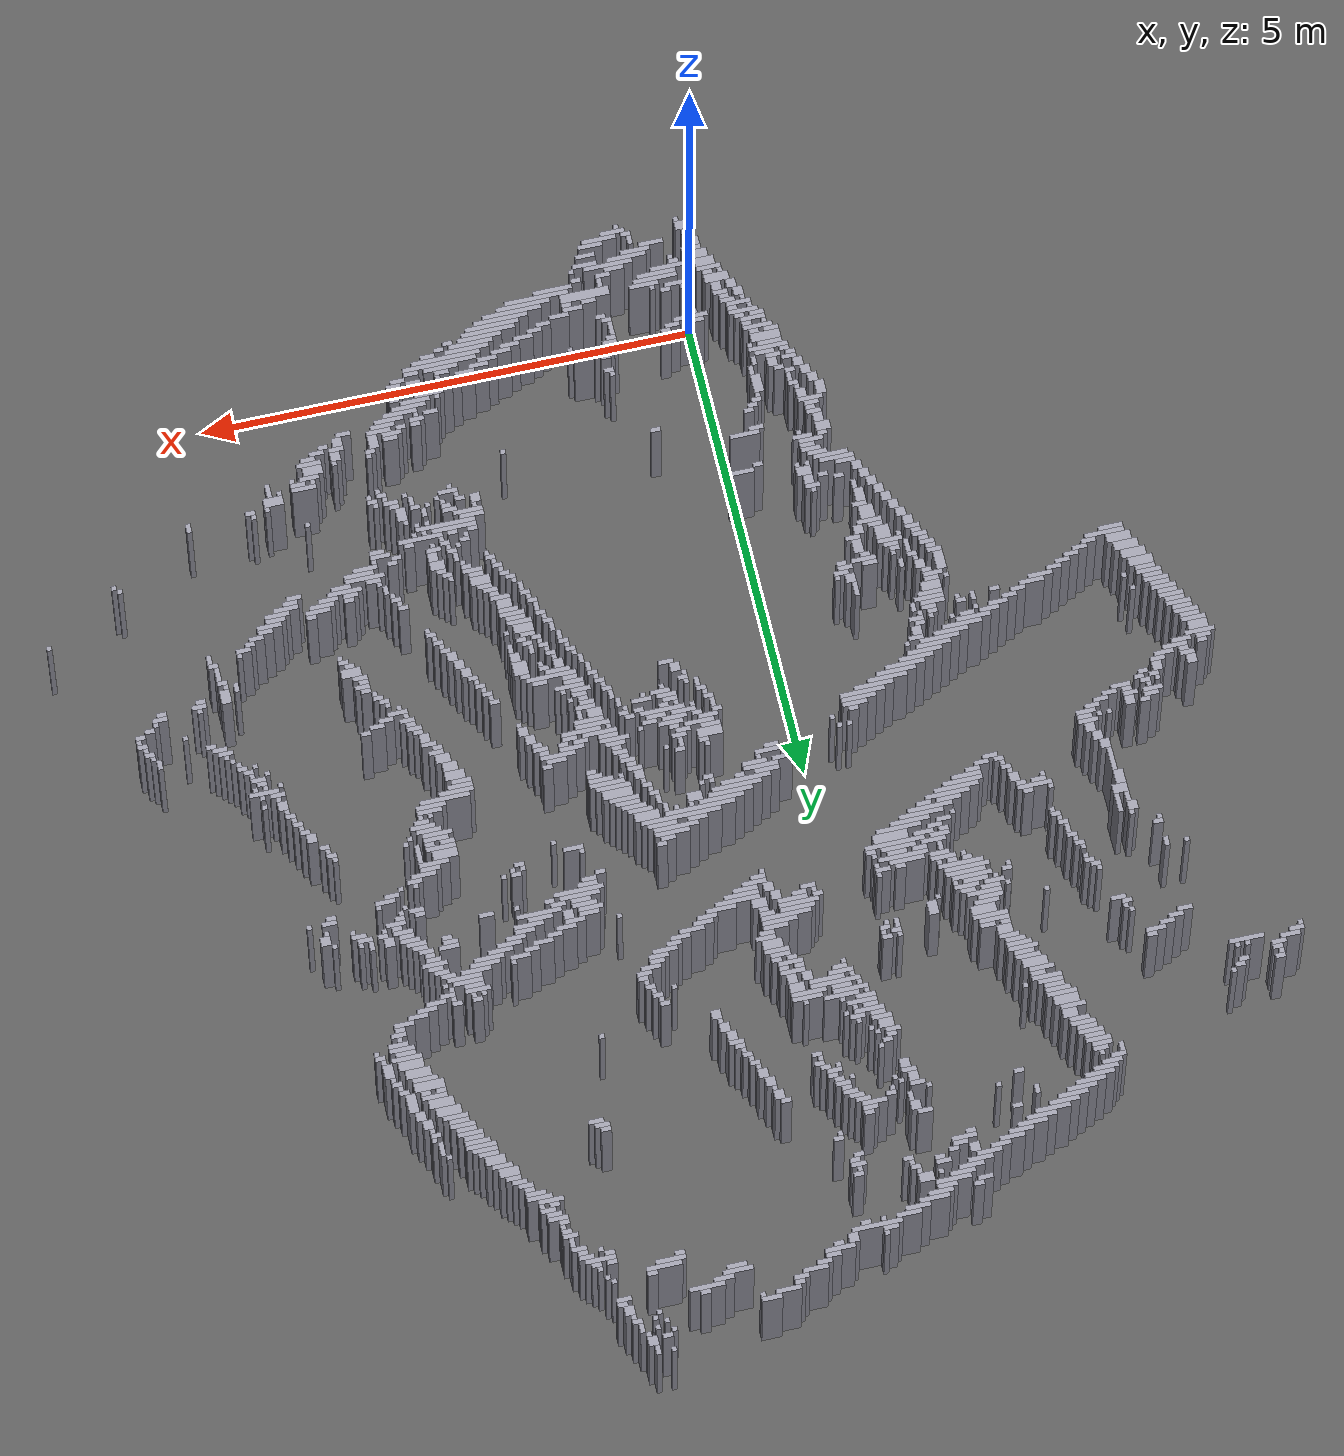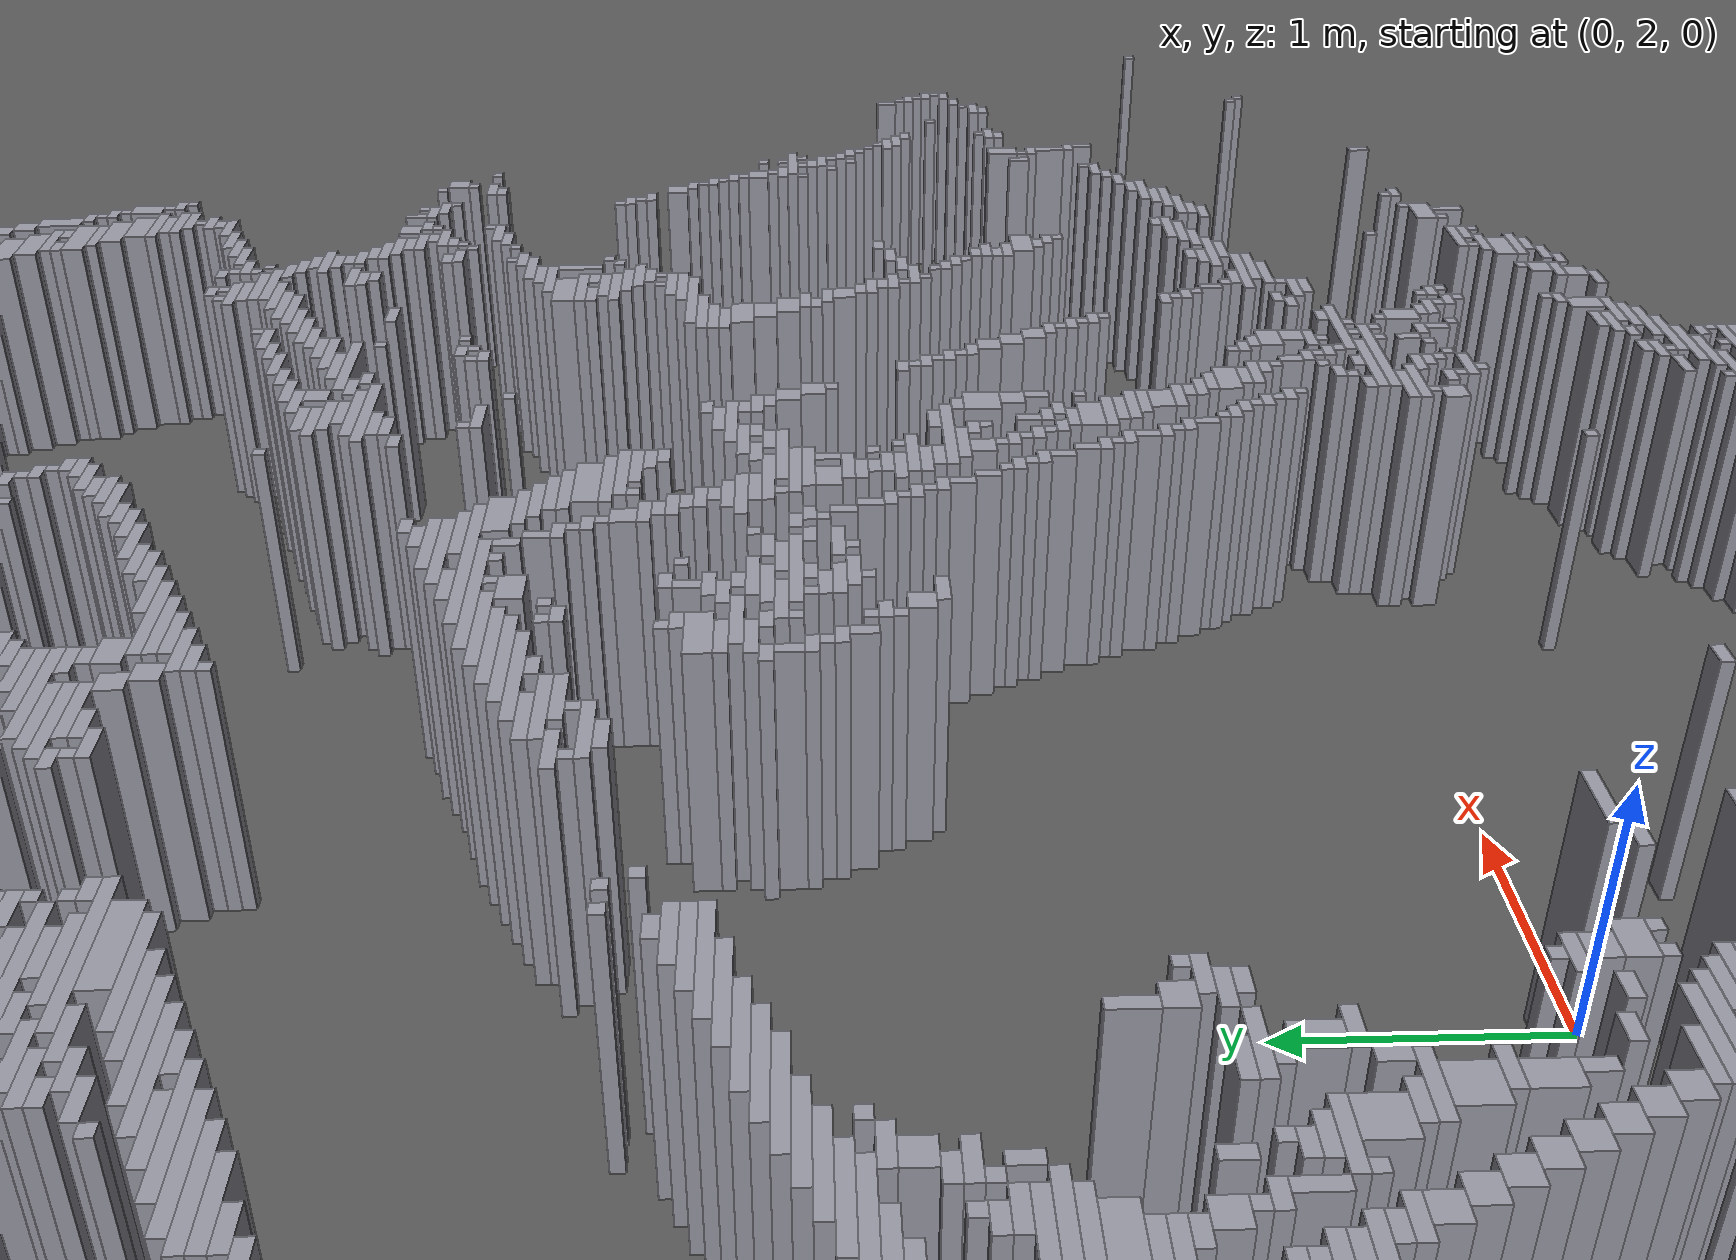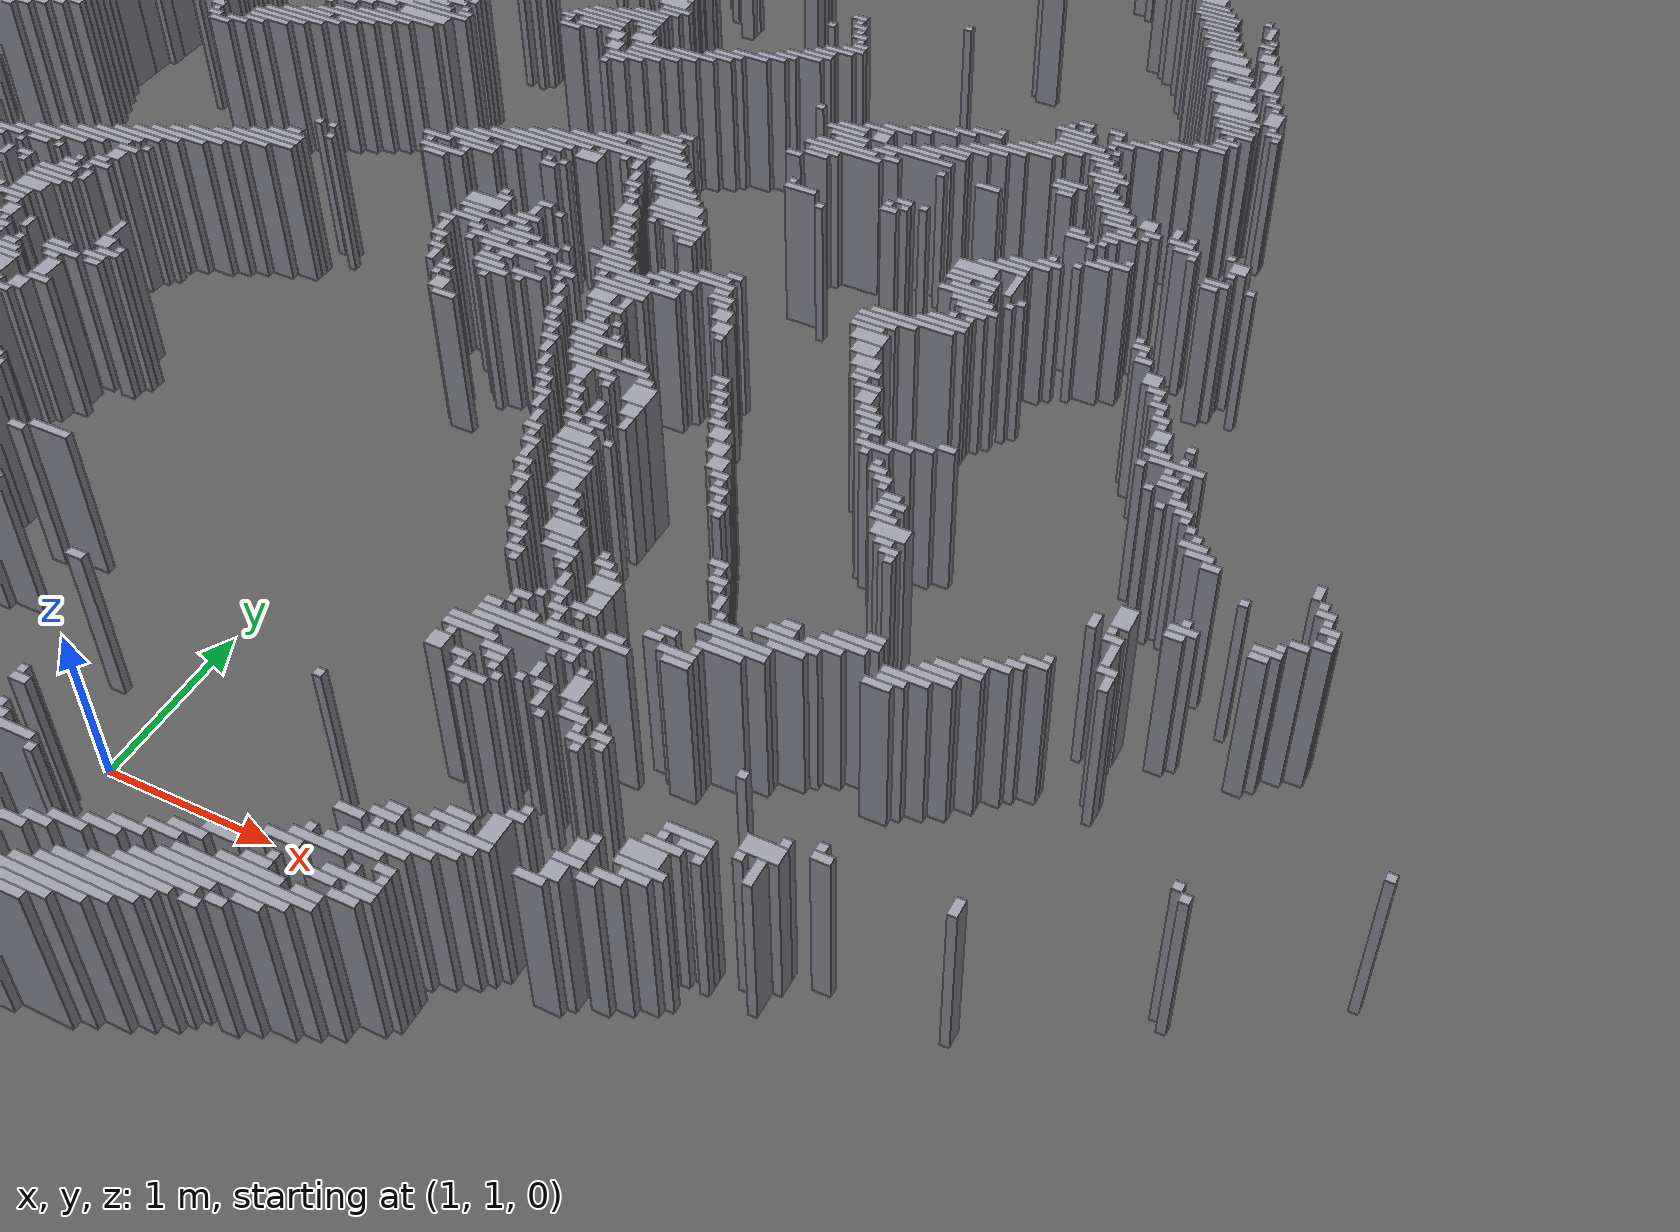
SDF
<?xml version="1.0"?>
<sdf version="1.8">
  <world name="dimi">
    <physics name="1ms" type="ignored">
      <max_step_size>0.004</max_step_size>
      <real_time_factor>1.0</real_time_factor>
    </physics>
    <plugin filename="gz-sim-physics-system" name="gz::sim::systems::Physics"/>
    <plugin filename="gz-sim-user-commands-system" name="gz::sim::systems::UserCommands"/>
    <plugin filename="gz-sim-scene-broadcaster-system" name="gz::sim::systems::SceneBroadcaster"/>
    <plugin filename="gz-sim-sensors-system" name="gz::sim::systems::Sensors">
      <render_engine>ogre2</render_engine>
    </plugin>

    <light type="directional" name="sun">
      <cast_shadows>false</cast_shadows>
      <pose>0 0 10 0 0 0</pose>
      <diffuse>0.9 0.9 0.9 1</diffuse>
      <direction>-0.3 0.2 -1</direction>
    </light>

    <model name="ground">
      <static>true</static>
      <link name="ground_link">
        <collision name="c"><geometry><plane><normal>0 0 1</normal><size>60 60</size></plane></geometry></collision>
        <visual name="v"><geometry><plane><normal>0 0 1</normal><size>60 60</size></plane></geometry>
          <material><ambient>0.3 0.3 0.3 1</ambient><diffuse>0.35 0.35 0.35 1</diffuse></material>
        </visual>
      </link>
    </model>

    <model name="walls">
      <static>true</static>
      <link name="wall_0">
        <pose>2.7080 11.0200 0.5000 0 0 0</pose>
        <collision name="c">
          <geometry><box><size>0.0500 0.0500 1.0000</size></box></geometry>
        </collision>
        <visual name="v">
          <geometry><box><size>0.0500 0.0500 1.0000</size></box></geometry>
          <material><ambient>0.5 0.5 0.55 1</ambient><diffuse>0.6 0.6 0.65 1</diffuse></material>
        </visual>
      </link>
      <link name="wall_1">
        <pose>2.8580 10.9950 0.5000 0 0 0</pose>
        <collision name="c">
          <geometry><box><size>0.0500 0.1000 1.0000</size></box></geometry>
        </collision>
        <visual name="v">
          <geometry><box><size>0.0500 0.1000 1.0000</size></box></geometry>
          <material><ambient>0.5 0.5 0.55 1</ambient><diffuse>0.6 0.6 0.65 1</diffuse></material>
        </visual>
      </link>
      <link name="wall_2">
        <pose>2.8830 10.8950 0.5000 0 0 0</pose>
        <collision name="c">
          <geometry><box><size>0.1000 0.1000 1.0000</size></box></geometry>
        </collision>
        <visual name="v">
          <geometry><box><size>0.1000 0.1000 1.0000</size></box></geometry>
          <material><ambient>0.5 0.5 0.55 1</ambient><diffuse>0.6 0.6 0.65 1</diffuse></material>
        </visual>
      </link>
      <link name="wall_3">
        <pose>2.7330 10.8700 0.5000 0 0 0</pose>
        <collision name="c">
          <geometry><box><size>0.1000 0.0500 1.0000</size></box></geometry>
        </collision>
        <visual name="v">
          <geometry><box><size>0.1000 0.0500 1.0000</size></box></geometry>
          <material><ambient>0.5 0.5 0.55 1</ambient><diffuse>0.6 0.6 0.65 1</diffuse></material>
        </visual>
      </link>
      <link name="wall_4">
        <pose>2.6580 10.8200 0.5000 0 0 0</pose>
        <collision name="c">
          <geometry><box><size>0.0500 0.0500 1.0000</size></box></geometry>
        </collision>
        <visual name="v">
          <geometry><box><size>0.0500 0.0500 1.0000</size></box></geometry>
          <material><ambient>0.5 0.5 0.55 1</ambient><diffuse>0.6 0.6 0.65 1</diffuse></material>
        </visual>
      </link>
      <link name="wall_5">
        <pose>2.9080 10.8200 0.5000 0 0 0</pose>
        <collision name="c">
          <geometry><box><size>0.0500 0.0500 1.0000</size></box></geometry>
        </collision>
        <visual name="v">
          <geometry><box><size>0.0500 0.0500 1.0000</size></box></geometry>
          <material><ambient>0.5 0.5 0.55 1</ambient><diffuse>0.6 0.6 0.65 1</diffuse></material>
        </visual>
      </link>
      <link name="wall_6">
        <pose>2.8080 10.7700 0.5000 0 0 0</pose>
        <collision name="c">
          <geometry><box><size>0.0500 0.0500 1.0000</size></box></geometry>
        </collision>
        <visual name="v">
          <geometry><box><size>0.0500 0.0500 1.0000</size></box></geometry>
          <material><ambient>0.5 0.5 0.55 1</ambient><diffuse>0.6 0.6 0.65 1</diffuse></material>
        </visual>
      </link>
      <link name="wall_7">
        <pose>2.9580 10.7450 0.5000 0 0 0</pose>
        <collision name="c">
          <geometry><box><size>0.0500 0.1000 1.0000</size></box></geometry>
        </collision>
        <visual name="v">
          <geometry><box><size>0.0500 0.1000 1.0000</size></box></geometry>
          <material><ambient>0.5 0.5 0.55 1</ambient><diffuse>0.6 0.6 0.65 1</diffuse></material>
        </visual>
      </link>
      <link name="wall_8">
        <pose>1.6830 10.7200 0.5000 0 0 0</pose>
        <collision name="c">
          <geometry><box><size>0.2000 0.0500 1.0000</size></box></geometry>
        </collision>
        <visual name="v">
          <geometry><box><size>0.2000 0.0500 1.0000</size></box></geometry>
          <material><ambient>0.5 0.5 0.55 1</ambient><diffuse>0.6 0.6 0.65 1</diffuse></material>
        </visual>
      </link>
      <link name="wall_9">
        <pose>2.7080 10.7200 0.5000 0 0 0</pose>
        <collision name="c">
          <geometry><box><size>0.0500 0.0500 1.0000</size></box></geometry>
        </collision>
        <visual name="v">
          <geometry><box><size>0.0500 0.0500 1.0000</size></box></geometry>
          <material><ambient>0.5 0.5 0.55 1</ambient><diffuse>0.6 0.6 0.65 1</diffuse></material>
        </visual>
      </link>
      <link name="wall_10">
        <pose>1.5080 10.6700 0.5000 0 0 0</pose>
        <collision name="c">
          <geometry><box><size>0.2500 0.0500 1.0000</size></box></geometry>
        </collision>
        <visual name="v">
          <geometry><box><size>0.2500 0.0500 1.0000</size></box></geometry>
          <material><ambient>0.5 0.5 0.55 1</ambient><diffuse>0.6 0.6 0.65 1</diffuse></material>
        </visual>
      </link>
      <link name="wall_11">
        <pose>1.7580 10.6700 0.5000 0 0 0</pose>
        <collision name="c">
          <geometry><box><size>0.0500 0.0500 1.0000</size></box></geometry>
        </collision>
        <visual name="v">
          <geometry><box><size>0.0500 0.0500 1.0000</size></box></geometry>
          <material><ambient>0.5 0.5 0.55 1</ambient><diffuse>0.6 0.6 0.65 1</diffuse></material>
        </visual>
      </link>
      <link name="wall_12">
        <pose>2.8080 10.6700 0.5000 0 0 0</pose>
        <collision name="c">
          <geometry><box><size>0.0500 0.0500 1.0000</size></box></geometry>
        </collision>
        <visual name="v">
          <geometry><box><size>0.0500 0.0500 1.0000</size></box></geometry>
          <material><ambient>0.5 0.5 0.55 1</ambient><diffuse>0.6 0.6 0.65 1</diffuse></material>
        </visual>
      </link>
      <link name="wall_13">
        <pose>2.9830 10.6700 0.5000 0 0 0</pose>
        <collision name="c">
          <geometry><box><size>0.1000 0.0500 1.0000</size></box></geometry>
        </collision>
        <visual name="v">
          <geometry><box><size>0.1000 0.0500 1.0000</size></box></geometry>
          <material><ambient>0.5 0.5 0.55 1</ambient><diffuse>0.6 0.6 0.65 1</diffuse></material>
        </visual>
      </link>
      <link name="wall_14">
        <pose>1.3830 10.6200 0.5000 0 0 0</pose>
        <collision name="c">
          <geometry><box><size>0.1000 0.0500 1.0000</size></box></geometry>
        </collision>
        <visual name="v">
          <geometry><box><size>0.1000 0.0500 1.0000</size></box></geometry>
          <material><ambient>0.5 0.5 0.55 1</ambient><diffuse>0.6 0.6 0.65 1</diffuse></material>
        </visual>
      </link>
      <link name="wall_15">
        <pose>2.7580 10.6200 0.5000 0 0 0</pose>
        <collision name="c">
          <geometry><box><size>0.0500 0.0500 1.0000</size></box></geometry>
        </collision>
        <visual name="v">
          <geometry><box><size>0.0500 0.0500 1.0000</size></box></geometry>
          <material><ambient>0.5 0.5 0.55 1</ambient><diffuse>0.6 0.6 0.65 1</diffuse></material>
        </visual>
      </link>
      <link name="wall_16">
        <pose>3.0080 10.6200 0.5000 0 0 0</pose>
        <collision name="c">
          <geometry><box><size>0.0500 0.0500 1.0000</size></box></geometry>
        </collision>
        <visual name="v">
          <geometry><box><size>0.0500 0.0500 1.0000</size></box></geometry>
          <material><ambient>0.5 0.5 0.55 1</ambient><diffuse>0.6 0.6 0.65 1</diffuse></material>
        </visual>
      </link>
      <link name="wall_17">
        <pose>1.3580 10.5700 0.5000 0 0 0</pose>
        <collision name="c">
          <geometry><box><size>0.1500 0.0500 1.0000</size></box></geometry>
        </collision>
        <visual name="v">
          <geometry><box><size>0.1500 0.0500 1.0000</size></box></geometry>
          <material><ambient>0.5 0.5 0.55 1</ambient><diffuse>0.6 0.6 0.65 1</diffuse></material>
        </visual>
      </link>
      <link name="wall_18">
        <pose>3.0330 10.5450 0.5000 0 0 0</pose>
        <collision name="c">
          <geometry><box><size>0.1000 0.1000 1.0000</size></box></geometry>
        </collision>
        <visual name="v">
          <geometry><box><size>0.1000 0.1000 1.0000</size></box></geometry>
          <material><ambient>0.5 0.5 0.55 1</ambient><diffuse>0.6 0.6 0.65 1</diffuse></material>
        </visual>
      </link>
      <link name="wall_19">
        <pose>1.2080 10.5200 0.5000 0 0 0</pose>
        <collision name="c">
          <geometry><box><size>0.2500 0.0500 1.0000</size></box></geometry>
        </collision>
        <visual name="v">
          <geometry><box><size>0.2500 0.0500 1.0000</size></box></geometry>
          <material><ambient>0.5 0.5 0.55 1</ambient><diffuse>0.6 0.6 0.65 1</diffuse></material>
        </visual>
      </link>
      <link name="wall_20">
        <pose>2.2830 10.5200 0.5000 0 0 0</pose>
        <collision name="c">
          <geometry><box><size>0.1000 0.0500 1.0000</size></box></geometry>
        </collision>
        <visual name="v">
          <geometry><box><size>0.1000 0.0500 1.0000</size></box></geometry>
          <material><ambient>0.5 0.5 0.55 1</ambient><diffuse>0.6 0.6 0.65 1</diffuse></material>
        </visual>
      </link>
      <link name="wall_21">
        <pose>1.1080 10.4700 0.5000 0 0 0</pose>
        <collision name="c">
          <geometry><box><size>0.1500 0.0500 1.0000</size></box></geometry>
        </collision>
        <visual name="v">
          <geometry><box><size>0.1500 0.0500 1.0000</size></box></geometry>
          <material><ambient>0.5 0.5 0.55 1</ambient><diffuse>0.6 0.6 0.65 1</diffuse></material>
        </visual>
      </link>
      <link name="wall_22">
        <pose>2.2580 10.4700 0.5000 0 0 0</pose>
        <collision name="c">
          <geometry><box><size>0.3500 0.0500 1.0000</size></box></geometry>
        </collision>
        <visual name="v">
          <geometry><box><size>0.3500 0.0500 1.0000</size></box></geometry>
          <material><ambient>0.5 0.5 0.55 1</ambient><diffuse>0.6 0.6 0.65 1</diffuse></material>
        </visual>
      </link>
      <link name="wall_23">
        <pose>3.0830 10.4700 0.5000 0 0 0</pose>
        <collision name="c">
          <geometry><box><size>0.1000 0.0500 1.0000</size></box></geometry>
        </collision>
        <visual name="v">
          <geometry><box><size>0.1000 0.0500 1.0000</size></box></geometry>
          <material><ambient>0.5 0.5 0.55 1</ambient><diffuse>0.6 0.6 0.65 1</diffuse></material>
        </visual>
      </link>
      <link name="wall_24">
        <pose>1.0080 10.4200 0.5000 0 0 0</pose>
        <collision name="c">
          <geometry><box><size>0.1500 0.0500 1.0000</size></box></geometry>
        </collision>
        <visual name="v">
          <geometry><box><size>0.1500 0.0500 1.0000</size></box></geometry>
          <material><ambient>0.5 0.5 0.55 1</ambient><diffuse>0.6 0.6 0.65 1</diffuse></material>
        </visual>
      </link>
      <link name="wall_25">
        <pose>2.0830 10.4200 0.5000 0 0 0</pose>
        <collision name="c">
          <geometry><box><size>0.2000 0.0500 1.0000</size></box></geometry>
        </collision>
        <visual name="v">
          <geometry><box><size>0.2000 0.0500 1.0000</size></box></geometry>
          <material><ambient>0.5 0.5 0.55 1</ambient><diffuse>0.6 0.6 0.65 1</diffuse></material>
        </visual>
      </link>
      <link name="wall_26">
        <pose>3.0580 10.4200 0.5000 0 0 0</pose>
        <collision name="c">
          <geometry><box><size>0.1500 0.0500 1.0000</size></box></geometry>
        </collision>
        <visual name="v">
          <geometry><box><size>0.1500 0.0500 1.0000</size></box></geometry>
          <material><ambient>0.5 0.5 0.55 1</ambient><diffuse>0.6 0.6 0.65 1</diffuse></material>
        </visual>
      </link>
      <link name="wall_27">
        <pose>0.9330 10.3700 0.5000 0 0 0</pose>
        <collision name="c">
          <geometry><box><size>0.3000 0.0500 1.0000</size></box></geometry>
        </collision>
        <visual name="v">
          <geometry><box><size>0.3000 0.0500 1.0000</size></box></geometry>
          <material><ambient>0.5 0.5 0.55 1</ambient><diffuse>0.6 0.6 0.65 1</diffuse></material>
        </visual>
      </link>
      <link name="wall_28">
        <pose>1.9330 10.3700 0.5000 0 0 0</pose>
        <collision name="c">
          <geometry><box><size>0.3000 0.0500 1.0000</size></box></geometry>
        </collision>
        <visual name="v">
          <geometry><box><size>0.3000 0.0500 1.0000</size></box></geometry>
          <material><ambient>0.5 0.5 0.55 1</ambient><diffuse>0.6 0.6 0.65 1</diffuse></material>
        </visual>
      </link>
      <link name="wall_29">
        <pose>0.4580 10.3200 0.5000 0 0 0</pose>
        <collision name="c">
          <geometry><box><size>0.0500 0.0500 1.0000</size></box></geometry>
        </collision>
        <visual name="v">
          <geometry><box><size>0.0500 0.0500 1.0000</size></box></geometry>
          <material><ambient>0.5 0.5 0.55 1</ambient><diffuse>0.6 0.6 0.65 1</diffuse></material>
        </visual>
      </link>
      <link name="wall_30">
        <pose>0.7830 10.2950 0.5000 0 0 0</pose>
        <collision name="c">
          <geometry><box><size>0.1000 0.1000 1.0000</size></box></geometry>
        </collision>
        <visual name="v">
          <geometry><box><size>0.1000 0.1000 1.0000</size></box></geometry>
          <material><ambient>0.5 0.5 0.55 1</ambient><diffuse>0.6 0.6 0.65 1</diffuse></material>
        </visual>
      </link>
      <link name="wall_31">
        <pose>0.9330 10.3200 0.5000 0 0 0</pose>
        <collision name="c">
          <geometry><box><size>0.1000 0.0500 1.0000</size></box></geometry>
        </collision>
        <visual name="v">
          <geometry><box><size>0.1000 0.0500 1.0000</size></box></geometry>
          <material><ambient>0.5 0.5 0.55 1</ambient><diffuse>0.6 0.6 0.65 1</diffuse></material>
        </visual>
      </link>
      <link name="wall_32">
        <pose>1.9330 10.3200 0.5000 0 0 0</pose>
        <collision name="c">
          <geometry><box><size>0.2000 0.0500 1.0000</size></box></geometry>
        </collision>
        <visual name="v">
          <geometry><box><size>0.2000 0.0500 1.0000</size></box></geometry>
          <material><ambient>0.5 0.5 0.55 1</ambient><diffuse>0.6 0.6 0.65 1</diffuse></material>
        </visual>
      </link>
      <link name="wall_33">
        <pose>0.4080 10.2700 0.5000 0 0 0</pose>
        <collision name="c">
          <geometry><box><size>0.1500 0.0500 1.0000</size></box></geometry>
        </collision>
        <visual name="v">
          <geometry><box><size>0.1500 0.0500 1.0000</size></box></geometry>
          <material><ambient>0.5 0.5 0.55 1</ambient><diffuse>0.6 0.6 0.65 1</diffuse></material>
        </visual>
      </link>
      <link name="wall_34">
        <pose>0.5330 10.2200 0.5000 0 0 0</pose>
        <collision name="c">
          <geometry><box><size>0.5000 0.0500 1.0000</size></box></geometry>
        </collision>
        <visual name="v">
          <geometry><box><size>0.5000 0.0500 1.0000</size></box></geometry>
          <material><ambient>0.5 0.5 0.55 1</ambient><diffuse>0.6 0.6 0.65 1</diffuse></material>
        </visual>
      </link>
      <link name="wall_35">
        <pose>2.7330 10.2200 0.5000 0 0 0</pose>
        <collision name="c">
          <geometry><box><size>0.1000 0.0500 1.0000</size></box></geometry>
        </collision>
        <visual name="v">
          <geometry><box><size>0.1000 0.0500 1.0000</size></box></geometry>
          <material><ambient>0.5 0.5 0.55 1</ambient><diffuse>0.6 0.6 0.65 1</diffuse></material>
        </visual>
      </link>
      <link name="wall_36">
        <pose>3.1080 10.2200 0.5000 0 0 0</pose>
        <collision name="c">
          <geometry><box><size>0.0500 0.0500 1.0000</size></box></geometry>
        </collision>
        <visual name="v">
          <geometry><box><size>0.0500 0.0500 1.0000</size></box></geometry>
          <material><ambient>0.5 0.5 0.55 1</ambient><diffuse>0.6 0.6 0.65 1</diffuse></material>
        </visual>
      </link>
      <link name="wall_37">
        <pose>0.2080 10.1700 0.5000 0 0 0</pose>
        <collision name="c">
          <geometry><box><size>0.2500 0.0500 1.0000</size></box></geometry>
        </collision>
        <visual name="v">
          <geometry><box><size>0.2500 0.0500 1.0000</size></box></geometry>
          <material><ambient>0.5 0.5 0.55 1</ambient><diffuse>0.6 0.6 0.65 1</diffuse></material>
        </visual>
      </link>
      <link name="wall_38">
        <pose>0.4580 10.1700 0.5000 0 0 0</pose>
        <collision name="c">
          <geometry><box><size>0.0500 0.0500 1.0000</size></box></geometry>
        </collision>
        <visual name="v">
          <geometry><box><size>0.0500 0.0500 1.0000</size></box></geometry>
          <material><ambient>0.5 0.5 0.55 1</ambient><diffuse>0.6 0.6 0.65 1</diffuse></material>
        </visual>
      </link>
      <link name="wall_39">
        <pose>0.6330 10.1700 0.5000 0 0 0</pose>
        <collision name="c">
          <geometry><box><size>0.1000 0.0500 1.0000</size></box></geometry>
        </collision>
        <visual name="v">
          <geometry><box><size>0.1000 0.0500 1.0000</size></box></geometry>
          <material><ambient>0.5 0.5 0.55 1</ambient><diffuse>0.6 0.6 0.65 1</diffuse></material>
        </visual>
      </link>
      <link name="wall_40">
        <pose>2.6080 10.1700 0.5000 0 0 0</pose>
        <collision name="c">
          <geometry><box><size>0.3500 0.0500 1.0000</size></box></geometry>
        </collision>
        <visual name="v">
          <geometry><box><size>0.3500 0.0500 1.0000</size></box></geometry>
          <material><ambient>0.5 0.5 0.55 1</ambient><diffuse>0.6 0.6 0.65 1</diffuse></material>
        </visual>
      </link>
      <link name="wall_41">
        <pose>3.1580 10.1700 0.5000 0 0 0</pose>
        <collision name="c">
          <geometry><box><size>0.0500 0.0500 1.0000</size></box></geometry>
        </collision>
        <visual name="v">
          <geometry><box><size>0.0500 0.0500 1.0000</size></box></geometry>
          <material><ambient>0.5 0.5 0.55 1</ambient><diffuse>0.6 0.6 0.65 1</diffuse></material>
        </visual>
      </link>
      <link name="wall_42">
        <pose>0.1080 10.1200 0.5000 0 0 0</pose>
        <collision name="c">
          <geometry><box><size>0.2500 0.0500 1.0000</size></box></geometry>
        </collision>
        <visual name="v">
          <geometry><box><size>0.2500 0.0500 1.0000</size></box></geometry>
          <material><ambient>0.5 0.5 0.55 1</ambient><diffuse>0.6 0.6 0.65 1</diffuse></material>
        </visual>
      </link>
      <link name="wall_43">
        <pose>2.5330 10.1200 0.5000 0 0 0</pose>
        <collision name="c">
          <geometry><box><size>0.3000 0.0500 1.0000</size></box></geometry>
        </collision>
        <visual name="v">
          <geometry><box><size>0.3000 0.0500 1.0000</size></box></geometry>
          <material><ambient>0.5 0.5 0.55 1</ambient><diffuse>0.6 0.6 0.65 1</diffuse></material>
        </visual>
      </link>
      <link name="wall_44">
        <pose>-0.0670 10.0700 0.5000 0 0 0</pose>
        <collision name="c">
          <geometry><box><size>0.3000 0.0500 1.0000</size></box></geometry>
        </collision>
        <visual name="v">
          <geometry><box><size>0.3000 0.0500 1.0000</size></box></geometry>
          <material><ambient>0.5 0.5 0.55 1</ambient><diffuse>0.6 0.6 0.65 1</diffuse></material>
        </visual>
      </link>
      <link name="wall_45">
        <pose>2.4330 10.0700 0.5000 0 0 0</pose>
        <collision name="c">
          <geometry><box><size>0.1000 0.0500 1.0000</size></box></geometry>
        </collision>
        <visual name="v">
          <geometry><box><size>0.1000 0.0500 1.0000</size></box></geometry>
          <material><ambient>0.5 0.5 0.55 1</ambient><diffuse>0.6 0.6 0.65 1</diffuse></material>
        </visual>
      </link>
      <link name="wall_46">
        <pose>3.2080 10.0700 0.5000 0 0 0</pose>
        <collision name="c">
          <geometry><box><size>0.0500 0.0500 1.0000</size></box></geometry>
        </collision>
        <visual name="v">
          <geometry><box><size>0.0500 0.0500 1.0000</size></box></geometry>
          <material><ambient>0.5 0.5 0.55 1</ambient><diffuse>0.6 0.6 0.65 1</diffuse></material>
        </visual>
      </link>
      <link name="wall_47">
        <pose>-0.5170 10.0200 0.5000 0 0 0</pose>
        <collision name="c">
          <geometry><box><size>0.1000 0.0500 1.0000</size></box></geometry>
        </collision>
        <visual name="v">
          <geometry><box><size>0.1000 0.0500 1.0000</size></box></geometry>
          <material><ambient>0.5 0.5 0.55 1</ambient><diffuse>0.6 0.6 0.65 1</diffuse></material>
        </visual>
      </link>
      <link name="wall_48">
        <pose>-0.1420 10.0200 0.5000 0 0 0</pose>
        <collision name="c">
          <geometry><box><size>0.2500 0.0500 1.0000</size></box></geometry>
        </collision>
        <visual name="v">
          <geometry><box><size>0.2500 0.0500 1.0000</size></box></geometry>
          <material><ambient>0.5 0.5 0.55 1</ambient><diffuse>0.6 0.6 0.65 1</diffuse></material>
        </visual>
      </link>
      <link name="wall_49">
        <pose>3.0830 10.0200 0.5000 0 0 0</pose>
        <collision name="c">
          <geometry><box><size>0.1000 0.0500 1.0000</size></box></geometry>
        </collision>
        <visual name="v">
          <geometry><box><size>0.1000 0.0500 1.0000</size></box></geometry>
          <material><ambient>0.5 0.5 0.55 1</ambient><diffuse>0.6 0.6 0.65 1</diffuse></material>
        </visual>
      </link>
      <link name="wall_50">
        <pose>3.2330 10.0200 0.5000 0 0 0</pose>
        <collision name="c">
          <geometry><box><size>0.1000 0.0500 1.0000</size></box></geometry>
        </collision>
        <visual name="v">
          <geometry><box><size>0.1000 0.0500 1.0000</size></box></geometry>
          <material><ambient>0.5 0.5 0.55 1</ambient><diffuse>0.6 0.6 0.65 1</diffuse></material>
        </visual>
      </link>
      <link name="wall_51">
        <pose>-0.5920 9.9700 0.5000 0 0 0</pose>
        <collision name="c">
          <geometry><box><size>0.1500 0.0500 1.0000</size></box></geometry>
        </collision>
        <visual name="v">
          <geometry><box><size>0.1500 0.0500 1.0000</size></box></geometry>
          <material><ambient>0.5 0.5 0.55 1</ambient><diffuse>0.6 0.6 0.65 1</diffuse></material>
        </visual>
      </link>
      <link name="wall_52">
        <pose>-0.2170 9.9700 0.5000 0 0 0</pose>
        <collision name="c">
          <geometry><box><size>0.2000 0.0500 1.0000</size></box></geometry>
        </collision>
        <visual name="v">
          <geometry><box><size>0.2000 0.0500 1.0000</size></box></geometry>
          <material><ambient>0.5 0.5 0.55 1</ambient><diffuse>0.6 0.6 0.65 1</diffuse></material>
        </visual>
      </link>
      <link name="wall_53">
        <pose>3.1830 9.9700 0.5000 0 0 0</pose>
        <collision name="c">
          <geometry><box><size>0.3000 0.0500 1.0000</size></box></geometry>
        </collision>
        <visual name="v">
          <geometry><box><size>0.3000 0.0500 1.0000</size></box></geometry>
          <material><ambient>0.5 0.5 0.55 1</ambient><diffuse>0.6 0.6 0.65 1</diffuse></material>
        </visual>
      </link>
      <link name="wall_54">
        <pose>-0.2920 9.9200 0.5000 0 0 0</pose>
        <collision name="c">
          <geometry><box><size>0.3500 0.0500 1.0000</size></box></geometry>
        </collision>
        <visual name="v">
          <geometry><box><size>0.3500 0.0500 1.0000</size></box></geometry>
          <material><ambient>0.5 0.5 0.55 1</ambient><diffuse>0.6 0.6 0.65 1</diffuse></material>
        </visual>
      </link>
      <link name="wall_55">
        <pose>3.0830 9.9200 0.5000 0 0 0</pose>
        <collision name="c">
          <geometry><box><size>0.1000 0.0500 1.0000</size></box></geometry>
        </collision>
        <visual name="v">
          <geometry><box><size>0.1000 0.0500 1.0000</size></box></geometry>
          <material><ambient>0.5 0.5 0.55 1</ambient><diffuse>0.6 0.6 0.65 1</diffuse></material>
        </visual>
      </link>
      <link name="wall_56">
        <pose>3.3080 9.9200 0.5000 0 0 0</pose>
        <collision name="c">
          <geometry><box><size>0.1500 0.0500 1.0000</size></box></geometry>
        </collision>
        <visual name="v">
          <geometry><box><size>0.1500 0.0500 1.0000</size></box></geometry>
          <material><ambient>0.5 0.5 0.55 1</ambient><diffuse>0.6 0.6 0.65 1</diffuse></material>
        </visual>
      </link>
      <link name="wall_57">
        <pose>-0.3920 9.8700 0.5000 0 0 0</pose>
        <collision name="c">
          <geometry><box><size>0.2500 0.0500 1.0000</size></box></geometry>
        </collision>
        <visual name="v">
          <geometry><box><size>0.2500 0.0500 1.0000</size></box></geometry>
          <material><ambient>0.5 0.5 0.55 1</ambient><diffuse>0.6 0.6 0.65 1</diffuse></material>
        </visual>
      </link>
      <link name="wall_58">
        <pose>-0.0420 9.8450 0.5000 0 0 0</pose>
        <collision name="c">
          <geometry><box><size>0.1500 0.1000 1.0000</size></box></geometry>
        </collision>
        <visual name="v">
          <geometry><box><size>0.1500 0.1000 1.0000</size></box></geometry>
          <material><ambient>0.5 0.5 0.55 1</ambient><diffuse>0.6 0.6 0.65 1</diffuse></material>
        </visual>
      </link>
      <link name="wall_59">
        <pose>3.1580 9.8700 0.5000 0 0 0</pose>
        <collision name="c">
          <geometry><box><size>0.0500 0.0500 1.0000</size></box></geometry>
        </collision>
        <visual name="v">
          <geometry><box><size>0.0500 0.0500 1.0000</size></box></geometry>
          <material><ambient>0.5 0.5 0.55 1</ambient><diffuse>0.6 0.6 0.65 1</diffuse></material>
        </visual>
      </link>
      <link name="wall_60">
        <pose>3.3330 9.8700 0.5000 0 0 0</pose>
        <collision name="c">
          <geometry><box><size>0.1000 0.0500 1.0000</size></box></geometry>
        </collision>
        <visual name="v">
          <geometry><box><size>0.1000 0.0500 1.0000</size></box></geometry>
          <material><ambient>0.5 0.5 0.55 1</ambient><diffuse>0.6 0.6 0.65 1</diffuse></material>
        </visual>
      </link>
      <link name="wall_61">
        <pose>-0.4920 9.8200 0.5000 0 0 0</pose>
        <collision name="c">
          <geometry><box><size>0.2500 0.0500 1.0000</size></box></geometry>
        </collision>
        <visual name="v">
          <geometry><box><size>0.2500 0.0500 1.0000</size></box></geometry>
          <material><ambient>0.5 0.5 0.55 1</ambient><diffuse>0.6 0.6 0.65 1</diffuse></material>
        </visual>
      </link>
      <link name="wall_62">
        <pose>-0.1920 9.8200 0.5000 0 0 0</pose>
        <collision name="c">
          <geometry><box><size>0.0500 0.0500 1.0000</size></box></geometry>
        </collision>
        <visual name="v">
          <geometry><box><size>0.0500 0.0500 1.0000</size></box></geometry>
          <material><ambient>0.5 0.5 0.55 1</ambient><diffuse>0.6 0.6 0.65 1</diffuse></material>
        </visual>
      </link>
      <link name="wall_63">
        <pose>3.3580 9.8200 0.5000 0 0 0</pose>
        <collision name="c">
          <geometry><box><size>0.1500 0.0500 1.0000</size></box></geometry>
        </collision>
        <visual name="v">
          <geometry><box><size>0.1500 0.0500 1.0000</size></box></geometry>
          <material><ambient>0.5 0.5 0.55 1</ambient><diffuse>0.6 0.6 0.65 1</diffuse></material>
        </visual>
      </link>
      <link name="wall_64">
        <pose>-0.5920 9.7700 0.5000 0 0 0</pose>
        <collision name="c">
          <geometry><box><size>0.2500 0.0500 1.0000</size></box></geometry>
        </collision>
        <visual name="v">
          <geometry><box><size>0.2500 0.0500 1.0000</size></box></geometry>
          <material><ambient>0.5 0.5 0.55 1</ambient><diffuse>0.6 0.6 0.65 1</diffuse></material>
        </visual>
      </link>
      <link name="wall_65">
        <pose>0.0080 9.7700 0.5000 0 0 0</pose>
        <collision name="c">
          <geometry><box><size>0.0500 0.0500 1.0000</size></box></geometry>
        </collision>
        <visual name="v">
          <geometry><box><size>0.0500 0.0500 1.0000</size></box></geometry>
          <material><ambient>0.5 0.5 0.55 1</ambient><diffuse>0.6 0.6 0.65 1</diffuse></material>
        </visual>
      </link>
      <link name="wall_66">
        <pose>3.4080 9.7450 0.5000 0 0 0</pose>
        <collision name="c">
          <geometry><box><size>0.0500 0.1000 1.0000</size></box></geometry>
        </collision>
        <visual name="v">
          <geometry><box><size>0.0500 0.1000 1.0000</size></box></geometry>
          <material><ambient>0.5 0.5 0.55 1</ambient><diffuse>0.6 0.6 0.65 1</diffuse></material>
        </visual>
      </link>
      <link name="wall_67">
        <pose>-0.6920 9.7200 0.5000 0 0 0</pose>
        <collision name="c">
          <geometry><box><size>0.2500 0.0500 1.0000</size></box></geometry>
        </collision>
        <visual name="v">
          <geometry><box><size>0.2500 0.0500 1.0000</size></box></geometry>
          <material><ambient>0.5 0.5 0.55 1</ambient><diffuse>0.6 0.6 0.65 1</diffuse></material>
        </visual>
      </link>
      <link name="wall_68">
        <pose>-0.2420 9.7200 0.5000 0 0 0</pose>
        <collision name="c">
          <geometry><box><size>0.1500 0.0500 1.0000</size></box></geometry>
        </collision>
        <visual name="v">
          <geometry><box><size>0.1500 0.0500 1.0000</size></box></geometry>
          <material><ambient>0.5 0.5 0.55 1</ambient><diffuse>0.6 0.6 0.65 1</diffuse></material>
        </visual>
      </link>
      <link name="wall_69">
        <pose>0.0330 9.7200 0.5000 0 0 0</pose>
        <collision name="c">
          <geometry><box><size>0.1000 0.0500 1.0000</size></box></geometry>
        </collision>
        <visual name="v">
          <geometry><box><size>0.1000 0.0500 1.0000</size></box></geometry>
          <material><ambient>0.5 0.5 0.55 1</ambient><diffuse>0.6 0.6 0.65 1</diffuse></material>
        </visual>
      </link>
      <link name="wall_70">
        <pose>-0.8170 9.6700 0.5000 0 0 0</pose>
        <collision name="c">
          <geometry><box><size>0.2000 0.0500 1.0000</size></box></geometry>
        </collision>
        <visual name="v">
          <geometry><box><size>0.2000 0.0500 1.0000</size></box></geometry>
          <material><ambient>0.5 0.5 0.55 1</ambient><diffuse>0.6 0.6 0.65 1</diffuse></material>
        </visual>
      </link>
      <link name="wall_71">
        <pose>-0.5670 9.6450 0.5000 0 0 0</pose>
        <collision name="c">
          <geometry><box><size>0.1000 0.1000 1.0000</size></box></geometry>
        </collision>
        <visual name="v">
          <geometry><box><size>0.1000 0.1000 1.0000</size></box></geometry>
          <material><ambient>0.5 0.5 0.55 1</ambient><diffuse>0.6 0.6 0.65 1</diffuse></material>
        </visual>
      </link>
      <link name="wall_72">
        <pose>-0.2170 9.6700 0.5000 0 0 0</pose>
        <collision name="c">
          <geometry><box><size>0.1000 0.0500 1.0000</size></box></geometry>
        </collision>
        <visual name="v">
          <geometry><box><size>0.1000 0.0500 1.0000</size></box></geometry>
          <material><ambient>0.5 0.5 0.55 1</ambient><diffuse>0.6 0.6 0.65 1</diffuse></material>
        </visual>
      </link>
      <link name="wall_73">
        <pose>0.0580 9.6700 0.5000 0 0 0</pose>
        <collision name="c">
          <geometry><box><size>0.0500 0.0500 1.0000</size></box></geometry>
        </collision>
        <visual name="v">
          <geometry><box><size>0.0500 0.0500 1.0000</size></box></geometry>
          <material><ambient>0.5 0.5 0.55 1</ambient><diffuse>0.6 0.6 0.65 1</diffuse></material>
        </visual>
      </link>
      <link name="wall_74">
        <pose>0.5830 9.6700 0.5000 0 0 0</pose>
        <collision name="c">
          <geometry><box><size>0.1000 0.0500 1.0000</size></box></geometry>
        </collision>
        <visual name="v">
          <geometry><box><size>0.1000 0.0500 1.0000</size></box></geometry>
          <material><ambient>0.5 0.5 0.55 1</ambient><diffuse>0.6 0.6 0.65 1</diffuse></material>
        </visual>
      </link>
      <link name="wall_75">
        <pose>3.4080 9.6700 0.5000 0 0 0</pose>
        <collision name="c">
          <geometry><box><size>0.1500 0.0500 1.0000</size></box></geometry>
        </collision>
        <visual name="v">
          <geometry><box><size>0.1500 0.0500 1.0000</size></box></geometry>
          <material><ambient>0.5 0.5 0.55 1</ambient><diffuse>0.6 0.6 0.65 1</diffuse></material>
        </visual>
      </link>
      <link name="wall_76">
        <pose>-0.9420 9.6200 0.5000 0 0 0</pose>
        <collision name="c">
          <geometry><box><size>0.2500 0.0500 1.0000</size></box></geometry>
        </collision>
        <visual name="v">
          <geometry><box><size>0.2500 0.0500 1.0000</size></box></geometry>
          <material><ambient>0.5 0.5 0.55 1</ambient><diffuse>0.6 0.6 0.65 1</diffuse></material>
        </visual>
      </link>
      <link name="wall_77">
        <pose>-0.3670 9.6200 0.5000 0 0 0</pose>
        <collision name="c">
          <geometry><box><size>0.1000 0.0500 1.0000</size></box></geometry>
        </collision>
        <visual name="v">
          <geometry><box><size>0.1000 0.0500 1.0000</size></box></geometry>
          <material><ambient>0.5 0.5 0.55 1</ambient><diffuse>0.6 0.6 0.65 1</diffuse></material>
        </visual>
      </link>
      <link name="wall_78">
        <pose>0.0830 9.6200 0.5000 0 0 0</pose>
        <collision name="c">
          <geometry><box><size>0.1000 0.0500 1.0000</size></box></geometry>
        </collision>
        <visual name="v">
          <geometry><box><size>0.1000 0.0500 1.0000</size></box></geometry>
          <material><ambient>0.5 0.5 0.55 1</ambient><diffuse>0.6 0.6 0.65 1</diffuse></material>
        </visual>
      </link>
      <link name="wall_79">
        <pose>0.5580 9.6200 0.5000 0 0 0</pose>
        <collision name="c">
          <geometry><box><size>0.0500 0.0500 1.0000</size></box></geometry>
        </collision>
        <visual name="v">
          <geometry><box><size>0.0500 0.0500 1.0000</size></box></geometry>
          <material><ambient>0.5 0.5 0.55 1</ambient><diffuse>0.6 0.6 0.65 1</diffuse></material>
        </visual>
      </link>
      <link name="wall_80">
        <pose>3.4330 9.6200 0.5000 0 0 0</pose>
        <collision name="c">
          <geometry><box><size>0.1000 0.0500 1.0000</size></box></geometry>
        </collision>
        <visual name="v">
          <geometry><box><size>0.1000 0.0500 1.0000</size></box></geometry>
          <material><ambient>0.5 0.5 0.55 1</ambient><diffuse>0.6 0.6 0.65 1</diffuse></material>
        </visual>
      </link>
      <link name="wall_81">
        <pose>-1.0420 9.5700 0.5000 0 0 0</pose>
        <collision name="c">
          <geometry><box><size>0.2500 0.0500 1.0000</size></box></geometry>
        </collision>
        <visual name="v">
          <geometry><box><size>0.2500 0.0500 1.0000</size></box></geometry>
          <material><ambient>0.5 0.5 0.55 1</ambient><diffuse>0.6 0.6 0.65 1</diffuse></material>
        </visual>
      </link>
      <link name="wall_82">
        <pose>-0.4420 9.5700 0.5000 0 0 0</pose>
        <collision name="c">
          <geometry><box><size>0.1500 0.0500 1.0000</size></box></geometry>
        </collision>
        <visual name="v">
          <geometry><box><size>0.1500 0.0500 1.0000</size></box></geometry>
          <material><ambient>0.5 0.5 0.55 1</ambient><diffuse>0.6 0.6 0.65 1</diffuse></material>
        </visual>
      </link>
      <link name="wall_83">
        <pose>0.5580 9.5700 0.5000 0 0 0</pose>
        <collision name="c">
          <geometry><box><size>0.1500 0.0500 1.0000</size></box></geometry>
        </collision>
        <visual name="v">
          <geometry><box><size>0.1500 0.0500 1.0000</size></box></geometry>
          <material><ambient>0.5 0.5 0.55 1</ambient><diffuse>0.6 0.6 0.65 1</diffuse></material>
        </visual>
      </link>
      <link name="wall_84">
        <pose>3.4580 9.5700 0.5000 0 0 0</pose>
        <collision name="c">
          <geometry><box><size>0.0500 0.0500 1.0000</size></box></geometry>
        </collision>
        <visual name="v">
          <geometry><box><size>0.0500 0.0500 1.0000</size></box></geometry>
          <material><ambient>0.5 0.5 0.55 1</ambient><diffuse>0.6 0.6 0.65 1</diffuse></material>
        </visual>
      </link>
      <link name="wall_85">
        <pose>-1.1670 9.5200 0.5000 0 0 0</pose>
        <collision name="c">
          <geometry><box><size>0.3000 0.0500 1.0000</size></box></geometry>
        </collision>
        <visual name="v">
          <geometry><box><size>0.3000 0.0500 1.0000</size></box></geometry>
          <material><ambient>0.5 0.5 0.55 1</ambient><diffuse>0.6 0.6 0.65 1</diffuse></material>
        </visual>
      </link>
      <link name="wall_86">
        <pose>-0.4920 9.5200 0.5000 0 0 0</pose>
        <collision name="c">
          <geometry><box><size>0.2500 0.0500 1.0000</size></box></geometry>
        </collision>
        <visual name="v">
          <geometry><box><size>0.2500 0.0500 1.0000</size></box></geometry>
          <material><ambient>0.5 0.5 0.55 1</ambient><diffuse>0.6 0.6 0.65 1</diffuse></material>
        </visual>
      </link>
      <link name="wall_87">
        <pose>0.5830 9.5200 0.5000 0 0 0</pose>
        <collision name="c">
          <geometry><box><size>0.1000 0.0500 1.0000</size></box></geometry>
        </collision>
        <visual name="v">
          <geometry><box><size>0.1000 0.0500 1.0000</size></box></geometry>
          <material><ambient>0.5 0.5 0.55 1</ambient><diffuse>0.6 0.6 0.65 1</diffuse></material>
        </visual>
      </link>
      <link name="wall_88">
        <pose>3.4330 9.5200 0.5000 0 0 0</pose>
        <collision name="c">
          <geometry><box><size>0.1000 0.0500 1.0000</size></box></geometry>
        </collision>
        <visual name="v">
          <geometry><box><size>0.1000 0.0500 1.0000</size></box></geometry>
          <material><ambient>0.5 0.5 0.55 1</ambient><diffuse>0.6 0.6 0.65 1</diffuse></material>
        </visual>
      </link>
      <link name="wall_89">
        <pose>-1.2670 9.4700 0.5000 0 0 0</pose>
        <collision name="c">
          <geometry><box><size>0.3000 0.0500 1.0000</size></box></geometry>
        </collision>
        <visual name="v">
          <geometry><box><size>0.3000 0.0500 1.0000</size></box></geometry>
          <material><ambient>0.5 0.5 0.55 1</ambient><diffuse>0.6 0.6 0.65 1</diffuse></material>
        </visual>
      </link>
      <link name="wall_90">
        <pose>-0.5670 9.4700 0.5000 0 0 0</pose>
        <collision name="c">
          <geometry><box><size>0.1000 0.0500 1.0000</size></box></geometry>
        </collision>
        <visual name="v">
          <geometry><box><size>0.1000 0.0500 1.0000</size></box></geometry>
          <material><ambient>0.5 0.5 0.55 1</ambient><diffuse>0.6 0.6 0.65 1</diffuse></material>
        </visual>
      </link>
      <link name="wall_91">
        <pose>0.5330 9.4700 0.5000 0 0 0</pose>
        <collision name="c">
          <geometry><box><size>0.1000 0.0500 1.0000</size></box></geometry>
        </collision>
        <visual name="v">
          <geometry><box><size>0.1000 0.0500 1.0000</size></box></geometry>
          <material><ambient>0.5 0.5 0.55 1</ambient><diffuse>0.6 0.6 0.65 1</diffuse></material>
        </visual>
      </link>
      <link name="wall_92">
        <pose>3.4830 9.4700 0.5000 0 0 0</pose>
        <collision name="c">
          <geometry><box><size>0.2000 0.0500 1.0000</size></box></geometry>
        </collision>
        <visual name="v">
          <geometry><box><size>0.2000 0.0500 1.0000</size></box></geometry>
          <material><ambient>0.5 0.5 0.55 1</ambient><diffuse>0.6 0.6 0.65 1</diffuse></material>
        </visual>
      </link>
      <link name="wall_93">
        <pose>-1.3920 9.4200 0.5000 0 0 0</pose>
        <collision name="c">
          <geometry><box><size>0.3500 0.0500 1.0000</size></box></geometry>
        </collision>
        <visual name="v">
          <geometry><box><size>0.3500 0.0500 1.0000</size></box></geometry>
          <material><ambient>0.5 0.5 0.55 1</ambient><diffuse>0.6 0.6 0.65 1</diffuse></material>
        </visual>
      </link>
      <link name="wall_94">
        <pose>3.5080 9.4200 0.5000 0 0 0</pose>
        <collision name="c">
          <geometry><box><size>0.1500 0.0500 1.0000</size></box></geometry>
        </collision>
        <visual name="v">
          <geometry><box><size>0.1500 0.0500 1.0000</size></box></geometry>
          <material><ambient>0.5 0.5 0.55 1</ambient><diffuse>0.6 0.6 0.65 1</diffuse></material>
        </visual>
      </link>
      <link name="wall_95">
        <pose>-1.5170 9.3700 0.5000 0 0 0</pose>
        <collision name="c">
          <geometry><box><size>0.3000 0.0500 1.0000</size></box></geometry>
        </collision>
        <visual name="v">
          <geometry><box><size>0.3000 0.0500 1.0000</size></box></geometry>
          <material><ambient>0.5 0.5 0.55 1</ambient><diffuse>0.6 0.6 0.65 1</diffuse></material>
        </visual>
      </link>
      <link name="wall_96">
        <pose>3.5580 9.3700 0.5000 0 0 0</pose>
        <collision name="c">
          <geometry><box><size>0.1500 0.0500 1.0000</size></box></geometry>
        </collision>
        <visual name="v">
          <geometry><box><size>0.1500 0.0500 1.0000</size></box></geometry>
          <material><ambient>0.5 0.5 0.55 1</ambient><diffuse>0.6 0.6 0.65 1</diffuse></material>
        </visual>
      </link>
      <link name="wall_97">
        <pose>-1.6170 9.3200 0.5000 0 0 0</pose>
        <collision name="c">
          <geometry><box><size>0.3000 0.0500 1.0000</size></box></geometry>
        </collision>
        <visual name="v">
          <geometry><box><size>0.3000 0.0500 1.0000</size></box></geometry>
          <material><ambient>0.5 0.5 0.55 1</ambient><diffuse>0.6 0.6 0.65 1</diffuse></material>
        </visual>
      </link>
      <link name="wall_98">
        <pose>-1.0670 9.3200 0.5000 0 0 0</pose>
        <collision name="c">
          <geometry><box><size>0.1000 0.0500 1.0000</size></box></geometry>
        </collision>
        <visual name="v">
          <geometry><box><size>0.1000 0.0500 1.0000</size></box></geometry>
          <material><ambient>0.5 0.5 0.55 1</ambient><diffuse>0.6 0.6 0.65 1</diffuse></material>
        </visual>
      </link>
      <link name="wall_99">
        <pose>3.4830 9.3200 0.5000 0 0 0</pose>
        <collision name="c">
          <geometry><box><size>0.1000 0.0500 1.0000</size></box></geometry>
        </collision>
        <visual name="v">
          <geometry><box><size>0.1000 0.0500 1.0000</size></box></geometry>
          <material><ambient>0.5 0.5 0.55 1</ambient><diffuse>0.6 0.6 0.65 1</diffuse></material>
        </visual>
      </link>
      <link name="wall_100">
        <pose>3.6080 9.3200 0.5000 0 0 0</pose>
        <collision name="c">
          <geometry><box><size>0.0500 0.0500 1.0000</size></box></geometry>
        </collision>
        <visual name="v">
          <geometry><box><size>0.0500 0.0500 1.0000</size></box></geometry>
          <material><ambient>0.5 0.5 0.55 1</ambient><diffuse>0.6 0.6 0.65 1</diffuse></material>
        </visual>
      </link>
      <link name="wall_101">
        <pose>-1.7170 9.2700 0.5000 0 0 0</pose>
        <collision name="c">
          <geometry><box><size>0.3000 0.0500 1.0000</size></box></geometry>
        </collision>
        <visual name="v">
          <geometry><box><size>0.3000 0.0500 1.0000</size></box></geometry>
          <material><ambient>0.5 0.5 0.55 1</ambient><diffuse>0.6 0.6 0.65 1</diffuse></material>
        </visual>
      </link>
      <link name="wall_102">
        <pose>0.6830 9.2700 0.5000 0 0 0</pose>
        <collision name="c">
          <geometry><box><size>0.1000 0.0500 1.0000</size></box></geometry>
        </collision>
        <visual name="v">
          <geometry><box><size>0.1000 0.0500 1.0000</size></box></geometry>
          <material><ambient>0.5 0.5 0.55 1</ambient><diffuse>0.6 0.6 0.65 1</diffuse></material>
        </visual>
      </link>
      <link name="wall_103">
        <pose>3.5080 9.2700 0.5000 0 0 0</pose>
        <collision name="c">
          <geometry><box><size>0.2500 0.0500 1.0000</size></box></geometry>
        </collision>
        <visual name="v">
          <geometry><box><size>0.2500 0.0500 1.0000</size></box></geometry>
          <material><ambient>0.5 0.5 0.55 1</ambient><diffuse>0.6 0.6 0.65 1</diffuse></material>
        </visual>
      </link>
      <link name="wall_104">
        <pose>-1.8170 9.2200 0.5000 0 0 0</pose>
        <collision name="c">
          <geometry><box><size>0.3000 0.0500 1.0000</size></box></geometry>
        </collision>
        <visual name="v">
          <geometry><box><size>0.3000 0.0500 1.0000</size></box></geometry>
          <material><ambient>0.5 0.5 0.55 1</ambient><diffuse>0.6 0.6 0.65 1</diffuse></material>
        </visual>
      </link>
      <link name="wall_105">
        <pose>-1.2920 9.1950 0.5000 0 0 0</pose>
        <collision name="c">
          <geometry><box><size>0.0500 0.1000 1.0000</size></box></geometry>
        </collision>
        <visual name="v">
          <geometry><box><size>0.0500 0.1000 1.0000</size></box></geometry>
          <material><ambient>0.5 0.5 0.55 1</ambient><diffuse>0.6 0.6 0.65 1</diffuse></material>
        </visual>
      </link>
      <link name="wall_106">
        <pose>0.6580 9.2200 0.5000 0 0 0</pose>
        <collision name="c">
          <geometry><box><size>0.0500 0.0500 1.0000</size></box></geometry>
        </collision>
        <visual name="v">
          <geometry><box><size>0.0500 0.0500 1.0000</size></box></geometry>
          <material><ambient>0.5 0.5 0.55 1</ambient><diffuse>0.6 0.6 0.65 1</diffuse></material>
        </visual>
      </link>
      <link name="wall_107">
        <pose>3.6080 9.2200 0.5000 0 0 0</pose>
        <collision name="c">
          <geometry><box><size>0.2500 0.0500 1.0000</size></box></geometry>
        </collision>
        <visual name="v">
          <geometry><box><size>0.2500 0.0500 1.0000</size></box></geometry>
          <material><ambient>0.5 0.5 0.55 1</ambient><diffuse>0.6 0.6 0.65 1</diffuse></material>
        </visual>
      </link>
      <link name="wall_108">
        <pose>-1.9170 9.1700 0.5000 0 0 0</pose>
        <collision name="c">
          <geometry><box><size>0.3000 0.0500 1.0000</size></box></geometry>
        </collision>
        <visual name="v">
          <geometry><box><size>0.3000 0.0500 1.0000</size></box></geometry>
          <material><ambient>0.5 0.5 0.55 1</ambient><diffuse>0.6 0.6 0.65 1</diffuse></material>
        </visual>
      </link>
      <link name="wall_109">
        <pose>-0.1920 9.1700 0.5000 0 0 0</pose>
        <collision name="c">
          <geometry><box><size>0.1500 0.0500 1.0000</size></box></geometry>
        </collision>
        <visual name="v">
          <geometry><box><size>0.1500 0.0500 1.0000</size></box></geometry>
          <material><ambient>0.5 0.5 0.55 1</ambient><diffuse>0.6 0.6 0.65 1</diffuse></material>
        </visual>
      </link>
      <link name="wall_110">
        <pose>3.6330 9.1700 0.5000 0 0 0</pose>
        <collision name="c">
          <geometry><box><size>0.2000 0.0500 1.0000</size></box></geometry>
        </collision>
        <visual name="v">
          <geometry><box><size>0.2000 0.0500 1.0000</size></box></geometry>
          <material><ambient>0.5 0.5 0.55 1</ambient><diffuse>0.6 0.6 0.65 1</diffuse></material>
        </visual>
      </link>
      <link name="wall_111">
        <pose>-1.9920 9.1200 0.5000 0 0 0</pose>
        <collision name="c">
          <geometry><box><size>0.2500 0.0500 1.0000</size></box></geometry>
        </collision>
        <visual name="v">
          <geometry><box><size>0.2500 0.0500 1.0000</size></box></geometry>
          <material><ambient>0.5 0.5 0.55 1</ambient><diffuse>0.6 0.6 0.65 1</diffuse></material>
        </visual>
      </link>
      <link name="wall_112">
        <pose>-0.1170 9.0950 0.5000 0 0 0</pose>
        <collision name="c">
          <geometry><box><size>0.1000 0.1000 1.0000</size></box></geometry>
        </collision>
        <visual name="v">
          <geometry><box><size>0.1000 0.1000 1.0000</size></box></geometry>
          <material><ambient>0.5 0.5 0.55 1</ambient><diffuse>0.6 0.6 0.65 1</diffuse></material>
        </visual>
      </link>
      <link name="wall_113">
        <pose>3.6830 9.1200 0.5000 0 0 0</pose>
        <collision name="c">
          <geometry><box><size>0.1000 0.0500 1.0000</size></box></geometry>
        </collision>
        <visual name="v">
          <geometry><box><size>0.1000 0.0500 1.0000</size></box></geometry>
          <material><ambient>0.5 0.5 0.55 1</ambient><diffuse>0.6 0.6 0.65 1</diffuse></material>
        </visual>
      </link>
      <link name="wall_114">
        <pose>-2.0670 9.0700 0.5000 0 0 0</pose>
        <collision name="c">
          <geometry><box><size>0.2000 0.0500 1.0000</size></box></geometry>
        </collision>
        <visual name="v">
          <geometry><box><size>0.2000 0.0500 1.0000</size></box></geometry>
          <material><ambient>0.5 0.5 0.55 1</ambient><diffuse>0.6 0.6 0.65 1</diffuse></material>
        </visual>
      </link>
      <link name="wall_115">
        <pose>-0.9420 9.0700 0.5000 0 0 0</pose>
        <collision name="c">
          <geometry><box><size>0.0500 0.0500 1.0000</size></box></geometry>
        </collision>
        <visual name="v">
          <geometry><box><size>0.0500 0.0500 1.0000</size></box></geometry>
          <material><ambient>0.5 0.5 0.55 1</ambient><diffuse>0.6 0.6 0.65 1</diffuse></material>
        </visual>
      </link>
      <link name="wall_116">
        <pose>0.3330 9.0700 0.5000 0 0 0</pose>
        <collision name="c">
          <geometry><box><size>0.1000 0.0500 1.0000</size></box></geometry>
        </collision>
        <visual name="v">
          <geometry><box><size>0.1000 0.0500 1.0000</size></box></geometry>
          <material><ambient>0.5 0.5 0.55 1</ambient><diffuse>0.6 0.6 0.65 1</diffuse></material>
        </visual>
      </link>
      <link name="wall_117">
        <pose>3.7080 9.0700 0.5000 0 0 0</pose>
        <collision name="c">
          <geometry><box><size>0.1500 0.0500 1.0000</size></box></geometry>
        </collision>
        <visual name="v">
          <geometry><box><size>0.1500 0.0500 1.0000</size></box></geometry>
          <material><ambient>0.5 0.5 0.55 1</ambient><diffuse>0.6 0.6 0.65 1</diffuse></material>
        </visual>
      </link>
      <link name="wall_118">
        <pose>-2.1420 9.0200 0.5000 0 0 0</pose>
        <collision name="c">
          <geometry><box><size>0.1500 0.0500 1.0000</size></box></geometry>
        </collision>
        <visual name="v">
          <geometry><box><size>0.1500 0.0500 1.0000</size></box></geometry>
          <material><ambient>0.5 0.5 0.55 1</ambient><diffuse>0.6 0.6 0.65 1</diffuse></material>
        </visual>
      </link>
      <link name="wall_119">
        <pose>-0.0920 8.9950 0.5000 0 0 0</pose>
        <collision name="c">
          <geometry><box><size>0.0500 0.1000 1.0000</size></box></geometry>
        </collision>
        <visual name="v">
          <geometry><box><size>0.0500 0.1000 1.0000</size></box></geometry>
          <material><ambient>0.5 0.5 0.55 1</ambient><diffuse>0.6 0.6 0.65 1</diffuse></material>
        </visual>
      </link>
      <link name="wall_120">
        <pose>0.3080 9.0200 0.5000 0 0 0</pose>
        <collision name="c">
          <geometry><box><size>0.1500 0.0500 1.0000</size></box></geometry>
        </collision>
        <visual name="v">
          <geometry><box><size>0.1500 0.0500 1.0000</size></box></geometry>
          <material><ambient>0.5 0.5 0.55 1</ambient><diffuse>0.6 0.6 0.65 1</diffuse></material>
        </visual>
      </link>
      <link name="wall_121">
        <pose>3.7580 9.0200 0.5000 0 0 0</pose>
        <collision name="c">
          <geometry><box><size>0.1500 0.0500 1.0000</size></box></geometry>
        </collision>
        <visual name="v">
          <geometry><box><size>0.1500 0.0500 1.0000</size></box></geometry>
          <material><ambient>0.5 0.5 0.55 1</ambient><diffuse>0.6 0.6 0.65 1</diffuse></material>
        </visual>
      </link>
      <link name="wall_122">
        <pose>-2.1920 8.9450 0.5000 0 0 0</pose>
        <collision name="c">
          <geometry><box><size>0.0500 0.1000 1.0000</size></box></geometry>
        </collision>
        <visual name="v">
          <geometry><box><size>0.0500 0.1000 1.0000</size></box></geometry>
          <material><ambient>0.5 0.5 0.55 1</ambient><diffuse>0.6 0.6 0.65 1</diffuse></material>
        </visual>
      </link>
      <link name="wall_123">
        <pose>-1.9920 8.9700 0.5000 0 0 0</pose>
        <collision name="c">
          <geometry><box><size>0.0500 0.0500 1.0000</size></box></geometry>
        </collision>
        <visual name="v">
          <geometry><box><size>0.0500 0.0500 1.0000</size></box></geometry>
          <material><ambient>0.5 0.5 0.55 1</ambient><diffuse>0.6 0.6 0.65 1</diffuse></material>
        </visual>
      </link>
      <link name="wall_124">
        <pose>-1.1670 8.9700 0.5000 0 0 0</pose>
        <collision name="c">
          <geometry><box><size>0.1000 0.0500 1.0000</size></box></geometry>
        </collision>
        <visual name="v">
          <geometry><box><size>0.1000 0.0500 1.0000</size></box></geometry>
          <material><ambient>0.5 0.5 0.55 1</ambient><diffuse>0.6 0.6 0.65 1</diffuse></material>
        </visual>
      </link>
      <link name="wall_125">
        <pose>0.2580 8.9700 0.5000 0 0 0</pose>
        <collision name="c">
          <geometry><box><size>0.2500 0.0500 1.0000</size></box></geometry>
        </collision>
        <visual name="v">
          <geometry><box><size>0.2500 0.0500 1.0000</size></box></geometry>
          <material><ambient>0.5 0.5 0.55 1</ambient><diffuse>0.6 0.6 0.65 1</diffuse></material>
        </visual>
      </link>
      <link name="wall_126">
        <pose>3.8080 8.9700 0.5000 0 0 0</pose>
        <collision name="c">
          <geometry><box><size>0.1500 0.0500 1.0000</size></box></geometry>
        </collision>
        <visual name="v">
          <geometry><box><size>0.1500 0.0500 1.0000</size></box></geometry>
          <material><ambient>0.5 0.5 0.55 1</ambient><diffuse>0.6 0.6 0.65 1</diffuse></material>
        </visual>
      </link>
      <link name="wall_127">
        <pose>-1.9920 8.9200 0.5000 0 0 0</pose>
        <collision name="c">
          <geometry><box><size>0.1500 0.0500 1.0000</size></box></geometry>
        </collision>
        <visual name="v">
          <geometry><box><size>0.1500 0.0500 1.0000</size></box></geometry>
          <material><ambient>0.5 0.5 0.55 1</ambient><diffuse>0.6 0.6 0.65 1</diffuse></material>
        </visual>
      </link>
      <link name="wall_128">
        <pose>-0.2920 8.9200 0.5000 0 0 0</pose>
        <collision name="c">
          <geometry><box><size>0.0500 0.0500 1.0000</size></box></geometry>
        </collision>
        <visual name="v">
          <geometry><box><size>0.0500 0.0500 1.0000</size></box></geometry>
          <material><ambient>0.5 0.5 0.55 1</ambient><diffuse>0.6 0.6 0.65 1</diffuse></material>
        </visual>
      </link>
      <link name="wall_129">
        <pose>0.0830 8.9200 0.5000 0 0 0</pose>
        <collision name="c">
          <geometry><box><size>0.1000 0.0500 1.0000</size></box></geometry>
        </collision>
        <visual name="v">
          <geometry><box><size>0.1000 0.0500 1.0000</size></box></geometry>
          <material><ambient>0.5 0.5 0.55 1</ambient><diffuse>0.6 0.6 0.65 1</diffuse></material>
        </visual>
      </link>
      <link name="wall_130">
        <pose>0.3580 8.9200 0.5000 0 0 0</pose>
        <collision name="c">
          <geometry><box><size>0.1500 0.0500 1.0000</size></box></geometry>
        </collision>
        <visual name="v">
          <geometry><box><size>0.1500 0.0500 1.0000</size></box></geometry>
          <material><ambient>0.5 0.5 0.55 1</ambient><diffuse>0.6 0.6 0.65 1</diffuse></material>
        </visual>
      </link>
      <link name="wall_131">
        <pose>3.8330 8.8950 0.5000 0 0 0</pose>
        <collision name="c">
          <geometry><box><size>0.2000 0.1000 1.0000</size></box></geometry>
        </collision>
        <visual name="v">
          <geometry><box><size>0.2000 0.1000 1.0000</size></box></geometry>
          <material><ambient>0.5 0.5 0.55 1</ambient><diffuse>0.6 0.6 0.65 1</diffuse></material>
        </visual>
      </link>
      <link name="wall_132">
        <pose>-2.0170 8.8700 0.5000 0 0 0</pose>
        <collision name="c">
          <geometry><box><size>0.2000 0.0500 1.0000</size></box></geometry>
        </collision>
        <visual name="v">
          <geometry><box><size>0.2000 0.0500 1.0000</size></box></geometry>
          <material><ambient>0.5 0.5 0.55 1</ambient><diffuse>0.6 0.6 0.65 1</diffuse></material>
        </visual>
      </link>
      <link name="wall_133">
        <pose>-0.1920 8.8700 0.5000 0 0 0</pose>
        <collision name="c">
          <geometry><box><size>0.1500 0.0500 1.0000</size></box></geometry>
        </collision>
        <visual name="v">
          <geometry><box><size>0.1500 0.0500 1.0000</size></box></geometry>
          <material><ambient>0.5 0.5 0.55 1</ambient><diffuse>0.6 0.6 0.65 1</diffuse></material>
        </visual>
      </link>
      <link name="wall_134">
        <pose>0.0580 8.8700 0.5000 0 0 0</pose>
        <collision name="c">
          <geometry><box><size>0.0500 0.0500 1.0000</size></box></geometry>
        </collision>
        <visual name="v">
          <geometry><box><size>0.0500 0.0500 1.0000</size></box></geometry>
          <material><ambient>0.5 0.5 0.55 1</ambient><diffuse>0.6 0.6 0.65 1</diffuse></material>
        </visual>
      </link>
      <link name="wall_135">
        <pose>0.4080 8.8700 0.5000 0 0 0</pose>
        <collision name="c">
          <geometry><box><size>0.1500 0.0500 1.0000</size></box></geometry>
        </collision>
        <visual name="v">
          <geometry><box><size>0.1500 0.0500 1.0000</size></box></geometry>
          <material><ambient>0.5 0.5 0.55 1</ambient><diffuse>0.6 0.6 0.65 1</diffuse></material>
        </visual>
      </link>
      <link name="wall_136">
        <pose>-1.9920 8.8200 0.5000 0 0 0</pose>
        <collision name="c">
          <geometry><box><size>0.2500 0.0500 1.0000</size></box></geometry>
        </collision>
        <visual name="v">
          <geometry><box><size>0.2500 0.0500 1.0000</size></box></geometry>
          <material><ambient>0.5 0.5 0.55 1</ambient><diffuse>0.6 0.6 0.65 1</diffuse></material>
        </visual>
      </link>
      <link name="wall_137">
        <pose>-0.1670 8.7950 0.5000 0 0 0</pose>
        <collision name="c">
          <geometry><box><size>0.1000 0.1000 1.0000</size></box></geometry>
        </collision>
        <visual name="v">
          <geometry><box><size>0.1000 0.1000 1.0000</size></box></geometry>
          <material><ambient>0.5 0.5 0.55 1</ambient><diffuse>0.6 0.6 0.65 1</diffuse></material>
        </visual>
      </link>
      <link name="wall_138">
        <pose>-0.0420 8.8200 0.5000 0 0 0</pose>
        <collision name="c">
          <geometry><box><size>0.0500 0.0500 1.0000</size></box></geometry>
        </collision>
        <visual name="v">
          <geometry><box><size>0.0500 0.0500 1.0000</size></box></geometry>
          <material><ambient>0.5 0.5 0.55 1</ambient><diffuse>0.6 0.6 0.65 1</diffuse></material>
        </visual>
      </link>
      <link name="wall_139">
        <pose>0.4580 8.8200 0.5000 0 0 0</pose>
        <collision name="c">
          <geometry><box><size>0.1500 0.0500 1.0000</size></box></geometry>
        </collision>
        <visual name="v">
          <geometry><box><size>0.1500 0.0500 1.0000</size></box></geometry>
          <material><ambient>0.5 0.5 0.55 1</ambient><diffuse>0.6 0.6 0.65 1</diffuse></material>
        </visual>
      </link>
      <link name="wall_140">
        <pose>3.8830 8.8200 0.5000 0 0 0</pose>
        <collision name="c">
          <geometry><box><size>0.2000 0.0500 1.0000</size></box></geometry>
        </collision>
        <visual name="v">
          <geometry><box><size>0.2000 0.0500 1.0000</size></box></geometry>
          <material><ambient>0.5 0.5 0.55 1</ambient><diffuse>0.6 0.6 0.65 1</diffuse></material>
        </visual>
      </link>
      <link name="wall_141">
        <pose>-1.9670 8.7700 0.5000 0 0 0</pose>
        <collision name="c">
          <geometry><box><size>0.2000 0.0500 1.0000</size></box></geometry>
        </collision>
        <visual name="v">
          <geometry><box><size>0.2000 0.0500 1.0000</size></box></geometry>
          <material><ambient>0.5 0.5 0.55 1</ambient><diffuse>0.6 0.6 0.65 1</diffuse></material>
        </visual>
      </link>
      <link name="wall_142">
        <pose>0.0080 8.7700 0.5000 0 0 0</pose>
        <collision name="c">
          <geometry><box><size>0.0500 0.0500 1.0000</size></box></geometry>
        </collision>
        <visual name="v">
          <geometry><box><size>0.0500 0.0500 1.0000</size></box></geometry>
          <material><ambient>0.5 0.5 0.55 1</ambient><diffuse>0.6 0.6 0.65 1</diffuse></material>
        </visual>
      </link>
      <link name="wall_143">
        <pose>0.4830 8.7700 0.5000 0 0 0</pose>
        <collision name="c">
          <geometry><box><size>0.1000 0.0500 1.0000</size></box></geometry>
        </collision>
        <visual name="v">
          <geometry><box><size>0.1000 0.0500 1.0000</size></box></geometry>
          <material><ambient>0.5 0.5 0.55 1</ambient><diffuse>0.6 0.6 0.65 1</diffuse></material>
        </visual>
      </link>
      <link name="wall_144">
        <pose>1.0830 8.7700 0.5000 0 0 0</pose>
        <collision name="c">
          <geometry><box><size>0.1000 0.0500 1.0000</size></box></geometry>
        </collision>
        <visual name="v">
          <geometry><box><size>0.1000 0.0500 1.0000</size></box></geometry>
          <material><ambient>0.5 0.5 0.55 1</ambient><diffuse>0.6 0.6 0.65 1</diffuse></material>
        </visual>
      </link>
      <link name="wall_145">
        <pose>3.9330 8.7450 0.5000 0 0 0</pose>
        <collision name="c">
          <geometry><box><size>0.2000 0.1000 1.0000</size></box></geometry>
        </collision>
        <visual name="v">
          <geometry><box><size>0.2000 0.1000 1.0000</size></box></geometry>
          <material><ambient>0.5 0.5 0.55 1</ambient><diffuse>0.6 0.6 0.65 1</diffuse></material>
        </visual>
      </link>
      <link name="wall_146">
        <pose>-1.9420 8.7200 0.5000 0 0 0</pose>
        <collision name="c">
          <geometry><box><size>0.2500 0.0500 1.0000</size></box></geometry>
        </collision>
        <visual name="v">
          <geometry><box><size>0.2500 0.0500 1.0000</size></box></geometry>
          <material><ambient>0.5 0.5 0.55 1</ambient><diffuse>0.6 0.6 0.65 1</diffuse></material>
        </visual>
      </link>
      <link name="wall_147">
        <pose>-0.1420 8.7200 0.5000 0 0 0</pose>
        <collision name="c">
          <geometry><box><size>0.1500 0.0500 1.0000</size></box></geometry>
        </collision>
        <visual name="v">
          <geometry><box><size>0.1500 0.0500 1.0000</size></box></geometry>
          <material><ambient>0.5 0.5 0.55 1</ambient><diffuse>0.6 0.6 0.65 1</diffuse></material>
        </visual>
      </link>
      <link name="wall_148">
        <pose>0.5080 8.7200 0.5000 0 0 0</pose>
        <collision name="c">
          <geometry><box><size>0.1500 0.0500 1.0000</size></box></geometry>
        </collision>
        <visual name="v">
          <geometry><box><size>0.1500 0.0500 1.0000</size></box></geometry>
          <material><ambient>0.5 0.5 0.55 1</ambient><diffuse>0.6 0.6 0.65 1</diffuse></material>
        </visual>
      </link>
      <link name="wall_149">
        <pose>1.1330 8.6950 0.5000 0 0 0</pose>
        <collision name="c">
          <geometry><box><size>0.1000 0.1000 1.0000</size></box></geometry>
        </collision>
        <visual name="v">
          <geometry><box><size>0.1000 0.1000 1.0000</size></box></geometry>
          <material><ambient>0.5 0.5 0.55 1</ambient><diffuse>0.6 0.6 0.65 1</diffuse></material>
        </visual>
      </link>
      <link name="wall_150">
        <pose>-1.9170 8.6700 0.5000 0 0 0</pose>
        <collision name="c">
          <geometry><box><size>0.2000 0.0500 1.0000</size></box></geometry>
        </collision>
        <visual name="v">
          <geometry><box><size>0.2000 0.0500 1.0000</size></box></geometry>
          <material><ambient>0.5 0.5 0.55 1</ambient><diffuse>0.6 0.6 0.65 1</diffuse></material>
        </visual>
      </link>
      <link name="wall_151">
        <pose>-0.1170 8.6450 0.5000 0 0 0</pose>
        <collision name="c">
          <geometry><box><size>0.1000 0.1000 1.0000</size></box></geometry>
        </collision>
        <visual name="v">
          <geometry><box><size>0.1000 0.1000 1.0000</size></box></geometry>
          <material><ambient>0.5 0.5 0.55 1</ambient><diffuse>0.6 0.6 0.65 1</diffuse></material>
        </visual>
      </link>
      <link name="wall_152">
        <pose>0.4080 8.6700 0.5000 0 0 0</pose>
        <collision name="c">
          <geometry><box><size>0.0500 0.0500 1.0000</size></box></geometry>
        </collision>
        <visual name="v">
          <geometry><box><size>0.0500 0.0500 1.0000</size></box></geometry>
          <material><ambient>0.5 0.5 0.55 1</ambient><diffuse>0.6 0.6 0.65 1</diffuse></material>
        </visual>
      </link>
      <link name="wall_153">
        <pose>0.5330 8.6700 0.5000 0 0 0</pose>
        <collision name="c">
          <geometry><box><size>0.1000 0.0500 1.0000</size></box></geometry>
        </collision>
        <visual name="v">
          <geometry><box><size>0.1000 0.0500 1.0000</size></box></geometry>
          <material><ambient>0.5 0.5 0.55 1</ambient><diffuse>0.6 0.6 0.65 1</diffuse></material>
        </visual>
      </link>
      <link name="wall_154">
        <pose>2.8330 8.6700 0.5000 0 0 0</pose>
        <collision name="c">
          <geometry><box><size>0.1000 0.0500 1.0000</size></box></geometry>
        </collision>
        <visual name="v">
          <geometry><box><size>0.1000 0.0500 1.0000</size></box></geometry>
          <material><ambient>0.5 0.5 0.55 1</ambient><diffuse>0.6 0.6 0.65 1</diffuse></material>
        </visual>
      </link>
      <link name="wall_155">
        <pose>3.9830 8.6700 0.5000 0 0 0</pose>
        <collision name="c">
          <geometry><box><size>0.2000 0.0500 1.0000</size></box></geometry>
        </collision>
        <visual name="v">
          <geometry><box><size>0.2000 0.0500 1.0000</size></box></geometry>
          <material><ambient>0.5 0.5 0.55 1</ambient><diffuse>0.6 0.6 0.65 1</diffuse></material>
        </visual>
      </link>
      <link name="wall_156">
        <pose>-1.8920 8.6200 0.5000 0 0 0</pose>
        <collision name="c">
          <geometry><box><size>0.2500 0.0500 1.0000</size></box></geometry>
        </collision>
        <visual name="v">
          <geometry><box><size>0.2500 0.0500 1.0000</size></box></geometry>
          <material><ambient>0.5 0.5 0.55 1</ambient><diffuse>0.6 0.6 0.65 1</diffuse></material>
        </visual>
      </link>
      <link name="wall_157">
        <pose>0.5830 8.6200 0.5000 0 0 0</pose>
        <collision name="c">
          <geometry><box><size>0.1000 0.0500 1.0000</size></box></geometry>
        </collision>
        <visual name="v">
          <geometry><box><size>0.1000 0.0500 1.0000</size></box></geometry>
          <material><ambient>0.5 0.5 0.55 1</ambient><diffuse>0.6 0.6 0.65 1</diffuse></material>
        </visual>
      </link>
      <link name="wall_158">
        <pose>1.1580 8.6200 0.5000 0 0 0</pose>
        <collision name="c">
          <geometry><box><size>0.0500 0.0500 1.0000</size></box></geometry>
        </collision>
        <visual name="v">
          <geometry><box><size>0.0500 0.0500 1.0000</size></box></geometry>
          <material><ambient>0.5 0.5 0.55 1</ambient><diffuse>0.6 0.6 0.65 1</diffuse></material>
        </visual>
      </link>
      <link name="wall_159">
        <pose>2.8580 8.6200 0.5000 0 0 0</pose>
        <collision name="c">
          <geometry><box><size>0.1500 0.0500 1.0000</size></box></geometry>
        </collision>
        <visual name="v">
          <geometry><box><size>0.1500 0.0500 1.0000</size></box></geometry>
          <material><ambient>0.5 0.5 0.55 1</ambient><diffuse>0.6 0.6 0.65 1</diffuse></material>
        </visual>
      </link>
      <link name="wall_160">
        <pose>4.0080 8.6200 0.5000 0 0 0</pose>
        <collision name="c">
          <geometry><box><size>0.2500 0.0500 1.0000</size></box></geometry>
        </collision>
        <visual name="v">
          <geometry><box><size>0.2500 0.0500 1.0000</size></box></geometry>
          <material><ambient>0.5 0.5 0.55 1</ambient><diffuse>0.6 0.6 0.65 1</diffuse></material>
        </visual>
      </link>
      <link name="wall_161">
        <pose>4.3580 8.6200 0.5000 0 0 0</pose>
        <collision name="c">
          <geometry><box><size>0.0500 0.0500 1.0000</size></box></geometry>
        </collision>
        <visual name="v">
          <geometry><box><size>0.0500 0.0500 1.0000</size></box></geometry>
          <material><ambient>0.5 0.5 0.55 1</ambient><diffuse>0.6 0.6 0.65 1</diffuse></material>
        </visual>
      </link>
      <link name="wall_162">
        <pose>-1.8670 8.5700 0.5000 0 0 0</pose>
        <collision name="c">
          <geometry><box><size>0.2000 0.0500 1.0000</size></box></geometry>
        </collision>
        <visual name="v">
          <geometry><box><size>0.2000 0.0500 1.0000</size></box></geometry>
          <material><ambient>0.5 0.5 0.55 1</ambient><diffuse>0.6 0.6 0.65 1</diffuse></material>
        </visual>
      </link>
      <link name="wall_163">
        <pose>0.5580 8.5700 0.5000 0 0 0</pose>
        <collision name="c">
          <geometry><box><size>0.1500 0.0500 1.0000</size></box></geometry>
        </collision>
        <visual name="v">
          <geometry><box><size>0.1500 0.0500 1.0000</size></box></geometry>
          <material><ambient>0.5 0.5 0.55 1</ambient><diffuse>0.6 0.6 0.65 1</diffuse></material>
        </visual>
      </link>
      <link name="wall_164">
        <pose>1.1830 8.5450 0.5000 0 0 0</pose>
        <collision name="c">
          <geometry><box><size>0.1000 0.1000 1.0000</size></box></geometry>
        </collision>
        <visual name="v">
          <geometry><box><size>0.1000 0.1000 1.0000</size></box></geometry>
          <material><ambient>0.5 0.5 0.55 1</ambient><diffuse>0.6 0.6 0.65 1</diffuse></material>
        </visual>
      </link>
      <link name="wall_165">
        <pose>2.9080 8.5700 0.5000 0 0 0</pose>
        <collision name="c">
          <geometry><box><size>0.1500 0.0500 1.0000</size></box></geometry>
        </collision>
        <visual name="v">
          <geometry><box><size>0.1500 0.0500 1.0000</size></box></geometry>
          <material><ambient>0.5 0.5 0.55 1</ambient><diffuse>0.6 0.6 0.65 1</diffuse></material>
        </visual>
      </link>
      <link name="wall_166">
        <pose>4.0330 8.5700 0.5000 0 0 0</pose>
        <collision name="c">
          <geometry><box><size>0.3000 0.0500 1.0000</size></box></geometry>
        </collision>
        <visual name="v">
          <geometry><box><size>0.3000 0.0500 1.0000</size></box></geometry>
          <material><ambient>0.5 0.5 0.55 1</ambient><diffuse>0.6 0.6 0.65 1</diffuse></material>
        </visual>
      </link>
      <link name="wall_167">
        <pose>4.4080 8.5200 0.5000 0 0 0</pose>
        <collision name="c">
          <geometry><box><size>0.0500 0.1500 1.0000</size></box></geometry>
        </collision>
        <visual name="v">
          <geometry><box><size>0.0500 0.1500 1.0000</size></box></geometry>
          <material><ambient>0.5 0.5 0.55 1</ambient><diffuse>0.6 0.6 0.65 1</diffuse></material>
        </visual>
      </link>
      <link name="wall_168">
        <pose>-1.7920 8.4950 0.5000 0 0 0</pose>
        <collision name="c">
          <geometry><box><size>0.1500 0.1000 1.0000</size></box></geometry>
        </collision>
        <visual name="v">
          <geometry><box><size>0.1500 0.1000 1.0000</size></box></geometry>
          <material><ambient>0.5 0.5 0.55 1</ambient><diffuse>0.6 0.6 0.65 1</diffuse></material>
        </visual>
      </link>
      <link name="wall_169">
        <pose>0.5080 8.5200 0.5000 0 0 0</pose>
        <collision name="c">
          <geometry><box><size>0.0500 0.0500 1.0000</size></box></geometry>
        </collision>
        <visual name="v">
          <geometry><box><size>0.0500 0.0500 1.0000</size></box></geometry>
          <material><ambient>0.5 0.5 0.55 1</ambient><diffuse>0.6 0.6 0.65 1</diffuse></material>
        </visual>
      </link>
      <link name="wall_170">
        <pose>0.6330 8.5200 0.5000 0 0 0</pose>
        <collision name="c">
          <geometry><box><size>0.1000 0.0500 1.0000</size></box></geometry>
        </collision>
        <visual name="v">
          <geometry><box><size>0.1000 0.0500 1.0000</size></box></geometry>
          <material><ambient>0.5 0.5 0.55 1</ambient><diffuse>0.6 0.6 0.65 1</diffuse></material>
        </visual>
      </link>
      <link name="wall_171">
        <pose>4.0580 8.5200 0.5000 0 0 0</pose>
        <collision name="c">
          <geometry><box><size>0.2500 0.0500 1.0000</size></box></geometry>
        </collision>
        <visual name="v">
          <geometry><box><size>0.2500 0.0500 1.0000</size></box></geometry>
          <material><ambient>0.5 0.5 0.55 1</ambient><diffuse>0.6 0.6 0.65 1</diffuse></material>
        </visual>
      </link>
      <link name="wall_172">
        <pose>0.6830 8.4700 0.5000 0 0 0</pose>
        <collision name="c">
          <geometry><box><size>0.1000 0.0500 1.0000</size></box></geometry>
        </collision>
        <visual name="v">
          <geometry><box><size>0.1000 0.0500 1.0000</size></box></geometry>
          <material><ambient>0.5 0.5 0.55 1</ambient><diffuse>0.6 0.6 0.65 1</diffuse></material>
        </visual>
      </link>
      <link name="wall_173">
        <pose>1.2330 8.4450 0.5000 0 0 0</pose>
        <collision name="c">
          <geometry><box><size>0.1000 0.1000 1.0000</size></box></geometry>
        </collision>
        <visual name="v">
          <geometry><box><size>0.1000 0.1000 1.0000</size></box></geometry>
          <material><ambient>0.5 0.5 0.55 1</ambient><diffuse>0.6 0.6 0.65 1</diffuse></material>
        </visual>
      </link>
      <link name="wall_174">
        <pose>4.0830 8.4700 0.5000 0 0 0</pose>
        <collision name="c">
          <geometry><box><size>0.2000 0.0500 1.0000</size></box></geometry>
        </collision>
        <visual name="v">
          <geometry><box><size>0.2000 0.0500 1.0000</size></box></geometry>
          <material><ambient>0.5 0.5 0.55 1</ambient><diffuse>0.6 0.6 0.65 1</diffuse></material>
        </visual>
      </link>
      <link name="wall_175">
        <pose>-3.4420 8.4200 0.5000 0 0 0</pose>
        <collision name="c">
          <geometry><box><size>0.0500 0.0500 1.0000</size></box></geometry>
        </collision>
        <visual name="v">
          <geometry><box><size>0.0500 0.0500 1.0000</size></box></geometry>
          <material><ambient>0.5 0.5 0.55 1</ambient><diffuse>0.6 0.6 0.65 1</diffuse></material>
        </visual>
      </link>
      <link name="wall_176">
        <pose>-1.8420 8.4200 0.5000 0 0 0</pose>
        <collision name="c">
          <geometry><box><size>0.2500 0.0500 1.0000</size></box></geometry>
        </collision>
        <visual name="v">
          <geometry><box><size>0.2500 0.0500 1.0000</size></box></geometry>
          <material><ambient>0.5 0.5 0.55 1</ambient><diffuse>0.6 0.6 0.65 1</diffuse></material>
        </visual>
      </link>
      <link name="wall_177">
        <pose>0.0580 8.4200 0.5000 0 0 0</pose>
        <collision name="c">
          <geometry><box><size>0.0500 0.0500 1.0000</size></box></geometry>
        </collision>
        <visual name="v">
          <geometry><box><size>0.0500 0.0500 1.0000</size></box></geometry>
          <material><ambient>0.5 0.5 0.55 1</ambient><diffuse>0.6 0.6 0.65 1</diffuse></material>
        </visual>
      </link>
      <link name="wall_178">
        <pose>0.6580 8.4200 0.5000 0 0 0</pose>
        <collision name="c">
          <geometry><box><size>0.0500 0.0500 1.0000</size></box></geometry>
        </collision>
        <visual name="v">
          <geometry><box><size>0.0500 0.0500 1.0000</size></box></geometry>
          <material><ambient>0.5 0.5 0.55 1</ambient><diffuse>0.6 0.6 0.65 1</diffuse></material>
        </visual>
      </link>
      <link name="wall_179">
        <pose>4.1080 8.4200 0.5000 0 0 0</pose>
        <collision name="c">
          <geometry><box><size>0.2500 0.0500 1.0000</size></box></geometry>
        </collision>
        <visual name="v">
          <geometry><box><size>0.2500 0.0500 1.0000</size></box></geometry>
          <material><ambient>0.5 0.5 0.55 1</ambient><diffuse>0.6 0.6 0.65 1</diffuse></material>
        </visual>
      </link>
      <link name="wall_180">
        <pose>4.4580 8.4200 0.5000 0 0 0</pose>
        <collision name="c">
          <geometry><box><size>0.0500 0.0500 1.0000</size></box></geometry>
        </collision>
        <visual name="v">
          <geometry><box><size>0.0500 0.0500 1.0000</size></box></geometry>
          <material><ambient>0.5 0.5 0.55 1</ambient><diffuse>0.6 0.6 0.65 1</diffuse></material>
        </visual>
      </link>
      <link name="wall_181">
        <pose>-3.9170 8.3700 0.5000 0 0 0</pose>
        <collision name="c">
          <geometry><box><size>0.1000 0.0500 1.0000</size></box></geometry>
        </collision>
        <visual name="v">
          <geometry><box><size>0.1000 0.0500 1.0000</size></box></geometry>
          <material><ambient>0.5 0.5 0.55 1</ambient><diffuse>0.6 0.6 0.65 1</diffuse></material>
        </visual>
      </link>
      <link name="wall_182">
        <pose>-3.5170 8.3700 0.5000 0 0 0</pose>
        <collision name="c">
          <geometry><box><size>0.1000 0.0500 1.0000</size></box></geometry>
        </collision>
        <visual name="v">
          <geometry><box><size>0.1000 0.0500 1.0000</size></box></geometry>
          <material><ambient>0.5 0.5 0.55 1</ambient><diffuse>0.6 0.6 0.65 1</diffuse></material>
        </visual>
      </link>
      <link name="wall_183">
        <pose>-1.7920 8.3450 0.5000 0 0 0</pose>
        <collision name="c">
          <geometry><box><size>0.2500 0.1000 1.0000</size></box></geometry>
        </collision>
        <visual name="v">
          <geometry><box><size>0.2500 0.1000 1.0000</size></box></geometry>
          <material><ambient>0.5 0.5 0.55 1</ambient><diffuse>0.6 0.6 0.65 1</diffuse></material>
        </visual>
      </link>
      <link name="wall_184">
        <pose>-0.0170 8.3700 0.5000 0 0 0</pose>
        <collision name="c">
          <geometry><box><size>0.1000 0.0500 1.0000</size></box></geometry>
        </collision>
        <visual name="v">
          <geometry><box><size>0.1000 0.0500 1.0000</size></box></geometry>
          <material><ambient>0.5 0.5 0.55 1</ambient><diffuse>0.6 0.6 0.65 1</diffuse></material>
        </visual>
      </link>
      <link name="wall_185">
        <pose>0.6830 8.3700 0.5000 0 0 0</pose>
        <collision name="c">
          <geometry><box><size>0.1000 0.0500 1.0000</size></box></geometry>
        </collision>
        <visual name="v">
          <geometry><box><size>0.1000 0.0500 1.0000</size></box></geometry>
          <material><ambient>0.5 0.5 0.55 1</ambient><diffuse>0.6 0.6 0.65 1</diffuse></material>
        </visual>
      </link>
      <link name="wall_186">
        <pose>1.2580 8.3700 0.5000 0 0 0</pose>
        <collision name="c">
          <geometry><box><size>0.0500 0.0500 1.0000</size></box></geometry>
        </collision>
        <visual name="v">
          <geometry><box><size>0.0500 0.0500 1.0000</size></box></geometry>
          <material><ambient>0.5 0.5 0.55 1</ambient><diffuse>0.6 0.6 0.65 1</diffuse></material>
        </visual>
      </link>
      <link name="wall_187">
        <pose>4.1330 8.3700 0.5000 0 0 0</pose>
        <collision name="c">
          <geometry><box><size>0.2000 0.0500 1.0000</size></box></geometry>
        </collision>
        <visual name="v">
          <geometry><box><size>0.2000 0.0500 1.0000</size></box></geometry>
          <material><ambient>0.5 0.5 0.55 1</ambient><diffuse>0.6 0.6 0.65 1</diffuse></material>
        </visual>
      </link>
      <link name="wall_188">
        <pose>4.4330 8.3700 0.5000 0 0 0</pose>
        <collision name="c">
          <geometry><box><size>0.1000 0.0500 1.0000</size></box></geometry>
        </collision>
        <visual name="v">
          <geometry><box><size>0.1000 0.0500 1.0000</size></box></geometry>
          <material><ambient>0.5 0.5 0.55 1</ambient><diffuse>0.6 0.6 0.65 1</diffuse></material>
        </visual>
      </link>
      <link name="wall_189">
        <pose>-3.9420 8.3200 0.5000 0 0 0</pose>
        <collision name="c">
          <geometry><box><size>0.0500 0.0500 1.0000</size></box></geometry>
        </collision>
        <visual name="v">
          <geometry><box><size>0.0500 0.0500 1.0000</size></box></geometry>
          <material><ambient>0.5 0.5 0.55 1</ambient><diffuse>0.6 0.6 0.65 1</diffuse></material>
        </visual>
      </link>
      <link name="wall_190">
        <pose>-3.5670 8.3200 0.5000 0 0 0</pose>
        <collision name="c">
          <geometry><box><size>0.1000 0.0500 1.0000</size></box></geometry>
        </collision>
        <visual name="v">
          <geometry><box><size>0.1000 0.0500 1.0000</size></box></geometry>
          <material><ambient>0.5 0.5 0.55 1</ambient><diffuse>0.6 0.6 0.65 1</diffuse></material>
        </visual>
      </link>
      <link name="wall_191">
        <pose>-0.0670 8.3200 0.5000 0 0 0</pose>
        <collision name="c">
          <geometry><box><size>0.1000 0.0500 1.0000</size></box></geometry>
        </collision>
        <visual name="v">
          <geometry><box><size>0.1000 0.0500 1.0000</size></box></geometry>
          <material><ambient>0.5 0.5 0.55 1</ambient><diffuse>0.6 0.6 0.65 1</diffuse></material>
        </visual>
      </link>
      <link name="wall_192">
        <pose>1.2830 8.3200 0.5000 0 0 0</pose>
        <collision name="c">
          <geometry><box><size>0.1000 0.0500 1.0000</size></box></geometry>
        </collision>
        <visual name="v">
          <geometry><box><size>0.1000 0.0500 1.0000</size></box></geometry>
          <material><ambient>0.5 0.5 0.55 1</ambient><diffuse>0.6 0.6 0.65 1</diffuse></material>
        </visual>
      </link>
      <link name="wall_193">
        <pose>4.1580 8.3200 0.5000 0 0 0</pose>
        <collision name="c">
          <geometry><box><size>0.2500 0.0500 1.0000</size></box></geometry>
        </collision>
        <visual name="v">
          <geometry><box><size>0.2500 0.0500 1.0000</size></box></geometry>
          <material><ambient>0.5 0.5 0.55 1</ambient><diffuse>0.6 0.6 0.65 1</diffuse></material>
        </visual>
      </link>
      <link name="wall_194">
        <pose>4.4580 8.3200 0.5000 0 0 0</pose>
        <collision name="c">
          <geometry><box><size>0.0500 0.0500 1.0000</size></box></geometry>
        </collision>
        <visual name="v">
          <geometry><box><size>0.0500 0.0500 1.0000</size></box></geometry>
          <material><ambient>0.5 0.5 0.55 1</ambient><diffuse>0.6 0.6 0.65 1</diffuse></material>
        </visual>
      </link>
      <link name="wall_195">
        <pose>-3.9170 8.2700 0.5000 0 0 0</pose>
        <collision name="c">
          <geometry><box><size>0.1000 0.0500 1.0000</size></box></geometry>
        </collision>
        <visual name="v">
          <geometry><box><size>0.1000 0.0500 1.0000</size></box></geometry>
          <material><ambient>0.5 0.5 0.55 1</ambient><diffuse>0.6 0.6 0.65 1</diffuse></material>
        </visual>
      </link>
      <link name="wall_196">
        <pose>-1.7670 8.2700 0.5000 0 0 0</pose>
        <collision name="c">
          <geometry><box><size>0.3000 0.0500 1.0000</size></box></geometry>
        </collision>
        <visual name="v">
          <geometry><box><size>0.3000 0.0500 1.0000</size></box></geometry>
          <material><ambient>0.5 0.5 0.55 1</ambient><diffuse>0.6 0.6 0.65 1</diffuse></material>
        </visual>
      </link>
      <link name="wall_197">
        <pose>-0.0920 8.2700 0.5000 0 0 0</pose>
        <collision name="c">
          <geometry><box><size>0.1500 0.0500 1.0000</size></box></geometry>
        </collision>
        <visual name="v">
          <geometry><box><size>0.1500 0.0500 1.0000</size></box></geometry>
          <material><ambient>0.5 0.5 0.55 1</ambient><diffuse>0.6 0.6 0.65 1</diffuse></material>
        </visual>
      </link>
      <link name="wall_198">
        <pose>0.0580 8.2700 0.5000 0 0 0</pose>
        <collision name="c">
          <geometry><box><size>0.0500 0.0500 1.0000</size></box></geometry>
        </collision>
        <visual name="v">
          <geometry><box><size>0.0500 0.0500 1.0000</size></box></geometry>
          <material><ambient>0.5 0.5 0.55 1</ambient><diffuse>0.6 0.6 0.65 1</diffuse></material>
        </visual>
      </link>
      <link name="wall_199">
        <pose>1.3080 8.2700 0.5000 0 0 0</pose>
        <collision name="c">
          <geometry><box><size>0.0500 0.0500 1.0000</size></box></geometry>
        </collision>
        <visual name="v">
          <geometry><box><size>0.0500 0.0500 1.0000</size></box></geometry>
          <material><ambient>0.5 0.5 0.55 1</ambient><diffuse>0.6 0.6 0.65 1</diffuse></material>
        </visual>
      </link>
      <link name="wall_200">
        <pose>4.1830 8.2700 0.5000 0 0 0</pose>
        <collision name="c">
          <geometry><box><size>0.2000 0.0500 1.0000</size></box></geometry>
        </collision>
        <visual name="v">
          <geometry><box><size>0.2000 0.0500 1.0000</size></box></geometry>
          <material><ambient>0.5 0.5 0.55 1</ambient><diffuse>0.6 0.6 0.65 1</diffuse></material>
        </visual>
      </link>
      <link name="wall_201">
        <pose>4.4830 8.2450 0.5000 0 0 0</pose>
        <collision name="c">
          <geometry><box><size>0.1000 0.1000 1.0000</size></box></geometry>
        </collision>
        <visual name="v">
          <geometry><box><size>0.1000 0.1000 1.0000</size></box></geometry>
          <material><ambient>0.5 0.5 0.55 1</ambient><diffuse>0.6 0.6 0.65 1</diffuse></material>
        </visual>
      </link>
      <link name="wall_202">
        <pose>-3.9420 8.2200 0.5000 0 0 0</pose>
        <collision name="c">
          <geometry><box><size>0.1500 0.0500 1.0000</size></box></geometry>
        </collision>
        <visual name="v">
          <geometry><box><size>0.1500 0.0500 1.0000</size></box></geometry>
          <material><ambient>0.5 0.5 0.55 1</ambient><diffuse>0.6 0.6 0.65 1</diffuse></material>
        </visual>
      </link>
      <link name="wall_203">
        <pose>-1.7420 8.2200 0.5000 0 0 0</pose>
        <collision name="c">
          <geometry><box><size>0.2500 0.0500 1.0000</size></box></geometry>
        </collision>
        <visual name="v">
          <geometry><box><size>0.2500 0.0500 1.0000</size></box></geometry>
          <material><ambient>0.5 0.5 0.55 1</ambient><diffuse>0.6 0.6 0.65 1</diffuse></material>
        </visual>
      </link>
      <link name="wall_204">
        <pose>-0.0420 8.1950 0.5000 0 0 0</pose>
        <collision name="c">
          <geometry><box><size>0.1500 0.1000 1.0000</size></box></geometry>
        </collision>
        <visual name="v">
          <geometry><box><size>0.1500 0.1000 1.0000</size></box></geometry>
          <material><ambient>0.5 0.5 0.55 1</ambient><diffuse>0.6 0.6 0.65 1</diffuse></material>
        </visual>
      </link>
      <link name="wall_205">
        <pose>0.1080 8.2200 0.5000 0 0 0</pose>
        <collision name="c">
          <geometry><box><size>0.0500 0.0500 1.0000</size></box></geometry>
        </collision>
        <visual name="v">
          <geometry><box><size>0.0500 0.0500 1.0000</size></box></geometry>
          <material><ambient>0.5 0.5 0.55 1</ambient><diffuse>0.6 0.6 0.65 1</diffuse></material>
        </visual>
      </link>
      <link name="wall_206">
        <pose>1.3330 8.2200 0.5000 0 0 0</pose>
        <collision name="c">
          <geometry><box><size>0.1000 0.0500 1.0000</size></box></geometry>
        </collision>
        <visual name="v">
          <geometry><box><size>0.1000 0.0500 1.0000</size></box></geometry>
          <material><ambient>0.5 0.5 0.55 1</ambient><diffuse>0.6 0.6 0.65 1</diffuse></material>
        </visual>
      </link>
      <link name="wall_207">
        <pose>4.2080 8.2200 0.5000 0 0 0</pose>
        <collision name="c">
          <geometry><box><size>0.2500 0.0500 1.0000</size></box></geometry>
        </collision>
        <visual name="v">
          <geometry><box><size>0.2500 0.0500 1.0000</size></box></geometry>
          <material><ambient>0.5 0.5 0.55 1</ambient><diffuse>0.6 0.6 0.65 1</diffuse></material>
        </visual>
      </link>
      <link name="wall_208">
        <pose>-4.0670 8.1700 0.5000 0 0 0</pose>
        <collision name="c">
          <geometry><box><size>0.2000 0.0500 1.0000</size></box></geometry>
        </collision>
        <visual name="v">
          <geometry><box><size>0.2000 0.0500 1.0000</size></box></geometry>
          <material><ambient>0.5 0.5 0.55 1</ambient><diffuse>0.6 0.6 0.65 1</diffuse></material>
        </visual>
      </link>
      <link name="wall_209">
        <pose>-3.6420 8.1700 0.5000 0 0 0</pose>
        <collision name="c">
          <geometry><box><size>0.0500 0.0500 1.0000</size></box></geometry>
        </collision>
        <visual name="v">
          <geometry><box><size>0.0500 0.0500 1.0000</size></box></geometry>
          <material><ambient>0.5 0.5 0.55 1</ambient><diffuse>0.6 0.6 0.65 1</diffuse></material>
        </visual>
      </link>
      <link name="wall_210">
        <pose>-3.5420 8.1700 0.5000 0 0 0</pose>
        <collision name="c">
          <geometry><box><size>0.0500 0.0500 1.0000</size></box></geometry>
        </collision>
        <visual name="v">
          <geometry><box><size>0.0500 0.0500 1.0000</size></box></geometry>
          <material><ambient>0.5 0.5 0.55 1</ambient><diffuse>0.6 0.6 0.65 1</diffuse></material>
        </visual>
      </link>
      <link name="wall_211">
        <pose>-1.7170 8.1700 0.5000 0 0 0</pose>
        <collision name="c">
          <geometry><box><size>0.2000 0.0500 1.0000</size></box></geometry>
        </collision>
        <visual name="v">
          <geometry><box><size>0.2000 0.0500 1.0000</size></box></geometry>
          <material><ambient>0.5 0.5 0.55 1</ambient><diffuse>0.6 0.6 0.65 1</diffuse></material>
        </visual>
      </link>
      <link name="wall_212">
        <pose>1.3580 8.1700 0.5000 0 0 0</pose>
        <collision name="c">
          <geometry><box><size>0.0500 0.0500 1.0000</size></box></geometry>
        </collision>
        <visual name="v">
          <geometry><box><size>0.0500 0.0500 1.0000</size></box></geometry>
          <material><ambient>0.5 0.5 0.55 1</ambient><diffuse>0.6 0.6 0.65 1</diffuse></material>
        </visual>
      </link>
      <link name="wall_213">
        <pose>4.2580 8.1450 0.5000 0 0 0</pose>
        <collision name="c">
          <geometry><box><size>0.2500 0.1000 1.0000</size></box></geometry>
        </collision>
        <visual name="v">
          <geometry><box><size>0.2500 0.1000 1.0000</size></box></geometry>
          <material><ambient>0.5 0.5 0.55 1</ambient><diffuse>0.6 0.6 0.65 1</diffuse></material>
        </visual>
      </link>
      <link name="wall_214">
        <pose>4.5330 8.1450 0.5000 0 0 0</pose>
        <collision name="c">
          <geometry><box><size>0.1000 0.1000 1.0000</size></box></geometry>
        </collision>
        <visual name="v">
          <geometry><box><size>0.1000 0.1000 1.0000</size></box></geometry>
          <material><ambient>0.5 0.5 0.55 1</ambient><diffuse>0.6 0.6 0.65 1</diffuse></material>
        </visual>
      </link>
      <link name="wall_215">
        <pose>-4.1420 8.1200 0.5000 0 0 0</pose>
        <collision name="c">
          <geometry><box><size>0.1500 0.0500 1.0000</size></box></geometry>
        </collision>
        <visual name="v">
          <geometry><box><size>0.1500 0.0500 1.0000</size></box></geometry>
          <material><ambient>0.5 0.5 0.55 1</ambient><diffuse>0.6 0.6 0.65 1</diffuse></material>
        </visual>
      </link>
      <link name="wall_216">
        <pose>-3.6420 8.1200 0.5000 0 0 0</pose>
        <collision name="c">
          <geometry><box><size>0.3500 0.0500 1.0000</size></box></geometry>
        </collision>
        <visual name="v">
          <geometry><box><size>0.3500 0.0500 1.0000</size></box></geometry>
          <material><ambient>0.5 0.5 0.55 1</ambient><diffuse>0.6 0.6 0.65 1</diffuse></material>
        </visual>
      </link>
      <link name="wall_217">
        <pose>-1.6920 8.1200 0.5000 0 0 0</pose>
        <collision name="c">
          <geometry><box><size>0.2500 0.0500 1.0000</size></box></geometry>
        </collision>
        <visual name="v">
          <geometry><box><size>0.2500 0.0500 1.0000</size></box></geometry>
          <material><ambient>0.5 0.5 0.55 1</ambient><diffuse>0.6 0.6 0.65 1</diffuse></material>
        </visual>
      </link>
      <link name="wall_218">
        <pose>-1.4420 8.1200 0.5000 0 0 0</pose>
        <collision name="c">
          <geometry><box><size>0.0500 0.0500 1.0000</size></box></geometry>
        </collision>
        <visual name="v">
          <geometry><box><size>0.0500 0.0500 1.0000</size></box></geometry>
          <material><ambient>0.5 0.5 0.55 1</ambient><diffuse>0.6 0.6 0.65 1</diffuse></material>
        </visual>
      </link>
      <link name="wall_219">
        <pose>-0.0170 8.1200 0.5000 0 0 0</pose>
        <collision name="c">
          <geometry><box><size>0.2000 0.0500 1.0000</size></box></geometry>
        </collision>
        <visual name="v">
          <geometry><box><size>0.2000 0.0500 1.0000</size></box></geometry>
          <material><ambient>0.5 0.5 0.55 1</ambient><diffuse>0.6 0.6 0.65 1</diffuse></material>
        </visual>
      </link>
      <link name="wall_220">
        <pose>0.2080 8.1200 0.5000 0 0 0</pose>
        <collision name="c">
          <geometry><box><size>0.0500 0.0500 1.0000</size></box></geometry>
        </collision>
        <visual name="v">
          <geometry><box><size>0.0500 0.0500 1.0000</size></box></geometry>
          <material><ambient>0.5 0.5 0.55 1</ambient><diffuse>0.6 0.6 0.65 1</diffuse></material>
        </visual>
      </link>
      <link name="wall_221">
        <pose>1.3830 8.1200 0.5000 0 0 0</pose>
        <collision name="c">
          <geometry><box><size>0.1000 0.0500 1.0000</size></box></geometry>
        </collision>
        <visual name="v">
          <geometry><box><size>0.1000 0.0500 1.0000</size></box></geometry>
          <material><ambient>0.5 0.5 0.55 1</ambient><diffuse>0.6 0.6 0.65 1</diffuse></material>
        </visual>
      </link>
      <link name="wall_222">
        <pose>-4.1920 8.0700 0.5000 0 0 0</pose>
        <collision name="c">
          <geometry><box><size>0.0500 0.0500 1.0000</size></box></geometry>
        </collision>
        <visual name="v">
          <geometry><box><size>0.0500 0.0500 1.0000</size></box></geometry>
          <material><ambient>0.5 0.5 0.55 1</ambient><diffuse>0.6 0.6 0.65 1</diffuse></material>
        </visual>
      </link>
      <link name="wall_223">
        <pose>-1.6670 8.0700 0.5000 0 0 0</pose>
        <collision name="c">
          <geometry><box><size>0.3000 0.0500 1.0000</size></box></geometry>
        </collision>
        <visual name="v">
          <geometry><box><size>0.3000 0.0500 1.0000</size></box></geometry>
          <material><ambient>0.5 0.5 0.55 1</ambient><diffuse>0.6 0.6 0.65 1</diffuse></material>
        </visual>
      </link>
      <link name="wall_224">
        <pose>0.0080 8.0700 0.5000 0 0 0</pose>
        <collision name="c">
          <geometry><box><size>0.1500 0.0500 1.0000</size></box></geometry>
        </collision>
        <visual name="v">
          <geometry><box><size>0.1500 0.0500 1.0000</size></box></geometry>
          <material><ambient>0.5 0.5 0.55 1</ambient><diffuse>0.6 0.6 0.65 1</diffuse></material>
        </visual>
      </link>
      <link name="wall_225">
        <pose>0.2080 8.0700 0.5000 0 0 0</pose>
        <collision name="c">
          <geometry><box><size>0.1500 0.0500 1.0000</size></box></geometry>
        </collision>
        <visual name="v">
          <geometry><box><size>0.1500 0.0500 1.0000</size></box></geometry>
          <material><ambient>0.5 0.5 0.55 1</ambient><diffuse>0.6 0.6 0.65 1</diffuse></material>
        </visual>
      </link>
      <link name="wall_226">
        <pose>1.4080 8.0700 0.5000 0 0 0</pose>
        <collision name="c">
          <geometry><box><size>0.1500 0.0500 1.0000</size></box></geometry>
        </collision>
        <visual name="v">
          <geometry><box><size>0.1500 0.0500 1.0000</size></box></geometry>
          <material><ambient>0.5 0.5 0.55 1</ambient><diffuse>0.6 0.6 0.65 1</diffuse></material>
        </visual>
      </link>
      <link name="wall_227">
        <pose>4.3080 8.0450 0.5000 0 0 0</pose>
        <collision name="c">
          <geometry><box><size>0.2500 0.1000 1.0000</size></box></geometry>
        </collision>
        <visual name="v">
          <geometry><box><size>0.2500 0.1000 1.0000</size></box></geometry>
          <material><ambient>0.5 0.5 0.55 1</ambient><diffuse>0.6 0.6 0.65 1</diffuse></material>
        </visual>
      </link>
      <link name="wall_228">
        <pose>4.5830 7.9950 0.5000 0 0 0</pose>
        <collision name="c">
          <geometry><box><size>0.1000 0.2000 1.0000</size></box></geometry>
        </collision>
        <visual name="v">
          <geometry><box><size>0.1000 0.2000 1.0000</size></box></geometry>
          <material><ambient>0.5 0.5 0.55 1</ambient><diffuse>0.6 0.6 0.65 1</diffuse></material>
        </visual>
      </link>
      <link name="wall_229">
        <pose>-1.5920 8.0200 0.5000 0 0 0</pose>
        <collision name="c">
          <geometry><box><size>0.1500 0.0500 1.0000</size></box></geometry>
        </collision>
        <visual name="v">
          <geometry><box><size>0.1500 0.0500 1.0000</size></box></geometry>
          <material><ambient>0.5 0.5 0.55 1</ambient><diffuse>0.6 0.6 0.65 1</diffuse></material>
        </visual>
      </link>
      <link name="wall_230">
        <pose>0.0830 8.0200 0.5000 0 0 0</pose>
        <collision name="c">
          <geometry><box><size>0.3000 0.0500 1.0000</size></box></geometry>
        </collision>
        <visual name="v">
          <geometry><box><size>0.3000 0.0500 1.0000</size></box></geometry>
          <material><ambient>0.5 0.5 0.55 1</ambient><diffuse>0.6 0.6 0.65 1</diffuse></material>
        </visual>
      </link>
      <link name="wall_231">
        <pose>0.3080 8.0200 0.5000 0 0 0</pose>
        <collision name="c">
          <geometry><box><size>0.0500 0.0500 1.0000</size></box></geometry>
        </collision>
        <visual name="v">
          <geometry><box><size>0.0500 0.0500 1.0000</size></box></geometry>
          <material><ambient>0.5 0.5 0.55 1</ambient><diffuse>0.6 0.6 0.65 1</diffuse></material>
        </visual>
      </link>
      <link name="wall_232">
        <pose>1.4330 7.9950 0.5000 0 0 0</pose>
        <collision name="c">
          <geometry><box><size>0.1000 0.1000 1.0000</size></box></geometry>
        </collision>
        <visual name="v">
          <geometry><box><size>0.1000 0.1000 1.0000</size></box></geometry>
          <material><ambient>0.5 0.5 0.55 1</ambient><diffuse>0.6 0.6 0.65 1</diffuse></material>
        </visual>
      </link>
      <link name="wall_233">
        <pose>-1.6420 7.9700 0.5000 0 0 0</pose>
        <collision name="c">
          <geometry><box><size>0.2500 0.0500 1.0000</size></box></geometry>
        </collision>
        <visual name="v">
          <geometry><box><size>0.2500 0.0500 1.0000</size></box></geometry>
          <material><ambient>0.5 0.5 0.55 1</ambient><diffuse>0.6 0.6 0.65 1</diffuse></material>
        </visual>
      </link>
      <link name="wall_234">
        <pose>0.0580 7.9700 0.5000 0 0 0</pose>
        <collision name="c">
          <geometry><box><size>0.1500 0.0500 1.0000</size></box></geometry>
        </collision>
        <visual name="v">
          <geometry><box><size>0.1500 0.0500 1.0000</size></box></geometry>
          <material><ambient>0.5 0.5 0.55 1</ambient><diffuse>0.6 0.6 0.65 1</diffuse></material>
        </visual>
      </link>
      <link name="wall_235">
        <pose>0.2080 7.9700 0.5000 0 0 0</pose>
        <collision name="c">
          <geometry><box><size>0.0500 0.0500 1.0000</size></box></geometry>
        </collision>
        <visual name="v">
          <geometry><box><size>0.0500 0.0500 1.0000</size></box></geometry>
          <material><ambient>0.5 0.5 0.55 1</ambient><diffuse>0.6 0.6 0.65 1</diffuse></material>
        </visual>
      </link>
      <link name="wall_236">
        <pose>4.3580 7.9700 0.5000 0 0 0</pose>
        <collision name="c">
          <geometry><box><size>0.2500 0.0500 1.0000</size></box></geometry>
        </collision>
        <visual name="v">
          <geometry><box><size>0.2500 0.0500 1.0000</size></box></geometry>
          <material><ambient>0.5 0.5 0.55 1</ambient><diffuse>0.6 0.6 0.65 1</diffuse></material>
        </visual>
      </link>
      <link name="wall_237">
        <pose>-1.5920 7.8950 0.5000 0 0 0</pose>
        <collision name="c">
          <geometry><box><size>0.2500 0.1000 1.0000</size></box></geometry>
        </collision>
        <visual name="v">
          <geometry><box><size>0.2500 0.1000 1.0000</size></box></geometry>
          <material><ambient>0.5 0.5 0.55 1</ambient><diffuse>0.6 0.6 0.65 1</diffuse></material>
        </visual>
      </link>
      <link name="wall_238">
        <pose>0.1330 7.9200 0.5000 0 0 0</pose>
        <collision name="c">
          <geometry><box><size>0.3000 0.0500 1.0000</size></box></geometry>
        </collision>
        <visual name="v">
          <geometry><box><size>0.3000 0.0500 1.0000</size></box></geometry>
          <material><ambient>0.5 0.5 0.55 1</ambient><diffuse>0.6 0.6 0.65 1</diffuse></material>
        </visual>
      </link>
      <link name="wall_239">
        <pose>1.4830 7.8950 0.5000 0 0 0</pose>
        <collision name="c">
          <geometry><box><size>0.1000 0.1000 1.0000</size></box></geometry>
        </collision>
        <visual name="v">
          <geometry><box><size>0.1000 0.1000 1.0000</size></box></geometry>
          <material><ambient>0.5 0.5 0.55 1</ambient><diffuse>0.6 0.6 0.65 1</diffuse></material>
        </visual>
      </link>
      <link name="wall_240">
        <pose>4.2830 7.9200 0.5000 0 0 0</pose>
        <collision name="c">
          <geometry><box><size>0.1000 0.0500 1.0000</size></box></geometry>
        </collision>
        <visual name="v">
          <geometry><box><size>0.1000 0.0500 1.0000</size></box></geometry>
          <material><ambient>0.5 0.5 0.55 1</ambient><diffuse>0.6 0.6 0.65 1</diffuse></material>
        </visual>
      </link>
      <link name="wall_241">
        <pose>4.4330 7.9200 0.5000 0 0 0</pose>
        <collision name="c">
          <geometry><box><size>0.1000 0.0500 1.0000</size></box></geometry>
        </collision>
        <visual name="v">
          <geometry><box><size>0.1000 0.0500 1.0000</size></box></geometry>
          <material><ambient>0.5 0.5 0.55 1</ambient><diffuse>0.6 0.6 0.65 1</diffuse></material>
        </visual>
      </link>
      <link name="wall_242">
        <pose>-2.7670 7.8700 0.5000 0 0 0</pose>
        <collision name="c">
          <geometry><box><size>0.1000 0.0500 1.0000</size></box></geometry>
        </collision>
        <visual name="v">
          <geometry><box><size>0.1000 0.0500 1.0000</size></box></geometry>
          <material><ambient>0.5 0.5 0.55 1</ambient><diffuse>0.6 0.6 0.65 1</diffuse></material>
        </visual>
      </link>
      <link name="wall_243">
        <pose>0.0830 7.8700 0.5000 0 0 0</pose>
        <collision name="c">
          <geometry><box><size>0.2000 0.0500 1.0000</size></box></geometry>
        </collision>
        <visual name="v">
          <geometry><box><size>0.2000 0.0500 1.0000</size></box></geometry>
          <material><ambient>0.5 0.5 0.55 1</ambient><diffuse>0.6 0.6 0.65 1</diffuse></material>
        </visual>
      </link>
      <link name="wall_244">
        <pose>0.3080 7.8700 0.5000 0 0 0</pose>
        <collision name="c">
          <geometry><box><size>0.0500 0.0500 1.0000</size></box></geometry>
        </collision>
        <visual name="v">
          <geometry><box><size>0.0500 0.0500 1.0000</size></box></geometry>
          <material><ambient>0.5 0.5 0.55 1</ambient><diffuse>0.6 0.6 0.65 1</diffuse></material>
        </visual>
      </link>
      <link name="wall_245">
        <pose>4.3830 7.8450 0.5000 0 0 0</pose>
        <collision name="c">
          <geometry><box><size>0.3000 0.1000 1.0000</size></box></geometry>
        </collision>
        <visual name="v">
          <geometry><box><size>0.3000 0.1000 1.0000</size></box></geometry>
          <material><ambient>0.5 0.5 0.55 1</ambient><diffuse>0.6 0.6 0.65 1</diffuse></material>
        </visual>
      </link>
      <link name="wall_246">
        <pose>4.6330 7.8700 0.5000 0 0 0</pose>
        <collision name="c">
          <geometry><box><size>0.1000 0.0500 1.0000</size></box></geometry>
        </collision>
        <visual name="v">
          <geometry><box><size>0.1000 0.0500 1.0000</size></box></geometry>
          <material><ambient>0.5 0.5 0.55 1</ambient><diffuse>0.6 0.6 0.65 1</diffuse></material>
        </visual>
      </link>
      <link name="wall_247">
        <pose>-2.8170 7.8200 0.5000 0 0 0</pose>
        <collision name="c">
          <geometry><box><size>0.2000 0.0500 1.0000</size></box></geometry>
        </collision>
        <visual name="v">
          <geometry><box><size>0.2000 0.0500 1.0000</size></box></geometry>
          <material><ambient>0.5 0.5 0.55 1</ambient><diffuse>0.6 0.6 0.65 1</diffuse></material>
        </visual>
      </link>
      <link name="wall_248">
        <pose>-1.5420 7.8200 0.5000 0 0 0</pose>
        <collision name="c">
          <geometry><box><size>0.2500 0.0500 1.0000</size></box></geometry>
        </collision>
        <visual name="v">
          <geometry><box><size>0.2500 0.0500 1.0000</size></box></geometry>
          <material><ambient>0.5 0.5 0.55 1</ambient><diffuse>0.6 0.6 0.65 1</diffuse></material>
        </visual>
      </link>
      <link name="wall_249">
        <pose>0.0580 7.8200 0.5000 0 0 0</pose>
        <collision name="c">
          <geometry><box><size>0.0500 0.0500 1.0000</size></box></geometry>
        </collision>
        <visual name="v">
          <geometry><box><size>0.0500 0.0500 1.0000</size></box></geometry>
          <material><ambient>0.5 0.5 0.55 1</ambient><diffuse>0.6 0.6 0.65 1</diffuse></material>
        </visual>
      </link>
      <link name="wall_250">
        <pose>0.3080 7.8200 0.5000 0 0 0</pose>
        <collision name="c">
          <geometry><box><size>0.3500 0.0500 1.0000</size></box></geometry>
        </collision>
        <visual name="v">
          <geometry><box><size>0.3500 0.0500 1.0000</size></box></geometry>
          <material><ambient>0.5 0.5 0.55 1</ambient><diffuse>0.6 0.6 0.65 1</diffuse></material>
        </visual>
      </link>
      <link name="wall_251">
        <pose>0.6580 7.8200 0.5000 0 0 0</pose>
        <collision name="c">
          <geometry><box><size>0.0500 0.0500 1.0000</size></box></geometry>
        </collision>
        <visual name="v">
          <geometry><box><size>0.0500 0.0500 1.0000</size></box></geometry>
          <material><ambient>0.5 0.5 0.55 1</ambient><diffuse>0.6 0.6 0.65 1</diffuse></material>
        </visual>
      </link>
      <link name="wall_252">
        <pose>1.5080 7.8200 0.5000 0 0 0</pose>
        <collision name="c">
          <geometry><box><size>0.0500 0.0500 1.0000</size></box></geometry>
        </collision>
        <visual name="v">
          <geometry><box><size>0.0500 0.0500 1.0000</size></box></geometry>
          <material><ambient>0.5 0.5 0.55 1</ambient><diffuse>0.6 0.6 0.65 1</diffuse></material>
        </visual>
      </link>
      <link name="wall_253">
        <pose>4.6580 7.8200 0.5000 0 0 0</pose>
        <collision name="c">
          <geometry><box><size>0.0500 0.0500 1.0000</size></box></geometry>
        </collision>
        <visual name="v">
          <geometry><box><size>0.0500 0.0500 1.0000</size></box></geometry>
          <material><ambient>0.5 0.5 0.55 1</ambient><diffuse>0.6 0.6 0.65 1</diffuse></material>
        </visual>
      </link>
      <link name="wall_254">
        <pose>-2.9420 7.7700 0.5000 0 0 0</pose>
        <collision name="c">
          <geometry><box><size>0.1500 0.0500 1.0000</size></box></geometry>
        </collision>
        <visual name="v">
          <geometry><box><size>0.1500 0.0500 1.0000</size></box></geometry>
          <material><ambient>0.5 0.5 0.55 1</ambient><diffuse>0.6 0.6 0.65 1</diffuse></material>
        </visual>
      </link>
      <link name="wall_255">
        <pose>-1.5170 7.7700 0.5000 0 0 0</pose>
        <collision name="c">
          <geometry><box><size>0.2000 0.0500 1.0000</size></box></geometry>
        </collision>
        <visual name="v">
          <geometry><box><size>0.2000 0.0500 1.0000</size></box></geometry>
          <material><ambient>0.5 0.5 0.55 1</ambient><diffuse>0.6 0.6 0.65 1</diffuse></material>
        </visual>
      </link>
      <link name="wall_256">
        <pose>0.2080 7.7700 0.5000 0 0 0</pose>
        <collision name="c">
          <geometry><box><size>0.3500 0.0500 1.0000</size></box></geometry>
        </collision>
        <visual name="v">
          <geometry><box><size>0.3500 0.0500 1.0000</size></box></geometry>
          <material><ambient>0.5 0.5 0.55 1</ambient><diffuse>0.6 0.6 0.65 1</diffuse></material>
        </visual>
      </link>
      <link name="wall_257">
        <pose>0.6330 7.7700 0.5000 0 0 0</pose>
        <collision name="c">
          <geometry><box><size>0.3000 0.0500 1.0000</size></box></geometry>
        </collision>
        <visual name="v">
          <geometry><box><size>0.3000 0.0500 1.0000</size></box></geometry>
          <material><ambient>0.5 0.5 0.55 1</ambient><diffuse>0.6 0.6 0.65 1</diffuse></material>
        </visual>
      </link>
      <link name="wall_258">
        <pose>1.5330 7.7450 0.5000 0 0 0</pose>
        <collision name="c">
          <geometry><box><size>0.1000 0.1000 1.0000</size></box></geometry>
        </collision>
        <visual name="v">
          <geometry><box><size>0.1000 0.1000 1.0000</size></box></geometry>
          <material><ambient>0.5 0.5 0.55 1</ambient><diffuse>0.6 0.6 0.65 1</diffuse></material>
        </visual>
      </link>
      <link name="wall_259">
        <pose>4.4080 7.7700 0.5000 0 0 0</pose>
        <collision name="c">
          <geometry><box><size>0.2500 0.0500 1.0000</size></box></geometry>
        </collision>
        <visual name="v">
          <geometry><box><size>0.2500 0.0500 1.0000</size></box></geometry>
          <material><ambient>0.5 0.5 0.55 1</ambient><diffuse>0.6 0.6 0.65 1</diffuse></material>
        </visual>
      </link>
      <link name="wall_260">
        <pose>4.6830 7.7700 0.5000 0 0 0</pose>
        <collision name="c">
          <geometry><box><size>0.1000 0.0500 1.0000</size></box></geometry>
        </collision>
        <visual name="v">
          <geometry><box><size>0.1000 0.0500 1.0000</size></box></geometry>
          <material><ambient>0.5 0.5 0.55 1</ambient><diffuse>0.6 0.6 0.65 1</diffuse></material>
        </visual>
      </link>
      <link name="wall_261">
        <pose>-3.0420 7.7200 0.5000 0 0 0</pose>
        <collision name="c">
          <geometry><box><size>0.1500 0.0500 1.0000</size></box></geometry>
        </collision>
        <visual name="v">
          <geometry><box><size>0.1500 0.0500 1.0000</size></box></geometry>
          <material><ambient>0.5 0.5 0.55 1</ambient><diffuse>0.6 0.6 0.65 1</diffuse></material>
        </visual>
      </link>
      <link name="wall_262">
        <pose>-1.5170 7.7200 0.5000 0 0 0</pose>
        <collision name="c">
          <geometry><box><size>0.3000 0.0500 1.0000</size></box></geometry>
        </collision>
        <visual name="v">
          <geometry><box><size>0.3000 0.0500 1.0000</size></box></geometry>
          <material><ambient>0.5 0.5 0.55 1</ambient><diffuse>0.6 0.6 0.65 1</diffuse></material>
        </visual>
      </link>
      <link name="wall_263">
        <pose>0.1080 7.7200 0.5000 0 0 0</pose>
        <collision name="c">
          <geometry><box><size>0.0500 0.0500 1.0000</size></box></geometry>
        </collision>
        <visual name="v">
          <geometry><box><size>0.0500 0.0500 1.0000</size></box></geometry>
          <material><ambient>0.5 0.5 0.55 1</ambient><diffuse>0.6 0.6 0.65 1</diffuse></material>
        </visual>
      </link>
      <link name="wall_264">
        <pose>0.2830 7.7200 0.5000 0 0 0</pose>
        <collision name="c">
          <geometry><box><size>0.2000 0.0500 1.0000</size></box></geometry>
        </collision>
        <visual name="v">
          <geometry><box><size>0.2000 0.0500 1.0000</size></box></geometry>
          <material><ambient>0.5 0.5 0.55 1</ambient><diffuse>0.6 0.6 0.65 1</diffuse></material>
        </visual>
      </link>
      <link name="wall_265">
        <pose>0.6080 7.7200 0.5000 0 0 0</pose>
        <collision name="c">
          <geometry><box><size>0.3500 0.0500 1.0000</size></box></geometry>
        </collision>
        <visual name="v">
          <geometry><box><size>0.3500 0.0500 1.0000</size></box></geometry>
          <material><ambient>0.5 0.5 0.55 1</ambient><diffuse>0.6 0.6 0.65 1</diffuse></material>
        </visual>
      </link>
      <link name="wall_266">
        <pose>2.6580 7.7200 0.5000 0 0 0</pose>
        <collision name="c">
          <geometry><box><size>0.0500 0.0500 1.0000</size></box></geometry>
        </collision>
        <visual name="v">
          <geometry><box><size>0.0500 0.0500 1.0000</size></box></geometry>
          <material><ambient>0.5 0.5 0.55 1</ambient><diffuse>0.6 0.6 0.65 1</diffuse></material>
        </visual>
      </link>
      <link name="wall_267">
        <pose>4.4580 7.6950 0.5000 0 0 0</pose>
        <collision name="c">
          <geometry><box><size>0.2500 0.1000 1.0000</size></box></geometry>
        </collision>
        <visual name="v">
          <geometry><box><size>0.2500 0.1000 1.0000</size></box></geometry>
          <material><ambient>0.5 0.5 0.55 1</ambient><diffuse>0.6 0.6 0.65 1</diffuse></material>
        </visual>
      </link>
      <link name="wall_268">
        <pose>4.7080 7.7200 0.5000 0 0 0</pose>
        <collision name="c">
          <geometry><box><size>0.0500 0.0500 1.0000</size></box></geometry>
        </collision>
        <visual name="v">
          <geometry><box><size>0.0500 0.0500 1.0000</size></box></geometry>
          <material><ambient>0.5 0.5 0.55 1</ambient><diffuse>0.6 0.6 0.65 1</diffuse></material>
        </visual>
      </link>
      <link name="wall_269">
        <pose>-3.1420 7.6700 0.5000 0 0 0</pose>
        <collision name="c">
          <geometry><box><size>0.1500 0.0500 1.0000</size></box></geometry>
        </collision>
        <visual name="v">
          <geometry><box><size>0.1500 0.0500 1.0000</size></box></geometry>
          <material><ambient>0.5 0.5 0.55 1</ambient><diffuse>0.6 0.6 0.65 1</diffuse></material>
        </visual>
      </link>
      <link name="wall_270">
        <pose>-1.4920 7.6700 0.5000 0 0 0</pose>
        <collision name="c">
          <geometry><box><size>0.2500 0.0500 1.0000</size></box></geometry>
        </collision>
        <visual name="v">
          <geometry><box><size>0.2500 0.0500 1.0000</size></box></geometry>
          <material><ambient>0.5 0.5 0.55 1</ambient><diffuse>0.6 0.6 0.65 1</diffuse></material>
        </visual>
      </link>
      <link name="wall_271">
        <pose>0.3330 7.6700 0.5000 0 0 0</pose>
        <collision name="c">
          <geometry><box><size>0.5000 0.0500 1.0000</size></box></geometry>
        </collision>
        <visual name="v">
          <geometry><box><size>0.5000 0.0500 1.0000</size></box></geometry>
          <material><ambient>0.5 0.5 0.55 1</ambient><diffuse>0.6 0.6 0.65 1</diffuse></material>
        </visual>
      </link>
      <link name="wall_272">
        <pose>0.7080 7.6450 0.5000 0 0 0</pose>
        <collision name="c">
          <geometry><box><size>0.1500 0.1000 1.0000</size></box></geometry>
        </collision>
        <visual name="v">
          <geometry><box><size>0.1500 0.1000 1.0000</size></box></geometry>
          <material><ambient>0.5 0.5 0.55 1</ambient><diffuse>0.6 0.6 0.65 1</diffuse></material>
        </visual>
      </link>
      <link name="wall_273">
        <pose>4.7330 7.6200 0.5000 0 0 0</pose>
        <collision name="c">
          <geometry><box><size>0.1000 0.1500 1.0000</size></box></geometry>
        </collision>
        <visual name="v">
          <geometry><box><size>0.1000 0.1500 1.0000</size></box></geometry>
          <material><ambient>0.5 0.5 0.55 1</ambient><diffuse>0.6 0.6 0.65 1</diffuse></material>
        </visual>
      </link>
      <link name="wall_274">
        <pose>-1.4670 7.6200 0.5000 0 0 0</pose>
        <collision name="c">
          <geometry><box><size>0.2000 0.0500 1.0000</size></box></geometry>
        </collision>
        <visual name="v">
          <geometry><box><size>0.2000 0.0500 1.0000</size></box></geometry>
          <material><ambient>0.5 0.5 0.55 1</ambient><diffuse>0.6 0.6 0.65 1</diffuse></material>
        </visual>
      </link>
      <link name="wall_275">
        <pose>0.1580 7.6200 0.5000 0 0 0</pose>
        <collision name="c">
          <geometry><box><size>0.0500 0.0500 1.0000</size></box></geometry>
        </collision>
        <visual name="v">
          <geometry><box><size>0.0500 0.0500 1.0000</size></box></geometry>
          <material><ambient>0.5 0.5 0.55 1</ambient><diffuse>0.6 0.6 0.65 1</diffuse></material>
        </visual>
      </link>
      <link name="wall_276">
        <pose>0.4080 7.6200 0.5000 0 0 0</pose>
        <collision name="c">
          <geometry><box><size>0.3500 0.0500 1.0000</size></box></geometry>
        </collision>
        <visual name="v">
          <geometry><box><size>0.3500 0.0500 1.0000</size></box></geometry>
          <material><ambient>0.5 0.5 0.55 1</ambient><diffuse>0.6 0.6 0.65 1</diffuse></material>
        </visual>
      </link>
      <link name="wall_277">
        <pose>4.5080 7.5950 0.5000 0 0 0</pose>
        <collision name="c">
          <geometry><box><size>0.2500 0.1000 1.0000</size></box></geometry>
        </collision>
        <visual name="v">
          <geometry><box><size>0.2500 0.1000 1.0000</size></box></geometry>
          <material><ambient>0.5 0.5 0.55 1</ambient><diffuse>0.6 0.6 0.65 1</diffuse></material>
        </visual>
      </link>
      <link name="wall_278">
        <pose>-2.6420 7.5700 0.5000 0 0 0</pose>
        <collision name="c">
          <geometry><box><size>0.0500 0.0500 1.0000</size></box></geometry>
        </collision>
        <visual name="v">
          <geometry><box><size>0.0500 0.0500 1.0000</size></box></geometry>
          <material><ambient>0.5 0.5 0.55 1</ambient><diffuse>0.6 0.6 0.65 1</diffuse></material>
        </visual>
      </link>
      <link name="wall_279">
        <pose>-1.4170 7.5700 0.5000 0 0 0</pose>
        <collision name="c">
          <geometry><box><size>0.2000 0.0500 1.0000</size></box></geometry>
        </collision>
        <visual name="v">
          <geometry><box><size>0.2000 0.0500 1.0000</size></box></geometry>
          <material><ambient>0.5 0.5 0.55 1</ambient><diffuse>0.6 0.6 0.65 1</diffuse></material>
        </visual>
      </link>
      <link name="wall_280">
        <pose>0.2580 7.5700 0.5000 0 0 0</pose>
        <collision name="c">
          <geometry><box><size>0.2500 0.0500 1.0000</size></box></geometry>
        </collision>
        <visual name="v">
          <geometry><box><size>0.2500 0.0500 1.0000</size></box></geometry>
          <material><ambient>0.5 0.5 0.55 1</ambient><diffuse>0.6 0.6 0.65 1</diffuse></material>
        </visual>
      </link>
      <link name="wall_281">
        <pose>0.5830 7.5450 0.5000 0 0 0</pose>
        <collision name="c">
          <geometry><box><size>0.1000 0.1000 1.0000</size></box></geometry>
        </collision>
        <visual name="v">
          <geometry><box><size>0.1000 0.1000 1.0000</size></box></geometry>
          <material><ambient>0.5 0.5 0.55 1</ambient><diffuse>0.6 0.6 0.65 1</diffuse></material>
        </visual>
      </link>
      <link name="wall_282">
        <pose>0.7330 7.5450 0.5000 0 0 0</pose>
        <collision name="c">
          <geometry><box><size>0.1000 0.1000 1.0000</size></box></geometry>
        </collision>
        <visual name="v">
          <geometry><box><size>0.1000 0.1000 1.0000</size></box></geometry>
          <material><ambient>0.5 0.5 0.55 1</ambient><diffuse>0.6 0.6 0.65 1</diffuse></material>
        </visual>
      </link>
      <link name="wall_283">
        <pose>-2.5920 7.5200 0.5000 0 0 0</pose>
        <collision name="c">
          <geometry><box><size>0.0500 0.0500 1.0000</size></box></geometry>
        </collision>
        <visual name="v">
          <geometry><box><size>0.0500 0.0500 1.0000</size></box></geometry>
          <material><ambient>0.5 0.5 0.55 1</ambient><diffuse>0.6 0.6 0.65 1</diffuse></material>
        </visual>
      </link>
      <link name="wall_284">
        <pose>-1.3920 7.4950 0.5000 0 0 0</pose>
        <collision name="c">
          <geometry><box><size>0.1500 0.1000 1.0000</size></box></geometry>
        </collision>
        <visual name="v">
          <geometry><box><size>0.1500 0.1000 1.0000</size></box></geometry>
          <material><ambient>0.5 0.5 0.55 1</ambient><diffuse>0.6 0.6 0.65 1</diffuse></material>
        </visual>
      </link>
      <link name="wall_285">
        <pose>0.2580 7.5200 0.5000 0 0 0</pose>
        <collision name="c">
          <geometry><box><size>0.1500 0.0500 1.0000</size></box></geometry>
        </collision>
        <visual name="v">
          <geometry><box><size>0.1500 0.0500 1.0000</size></box></geometry>
          <material><ambient>0.5 0.5 0.55 1</ambient><diffuse>0.6 0.6 0.65 1</diffuse></material>
        </visual>
      </link>
      <link name="wall_286">
        <pose>1.9830 7.5200 0.5000 0 0 0</pose>
        <collision name="c">
          <geometry><box><size>0.1000 0.0500 1.0000</size></box></geometry>
        </collision>
        <visual name="v">
          <geometry><box><size>0.1000 0.0500 1.0000</size></box></geometry>
          <material><ambient>0.5 0.5 0.55 1</ambient><diffuse>0.6 0.6 0.65 1</diffuse></material>
        </visual>
      </link>
      <link name="wall_287">
        <pose>4.5330 7.5200 0.5000 0 0 0</pose>
        <collision name="c">
          <geometry><box><size>0.3000 0.0500 1.0000</size></box></geometry>
        </collision>
        <visual name="v">
          <geometry><box><size>0.3000 0.0500 1.0000</size></box></geometry>
          <material><ambient>0.5 0.5 0.55 1</ambient><diffuse>0.6 0.6 0.65 1</diffuse></material>
        </visual>
      </link>
      <link name="wall_288">
        <pose>4.7580 7.5200 0.5000 0 0 0</pose>
        <collision name="c">
          <geometry><box><size>0.0500 0.0500 1.0000</size></box></geometry>
        </collision>
        <visual name="v">
          <geometry><box><size>0.0500 0.0500 1.0000</size></box></geometry>
          <material><ambient>0.5 0.5 0.55 1</ambient><diffuse>0.6 0.6 0.65 1</diffuse></material>
        </visual>
      </link>
      <link name="wall_289">
        <pose>-2.6170 7.4700 0.5000 0 0 0</pose>
        <collision name="c">
          <geometry><box><size>0.1000 0.0500 1.0000</size></box></geometry>
        </collision>
        <visual name="v">
          <geometry><box><size>0.1000 0.0500 1.0000</size></box></geometry>
          <material><ambient>0.5 0.5 0.55 1</ambient><diffuse>0.6 0.6 0.65 1</diffuse></material>
        </visual>
      </link>
      <link name="wall_290">
        <pose>0.2080 7.4700 0.5000 0 0 0</pose>
        <collision name="c">
          <geometry><box><size>0.0500 0.0500 1.0000</size></box></geometry>
        </collision>
        <visual name="v">
          <geometry><box><size>0.0500 0.0500 1.0000</size></box></geometry>
          <material><ambient>0.5 0.5 0.55 1</ambient><diffuse>0.6 0.6 0.65 1</diffuse></material>
        </visual>
      </link>
      <link name="wall_291">
        <pose>0.7080 7.4700 0.5000 0 0 0</pose>
        <collision name="c">
          <geometry><box><size>0.2500 0.0500 1.0000</size></box></geometry>
        </collision>
        <visual name="v">
          <geometry><box><size>0.2500 0.0500 1.0000</size></box></geometry>
          <material><ambient>0.5 0.5 0.55 1</ambient><diffuse>0.6 0.6 0.65 1</diffuse></material>
        </visual>
      </link>
      <link name="wall_292">
        <pose>2.0080 7.4700 0.5000 0 0 0</pose>
        <collision name="c">
          <geometry><box><size>0.0500 0.0500 1.0000</size></box></geometry>
        </collision>
        <visual name="v">
          <geometry><box><size>0.0500 0.0500 1.0000</size></box></geometry>
          <material><ambient>0.5 0.5 0.55 1</ambient><diffuse>0.6 0.6 0.65 1</diffuse></material>
        </visual>
      </link>
      <link name="wall_293">
        <pose>4.5330 7.4700 0.5000 0 0 0</pose>
        <collision name="c">
          <geometry><box><size>0.2000 0.0500 1.0000</size></box></geometry>
        </collision>
        <visual name="v">
          <geometry><box><size>0.2000 0.0500 1.0000</size></box></geometry>
          <material><ambient>0.5 0.5 0.55 1</ambient><diffuse>0.6 0.6 0.65 1</diffuse></material>
        </visual>
      </link>
      <link name="wall_294">
        <pose>4.7830 7.4700 0.5000 0 0 0</pose>
        <collision name="c">
          <geometry><box><size>0.1000 0.0500 1.0000</size></box></geometry>
        </collision>
        <visual name="v">
          <geometry><box><size>0.1000 0.0500 1.0000</size></box></geometry>
          <material><ambient>0.5 0.5 0.55 1</ambient><diffuse>0.6 0.6 0.65 1</diffuse></material>
        </visual>
      </link>
      <link name="wall_295">
        <pose>-2.5420 7.4200 0.5000 0 0 0</pose>
        <collision name="c">
          <geometry><box><size>0.1500 0.0500 1.0000</size></box></geometry>
        </collision>
        <visual name="v">
          <geometry><box><size>0.1500 0.0500 1.0000</size></box></geometry>
          <material><ambient>0.5 0.5 0.55 1</ambient><diffuse>0.6 0.6 0.65 1</diffuse></material>
        </visual>
      </link>
      <link name="wall_296">
        <pose>-1.4170 7.4200 0.5000 0 0 0</pose>
        <collision name="c">
          <geometry><box><size>0.1000 0.0500 1.0000</size></box></geometry>
        </collision>
        <visual name="v">
          <geometry><box><size>0.1000 0.0500 1.0000</size></box></geometry>
          <material><ambient>0.5 0.5 0.55 1</ambient><diffuse>0.6 0.6 0.65 1</diffuse></material>
        </visual>
      </link>
      <link name="wall_297">
        <pose>-1.2420 7.4200 0.5000 0 0 0</pose>
        <collision name="c">
          <geometry><box><size>0.1500 0.0500 1.0000</size></box></geometry>
        </collision>
        <visual name="v">
          <geometry><box><size>0.1500 0.0500 1.0000</size></box></geometry>
          <material><ambient>0.5 0.5 0.55 1</ambient><diffuse>0.6 0.6 0.65 1</diffuse></material>
        </visual>
      </link>
      <link name="wall_298">
        <pose>0.6330 7.4200 0.5000 0 0 0</pose>
        <collision name="c">
          <geometry><box><size>0.1000 0.0500 1.0000</size></box></geometry>
        </collision>
        <visual name="v">
          <geometry><box><size>0.1000 0.0500 1.0000</size></box></geometry>
          <material><ambient>0.5 0.5 0.55 1</ambient><diffuse>0.6 0.6 0.65 1</diffuse></material>
        </visual>
      </link>
      <link name="wall_299">
        <pose>0.7830 7.4200 0.5000 0 0 0</pose>
        <collision name="c">
          <geometry><box><size>0.1000 0.0500 1.0000</size></box></geometry>
        </collision>
        <visual name="v">
          <geometry><box><size>0.1000 0.0500 1.0000</size></box></geometry>
          <material><ambient>0.5 0.5 0.55 1</ambient><diffuse>0.6 0.6 0.65 1</diffuse></material>
        </visual>
      </link>
      <link name="wall_300">
        <pose>2.0330 7.4200 0.5000 0 0 0</pose>
        <collision name="c">
          <geometry><box><size>0.1000 0.0500 1.0000</size></box></geometry>
        </collision>
        <visual name="v">
          <geometry><box><size>0.1000 0.0500 1.0000</size></box></geometry>
          <material><ambient>0.5 0.5 0.55 1</ambient><diffuse>0.6 0.6 0.65 1</diffuse></material>
        </visual>
      </link>
      <link name="wall_301">
        <pose>4.5580 7.4200 0.5000 0 0 0</pose>
        <collision name="c">
          <geometry><box><size>0.2500 0.0500 1.0000</size></box></geometry>
        </collision>
        <visual name="v">
          <geometry><box><size>0.2500 0.0500 1.0000</size></box></geometry>
          <material><ambient>0.5 0.5 0.55 1</ambient><diffuse>0.6 0.6 0.65 1</diffuse></material>
        </visual>
      </link>
      <link name="wall_302">
        <pose>4.8080 7.4200 0.5000 0 0 0</pose>
        <collision name="c">
          <geometry><box><size>0.0500 0.0500 1.0000</size></box></geometry>
        </collision>
        <visual name="v">
          <geometry><box><size>0.0500 0.0500 1.0000</size></box></geometry>
          <material><ambient>0.5 0.5 0.55 1</ambient><diffuse>0.6 0.6 0.65 1</diffuse></material>
        </visual>
      </link>
      <link name="wall_303">
        <pose>-1.3170 7.3700 0.5000 0 0 0</pose>
        <collision name="c">
          <geometry><box><size>0.3000 0.0500 1.0000</size></box></geometry>
        </collision>
        <visual name="v">
          <geometry><box><size>0.3000 0.0500 1.0000</size></box></geometry>
          <material><ambient>0.5 0.5 0.55 1</ambient><diffuse>0.6 0.6 0.65 1</diffuse></material>
        </visual>
      </link>
      <link name="wall_304">
        <pose>0.7080 7.3700 0.5000 0 0 0</pose>
        <collision name="c">
          <geometry><box><size>0.2500 0.0500 1.0000</size></box></geometry>
        </collision>
        <visual name="v">
          <geometry><box><size>0.2500 0.0500 1.0000</size></box></geometry>
          <material><ambient>0.5 0.5 0.55 1</ambient><diffuse>0.6 0.6 0.65 1</diffuse></material>
        </visual>
      </link>
      <link name="wall_305">
        <pose>1.8580 7.3700 0.5000 0 0 0</pose>
        <collision name="c">
          <geometry><box><size>0.0500 0.0500 1.0000</size></box></geometry>
        </collision>
        <visual name="v">
          <geometry><box><size>0.0500 0.0500 1.0000</size></box></geometry>
          <material><ambient>0.5 0.5 0.55 1</ambient><diffuse>0.6 0.6 0.65 1</diffuse></material>
        </visual>
      </link>
      <link name="wall_306">
        <pose>2.0580 7.3700 0.5000 0 0 0</pose>
        <collision name="c">
          <geometry><box><size>0.0500 0.0500 1.0000</size></box></geometry>
        </collision>
        <visual name="v">
          <geometry><box><size>0.0500 0.0500 1.0000</size></box></geometry>
          <material><ambient>0.5 0.5 0.55 1</ambient><diffuse>0.6 0.6 0.65 1</diffuse></material>
        </visual>
      </link>
      <link name="wall_307">
        <pose>4.5830 7.3700 0.5000 0 0 0</pose>
        <collision name="c">
          <geometry><box><size>0.2000 0.0500 1.0000</size></box></geometry>
        </collision>
        <visual name="v">
          <geometry><box><size>0.2000 0.0500 1.0000</size></box></geometry>
          <material><ambient>0.5 0.5 0.55 1</ambient><diffuse>0.6 0.6 0.65 1</diffuse></material>
        </visual>
      </link>
      <link name="wall_308">
        <pose>-1.2920 7.3200 0.5000 0 0 0</pose>
        <collision name="c">
          <geometry><box><size>0.3500 0.0500 1.0000</size></box></geometry>
        </collision>
        <visual name="v">
          <geometry><box><size>0.3500 0.0500 1.0000</size></box></geometry>
          <material><ambient>0.5 0.5 0.55 1</ambient><diffuse>0.6 0.6 0.65 1</diffuse></material>
        </visual>
      </link>
      <link name="wall_309">
        <pose>-0.3920 7.3200 0.5000 0 0 0</pose>
        <collision name="c">
          <geometry><box><size>0.0500 0.0500 1.0000</size></box></geometry>
        </collision>
        <visual name="v">
          <geometry><box><size>0.0500 0.0500 1.0000</size></box></geometry>
          <material><ambient>0.5 0.5 0.55 1</ambient><diffuse>0.6 0.6 0.65 1</diffuse></material>
        </visual>
      </link>
      <link name="wall_310">
        <pose>-0.2670 7.3200 0.5000 0 0 0</pose>
        <collision name="c">
          <geometry><box><size>0.1000 0.0500 1.0000</size></box></geometry>
        </collision>
        <visual name="v">
          <geometry><box><size>0.1000 0.0500 1.0000</size></box></geometry>
          <material><ambient>0.5 0.5 0.55 1</ambient><diffuse>0.6 0.6 0.65 1</diffuse></material>
        </visual>
      </link>
      <link name="wall_311">
        <pose>0.6830 7.3200 0.5000 0 0 0</pose>
        <collision name="c">
          <geometry><box><size>0.1000 0.0500 1.0000</size></box></geometry>
        </collision>
        <visual name="v">
          <geometry><box><size>0.1000 0.0500 1.0000</size></box></geometry>
          <material><ambient>0.5 0.5 0.55 1</ambient><diffuse>0.6 0.6 0.65 1</diffuse></material>
        </visual>
      </link>
      <link name="wall_312">
        <pose>0.8330 7.3200 0.5000 0 0 0</pose>
        <collision name="c">
          <geometry><box><size>0.1000 0.0500 1.0000</size></box></geometry>
        </collision>
        <visual name="v">
          <geometry><box><size>0.1000 0.0500 1.0000</size></box></geometry>
          <material><ambient>0.5 0.5 0.55 1</ambient><diffuse>0.6 0.6 0.65 1</diffuse></material>
        </visual>
      </link>
      <link name="wall_313">
        <pose>2.0830 7.3200 0.5000 0 0 0</pose>
        <collision name="c">
          <geometry><box><size>0.1000 0.0500 1.0000</size></box></geometry>
        </collision>
        <visual name="v">
          <geometry><box><size>0.1000 0.0500 1.0000</size></box></geometry>
          <material><ambient>0.5 0.5 0.55 1</ambient><diffuse>0.6 0.6 0.65 1</diffuse></material>
        </visual>
      </link>
      <link name="wall_314">
        <pose>4.5580 7.3200 0.5000 0 0 0</pose>
        <collision name="c">
          <geometry><box><size>0.0500 0.0500 1.0000</size></box></geometry>
        </collision>
        <visual name="v">
          <geometry><box><size>0.0500 0.0500 1.0000</size></box></geometry>
          <material><ambient>0.5 0.5 0.55 1</ambient><diffuse>0.6 0.6 0.65 1</diffuse></material>
        </visual>
      </link>
      <link name="wall_315">
        <pose>-1.2420 7.2450 0.5000 0 0 0</pose>
        <collision name="c">
          <geometry><box><size>0.2500 0.1000 1.0000</size></box></geometry>
        </collision>
        <visual name="v">
          <geometry><box><size>0.2500 0.1000 1.0000</size></box></geometry>
          <material><ambient>0.5 0.5 0.55 1</ambient><diffuse>0.6 0.6 0.65 1</diffuse></material>
        </visual>
      </link>
      <link name="wall_316">
        <pose>-0.3670 7.2700 0.5000 0 0 0</pose>
        <collision name="c">
          <geometry><box><size>0.1000 0.0500 1.0000</size></box></geometry>
        </collision>
        <visual name="v">
          <geometry><box><size>0.1000 0.0500 1.0000</size></box></geometry>
          <material><ambient>0.5 0.5 0.55 1</ambient><diffuse>0.6 0.6 0.65 1</diffuse></material>
        </visual>
      </link>
      <link name="wall_317">
        <pose>-0.2420 7.2700 0.5000 0 0 0</pose>
        <collision name="c">
          <geometry><box><size>0.0500 0.0500 1.0000</size></box></geometry>
        </collision>
        <visual name="v">
          <geometry><box><size>0.0500 0.0500 1.0000</size></box></geometry>
          <material><ambient>0.5 0.5 0.55 1</ambient><diffuse>0.6 0.6 0.65 1</diffuse></material>
        </visual>
      </link>
      <link name="wall_318">
        <pose>0.7830 7.2700 0.5000 0 0 0</pose>
        <collision name="c">
          <geometry><box><size>0.2000 0.0500 1.0000</size></box></geometry>
        </collision>
        <visual name="v">
          <geometry><box><size>0.2000 0.0500 1.0000</size></box></geometry>
          <material><ambient>0.5 0.5 0.55 1</ambient><diffuse>0.6 0.6 0.65 1</diffuse></material>
        </visual>
      </link>
      <link name="wall_319">
        <pose>2.1080 7.2700 0.5000 0 0 0</pose>
        <collision name="c">
          <geometry><box><size>0.0500 0.0500 1.0000</size></box></geometry>
        </collision>
        <visual name="v">
          <geometry><box><size>0.0500 0.0500 1.0000</size></box></geometry>
          <material><ambient>0.5 0.5 0.55 1</ambient><diffuse>0.6 0.6 0.65 1</diffuse></material>
        </visual>
      </link>
      <link name="wall_320">
        <pose>4.5580 7.2700 0.5000 0 0 0</pose>
        <collision name="c">
          <geometry><box><size>0.1500 0.0500 1.0000</size></box></geometry>
        </collision>
        <visual name="v">
          <geometry><box><size>0.1500 0.0500 1.0000</size></box></geometry>
          <material><ambient>0.5 0.5 0.55 1</ambient><diffuse>0.6 0.6 0.65 1</diffuse></material>
        </visual>
      </link>
      <link name="wall_321">
        <pose>-0.3920 7.1950 0.5000 0 0 0</pose>
        <collision name="c">
          <geometry><box><size>0.0500 0.1000 1.0000</size></box></geometry>
        </collision>
        <visual name="v">
          <geometry><box><size>0.0500 0.1000 1.0000</size></box></geometry>
          <material><ambient>0.5 0.5 0.55 1</ambient><diffuse>0.6 0.6 0.65 1</diffuse></material>
        </visual>
      </link>
      <link name="wall_322">
        <pose>-0.2670 7.2200 0.5000 0 0 0</pose>
        <collision name="c">
          <geometry><box><size>0.1000 0.0500 1.0000</size></box></geometry>
        </collision>
        <visual name="v">
          <geometry><box><size>0.1000 0.0500 1.0000</size></box></geometry>
          <material><ambient>0.5 0.5 0.55 1</ambient><diffuse>0.6 0.6 0.65 1</diffuse></material>
        </visual>
      </link>
      <link name="wall_323">
        <pose>0.8080 7.2200 0.5000 0 0 0</pose>
        <collision name="c">
          <geometry><box><size>0.2500 0.0500 1.0000</size></box></geometry>
        </collision>
        <visual name="v">
          <geometry><box><size>0.2500 0.0500 1.0000</size></box></geometry>
          <material><ambient>0.5 0.5 0.55 1</ambient><diffuse>0.6 0.6 0.65 1</diffuse></material>
        </visual>
      </link>
      <link name="wall_324">
        <pose>2.1330 7.2200 0.5000 0 0 0</pose>
        <collision name="c">
          <geometry><box><size>0.1000 0.0500 1.0000</size></box></geometry>
        </collision>
        <visual name="v">
          <geometry><box><size>0.1000 0.0500 1.0000</size></box></geometry>
          <material><ambient>0.5 0.5 0.55 1</ambient><diffuse>0.6 0.6 0.65 1</diffuse></material>
        </visual>
      </link>
      <link name="wall_325">
        <pose>4.5330 7.2200 0.5000 0 0 0</pose>
        <collision name="c">
          <geometry><box><size>0.1000 0.0500 1.0000</size></box></geometry>
        </collision>
        <visual name="v">
          <geometry><box><size>0.1000 0.0500 1.0000</size></box></geometry>
          <material><ambient>0.5 0.5 0.55 1</ambient><diffuse>0.6 0.6 0.65 1</diffuse></material>
        </visual>
      </link>
      <link name="wall_326">
        <pose>-1.8920 7.1700 0.5000 0 0 0</pose>
        <collision name="c">
          <geometry><box><size>0.0500 0.0500 1.0000</size></box></geometry>
        </collision>
        <visual name="v">
          <geometry><box><size>0.0500 0.0500 1.0000</size></box></geometry>
          <material><ambient>0.5 0.5 0.55 1</ambient><diffuse>0.6 0.6 0.65 1</diffuse></material>
        </visual>
      </link>
      <link name="wall_327">
        <pose>-1.2920 7.1700 0.5000 0 0 0</pose>
        <collision name="c">
          <geometry><box><size>0.2500 0.0500 1.0000</size></box></geometry>
        </collision>
        <visual name="v">
          <geometry><box><size>0.2500 0.0500 1.0000</size></box></geometry>
          <material><ambient>0.5 0.5 0.55 1</ambient><diffuse>0.6 0.6 0.65 1</diffuse></material>
        </visual>
      </link>
      <link name="wall_328">
        <pose>-0.7670 7.1200 0.5000 0 0 0</pose>
        <collision name="c">
          <geometry><box><size>0.1000 0.1500 1.0000</size></box></geometry>
        </collision>
        <visual name="v">
          <geometry><box><size>0.1000 0.1500 1.0000</size></box></geometry>
          <material><ambient>0.5 0.5 0.55 1</ambient><diffuse>0.6 0.6 0.65 1</diffuse></material>
        </visual>
      </link>
      <link name="wall_329">
        <pose>-0.2920 7.1700 0.5000 0 0 0</pose>
        <collision name="c">
          <geometry><box><size>0.0500 0.0500 1.0000</size></box></geometry>
        </collision>
        <visual name="v">
          <geometry><box><size>0.0500 0.0500 1.0000</size></box></geometry>
          <material><ambient>0.5 0.5 0.55 1</ambient><diffuse>0.6 0.6 0.65 1</diffuse></material>
        </visual>
      </link>
      <link name="wall_330">
        <pose>0.8330 7.1450 0.5000 0 0 0</pose>
        <collision name="c">
          <geometry><box><size>0.2000 0.1000 1.0000</size></box></geometry>
        </collision>
        <visual name="v">
          <geometry><box><size>0.2000 0.1000 1.0000</size></box></geometry>
          <material><ambient>0.5 0.5 0.55 1</ambient><diffuse>0.6 0.6 0.65 1</diffuse></material>
        </visual>
      </link>
      <link name="wall_331">
        <pose>2.1080 7.1700 0.5000 0 0 0</pose>
        <collision name="c">
          <geometry><box><size>0.1500 0.0500 1.0000</size></box></geometry>
        </collision>
        <visual name="v">
          <geometry><box><size>0.1500 0.0500 1.0000</size></box></geometry>
          <material><ambient>0.5 0.5 0.55 1</ambient><diffuse>0.6 0.6 0.65 1</diffuse></material>
        </visual>
      </link>
      <link name="wall_332">
        <pose>4.4830 7.1700 0.5000 0 0 0</pose>
        <collision name="c">
          <geometry><box><size>0.2000 0.0500 1.0000</size></box></geometry>
        </collision>
        <visual name="v">
          <geometry><box><size>0.2000 0.0500 1.0000</size></box></geometry>
          <material><ambient>0.5 0.5 0.55 1</ambient><diffuse>0.6 0.6 0.65 1</diffuse></material>
        </visual>
      </link>
      <link name="wall_333">
        <pose>-1.3420 7.1200 0.5000 0 0 0</pose>
        <collision name="c">
          <geometry><box><size>0.2500 0.0500 1.0000</size></box></geometry>
        </collision>
        <visual name="v">
          <geometry><box><size>0.2500 0.0500 1.0000</size></box></geometry>
          <material><ambient>0.5 0.5 0.55 1</ambient><diffuse>0.6 0.6 0.65 1</diffuse></material>
        </visual>
      </link>
      <link name="wall_334">
        <pose>2.0330 7.1200 0.5000 0 0 0</pose>
        <collision name="c">
          <geometry><box><size>0.2000 0.0500 1.0000</size></box></geometry>
        </collision>
        <visual name="v">
          <geometry><box><size>0.2000 0.0500 1.0000</size></box></geometry>
          <material><ambient>0.5 0.5 0.55 1</ambient><diffuse>0.6 0.6 0.65 1</diffuse></material>
        </visual>
      </link>
      <link name="wall_335">
        <pose>4.3330 7.1200 0.5000 0 0 0</pose>
        <collision name="c">
          <geometry><box><size>0.2000 0.0500 1.0000</size></box></geometry>
        </collision>
        <visual name="v">
          <geometry><box><size>0.2000 0.0500 1.0000</size></box></geometry>
          <material><ambient>0.5 0.5 0.55 1</ambient><diffuse>0.6 0.6 0.65 1</diffuse></material>
        </visual>
      </link>
      <link name="wall_336">
        <pose>-2.4420 7.0700 0.5000 0 0 0</pose>
        <collision name="c">
          <geometry><box><size>0.0500 0.0500 1.0000</size></box></geometry>
        </collision>
        <visual name="v">
          <geometry><box><size>0.0500 0.0500 1.0000</size></box></geometry>
          <material><ambient>0.5 0.5 0.55 1</ambient><diffuse>0.6 0.6 0.65 1</diffuse></material>
        </visual>
      </link>
      <link name="wall_337">
        <pose>-1.2920 7.0700 0.5000 0 0 0</pose>
        <collision name="c">
          <geometry><box><size>0.3500 0.0500 1.0000</size></box></geometry>
        </collision>
        <visual name="v">
          <geometry><box><size>0.3500 0.0500 1.0000</size></box></geometry>
          <material><ambient>0.5 0.5 0.55 1</ambient><diffuse>0.6 0.6 0.65 1</diffuse></material>
        </visual>
      </link>
      <link name="wall_338">
        <pose>0.8830 7.0700 0.5000 0 0 0</pose>
        <collision name="c">
          <geometry><box><size>0.2000 0.0500 1.0000</size></box></geometry>
        </collision>
        <visual name="v">
          <geometry><box><size>0.2000 0.0500 1.0000</size></box></geometry>
          <material><ambient>0.5 0.5 0.55 1</ambient><diffuse>0.6 0.6 0.65 1</diffuse></material>
        </visual>
      </link>
      <link name="wall_339">
        <pose>1.9580 7.0700 0.5000 0 0 0</pose>
        <collision name="c">
          <geometry><box><size>0.1500 0.0500 1.0000</size></box></geometry>
        </collision>
        <visual name="v">
          <geometry><box><size>0.1500 0.0500 1.0000</size></box></geometry>
          <material><ambient>0.5 0.5 0.55 1</ambient><diffuse>0.6 0.6 0.65 1</diffuse></material>
        </visual>
      </link>
      <link name="wall_340">
        <pose>3.7330 7.0700 0.5000 0 0 0</pose>
        <collision name="c">
          <geometry><box><size>0.1000 0.0500 1.0000</size></box></geometry>
        </collision>
        <visual name="v">
          <geometry><box><size>0.1000 0.0500 1.0000</size></box></geometry>
          <material><ambient>0.5 0.5 0.55 1</ambient><diffuse>0.6 0.6 0.65 1</diffuse></material>
        </visual>
      </link>
      <link name="wall_341">
        <pose>3.9330 7.0700 0.5000 0 0 0</pose>
        <collision name="c">
          <geometry><box><size>0.1000 0.0500 1.0000</size></box></geometry>
        </collision>
        <visual name="v">
          <geometry><box><size>0.1000 0.0500 1.0000</size></box></geometry>
          <material><ambient>0.5 0.5 0.55 1</ambient><diffuse>0.6 0.6 0.65 1</diffuse></material>
        </visual>
      </link>
      <link name="wall_342">
        <pose>4.2330 7.0700 0.5000 0 0 0</pose>
        <collision name="c">
          <geometry><box><size>0.2000 0.0500 1.0000</size></box></geometry>
        </collision>
        <visual name="v">
          <geometry><box><size>0.2000 0.0500 1.0000</size></box></geometry>
          <material><ambient>0.5 0.5 0.55 1</ambient><diffuse>0.6 0.6 0.65 1</diffuse></material>
        </visual>
      </link>
      <link name="wall_343">
        <pose>-2.4170 7.0200 0.5000 0 0 0</pose>
        <collision name="c">
          <geometry><box><size>0.1000 0.0500 1.0000</size></box></geometry>
        </collision>
        <visual name="v">
          <geometry><box><size>0.1000 0.0500 1.0000</size></box></geometry>
          <material><ambient>0.5 0.5 0.55 1</ambient><diffuse>0.6 0.6 0.65 1</diffuse></material>
        </visual>
      </link>
      <link name="wall_344">
        <pose>-1.5420 7.0200 0.5000 0 0 0</pose>
        <collision name="c">
          <geometry><box><size>0.0500 0.0500 1.0000</size></box></geometry>
        </collision>
        <visual name="v">
          <geometry><box><size>0.0500 0.0500 1.0000</size></box></geometry>
          <material><ambient>0.5 0.5 0.55 1</ambient><diffuse>0.6 0.6 0.65 1</diffuse></material>
        </visual>
      </link>
      <link name="wall_345">
        <pose>-1.3670 7.0200 0.5000 0 0 0</pose>
        <collision name="c">
          <geometry><box><size>0.2000 0.0500 1.0000</size></box></geometry>
        </collision>
        <visual name="v">
          <geometry><box><size>0.2000 0.0500 1.0000</size></box></geometry>
          <material><ambient>0.5 0.5 0.55 1</ambient><diffuse>0.6 0.6 0.65 1</diffuse></material>
        </visual>
      </link>
      <link name="wall_346">
        <pose>-1.1420 7.0200 0.5000 0 0 0</pose>
        <collision name="c">
          <geometry><box><size>0.1500 0.0500 1.0000</size></box></geometry>
        </collision>
        <visual name="v">
          <geometry><box><size>0.1500 0.0500 1.0000</size></box></geometry>
          <material><ambient>0.5 0.5 0.55 1</ambient><diffuse>0.6 0.6 0.65 1</diffuse></material>
        </visual>
      </link>
      <link name="wall_347">
        <pose>-0.8420 7.0200 0.5000 0 0 0</pose>
        <collision name="c">
          <geometry><box><size>0.0500 0.0500 1.0000</size></box></geometry>
        </collision>
        <visual name="v">
          <geometry><box><size>0.0500 0.0500 1.0000</size></box></geometry>
          <material><ambient>0.5 0.5 0.55 1</ambient><diffuse>0.6 0.6 0.65 1</diffuse></material>
        </visual>
      </link>
      <link name="wall_348">
        <pose>0.8580 7.0200 0.5000 0 0 0</pose>
        <collision name="c">
          <geometry><box><size>0.1500 0.0500 1.0000</size></box></geometry>
        </collision>
        <visual name="v">
          <geometry><box><size>0.1500 0.0500 1.0000</size></box></geometry>
          <material><ambient>0.5 0.5 0.55 1</ambient><diffuse>0.6 0.6 0.65 1</diffuse></material>
        </visual>
      </link>
      <link name="wall_349">
        <pose>1.9330 7.0200 0.5000 0 0 0</pose>
        <collision name="c">
          <geometry><box><size>0.2000 0.0500 1.0000</size></box></geometry>
        </collision>
        <visual name="v">
          <geometry><box><size>0.2000 0.0500 1.0000</size></box></geometry>
          <material><ambient>0.5 0.5 0.55 1</ambient><diffuse>0.6 0.6 0.65 1</diffuse></material>
        </visual>
      </link>
      <link name="wall_350">
        <pose>3.6580 7.0200 0.5000 0 0 0</pose>
        <collision name="c">
          <geometry><box><size>0.0500 0.0500 1.0000</size></box></geometry>
        </collision>
        <visual name="v">
          <geometry><box><size>0.0500 0.0500 1.0000</size></box></geometry>
          <material><ambient>0.5 0.5 0.55 1</ambient><diffuse>0.6 0.6 0.65 1</diffuse></material>
        </visual>
      </link>
      <link name="wall_351">
        <pose>3.7580 7.0200 0.5000 0 0 0</pose>
        <collision name="c">
          <geometry><box><size>0.0500 0.0500 1.0000</size></box></geometry>
        </collision>
        <visual name="v">
          <geometry><box><size>0.0500 0.0500 1.0000</size></box></geometry>
          <material><ambient>0.5 0.5 0.55 1</ambient><diffuse>0.6 0.6 0.65 1</diffuse></material>
        </visual>
      </link>
      <link name="wall_352">
        <pose>3.9580 7.0200 0.5000 0 0 0</pose>
        <collision name="c">
          <geometry><box><size>0.0500 0.0500 1.0000</size></box></geometry>
        </collision>
        <visual name="v">
          <geometry><box><size>0.0500 0.0500 1.0000</size></box></geometry>
          <material><ambient>0.5 0.5 0.55 1</ambient><diffuse>0.6 0.6 0.65 1</diffuse></material>
        </visual>
      </link>
      <link name="wall_353">
        <pose>4.1330 7.0200 0.5000 0 0 0</pose>
        <collision name="c">
          <geometry><box><size>0.2000 0.0500 1.0000</size></box></geometry>
        </collision>
        <visual name="v">
          <geometry><box><size>0.2000 0.0500 1.0000</size></box></geometry>
          <material><ambient>0.5 0.5 0.55 1</ambient><diffuse>0.6 0.6 0.65 1</diffuse></material>
        </visual>
      </link>
      <link name="wall_354">
        <pose>-3.3420 6.9700 0.5000 0 0 0</pose>
        <collision name="c">
          <geometry><box><size>0.0500 0.0500 1.0000</size></box></geometry>
        </collision>
        <visual name="v">
          <geometry><box><size>0.0500 0.0500 1.0000</size></box></geometry>
          <material><ambient>0.5 0.5 0.55 1</ambient><diffuse>0.6 0.6 0.65 1</diffuse></material>
        </visual>
      </link>
      <link name="wall_355">
        <pose>-3.1420 6.9450 0.5000 0 0 0</pose>
        <collision name="c">
          <geometry><box><size>0.0500 0.1000 1.0000</size></box></geometry>
        </collision>
        <visual name="v">
          <geometry><box><size>0.0500 0.1000 1.0000</size></box></geometry>
          <material><ambient>0.5 0.5 0.55 1</ambient><diffuse>0.6 0.6 0.65 1</diffuse></material>
        </visual>
      </link>
      <link name="wall_356">
        <pose>-2.3670 6.9700 0.5000 0 0 0</pose>
        <collision name="c">
          <geometry><box><size>0.1000 0.0500 1.0000</size></box></geometry>
        </collision>
        <visual name="v">
          <geometry><box><size>0.1000 0.0500 1.0000</size></box></geometry>
          <material><ambient>0.5 0.5 0.55 1</ambient><diffuse>0.6 0.6 0.65 1</diffuse></material>
        </visual>
      </link>
      <link name="wall_357">
        <pose>-1.4170 6.9700 0.5000 0 0 0</pose>
        <collision name="c">
          <geometry><box><size>0.2000 0.0500 1.0000</size></box></geometry>
        </collision>
        <visual name="v">
          <geometry><box><size>0.2000 0.0500 1.0000</size></box></geometry>
          <material><ambient>0.5 0.5 0.55 1</ambient><diffuse>0.6 0.6 0.65 1</diffuse></material>
        </visual>
      </link>
      <link name="wall_358">
        <pose>-1.1420 6.9700 0.5000 0 0 0</pose>
        <collision name="c">
          <geometry><box><size>0.2500 0.0500 1.0000</size></box></geometry>
        </collision>
        <visual name="v">
          <geometry><box><size>0.2500 0.0500 1.0000</size></box></geometry>
          <material><ambient>0.5 0.5 0.55 1</ambient><diffuse>0.6 0.6 0.65 1</diffuse></material>
        </visual>
      </link>
      <link name="wall_359">
        <pose>0.7580 6.9700 0.5000 0 0 0</pose>
        <collision name="c">
          <geometry><box><size>0.2500 0.0500 1.0000</size></box></geometry>
        </collision>
        <visual name="v">
          <geometry><box><size>0.2500 0.0500 1.0000</size></box></geometry>
          <material><ambient>0.5 0.5 0.55 1</ambient><diffuse>0.6 0.6 0.65 1</diffuse></material>
        </visual>
      </link>
      <link name="wall_360">
        <pose>1.8580 6.9700 0.5000 0 0 0</pose>
        <collision name="c">
          <geometry><box><size>0.2500 0.0500 1.0000</size></box></geometry>
        </collision>
        <visual name="v">
          <geometry><box><size>0.2500 0.0500 1.0000</size></box></geometry>
          <material><ambient>0.5 0.5 0.55 1</ambient><diffuse>0.6 0.6 0.65 1</diffuse></material>
        </visual>
      </link>
      <link name="wall_361">
        <pose>3.7080 6.9700 0.5000 0 0 0</pose>
        <collision name="c">
          <geometry><box><size>0.2500 0.0500 1.0000</size></box></geometry>
        </collision>
        <visual name="v">
          <geometry><box><size>0.2500 0.0500 1.0000</size></box></geometry>
          <material><ambient>0.5 0.5 0.55 1</ambient><diffuse>0.6 0.6 0.65 1</diffuse></material>
        </visual>
      </link>
      <link name="wall_362">
        <pose>4.0080 6.9700 0.5000 0 0 0</pose>
        <collision name="c">
          <geometry><box><size>0.1500 0.0500 1.0000</size></box></geometry>
        </collision>
        <visual name="v">
          <geometry><box><size>0.1500 0.0500 1.0000</size></box></geometry>
          <material><ambient>0.5 0.5 0.55 1</ambient><diffuse>0.6 0.6 0.65 1</diffuse></material>
        </visual>
      </link>
      <link name="wall_363">
        <pose>-2.3420 6.9200 0.5000 0 0 0</pose>
        <collision name="c">
          <geometry><box><size>0.0500 0.0500 1.0000</size></box></geometry>
        </collision>
        <visual name="v">
          <geometry><box><size>0.0500 0.0500 1.0000</size></box></geometry>
          <material><ambient>0.5 0.5 0.55 1</ambient><diffuse>0.6 0.6 0.65 1</diffuse></material>
        </visual>
      </link>
      <link name="wall_364">
        <pose>-1.4420 6.9200 0.5000 0 0 0</pose>
        <collision name="c">
          <geometry><box><size>0.0500 0.0500 1.0000</size></box></geometry>
        </collision>
        <visual name="v">
          <geometry><box><size>0.0500 0.0500 1.0000</size></box></geometry>
          <material><ambient>0.5 0.5 0.55 1</ambient><diffuse>0.6 0.6 0.65 1</diffuse></material>
        </visual>
      </link>
      <link name="wall_365">
        <pose>-1.2420 6.9200 0.5000 0 0 0</pose>
        <collision name="c">
          <geometry><box><size>0.2500 0.0500 1.0000</size></box></geometry>
        </collision>
        <visual name="v">
          <geometry><box><size>0.2500 0.0500 1.0000</size></box></geometry>
          <material><ambient>0.5 0.5 0.55 1</ambient><diffuse>0.6 0.6 0.65 1</diffuse></material>
        </visual>
      </link>
      <link name="wall_366">
        <pose>-1.0420 6.9200 0.5000 0 0 0</pose>
        <collision name="c">
          <geometry><box><size>0.0500 0.0500 1.0000</size></box></geometry>
        </collision>
        <visual name="v">
          <geometry><box><size>0.0500 0.0500 1.0000</size></box></geometry>
          <material><ambient>0.5 0.5 0.55 1</ambient><diffuse>0.6 0.6 0.65 1</diffuse></material>
        </visual>
      </link>
      <link name="wall_367">
        <pose>0.7080 6.9200 0.5000 0 0 0</pose>
        <collision name="c">
          <geometry><box><size>0.3500 0.0500 1.0000</size></box></geometry>
        </collision>
        <visual name="v">
          <geometry><box><size>0.3500 0.0500 1.0000</size></box></geometry>
          <material><ambient>0.5 0.5 0.55 1</ambient><diffuse>0.6 0.6 0.65 1</diffuse></material>
        </visual>
      </link>
      <link name="wall_368">
        <pose>1.7580 6.9200 0.5000 0 0 0</pose>
        <collision name="c">
          <geometry><box><size>0.1500 0.0500 1.0000</size></box></geometry>
        </collision>
        <visual name="v">
          <geometry><box><size>0.1500 0.0500 1.0000</size></box></geometry>
          <material><ambient>0.5 0.5 0.55 1</ambient><diffuse>0.6 0.6 0.65 1</diffuse></material>
        </visual>
      </link>
      <link name="wall_369">
        <pose>3.7330 6.9200 0.5000 0 0 0</pose>
        <collision name="c">
          <geometry><box><size>0.2000 0.0500 1.0000</size></box></geometry>
        </collision>
        <visual name="v">
          <geometry><box><size>0.2000 0.0500 1.0000</size></box></geometry>
          <material><ambient>0.5 0.5 0.55 1</ambient><diffuse>0.6 0.6 0.65 1</diffuse></material>
        </visual>
      </link>
      <link name="wall_370">
        <pose>3.9580 6.9200 0.5000 0 0 0</pose>
        <collision name="c">
          <geometry><box><size>0.0500 0.0500 1.0000</size></box></geometry>
        </collision>
        <visual name="v">
          <geometry><box><size>0.0500 0.0500 1.0000</size></box></geometry>
          <material><ambient>0.5 0.5 0.55 1</ambient><diffuse>0.6 0.6 0.65 1</diffuse></material>
        </visual>
      </link>
      <link name="wall_371">
        <pose>-1.5670 6.8700 0.5000 0 0 0</pose>
        <collision name="c">
          <geometry><box><size>0.1000 0.0500 1.0000</size></box></geometry>
        </collision>
        <visual name="v">
          <geometry><box><size>0.1000 0.0500 1.0000</size></box></geometry>
          <material><ambient>0.5 0.5 0.55 1</ambient><diffuse>0.6 0.6 0.65 1</diffuse></material>
        </visual>
      </link>
      <link name="wall_372">
        <pose>-1.2170 6.8700 0.5000 0 0 0</pose>
        <collision name="c">
          <geometry><box><size>0.4000 0.0500 1.0000</size></box></geometry>
        </collision>
        <visual name="v">
          <geometry><box><size>0.4000 0.0500 1.0000</size></box></geometry>
          <material><ambient>0.5 0.5 0.55 1</ambient><diffuse>0.6 0.6 0.65 1</diffuse></material>
        </visual>
      </link>
      <link name="wall_373">
        <pose>0.6330 6.8700 0.5000 0 0 0</pose>
        <collision name="c">
          <geometry><box><size>0.5000 0.0500 1.0000</size></box></geometry>
        </collision>
        <visual name="v">
          <geometry><box><size>0.5000 0.0500 1.0000</size></box></geometry>
          <material><ambient>0.5 0.5 0.55 1</ambient><diffuse>0.6 0.6 0.65 1</diffuse></material>
        </visual>
      </link>
      <link name="wall_374">
        <pose>1.6830 6.8700 0.5000 0 0 0</pose>
        <collision name="c">
          <geometry><box><size>0.2000 0.0500 1.0000</size></box></geometry>
        </collision>
        <visual name="v">
          <geometry><box><size>0.2000 0.0500 1.0000</size></box></geometry>
          <material><ambient>0.5 0.5 0.55 1</ambient><diffuse>0.6 0.6 0.65 1</diffuse></material>
        </visual>
      </link>
      <link name="wall_375">
        <pose>3.7830 6.8700 0.5000 0 0 0</pose>
        <collision name="c">
          <geometry><box><size>0.3000 0.0500 1.0000</size></box></geometry>
        </collision>
        <visual name="v">
          <geometry><box><size>0.3000 0.0500 1.0000</size></box></geometry>
          <material><ambient>0.5 0.5 0.55 1</ambient><diffuse>0.6 0.6 0.65 1</diffuse></material>
        </visual>
      </link>
      <link name="wall_376">
        <pose>4.0080 6.8700 0.5000 0 0 0</pose>
        <collision name="c">
          <geometry><box><size>0.0500 0.0500 1.0000</size></box></geometry>
        </collision>
        <visual name="v">
          <geometry><box><size>0.0500 0.0500 1.0000</size></box></geometry>
          <material><ambient>0.5 0.5 0.55 1</ambient><diffuse>0.6 0.6 0.65 1</diffuse></material>
        </visual>
      </link>
      <link name="wall_377">
        <pose>-2.3420 6.8200 0.5000 0 0 0</pose>
        <collision name="c">
          <geometry><box><size>0.0500 0.0500 1.0000</size></box></geometry>
        </collision>
        <visual name="v">
          <geometry><box><size>0.0500 0.0500 1.0000</size></box></geometry>
          <material><ambient>0.5 0.5 0.55 1</ambient><diffuse>0.6 0.6 0.65 1</diffuse></material>
        </visual>
      </link>
      <link name="wall_378">
        <pose>-1.5920 6.8200 0.5000 0 0 0</pose>
        <collision name="c">
          <geometry><box><size>0.0500 0.0500 1.0000</size></box></geometry>
        </collision>
        <visual name="v">
          <geometry><box><size>0.0500 0.0500 1.0000</size></box></geometry>
          <material><ambient>0.5 0.5 0.55 1</ambient><diffuse>0.6 0.6 0.65 1</diffuse></material>
        </visual>
      </link>
      <link name="wall_379">
        <pose>-1.1670 6.8200 0.5000 0 0 0</pose>
        <collision name="c">
          <geometry><box><size>0.4000 0.0500 1.0000</size></box></geometry>
        </collision>
        <visual name="v">
          <geometry><box><size>0.4000 0.0500 1.0000</size></box></geometry>
          <material><ambient>0.5 0.5 0.55 1</ambient><diffuse>0.6 0.6 0.65 1</diffuse></material>
        </visual>
      </link>
      <link name="wall_380">
        <pose>0.5080 6.8200 0.5000 0 0 0</pose>
        <collision name="c">
          <geometry><box><size>0.3500 0.0500 1.0000</size></box></geometry>
        </collision>
        <visual name="v">
          <geometry><box><size>0.3500 0.0500 1.0000</size></box></geometry>
          <material><ambient>0.5 0.5 0.55 1</ambient><diffuse>0.6 0.6 0.65 1</diffuse></material>
        </visual>
      </link>
      <link name="wall_381">
        <pose>0.8080 6.8200 0.5000 0 0 0</pose>
        <collision name="c">
          <geometry><box><size>0.1500 0.0500 1.0000</size></box></geometry>
        </collision>
        <visual name="v">
          <geometry><box><size>0.1500 0.0500 1.0000</size></box></geometry>
          <material><ambient>0.5 0.5 0.55 1</ambient><diffuse>0.6 0.6 0.65 1</diffuse></material>
        </visual>
      </link>
      <link name="wall_382">
        <pose>1.5580 6.8200 0.5000 0 0 0</pose>
        <collision name="c">
          <geometry><box><size>0.2500 0.0500 1.0000</size></box></geometry>
        </collision>
        <visual name="v">
          <geometry><box><size>0.2500 0.0500 1.0000</size></box></geometry>
          <material><ambient>0.5 0.5 0.55 1</ambient><diffuse>0.6 0.6 0.65 1</diffuse></material>
        </visual>
      </link>
      <link name="wall_383">
        <pose>3.8080 6.8200 0.5000 0 0 0</pose>
        <collision name="c">
          <geometry><box><size>0.3500 0.0500 1.0000</size></box></geometry>
        </collision>
        <visual name="v">
          <geometry><box><size>0.3500 0.0500 1.0000</size></box></geometry>
          <material><ambient>0.5 0.5 0.55 1</ambient><diffuse>0.6 0.6 0.65 1</diffuse></material>
        </visual>
      </link>
      <link name="wall_384">
        <pose>-2.3170 6.7700 0.5000 0 0 0</pose>
        <collision name="c">
          <geometry><box><size>0.1000 0.0500 1.0000</size></box></geometry>
        </collision>
        <visual name="v">
          <geometry><box><size>0.1000 0.0500 1.0000</size></box></geometry>
          <material><ambient>0.5 0.5 0.55 1</ambient><diffuse>0.6 0.6 0.65 1</diffuse></material>
        </visual>
      </link>
      <link name="wall_385">
        <pose>-1.1920 6.7700 0.5000 0 0 0</pose>
        <collision name="c">
          <geometry><box><size>0.4500 0.0500 1.0000</size></box></geometry>
        </collision>
        <visual name="v">
          <geometry><box><size>0.4500 0.0500 1.0000</size></box></geometry>
          <material><ambient>0.5 0.5 0.55 1</ambient><diffuse>0.6 0.6 0.65 1</diffuse></material>
        </visual>
      </link>
      <link name="wall_386">
        <pose>0.4830 6.7700 0.5000 0 0 0</pose>
        <collision name="c">
          <geometry><box><size>0.4000 0.0500 1.0000</size></box></geometry>
        </collision>
        <visual name="v">
          <geometry><box><size>0.4000 0.0500 1.0000</size></box></geometry>
          <material><ambient>0.5 0.5 0.55 1</ambient><diffuse>0.6 0.6 0.65 1</diffuse></material>
        </visual>
      </link>
      <link name="wall_387">
        <pose>0.8330 6.7700 0.5000 0 0 0</pose>
        <collision name="c">
          <geometry><box><size>0.1000 0.0500 1.0000</size></box></geometry>
        </collision>
        <visual name="v">
          <geometry><box><size>0.1000 0.0500 1.0000</size></box></geometry>
          <material><ambient>0.5 0.5 0.55 1</ambient><diffuse>0.6 0.6 0.65 1</diffuse></material>
        </visual>
      </link>
      <link name="wall_388">
        <pose>1.4330 6.7700 0.5000 0 0 0</pose>
        <collision name="c">
          <geometry><box><size>0.2000 0.0500 1.0000</size></box></geometry>
        </collision>
        <visual name="v">
          <geometry><box><size>0.2000 0.0500 1.0000</size></box></geometry>
          <material><ambient>0.5 0.5 0.55 1</ambient><diffuse>0.6 0.6 0.65 1</diffuse></material>
        </visual>
      </link>
      <link name="wall_389">
        <pose>3.3080 6.7700 0.5000 0 0 0</pose>
        <collision name="c">
          <geometry><box><size>0.0500 0.0500 1.0000</size></box></geometry>
        </collision>
        <visual name="v">
          <geometry><box><size>0.0500 0.0500 1.0000</size></box></geometry>
          <material><ambient>0.5 0.5 0.55 1</ambient><diffuse>0.6 0.6 0.65 1</diffuse></material>
        </visual>
      </link>
      <link name="wall_390">
        <pose>3.6830 6.7700 0.5000 0 0 0</pose>
        <collision name="c">
          <geometry><box><size>0.3000 0.0500 1.0000</size></box></geometry>
        </collision>
        <visual name="v">
          <geometry><box><size>0.3000 0.0500 1.0000</size></box></geometry>
          <material><ambient>0.5 0.5 0.55 1</ambient><diffuse>0.6 0.6 0.65 1</diffuse></material>
        </visual>
      </link>
      <link name="wall_391">
        <pose>3.9580 6.7700 0.5000 0 0 0</pose>
        <collision name="c">
          <geometry><box><size>0.1500 0.0500 1.0000</size></box></geometry>
        </collision>
        <visual name="v">
          <geometry><box><size>0.1500 0.0500 1.0000</size></box></geometry>
          <material><ambient>0.5 0.5 0.55 1</ambient><diffuse>0.6 0.6 0.65 1</diffuse></material>
        </visual>
      </link>
      <link name="wall_392">
        <pose>-3.1170 6.7200 0.5000 0 0 0</pose>
        <collision name="c">
          <geometry><box><size>0.1000 0.0500 1.0000</size></box></geometry>
        </collision>
        <visual name="v">
          <geometry><box><size>0.1000 0.0500 1.0000</size></box></geometry>
          <material><ambient>0.5 0.5 0.55 1</ambient><diffuse>0.6 0.6 0.65 1</diffuse></material>
        </visual>
      </link>
      <link name="wall_393">
        <pose>-2.2920 6.7200 0.5000 0 0 0</pose>
        <collision name="c">
          <geometry><box><size>0.0500 0.0500 1.0000</size></box></geometry>
        </collision>
        <visual name="v">
          <geometry><box><size>0.0500 0.0500 1.0000</size></box></geometry>
          <material><ambient>0.5 0.5 0.55 1</ambient><diffuse>0.6 0.6 0.65 1</diffuse></material>
        </visual>
      </link>
      <link name="wall_394">
        <pose>-1.1420 6.7200 0.5000 0 0 0</pose>
        <collision name="c">
          <geometry><box><size>0.4500 0.0500 1.0000</size></box></geometry>
        </collision>
        <visual name="v">
          <geometry><box><size>0.4500 0.0500 1.0000</size></box></geometry>
          <material><ambient>0.5 0.5 0.55 1</ambient><diffuse>0.6 0.6 0.65 1</diffuse></material>
        </visual>
      </link>
      <link name="wall_395">
        <pose>0.2830 6.7200 0.5000 0 0 0</pose>
        <collision name="c">
          <geometry><box><size>0.1000 0.0500 1.0000</size></box></geometry>
        </collision>
        <visual name="v">
          <geometry><box><size>0.1000 0.0500 1.0000</size></box></geometry>
          <material><ambient>0.5 0.5 0.55 1</ambient><diffuse>0.6 0.6 0.65 1</diffuse></material>
        </visual>
      </link>
      <link name="wall_396">
        <pose>0.5330 6.7200 0.5000 0 0 0</pose>
        <collision name="c">
          <geometry><box><size>0.3000 0.0500 1.0000</size></box></geometry>
        </collision>
        <visual name="v">
          <geometry><box><size>0.3000 0.0500 1.0000</size></box></geometry>
          <material><ambient>0.5 0.5 0.55 1</ambient><diffuse>0.6 0.6 0.65 1</diffuse></material>
        </visual>
      </link>
      <link name="wall_397">
        <pose>0.8580 6.6950 0.5000 0 0 0</pose>
        <collision name="c">
          <geometry><box><size>0.1500 0.1000 1.0000</size></box></geometry>
        </collision>
        <visual name="v">
          <geometry><box><size>0.1500 0.1000 1.0000</size></box></geometry>
          <material><ambient>0.5 0.5 0.55 1</ambient><diffuse>0.6 0.6 0.65 1</diffuse></material>
        </visual>
      </link>
      <link name="wall_398">
        <pose>1.3830 6.7200 0.5000 0 0 0</pose>
        <collision name="c">
          <geometry><box><size>0.2000 0.0500 1.0000</size></box></geometry>
        </collision>
        <visual name="v">
          <geometry><box><size>0.2000 0.0500 1.0000</size></box></geometry>
          <material><ambient>0.5 0.5 0.55 1</ambient><diffuse>0.6 0.6 0.65 1</diffuse></material>
        </visual>
      </link>
      <link name="wall_399">
        <pose>3.2330 6.7200 0.5000 0 0 0</pose>
        <collision name="c">
          <geometry><box><size>0.2000 0.0500 1.0000</size></box></geometry>
        </collision>
        <visual name="v">
          <geometry><box><size>0.2000 0.0500 1.0000</size></box></geometry>
          <material><ambient>0.5 0.5 0.55 1</ambient><diffuse>0.6 0.6 0.65 1</diffuse></material>
        </visual>
      </link>
      <link name="wall_400">
        <pose>3.5830 6.7200 0.5000 0 0 0</pose>
        <collision name="c">
          <geometry><box><size>0.3000 0.0500 1.0000</size></box></geometry>
        </collision>
        <visual name="v">
          <geometry><box><size>0.3000 0.0500 1.0000</size></box></geometry>
          <material><ambient>0.5 0.5 0.55 1</ambient><diffuse>0.6 0.6 0.65 1</diffuse></material>
        </visual>
      </link>
      <link name="wall_401">
        <pose>4.0080 6.7200 0.5000 0 0 0</pose>
        <collision name="c">
          <geometry><box><size>0.1500 0.0500 1.0000</size></box></geometry>
        </collision>
        <visual name="v">
          <geometry><box><size>0.1500 0.0500 1.0000</size></box></geometry>
          <material><ambient>0.5 0.5 0.55 1</ambient><diffuse>0.6 0.6 0.65 1</diffuse></material>
        </visual>
      </link>
      <link name="wall_402">
        <pose>-3.1420 6.6700 0.5000 0 0 0</pose>
        <collision name="c">
          <geometry><box><size>0.0500 0.0500 1.0000</size></box></geometry>
        </collision>
        <visual name="v">
          <geometry><box><size>0.0500 0.0500 1.0000</size></box></geometry>
          <material><ambient>0.5 0.5 0.55 1</ambient><diffuse>0.6 0.6 0.65 1</diffuse></material>
        </visual>
      </link>
      <link name="wall_403">
        <pose>-2.2670 6.6700 0.5000 0 0 0</pose>
        <collision name="c">
          <geometry><box><size>0.1000 0.0500 1.0000</size></box></geometry>
        </collision>
        <visual name="v">
          <geometry><box><size>0.1000 0.0500 1.0000</size></box></geometry>
          <material><ambient>0.5 0.5 0.55 1</ambient><diffuse>0.6 0.6 0.65 1</diffuse></material>
        </visual>
      </link>
      <link name="wall_404">
        <pose>-1.2170 6.6700 0.5000 0 0 0</pose>
        <collision name="c">
          <geometry><box><size>0.1000 0.0500 1.0000</size></box></geometry>
        </collision>
        <visual name="v">
          <geometry><box><size>0.1000 0.0500 1.0000</size></box></geometry>
          <material><ambient>0.5 0.5 0.55 1</ambient><diffuse>0.6 0.6 0.65 1</diffuse></material>
        </visual>
      </link>
      <link name="wall_405">
        <pose>-1.0670 6.6700 0.5000 0 0 0</pose>
        <collision name="c">
          <geometry><box><size>0.1000 0.0500 1.0000</size></box></geometry>
        </collision>
        <visual name="v">
          <geometry><box><size>0.1000 0.0500 1.0000</size></box></geometry>
          <material><ambient>0.5 0.5 0.55 1</ambient><diffuse>0.6 0.6 0.65 1</diffuse></material>
        </visual>
      </link>
      <link name="wall_406">
        <pose>-0.9420 6.6700 0.5000 0 0 0</pose>
        <collision name="c">
          <geometry><box><size>0.0500 0.0500 1.0000</size></box></geometry>
        </collision>
        <visual name="v">
          <geometry><box><size>0.0500 0.0500 1.0000</size></box></geometry>
          <material><ambient>0.5 0.5 0.55 1</ambient><diffuse>0.6 0.6 0.65 1</diffuse></material>
        </visual>
      </link>
      <link name="wall_407">
        <pose>-0.3420 6.6700 0.5000 0 0 0</pose>
        <collision name="c">
          <geometry><box><size>0.0500 0.0500 1.0000</size></box></geometry>
        </collision>
        <visual name="v">
          <geometry><box><size>0.0500 0.0500 1.0000</size></box></geometry>
          <material><ambient>0.5 0.5 0.55 1</ambient><diffuse>0.6 0.6 0.65 1</diffuse></material>
        </visual>
      </link>
      <link name="wall_408">
        <pose>0.3080 6.6700 0.5000 0 0 0</pose>
        <collision name="c">
          <geometry><box><size>0.0500 0.0500 1.0000</size></box></geometry>
        </collision>
        <visual name="v">
          <geometry><box><size>0.0500 0.0500 1.0000</size></box></geometry>
          <material><ambient>0.5 0.5 0.55 1</ambient><diffuse>0.6 0.6 0.65 1</diffuse></material>
        </visual>
      </link>
      <link name="wall_409">
        <pose>0.4580 6.6700 0.5000 0 0 0</pose>
        <collision name="c">
          <geometry><box><size>0.1500 0.0500 1.0000</size></box></geometry>
        </collision>
        <visual name="v">
          <geometry><box><size>0.1500 0.0500 1.0000</size></box></geometry>
          <material><ambient>0.5 0.5 0.55 1</ambient><diffuse>0.6 0.6 0.65 1</diffuse></material>
        </visual>
      </link>
      <link name="wall_410">
        <pose>0.6830 6.6450 0.5000 0 0 0</pose>
        <collision name="c">
          <geometry><box><size>0.1000 0.1000 1.0000</size></box></geometry>
        </collision>
        <visual name="v">
          <geometry><box><size>0.1000 0.1000 1.0000</size></box></geometry>
          <material><ambient>0.5 0.5 0.55 1</ambient><diffuse>0.6 0.6 0.65 1</diffuse></material>
        </visual>
      </link>
      <link name="wall_411">
        <pose>1.2330 6.6700 0.5000 0 0 0</pose>
        <collision name="c">
          <geometry><box><size>0.3000 0.0500 1.0000</size></box></geometry>
        </collision>
        <visual name="v">
          <geometry><box><size>0.3000 0.0500 1.0000</size></box></geometry>
          <material><ambient>0.5 0.5 0.55 1</ambient><diffuse>0.6 0.6 0.65 1</diffuse></material>
        </visual>
      </link>
      <link name="wall_412">
        <pose>3.1080 6.6700 0.5000 0 0 0</pose>
        <collision name="c">
          <geometry><box><size>0.1500 0.0500 1.0000</size></box></geometry>
        </collision>
        <visual name="v">
          <geometry><box><size>0.1500 0.0500 1.0000</size></box></geometry>
          <material><ambient>0.5 0.5 0.55 1</ambient><diffuse>0.6 0.6 0.65 1</diffuse></material>
        </visual>
      </link>
      <link name="wall_413">
        <pose>3.5330 6.6700 0.5000 0 0 0</pose>
        <collision name="c">
          <geometry><box><size>0.3000 0.0500 1.0000</size></box></geometry>
        </collision>
        <visual name="v">
          <geometry><box><size>0.3000 0.0500 1.0000</size></box></geometry>
          <material><ambient>0.5 0.5 0.55 1</ambient><diffuse>0.6 0.6 0.65 1</diffuse></material>
        </visual>
      </link>
      <link name="wall_414">
        <pose>4.0580 6.6700 0.5000 0 0 0</pose>
        <collision name="c">
          <geometry><box><size>0.1500 0.0500 1.0000</size></box></geometry>
        </collision>
        <visual name="v">
          <geometry><box><size>0.1500 0.0500 1.0000</size></box></geometry>
          <material><ambient>0.5 0.5 0.55 1</ambient><diffuse>0.6 0.6 0.65 1</diffuse></material>
        </visual>
      </link>
      <link name="wall_415">
        <pose>-2.2420 6.5950 0.5000 0 0 0</pose>
        <collision name="c">
          <geometry><box><size>0.0500 0.1000 1.0000</size></box></geometry>
        </collision>
        <visual name="v">
          <geometry><box><size>0.0500 0.1000 1.0000</size></box></geometry>
          <material><ambient>0.5 0.5 0.55 1</ambient><diffuse>0.6 0.6 0.65 1</diffuse></material>
        </visual>
      </link>
      <link name="wall_416">
        <pose>-1.1920 6.6200 0.5000 0 0 0</pose>
        <collision name="c">
          <geometry><box><size>0.0500 0.0500 1.0000</size></box></geometry>
        </collision>
        <visual name="v">
          <geometry><box><size>0.0500 0.0500 1.0000</size></box></geometry>
          <material><ambient>0.5 0.5 0.55 1</ambient><diffuse>0.6 0.6 0.65 1</diffuse></material>
        </visual>
      </link>
      <link name="wall_417">
        <pose>-0.9920 6.6200 0.5000 0 0 0</pose>
        <collision name="c">
          <geometry><box><size>0.2500 0.0500 1.0000</size></box></geometry>
        </collision>
        <visual name="v">
          <geometry><box><size>0.2500 0.0500 1.0000</size></box></geometry>
          <material><ambient>0.5 0.5 0.55 1</ambient><diffuse>0.6 0.6 0.65 1</diffuse></material>
        </visual>
      </link>
      <link name="wall_418">
        <pose>-0.5670 6.6200 0.5000 0 0 0</pose>
        <collision name="c">
          <geometry><box><size>0.1000 0.0500 1.0000</size></box></geometry>
        </collision>
        <visual name="v">
          <geometry><box><size>0.1000 0.0500 1.0000</size></box></geometry>
          <material><ambient>0.5 0.5 0.55 1</ambient><diffuse>0.6 0.6 0.65 1</diffuse></material>
        </visual>
      </link>
      <link name="wall_419">
        <pose>-0.3920 6.6200 0.5000 0 0 0</pose>
        <collision name="c">
          <geometry><box><size>0.1500 0.0500 1.0000</size></box></geometry>
        </collision>
        <visual name="v">
          <geometry><box><size>0.1500 0.0500 1.0000</size></box></geometry>
          <material><ambient>0.5 0.5 0.55 1</ambient><diffuse>0.6 0.6 0.65 1</diffuse></material>
        </visual>
      </link>
      <link name="wall_420">
        <pose>0.3580 6.6200 0.5000 0 0 0</pose>
        <collision name="c">
          <geometry><box><size>0.1500 0.0500 1.0000</size></box></geometry>
        </collision>
        <visual name="v">
          <geometry><box><size>0.1500 0.0500 1.0000</size></box></geometry>
          <material><ambient>0.5 0.5 0.55 1</ambient><diffuse>0.6 0.6 0.65 1</diffuse></material>
        </visual>
      </link>
      <link name="wall_421">
        <pose>1.0580 6.6200 0.5000 0 0 0</pose>
        <collision name="c">
          <geometry><box><size>0.4500 0.0500 1.0000</size></box></geometry>
        </collision>
        <visual name="v">
          <geometry><box><size>0.4500 0.0500 1.0000</size></box></geometry>
          <material><ambient>0.5 0.5 0.55 1</ambient><diffuse>0.6 0.6 0.65 1</diffuse></material>
        </visual>
      </link>
      <link name="wall_422">
        <pose>2.9830 6.6200 0.5000 0 0 0</pose>
        <collision name="c">
          <geometry><box><size>0.2000 0.0500 1.0000</size></box></geometry>
        </collision>
        <visual name="v">
          <geometry><box><size>0.2000 0.0500 1.0000</size></box></geometry>
          <material><ambient>0.5 0.5 0.55 1</ambient><diffuse>0.6 0.6 0.65 1</diffuse></material>
        </visual>
      </link>
      <link name="wall_423">
        <pose>3.4080 6.6200 0.5000 0 0 0</pose>
        <collision name="c">
          <geometry><box><size>0.2500 0.0500 1.0000</size></box></geometry>
        </collision>
        <visual name="v">
          <geometry><box><size>0.2500 0.0500 1.0000</size></box></geometry>
          <material><ambient>0.5 0.5 0.55 1</ambient><diffuse>0.6 0.6 0.65 1</diffuse></material>
        </visual>
      </link>
      <link name="wall_424">
        <pose>4.0580 6.6200 0.5000 0 0 0</pose>
        <collision name="c">
          <geometry><box><size>0.2500 0.0500 1.0000</size></box></geometry>
        </collision>
        <visual name="v">
          <geometry><box><size>0.2500 0.0500 1.0000</size></box></geometry>
          <material><ambient>0.5 0.5 0.55 1</ambient><diffuse>0.6 0.6 0.65 1</diffuse></material>
        </visual>
      </link>
      <link name="wall_425">
        <pose>-2.8920 6.5700 0.5000 0 0 0</pose>
        <collision name="c">
          <geometry><box><size>0.0500 0.0500 1.0000</size></box></geometry>
        </collision>
        <visual name="v">
          <geometry><box><size>0.0500 0.0500 1.0000</size></box></geometry>
          <material><ambient>0.5 0.5 0.55 1</ambient><diffuse>0.6 0.6 0.65 1</diffuse></material>
        </visual>
      </link>
      <link name="wall_426">
        <pose>-0.9670 6.5700 0.5000 0 0 0</pose>
        <collision name="c">
          <geometry><box><size>0.2000 0.0500 1.0000</size></box></geometry>
        </collision>
        <visual name="v">
          <geometry><box><size>0.2000 0.0500 1.0000</size></box></geometry>
          <material><ambient>0.5 0.5 0.55 1</ambient><diffuse>0.6 0.6 0.65 1</diffuse></material>
        </visual>
      </link>
      <link name="wall_427">
        <pose>-0.6420 6.5700 0.5000 0 0 0</pose>
        <collision name="c">
          <geometry><box><size>0.3500 0.0500 1.0000</size></box></geometry>
        </collision>
        <visual name="v">
          <geometry><box><size>0.3500 0.0500 1.0000</size></box></geometry>
          <material><ambient>0.5 0.5 0.55 1</ambient><diffuse>0.6 0.6 0.65 1</diffuse></material>
        </visual>
      </link>
      <link name="wall_428">
        <pose>-0.3420 6.5700 0.5000 0 0 0</pose>
        <collision name="c">
          <geometry><box><size>0.0500 0.0500 1.0000</size></box></geometry>
        </collision>
        <visual name="v">
          <geometry><box><size>0.0500 0.0500 1.0000</size></box></geometry>
          <material><ambient>0.5 0.5 0.55 1</ambient><diffuse>0.6 0.6 0.65 1</diffuse></material>
        </visual>
      </link>
      <link name="wall_429">
        <pose>0.7330 6.5450 0.5000 0 0 0</pose>
        <collision name="c">
          <geometry><box><size>0.1000 0.1000 1.0000</size></box></geometry>
        </collision>
        <visual name="v">
          <geometry><box><size>0.1000 0.1000 1.0000</size></box></geometry>
          <material><ambient>0.5 0.5 0.55 1</ambient><diffuse>0.6 0.6 0.65 1</diffuse></material>
        </visual>
      </link>
      <link name="wall_430">
        <pose>1.0080 6.5700 0.5000 0 0 0</pose>
        <collision name="c">
          <geometry><box><size>0.3500 0.0500 1.0000</size></box></geometry>
        </collision>
        <visual name="v">
          <geometry><box><size>0.3500 0.0500 1.0000</size></box></geometry>
          <material><ambient>0.5 0.5 0.55 1</ambient><diffuse>0.6 0.6 0.65 1</diffuse></material>
        </visual>
      </link>
      <link name="wall_431">
        <pose>2.8580 6.5700 0.5000 0 0 0</pose>
        <collision name="c">
          <geometry><box><size>0.1500 0.0500 1.0000</size></box></geometry>
        </collision>
        <visual name="v">
          <geometry><box><size>0.1500 0.0500 1.0000</size></box></geometry>
          <material><ambient>0.5 0.5 0.55 1</ambient><diffuse>0.6 0.6 0.65 1</diffuse></material>
        </visual>
      </link>
      <link name="wall_432">
        <pose>3.3080 6.5700 0.5000 0 0 0</pose>
        <collision name="c">
          <geometry><box><size>0.2500 0.0500 1.0000</size></box></geometry>
        </collision>
        <visual name="v">
          <geometry><box><size>0.2500 0.0500 1.0000</size></box></geometry>
          <material><ambient>0.5 0.5 0.55 1</ambient><diffuse>0.6 0.6 0.65 1</diffuse></material>
        </visual>
      </link>
      <link name="wall_433">
        <pose>4.0580 6.5700 0.5000 0 0 0</pose>
        <collision name="c">
          <geometry><box><size>0.1500 0.0500 1.0000</size></box></geometry>
        </collision>
        <visual name="v">
          <geometry><box><size>0.1500 0.0500 1.0000</size></box></geometry>
          <material><ambient>0.5 0.5 0.55 1</ambient><diffuse>0.6 0.6 0.65 1</diffuse></material>
        </visual>
      </link>
      <link name="wall_434">
        <pose>-2.9170 6.4950 0.5000 0 0 0</pose>
        <collision name="c">
          <geometry><box><size>0.1000 0.1000 1.0000</size></box></geometry>
        </collision>
        <visual name="v">
          <geometry><box><size>0.1000 0.1000 1.0000</size></box></geometry>
          <material><ambient>0.5 0.5 0.55 1</ambient><diffuse>0.6 0.6 0.65 1</diffuse></material>
        </visual>
      </link>
      <link name="wall_435">
        <pose>-2.7920 6.4450 0.5000 0 0 0</pose>
        <collision name="c">
          <geometry><box><size>0.0500 0.2000 1.0000</size></box></geometry>
        </collision>
        <visual name="v">
          <geometry><box><size>0.0500 0.2000 1.0000</size></box></geometry>
          <material><ambient>0.5 0.5 0.55 1</ambient><diffuse>0.6 0.6 0.65 1</diffuse></material>
        </visual>
      </link>
      <link name="wall_436">
        <pose>-2.2170 6.5200 0.5000 0 0 0</pose>
        <collision name="c">
          <geometry><box><size>0.1000 0.0500 1.0000</size></box></geometry>
        </collision>
        <visual name="v">
          <geometry><box><size>0.1000 0.0500 1.0000</size></box></geometry>
          <material><ambient>0.5 0.5 0.55 1</ambient><diffuse>0.6 0.6 0.65 1</diffuse></material>
        </visual>
      </link>
      <link name="wall_437">
        <pose>-0.9920 6.4950 0.5000 0 0 0</pose>
        <collision name="c">
          <geometry><box><size>0.0500 0.1000 1.0000</size></box></geometry>
        </collision>
        <visual name="v">
          <geometry><box><size>0.0500 0.1000 1.0000</size></box></geometry>
          <material><ambient>0.5 0.5 0.55 1</ambient><diffuse>0.6 0.6 0.65 1</diffuse></material>
        </visual>
      </link>
      <link name="wall_438">
        <pose>-0.6170 6.5200 0.5000 0 0 0</pose>
        <collision name="c">
          <geometry><box><size>0.5000 0.0500 1.0000</size></box></geometry>
        </collision>
        <visual name="v">
          <geometry><box><size>0.5000 0.0500 1.0000</size></box></geometry>
          <material><ambient>0.5 0.5 0.55 1</ambient><diffuse>0.6 0.6 0.65 1</diffuse></material>
        </visual>
      </link>
      <link name="wall_439">
        <pose>0.9580 6.5200 0.5000 0 0 0</pose>
        <collision name="c">
          <geometry><box><size>0.2500 0.0500 1.0000</size></box></geometry>
        </collision>
        <visual name="v">
          <geometry><box><size>0.2500 0.0500 1.0000</size></box></geometry>
          <material><ambient>0.5 0.5 0.55 1</ambient><diffuse>0.6 0.6 0.65 1</diffuse></material>
        </visual>
      </link>
      <link name="wall_440">
        <pose>2.2080 6.5200 0.5000 0 0 0</pose>
        <collision name="c">
          <geometry><box><size>0.0500 0.0500 1.0000</size></box></geometry>
        </collision>
        <visual name="v">
          <geometry><box><size>0.0500 0.0500 1.0000</size></box></geometry>
          <material><ambient>0.5 0.5 0.55 1</ambient><diffuse>0.6 0.6 0.65 1</diffuse></material>
        </visual>
      </link>
      <link name="wall_441">
        <pose>2.7330 6.5200 0.5000 0 0 0</pose>
        <collision name="c">
          <geometry><box><size>0.2000 0.0500 1.0000</size></box></geometry>
        </collision>
        <visual name="v">
          <geometry><box><size>0.2000 0.0500 1.0000</size></box></geometry>
          <material><ambient>0.5 0.5 0.55 1</ambient><diffuse>0.6 0.6 0.65 1</diffuse></material>
        </visual>
      </link>
      <link name="wall_442">
        <pose>3.2330 6.5200 0.5000 0 0 0</pose>
        <collision name="c">
          <geometry><box><size>0.2000 0.0500 1.0000</size></box></geometry>
        </collision>
        <visual name="v">
          <geometry><box><size>0.2000 0.0500 1.0000</size></box></geometry>
          <material><ambient>0.5 0.5 0.55 1</ambient><diffuse>0.6 0.6 0.65 1</diffuse></material>
        </visual>
      </link>
      <link name="wall_443">
        <pose>4.0830 6.5200 0.5000 0 0 0</pose>
        <collision name="c">
          <geometry><box><size>0.1000 0.0500 1.0000</size></box></geometry>
        </collision>
        <visual name="v">
          <geometry><box><size>0.1000 0.0500 1.0000</size></box></geometry>
          <material><ambient>0.5 0.5 0.55 1</ambient><diffuse>0.6 0.6 0.65 1</diffuse></material>
        </visual>
      </link>
      <link name="wall_444">
        <pose>-2.1920 6.4700 0.5000 0 0 0</pose>
        <collision name="c">
          <geometry><box><size>0.0500 0.0500 1.0000</size></box></geometry>
        </collision>
        <visual name="v">
          <geometry><box><size>0.0500 0.0500 1.0000</size></box></geometry>
          <material><ambient>0.5 0.5 0.55 1</ambient><diffuse>0.6 0.6 0.65 1</diffuse></material>
        </visual>
      </link>
      <link name="wall_445">
        <pose>-0.7920 6.4700 0.5000 0 0 0</pose>
        <collision name="c">
          <geometry><box><size>0.1500 0.0500 1.0000</size></box></geometry>
        </collision>
        <visual name="v">
          <geometry><box><size>0.1500 0.0500 1.0000</size></box></geometry>
          <material><ambient>0.5 0.5 0.55 1</ambient><diffuse>0.6 0.6 0.65 1</diffuse></material>
        </visual>
      </link>
      <link name="wall_446">
        <pose>-0.5670 6.4700 0.5000 0 0 0</pose>
        <collision name="c">
          <geometry><box><size>0.2000 0.0500 1.0000</size></box></geometry>
        </collision>
        <visual name="v">
          <geometry><box><size>0.2000 0.0500 1.0000</size></box></geometry>
          <material><ambient>0.5 0.5 0.55 1</ambient><diffuse>0.6 0.6 0.65 1</diffuse></material>
        </visual>
      </link>
      <link name="wall_447">
        <pose>-0.3420 6.4700 0.5000 0 0 0</pose>
        <collision name="c">
          <geometry><box><size>0.0500 0.0500 1.0000</size></box></geometry>
        </collision>
        <visual name="v">
          <geometry><box><size>0.0500 0.0500 1.0000</size></box></geometry>
          <material><ambient>0.5 0.5 0.55 1</ambient><diffuse>0.6 0.6 0.65 1</diffuse></material>
        </visual>
      </link>
      <link name="wall_448">
        <pose>0.8580 6.4700 0.5000 0 0 0</pose>
        <collision name="c">
          <geometry><box><size>0.2500 0.0500 1.0000</size></box></geometry>
        </collision>
        <visual name="v">
          <geometry><box><size>0.2500 0.0500 1.0000</size></box></geometry>
          <material><ambient>0.5 0.5 0.55 1</ambient><diffuse>0.6 0.6 0.65 1</diffuse></material>
        </visual>
      </link>
      <link name="wall_449">
        <pose>2.6330 6.4700 0.5000 0 0 0</pose>
        <collision name="c">
          <geometry><box><size>0.2000 0.0500 1.0000</size></box></geometry>
        </collision>
        <visual name="v">
          <geometry><box><size>0.2000 0.0500 1.0000</size></box></geometry>
          <material><ambient>0.5 0.5 0.55 1</ambient><diffuse>0.6 0.6 0.65 1</diffuse></material>
        </visual>
      </link>
      <link name="wall_450">
        <pose>3.1330 6.4700 0.5000 0 0 0</pose>
        <collision name="c">
          <geometry><box><size>0.2000 0.0500 1.0000</size></box></geometry>
        </collision>
        <visual name="v">
          <geometry><box><size>0.2000 0.0500 1.0000</size></box></geometry>
          <material><ambient>0.5 0.5 0.55 1</ambient><diffuse>0.6 0.6 0.65 1</diffuse></material>
        </visual>
      </link>
      <link name="wall_451">
        <pose>3.8830 6.4700 0.5000 0 0 0</pose>
        <collision name="c">
          <geometry><box><size>0.2000 0.0500 1.0000</size></box></geometry>
        </collision>
        <visual name="v">
          <geometry><box><size>0.2000 0.0500 1.0000</size></box></geometry>
          <material><ambient>0.5 0.5 0.55 1</ambient><diffuse>0.6 0.6 0.65 1</diffuse></material>
        </visual>
      </link>
      <link name="wall_452">
        <pose>4.1080 6.4700 0.5000 0 0 0</pose>
        <collision name="c">
          <geometry><box><size>0.1500 0.0500 1.0000</size></box></geometry>
        </collision>
        <visual name="v">
          <geometry><box><size>0.1500 0.0500 1.0000</size></box></geometry>
          <material><ambient>0.5 0.5 0.55 1</ambient><diffuse>0.6 0.6 0.65 1</diffuse></material>
        </visual>
      </link>
      <link name="wall_453">
        <pose>-2.8920 6.3950 0.5000 0 0 0</pose>
        <collision name="c">
          <geometry><box><size>0.0500 0.1000 1.0000</size></box></geometry>
        </collision>
        <visual name="v">
          <geometry><box><size>0.0500 0.1000 1.0000</size></box></geometry>
          <material><ambient>0.5 0.5 0.55 1</ambient><diffuse>0.6 0.6 0.65 1</diffuse></material>
        </visual>
      </link>
      <link name="wall_454">
        <pose>-2.1670 6.4200 0.5000 0 0 0</pose>
        <collision name="c">
          <geometry><box><size>0.1000 0.0500 1.0000</size></box></geometry>
        </collision>
        <visual name="v">
          <geometry><box><size>0.1000 0.0500 1.0000</size></box></geometry>
          <material><ambient>0.5 0.5 0.55 1</ambient><diffuse>0.6 0.6 0.65 1</diffuse></material>
        </visual>
      </link>
      <link name="wall_455">
        <pose>-0.9420 6.4200 0.5000 0 0 0</pose>
        <collision name="c">
          <geometry><box><size>0.2500 0.0500 1.0000</size></box></geometry>
        </collision>
        <visual name="v">
          <geometry><box><size>0.2500 0.0500 1.0000</size></box></geometry>
          <material><ambient>0.5 0.5 0.55 1</ambient><diffuse>0.6 0.6 0.65 1</diffuse></material>
        </visual>
      </link>
      <link name="wall_456">
        <pose>-0.5920 6.4200 0.5000 0 0 0</pose>
        <collision name="c">
          <geometry><box><size>0.3500 0.0500 1.0000</size></box></geometry>
        </collision>
        <visual name="v">
          <geometry><box><size>0.3500 0.0500 1.0000</size></box></geometry>
          <material><ambient>0.5 0.5 0.55 1</ambient><diffuse>0.6 0.6 0.65 1</diffuse></material>
        </visual>
      </link>
      <link name="wall_457">
        <pose>-0.3170 6.4200 0.5000 0 0 0</pose>
        <collision name="c">
          <geometry><box><size>0.1000 0.0500 1.0000</size></box></geometry>
        </collision>
        <visual name="v">
          <geometry><box><size>0.1000 0.0500 1.0000</size></box></geometry>
          <material><ambient>0.5 0.5 0.55 1</ambient><diffuse>0.6 0.6 0.65 1</diffuse></material>
        </visual>
      </link>
      <link name="wall_458">
        <pose>0.8080 6.4200 0.5000 0 0 0</pose>
        <collision name="c">
          <geometry><box><size>0.1500 0.0500 1.0000</size></box></geometry>
        </collision>
        <visual name="v">
          <geometry><box><size>0.1500 0.0500 1.0000</size></box></geometry>
          <material><ambient>0.5 0.5 0.55 1</ambient><diffuse>0.6 0.6 0.65 1</diffuse></material>
        </visual>
      </link>
      <link name="wall_459">
        <pose>2.4830 6.4200 0.5000 0 0 0</pose>
        <collision name="c">
          <geometry><box><size>0.2000 0.0500 1.0000</size></box></geometry>
        </collision>
        <visual name="v">
          <geometry><box><size>0.2000 0.0500 1.0000</size></box></geometry>
          <material><ambient>0.5 0.5 0.55 1</ambient><diffuse>0.6 0.6 0.65 1</diffuse></material>
        </visual>
      </link>
      <link name="wall_460">
        <pose>2.6830 6.3950 0.5000 0 0 0</pose>
        <collision name="c">
          <geometry><box><size>0.1000 0.1000 1.0000</size></box></geometry>
        </collision>
        <visual name="v">
          <geometry><box><size>0.1000 0.1000 1.0000</size></box></geometry>
          <material><ambient>0.5 0.5 0.55 1</ambient><diffuse>0.6 0.6 0.65 1</diffuse></material>
        </visual>
      </link>
      <link name="wall_461">
        <pose>3.0830 6.4200 0.5000 0 0 0</pose>
        <collision name="c">
          <geometry><box><size>0.3000 0.0500 1.0000</size></box></geometry>
        </collision>
        <visual name="v">
          <geometry><box><size>0.3000 0.0500 1.0000</size></box></geometry>
          <material><ambient>0.5 0.5 0.55 1</ambient><diffuse>0.6 0.6 0.65 1</diffuse></material>
        </visual>
      </link>
      <link name="wall_462">
        <pose>3.8580 6.4200 0.5000 0 0 0</pose>
        <collision name="c">
          <geometry><box><size>0.1500 0.0500 1.0000</size></box></geometry>
        </collision>
        <visual name="v">
          <geometry><box><size>0.1500 0.0500 1.0000</size></box></geometry>
          <material><ambient>0.5 0.5 0.55 1</ambient><diffuse>0.6 0.6 0.65 1</diffuse></material>
        </visual>
      </link>
      <link name="wall_463">
        <pose>4.1580 6.4200 0.5000 0 0 0</pose>
        <collision name="c">
          <geometry><box><size>0.1500 0.0500 1.0000</size></box></geometry>
        </collision>
        <visual name="v">
          <geometry><box><size>0.1500 0.0500 1.0000</size></box></geometry>
          <material><ambient>0.5 0.5 0.55 1</ambient><diffuse>0.6 0.6 0.65 1</diffuse></material>
        </visual>
      </link>
      <link name="wall_464">
        <pose>-2.1420 6.3700 0.5000 0 0 0</pose>
        <collision name="c">
          <geometry><box><size>0.0500 0.0500 1.0000</size></box></geometry>
        </collision>
        <visual name="v">
          <geometry><box><size>0.0500 0.0500 1.0000</size></box></geometry>
          <material><ambient>0.5 0.5 0.55 1</ambient><diffuse>0.6 0.6 0.65 1</diffuse></material>
        </visual>
      </link>
      <link name="wall_465">
        <pose>-1.0170 6.3700 0.5000 0 0 0</pose>
        <collision name="c">
          <geometry><box><size>0.2000 0.0500 1.0000</size></box></geometry>
        </collision>
        <visual name="v">
          <geometry><box><size>0.2000 0.0500 1.0000</size></box></geometry>
          <material><ambient>0.5 0.5 0.55 1</ambient><diffuse>0.6 0.6 0.65 1</diffuse></material>
        </visual>
      </link>
      <link name="wall_466">
        <pose>-0.5670 6.3700 0.5000 0 0 0</pose>
        <collision name="c">
          <geometry><box><size>0.6000 0.0500 1.0000</size></box></geometry>
        </collision>
        <visual name="v">
          <geometry><box><size>0.6000 0.0500 1.0000</size></box></geometry>
          <material><ambient>0.5 0.5 0.55 1</ambient><diffuse>0.6 0.6 0.65 1</diffuse></material>
        </visual>
      </link>
      <link name="wall_467">
        <pose>0.7580 6.3700 0.5000 0 0 0</pose>
        <collision name="c">
          <geometry><box><size>0.0500 0.0500 1.0000</size></box></geometry>
        </collision>
        <visual name="v">
          <geometry><box><size>0.0500 0.0500 1.0000</size></box></geometry>
          <material><ambient>0.5 0.5 0.55 1</ambient><diffuse>0.6 0.6 0.65 1</diffuse></material>
        </visual>
      </link>
      <link name="wall_468">
        <pose>2.4580 6.3700 0.5000 0 0 0</pose>
        <collision name="c">
          <geometry><box><size>0.2500 0.0500 1.0000</size></box></geometry>
        </collision>
        <visual name="v">
          <geometry><box><size>0.2500 0.0500 1.0000</size></box></geometry>
          <material><ambient>0.5 0.5 0.55 1</ambient><diffuse>0.6 0.6 0.65 1</diffuse></material>
        </visual>
      </link>
      <link name="wall_469">
        <pose>2.9580 6.3700 0.5000 0 0 0</pose>
        <collision name="c">
          <geometry><box><size>0.2500 0.0500 1.0000</size></box></geometry>
        </collision>
        <visual name="v">
          <geometry><box><size>0.2500 0.0500 1.0000</size></box></geometry>
          <material><ambient>0.5 0.5 0.55 1</ambient><diffuse>0.6 0.6 0.65 1</diffuse></material>
        </visual>
      </link>
      <link name="wall_470">
        <pose>3.8830 6.3700 0.5000 0 0 0</pose>
        <collision name="c">
          <geometry><box><size>0.1000 0.0500 1.0000</size></box></geometry>
        </collision>
        <visual name="v">
          <geometry><box><size>0.1000 0.0500 1.0000</size></box></geometry>
          <material><ambient>0.5 0.5 0.55 1</ambient><diffuse>0.6 0.6 0.65 1</diffuse></material>
        </visual>
      </link>
      <link name="wall_471">
        <pose>4.1830 6.3700 0.5000 0 0 0</pose>
        <collision name="c">
          <geometry><box><size>0.2000 0.0500 1.0000</size></box></geometry>
        </collision>
        <visual name="v">
          <geometry><box><size>0.2000 0.0500 1.0000</size></box></geometry>
          <material><ambient>0.5 0.5 0.55 1</ambient><diffuse>0.6 0.6 0.65 1</diffuse></material>
        </visual>
      </link>
      <link name="wall_472">
        <pose>-2.8420 6.2950 0.5000 0 0 0</pose>
        <collision name="c">
          <geometry><box><size>0.1500 0.1000 1.0000</size></box></geometry>
        </collision>
        <visual name="v">
          <geometry><box><size>0.1500 0.1000 1.0000</size></box></geometry>
          <material><ambient>0.5 0.5 0.55 1</ambient><diffuse>0.6 0.6 0.65 1</diffuse></material>
        </visual>
      </link>
      <link name="wall_473">
        <pose>-1.0670 6.3200 0.5000 0 0 0</pose>
        <collision name="c">
          <geometry><box><size>0.1000 0.0500 1.0000</size></box></geometry>
        </collision>
        <visual name="v">
          <geometry><box><size>0.1000 0.0500 1.0000</size></box></geometry>
          <material><ambient>0.5 0.5 0.55 1</ambient><diffuse>0.6 0.6 0.65 1</diffuse></material>
        </visual>
      </link>
      <link name="wall_474">
        <pose>-0.8670 6.3200 0.5000 0 0 0</pose>
        <collision name="c">
          <geometry><box><size>0.2000 0.0500 1.0000</size></box></geometry>
        </collision>
        <visual name="v">
          <geometry><box><size>0.2000 0.0500 1.0000</size></box></geometry>
          <material><ambient>0.5 0.5 0.55 1</ambient><diffuse>0.6 0.6 0.65 1</diffuse></material>
        </visual>
      </link>
      <link name="wall_475">
        <pose>-0.5420 6.2950 0.5000 0 0 0</pose>
        <collision name="c">
          <geometry><box><size>0.3500 0.1000 1.0000</size></box></geometry>
        </collision>
        <visual name="v">
          <geometry><box><size>0.3500 0.1000 1.0000</size></box></geometry>
          <material><ambient>0.5 0.5 0.55 1</ambient><diffuse>0.6 0.6 0.65 1</diffuse></material>
        </visual>
      </link>
      <link name="wall_476">
        <pose>2.5080 6.3200 0.5000 0 0 0</pose>
        <collision name="c">
          <geometry><box><size>0.2500 0.0500 1.0000</size></box></geometry>
        </collision>
        <visual name="v">
          <geometry><box><size>0.2500 0.0500 1.0000</size></box></geometry>
          <material><ambient>0.5 0.5 0.55 1</ambient><diffuse>0.6 0.6 0.65 1</diffuse></material>
        </visual>
      </link>
      <link name="wall_477">
        <pose>2.9580 6.3200 0.5000 0 0 0</pose>
        <collision name="c">
          <geometry><box><size>0.4500 0.0500 1.0000</size></box></geometry>
        </collision>
        <visual name="v">
          <geometry><box><size>0.4500 0.0500 1.0000</size></box></geometry>
          <material><ambient>0.5 0.5 0.55 1</ambient><diffuse>0.6 0.6 0.65 1</diffuse></material>
        </visual>
      </link>
      <link name="wall_478">
        <pose>4.2330 6.3200 0.5000 0 0 0</pose>
        <collision name="c">
          <geometry><box><size>0.2000 0.0500 1.0000</size></box></geometry>
        </collision>
        <visual name="v">
          <geometry><box><size>0.2000 0.0500 1.0000</size></box></geometry>
          <material><ambient>0.5 0.5 0.55 1</ambient><diffuse>0.6 0.6 0.65 1</diffuse></material>
        </visual>
      </link>
      <link name="wall_479">
        <pose>4.4330 6.2950 0.5000 0 0 0</pose>
        <collision name="c">
          <geometry><box><size>0.1000 0.1000 1.0000</size></box></geometry>
        </collision>
        <visual name="v">
          <geometry><box><size>0.1000 0.1000 1.0000</size></box></geometry>
          <material><ambient>0.5 0.5 0.55 1</ambient><diffuse>0.6 0.6 0.65 1</diffuse></material>
        </visual>
      </link>
      <link name="wall_480">
        <pose>4.6080 6.2950 0.5000 0 0 0</pose>
        <collision name="c">
          <geometry><box><size>0.0500 0.1000 1.0000</size></box></geometry>
        </collision>
        <visual name="v">
          <geometry><box><size>0.0500 0.1000 1.0000</size></box></geometry>
          <material><ambient>0.5 0.5 0.55 1</ambient><diffuse>0.6 0.6 0.65 1</diffuse></material>
        </visual>
      </link>
      <link name="wall_481">
        <pose>-0.9920 6.2700 0.5000 0 0 0</pose>
        <collision name="c">
          <geometry><box><size>0.1500 0.0500 1.0000</size></box></geometry>
        </collision>
        <visual name="v">
          <geometry><box><size>0.1500 0.0500 1.0000</size></box></geometry>
          <material><ambient>0.5 0.5 0.55 1</ambient><diffuse>0.6 0.6 0.65 1</diffuse></material>
        </visual>
      </link>
      <link name="wall_482">
        <pose>2.5330 6.2700 0.5000 0 0 0</pose>
        <collision name="c">
          <geometry><box><size>0.2000 0.0500 1.0000</size></box></geometry>
        </collision>
        <visual name="v">
          <geometry><box><size>0.2000 0.0500 1.0000</size></box></geometry>
          <material><ambient>0.5 0.5 0.55 1</ambient><diffuse>0.6 0.6 0.65 1</diffuse></material>
        </visual>
      </link>
      <link name="wall_483">
        <pose>2.7580 6.2700 0.5000 0 0 0</pose>
        <collision name="c">
          <geometry><box><size>0.1500 0.0500 1.0000</size></box></geometry>
        </collision>
        <visual name="v">
          <geometry><box><size>0.1500 0.0500 1.0000</size></box></geometry>
          <material><ambient>0.5 0.5 0.55 1</ambient><diffuse>0.6 0.6 0.65 1</diffuse></material>
        </visual>
      </link>
      <link name="wall_484">
        <pose>4.2580 6.2700 0.5000 0 0 0</pose>
        <collision name="c">
          <geometry><box><size>0.1500 0.0500 1.0000</size></box></geometry>
        </collision>
        <visual name="v">
          <geometry><box><size>0.1500 0.0500 1.0000</size></box></geometry>
          <material><ambient>0.5 0.5 0.55 1</ambient><diffuse>0.6 0.6 0.65 1</diffuse></material>
        </visual>
      </link>
      <link name="wall_485">
        <pose>4.7080 6.2700 0.5000 0 0 0</pose>
        <collision name="c">
          <geometry><box><size>0.0500 0.0500 1.0000</size></box></geometry>
        </collision>
        <visual name="v">
          <geometry><box><size>0.0500 0.0500 1.0000</size></box></geometry>
          <material><ambient>0.5 0.5 0.55 1</ambient><diffuse>0.6 0.6 0.65 1</diffuse></material>
        </visual>
      </link>
      <link name="wall_486">
        <pose>-2.8670 6.1700 0.5000 0 0 0</pose>
        <collision name="c">
          <geometry><box><size>0.1000 0.1500 1.0000</size></box></geometry>
        </collision>
        <visual name="v">
          <geometry><box><size>0.1000 0.1500 1.0000</size></box></geometry>
          <material><ambient>0.5 0.5 0.55 1</ambient><diffuse>0.6 0.6 0.65 1</diffuse></material>
        </visual>
      </link>
      <link name="wall_487">
        <pose>-1.0920 6.2200 0.5000 0 0 0</pose>
        <collision name="c">
          <geometry><box><size>0.1500 0.0500 1.0000</size></box></geometry>
        </collision>
        <visual name="v">
          <geometry><box><size>0.1500 0.0500 1.0000</size></box></geometry>
          <material><ambient>0.5 0.5 0.55 1</ambient><diffuse>0.6 0.6 0.65 1</diffuse></material>
        </visual>
      </link>
      <link name="wall_488">
        <pose>-0.6420 6.2200 0.5000 0 0 0</pose>
        <collision name="c">
          <geometry><box><size>0.4500 0.0500 1.0000</size></box></geometry>
        </collision>
        <visual name="v">
          <geometry><box><size>0.4500 0.0500 1.0000</size></box></geometry>
          <material><ambient>0.5 0.5 0.55 1</ambient><diffuse>0.6 0.6 0.65 1</diffuse></material>
        </visual>
      </link>
      <link name="wall_489">
        <pose>2.5330 6.2200 0.5000 0 0 0</pose>
        <collision name="c">
          <geometry><box><size>0.4000 0.0500 1.0000</size></box></geometry>
        </collision>
        <visual name="v">
          <geometry><box><size>0.4000 0.0500 1.0000</size></box></geometry>
          <material><ambient>0.5 0.5 0.55 1</ambient><diffuse>0.6 0.6 0.65 1</diffuse></material>
        </visual>
      </link>
      <link name="wall_490">
        <pose>2.8330 6.2200 0.5000 0 0 0</pose>
        <collision name="c">
          <geometry><box><size>0.1000 0.0500 1.0000</size></box></geometry>
        </collision>
        <visual name="v">
          <geometry><box><size>0.1000 0.0500 1.0000</size></box></geometry>
          <material><ambient>0.5 0.5 0.55 1</ambient><diffuse>0.6 0.6 0.65 1</diffuse></material>
        </visual>
      </link>
      <link name="wall_491">
        <pose>3.1580 6.2200 0.5000 0 0 0</pose>
        <collision name="c">
          <geometry><box><size>0.0500 0.0500 1.0000</size></box></geometry>
        </collision>
        <visual name="v">
          <geometry><box><size>0.0500 0.0500 1.0000</size></box></geometry>
          <material><ambient>0.5 0.5 0.55 1</ambient><diffuse>0.6 0.6 0.65 1</diffuse></material>
        </visual>
      </link>
      <link name="wall_492">
        <pose>3.4580 6.2200 0.5000 0 0 0</pose>
        <collision name="c">
          <geometry><box><size>0.1500 0.0500 1.0000</size></box></geometry>
        </collision>
        <visual name="v">
          <geometry><box><size>0.1500 0.0500 1.0000</size></box></geometry>
          <material><ambient>0.5 0.5 0.55 1</ambient><diffuse>0.6 0.6 0.65 1</diffuse></material>
        </visual>
      </link>
      <link name="wall_493">
        <pose>4.2830 6.2200 0.5000 0 0 0</pose>
        <collision name="c">
          <geometry><box><size>0.2000 0.0500 1.0000</size></box></geometry>
        </collision>
        <visual name="v">
          <geometry><box><size>0.2000 0.0500 1.0000</size></box></geometry>
          <material><ambient>0.5 0.5 0.55 1</ambient><diffuse>0.6 0.6 0.65 1</diffuse></material>
        </visual>
      </link>
      <link name="wall_494">
        <pose>4.4830 6.2200 0.5000 0 0 0</pose>
        <collision name="c">
          <geometry><box><size>0.1000 0.0500 1.0000</size></box></geometry>
        </collision>
        <visual name="v">
          <geometry><box><size>0.1000 0.0500 1.0000</size></box></geometry>
          <material><ambient>0.5 0.5 0.55 1</ambient><diffuse>0.6 0.6 0.65 1</diffuse></material>
        </visual>
      </link>
      <link name="wall_495">
        <pose>4.6580 6.2200 0.5000 0 0 0</pose>
        <collision name="c">
          <geometry><box><size>0.1500 0.0500 1.0000</size></box></geometry>
        </collision>
        <visual name="v">
          <geometry><box><size>0.1500 0.0500 1.0000</size></box></geometry>
          <material><ambient>0.5 0.5 0.55 1</ambient><diffuse>0.6 0.6 0.65 1</diffuse></material>
        </visual>
      </link>
      <link name="wall_496">
        <pose>4.9580 6.2200 0.5000 0 0 0</pose>
        <collision name="c">
          <geometry><box><size>0.0500 0.0500 1.0000</size></box></geometry>
        </collision>
        <visual name="v">
          <geometry><box><size>0.0500 0.0500 1.0000</size></box></geometry>
          <material><ambient>0.5 0.5 0.55 1</ambient><diffuse>0.6 0.6 0.65 1</diffuse></material>
        </visual>
      </link>
      <link name="wall_497">
        <pose>-1.1920 6.1700 0.5000 0 0 0</pose>
        <collision name="c">
          <geometry><box><size>0.0500 0.0500 1.0000</size></box></geometry>
        </collision>
        <visual name="v">
          <geometry><box><size>0.0500 0.0500 1.0000</size></box></geometry>
          <material><ambient>0.5 0.5 0.55 1</ambient><diffuse>0.6 0.6 0.65 1</diffuse></material>
        </visual>
      </link>
      <link name="wall_498">
        <pose>-0.7670 6.1700 0.5000 0 0 0</pose>
        <collision name="c">
          <geometry><box><size>0.4000 0.0500 1.0000</size></box></geometry>
        </collision>
        <visual name="v">
          <geometry><box><size>0.4000 0.0500 1.0000</size></box></geometry>
          <material><ambient>0.5 0.5 0.55 1</ambient><diffuse>0.6 0.6 0.65 1</diffuse></material>
        </visual>
      </link>
      <link name="wall_499">
        <pose>2.5330 6.1700 0.5000 0 0 0</pose>
        <collision name="c">
          <geometry><box><size>0.5000 0.0500 1.0000</size></box></geometry>
        </collision>
        <visual name="v">
          <geometry><box><size>0.5000 0.0500 1.0000</size></box></geometry>
          <material><ambient>0.5 0.5 0.55 1</ambient><diffuse>0.6 0.6 0.65 1</diffuse></material>
        </visual>
      </link>
      <link name="wall_500">
        <pose>4.3330 6.1700 0.5000 0 0 0</pose>
        <collision name="c">
          <geometry><box><size>0.1000 0.0500 1.0000</size></box></geometry>
        </collision>
        <visual name="v">
          <geometry><box><size>0.1000 0.0500 1.0000</size></box></geometry>
          <material><ambient>0.5 0.5 0.55 1</ambient><diffuse>0.6 0.6 0.65 1</diffuse></material>
        </visual>
      </link>
      <link name="wall_501">
        <pose>4.4580 6.1700 0.5000 0 0 0</pose>
        <collision name="c">
          <geometry><box><size>0.0500 0.0500 1.0000</size></box></geometry>
        </collision>
        <visual name="v">
          <geometry><box><size>0.0500 0.0500 1.0000</size></box></geometry>
          <material><ambient>0.5 0.5 0.55 1</ambient><diffuse>0.6 0.6 0.65 1</diffuse></material>
        </visual>
      </link>
      <link name="wall_502">
        <pose>4.7080 6.1700 0.5000 0 0 0</pose>
        <collision name="c">
          <geometry><box><size>0.1500 0.0500 1.0000</size></box></geometry>
        </collision>
        <visual name="v">
          <geometry><box><size>0.1500 0.0500 1.0000</size></box></geometry>
          <material><ambient>0.5 0.5 0.55 1</ambient><diffuse>0.6 0.6 0.65 1</diffuse></material>
        </visual>
      </link>
      <link name="wall_503">
        <pose>5.0330 6.1450 0.5000 0 0 0</pose>
        <collision name="c">
          <geometry><box><size>0.1000 0.1000 1.0000</size></box></geometry>
        </collision>
        <visual name="v">
          <geometry><box><size>0.1000 0.1000 1.0000</size></box></geometry>
          <material><ambient>0.5 0.5 0.55 1</ambient><diffuse>0.6 0.6 0.65 1</diffuse></material>
        </visual>
      </link>
      <link name="wall_504">
        <pose>-2.1920 6.1200 0.5000 0 0 0</pose>
        <collision name="c">
          <geometry><box><size>0.0500 0.0500 1.0000</size></box></geometry>
        </collision>
        <visual name="v">
          <geometry><box><size>0.0500 0.0500 1.0000</size></box></geometry>
          <material><ambient>0.5 0.5 0.55 1</ambient><diffuse>0.6 0.6 0.65 1</diffuse></material>
        </visual>
      </link>
      <link name="wall_505">
        <pose>-1.9670 6.1200 0.5000 0 0 0</pose>
        <collision name="c">
          <geometry><box><size>0.1000 0.0500 1.0000</size></box></geometry>
        </collision>
        <visual name="v">
          <geometry><box><size>0.1000 0.0500 1.0000</size></box></geometry>
          <material><ambient>0.5 0.5 0.55 1</ambient><diffuse>0.6 0.6 0.65 1</diffuse></material>
        </visual>
      </link>
      <link name="wall_506">
        <pose>-0.8920 6.1200 0.5000 0 0 0</pose>
        <collision name="c">
          <geometry><box><size>0.4500 0.0500 1.0000</size></box></geometry>
        </collision>
        <visual name="v">
          <geometry><box><size>0.4500 0.0500 1.0000</size></box></geometry>
          <material><ambient>0.5 0.5 0.55 1</ambient><diffuse>0.6 0.6 0.65 1</diffuse></material>
        </visual>
      </link>
      <link name="wall_507">
        <pose>2.4330 6.1200 0.5000 0 0 0</pose>
        <collision name="c">
          <geometry><box><size>0.2000 0.0500 1.0000</size></box></geometry>
        </collision>
        <visual name="v">
          <geometry><box><size>0.2000 0.0500 1.0000</size></box></geometry>
          <material><ambient>0.5 0.5 0.55 1</ambient><diffuse>0.6 0.6 0.65 1</diffuse></material>
        </visual>
      </link>
      <link name="wall_508">
        <pose>4.3330 6.1200 0.5000 0 0 0</pose>
        <collision name="c">
          <geometry><box><size>0.2000 0.0500 1.0000</size></box></geometry>
        </collision>
        <visual name="v">
          <geometry><box><size>0.2000 0.0500 1.0000</size></box></geometry>
          <material><ambient>0.5 0.5 0.55 1</ambient><diffuse>0.6 0.6 0.65 1</diffuse></material>
        </visual>
      </link>
      <link name="wall_509">
        <pose>4.7580 6.1200 0.5000 0 0 0</pose>
        <collision name="c">
          <geometry><box><size>0.0500 0.0500 1.0000</size></box></geometry>
        </collision>
        <visual name="v">
          <geometry><box><size>0.0500 0.0500 1.0000</size></box></geometry>
          <material><ambient>0.5 0.5 0.55 1</ambient><diffuse>0.6 0.6 0.65 1</diffuse></material>
        </visual>
      </link>
      <link name="wall_510">
        <pose>-2.8420 5.9700 0.5000 0 0 0</pose>
        <collision name="c">
          <geometry><box><size>0.0500 0.2500 1.0000</size></box></geometry>
        </collision>
        <visual name="v">
          <geometry><box><size>0.0500 0.2500 1.0000</size></box></geometry>
          <material><ambient>0.5 0.5 0.55 1</ambient><diffuse>0.6 0.6 0.65 1</diffuse></material>
        </visual>
      </link>
      <link name="wall_511">
        <pose>-2.0420 6.0700 0.5000 0 0 0</pose>
        <collision name="c">
          <geometry><box><size>0.3500 0.0500 1.0000</size></box></geometry>
        </collision>
        <visual name="v">
          <geometry><box><size>0.3500 0.0500 1.0000</size></box></geometry>
          <material><ambient>0.5 0.5 0.55 1</ambient><diffuse>0.6 0.6 0.65 1</diffuse></material>
        </visual>
      </link>
      <link name="wall_512">
        <pose>-0.9920 6.0700 0.5000 0 0 0</pose>
        <collision name="c">
          <geometry><box><size>0.4500 0.0500 1.0000</size></box></geometry>
        </collision>
        <visual name="v">
          <geometry><box><size>0.4500 0.0500 1.0000</size></box></geometry>
          <material><ambient>0.5 0.5 0.55 1</ambient><diffuse>0.6 0.6 0.65 1</diffuse></material>
        </visual>
      </link>
      <link name="wall_513">
        <pose>2.4080 6.0700 0.5000 0 0 0</pose>
        <collision name="c">
          <geometry><box><size>0.1500 0.0500 1.0000</size></box></geometry>
        </collision>
        <visual name="v">
          <geometry><box><size>0.1500 0.0500 1.0000</size></box></geometry>
          <material><ambient>0.5 0.5 0.55 1</ambient><diffuse>0.6 0.6 0.65 1</diffuse></material>
        </visual>
      </link>
      <link name="wall_514">
        <pose>4.0830 6.0700 0.5000 0 0 0</pose>
        <collision name="c">
          <geometry><box><size>0.1000 0.0500 1.0000</size></box></geometry>
        </collision>
        <visual name="v">
          <geometry><box><size>0.1000 0.0500 1.0000</size></box></geometry>
          <material><ambient>0.5 0.5 0.55 1</ambient><diffuse>0.6 0.6 0.65 1</diffuse></material>
        </visual>
      </link>
      <link name="wall_515">
        <pose>4.2830 6.0700 0.5000 0 0 0</pose>
        <collision name="c">
          <geometry><box><size>0.1000 0.0500 1.0000</size></box></geometry>
        </collision>
        <visual name="v">
          <geometry><box><size>0.1000 0.0500 1.0000</size></box></geometry>
          <material><ambient>0.5 0.5 0.55 1</ambient><diffuse>0.6 0.6 0.65 1</diffuse></material>
        </visual>
      </link>
      <link name="wall_516">
        <pose>5.0080 6.0700 0.5000 0 0 0</pose>
        <collision name="c">
          <geometry><box><size>0.0500 0.0500 1.0000</size></box></geometry>
        </collision>
        <visual name="v">
          <geometry><box><size>0.0500 0.0500 1.0000</size></box></geometry>
          <material><ambient>0.5 0.5 0.55 1</ambient><diffuse>0.6 0.6 0.65 1</diffuse></material>
        </visual>
      </link>
      <link name="wall_517">
        <pose>-2.0920 6.0200 0.5000 0 0 0</pose>
        <collision name="c">
          <geometry><box><size>0.1500 0.0500 1.0000</size></box></geometry>
        </collision>
        <visual name="v">
          <geometry><box><size>0.1500 0.0500 1.0000</size></box></geometry>
          <material><ambient>0.5 0.5 0.55 1</ambient><diffuse>0.6 0.6 0.65 1</diffuse></material>
        </visual>
      </link>
      <link name="wall_518">
        <pose>-1.9170 6.0200 0.5000 0 0 0</pose>
        <collision name="c">
          <geometry><box><size>0.1000 0.0500 1.0000</size></box></geometry>
        </collision>
        <visual name="v">
          <geometry><box><size>0.1000 0.0500 1.0000</size></box></geometry>
          <material><ambient>0.5 0.5 0.55 1</ambient><diffuse>0.6 0.6 0.65 1</diffuse></material>
        </visual>
      </link>
      <link name="wall_519">
        <pose>-1.1920 6.0200 0.5000 0 0 0</pose>
        <collision name="c">
          <geometry><box><size>0.2500 0.0500 1.0000</size></box></geometry>
        </collision>
        <visual name="v">
          <geometry><box><size>0.2500 0.0500 1.0000</size></box></geometry>
          <material><ambient>0.5 0.5 0.55 1</ambient><diffuse>0.6 0.6 0.65 1</diffuse></material>
        </visual>
      </link>
      <link name="wall_520">
        <pose>-0.9420 6.0200 0.5000 0 0 0</pose>
        <collision name="c">
          <geometry><box><size>0.1500 0.0500 1.0000</size></box></geometry>
        </collision>
        <visual name="v">
          <geometry><box><size>0.1500 0.0500 1.0000</size></box></geometry>
          <material><ambient>0.5 0.5 0.55 1</ambient><diffuse>0.6 0.6 0.65 1</diffuse></material>
        </visual>
      </link>
      <link name="wall_521">
        <pose>2.2830 6.0200 0.5000 0 0 0</pose>
        <collision name="c">
          <geometry><box><size>0.1000 0.0500 1.0000</size></box></geometry>
        </collision>
        <visual name="v">
          <geometry><box><size>0.1000 0.0500 1.0000</size></box></geometry>
          <material><ambient>0.5 0.5 0.55 1</ambient><diffuse>0.6 0.6 0.65 1</diffuse></material>
        </visual>
      </link>
      <link name="wall_522">
        <pose>4.1080 6.0200 0.5000 0 0 0</pose>
        <collision name="c">
          <geometry><box><size>0.1500 0.0500 1.0000</size></box></geometry>
        </collision>
        <visual name="v">
          <geometry><box><size>0.1500 0.0500 1.0000</size></box></geometry>
          <material><ambient>0.5 0.5 0.55 1</ambient><diffuse>0.6 0.6 0.65 1</diffuse></material>
        </visual>
      </link>
      <link name="wall_523">
        <pose>4.2580 6.0200 0.5000 0 0 0</pose>
        <collision name="c">
          <geometry><box><size>0.0500 0.0500 1.0000</size></box></geometry>
        </collision>
        <visual name="v">
          <geometry><box><size>0.0500 0.0500 1.0000</size></box></geometry>
          <material><ambient>0.5 0.5 0.55 1</ambient><diffuse>0.6 0.6 0.65 1</diffuse></material>
        </visual>
      </link>
      <link name="wall_524">
        <pose>-2.1420 5.9700 0.5000 0 0 0</pose>
        <collision name="c">
          <geometry><box><size>0.0500 0.0500 1.0000</size></box></geometry>
        </collision>
        <visual name="v">
          <geometry><box><size>0.0500 0.0500 1.0000</size></box></geometry>
          <material><ambient>0.5 0.5 0.55 1</ambient><diffuse>0.6 0.6 0.65 1</diffuse></material>
        </visual>
      </link>
      <link name="wall_525">
        <pose>-1.8670 5.9450 0.5000 0 0 0</pose>
        <collision name="c">
          <geometry><box><size>0.1000 0.1000 1.0000</size></box></geometry>
        </collision>
        <visual name="v">
          <geometry><box><size>0.1000 0.1000 1.0000</size></box></geometry>
          <material><ambient>0.5 0.5 0.55 1</ambient><diffuse>0.6 0.6 0.65 1</diffuse></material>
        </visual>
      </link>
      <link name="wall_526">
        <pose>-1.1920 5.9700 0.5000 0 0 0</pose>
        <collision name="c">
          <geometry><box><size>0.4500 0.0500 1.0000</size></box></geometry>
        </collision>
        <visual name="v">
          <geometry><box><size>0.4500 0.0500 1.0000</size></box></geometry>
          <material><ambient>0.5 0.5 0.55 1</ambient><diffuse>0.6 0.6 0.65 1</diffuse></material>
        </visual>
      </link>
      <link name="wall_527">
        <pose>4.2080 5.9700 0.5000 0 0 0</pose>
        <collision name="c">
          <geometry><box><size>0.0500 0.0500 1.0000</size></box></geometry>
        </collision>
        <visual name="v">
          <geometry><box><size>0.0500 0.0500 1.0000</size></box></geometry>
          <material><ambient>0.5 0.5 0.55 1</ambient><diffuse>0.6 0.6 0.65 1</diffuse></material>
        </visual>
      </link>
      <link name="wall_528">
        <pose>4.9580 5.9700 0.5000 0 0 0</pose>
        <collision name="c">
          <geometry><box><size>0.1500 0.0500 1.0000</size></box></geometry>
        </collision>
        <visual name="v">
          <geometry><box><size>0.1500 0.0500 1.0000</size></box></geometry>
          <material><ambient>0.5 0.5 0.55 1</ambient><diffuse>0.6 0.6 0.65 1</diffuse></material>
        </visual>
      </link>
      <link name="wall_529">
        <pose>5.1580 5.9700 0.5000 0 0 0</pose>
        <collision name="c">
          <geometry><box><size>0.0500 0.0500 1.0000</size></box></geometry>
        </collision>
        <visual name="v">
          <geometry><box><size>0.0500 0.0500 1.0000</size></box></geometry>
          <material><ambient>0.5 0.5 0.55 1</ambient><diffuse>0.6 0.6 0.65 1</diffuse></material>
        </visual>
      </link>
      <link name="wall_530">
        <pose>-1.2920 5.9200 0.5000 0 0 0</pose>
        <collision name="c">
          <geometry><box><size>0.4500 0.0500 1.0000</size></box></geometry>
        </collision>
        <visual name="v">
          <geometry><box><size>0.4500 0.0500 1.0000</size></box></geometry>
          <material><ambient>0.5 0.5 0.55 1</ambient><diffuse>0.6 0.6 0.65 1</diffuse></material>
        </visual>
      </link>
      <link name="wall_531">
        <pose>4.4580 5.9200 0.5000 0 0 0</pose>
        <collision name="c">
          <geometry><box><size>0.0500 0.0500 1.0000</size></box></geometry>
        </collision>
        <visual name="v">
          <geometry><box><size>0.0500 0.0500 1.0000</size></box></geometry>
          <material><ambient>0.5 0.5 0.55 1</ambient><diffuse>0.6 0.6 0.65 1</diffuse></material>
        </visual>
      </link>
      <link name="wall_532">
        <pose>4.9330 5.9200 0.5000 0 0 0</pose>
        <collision name="c">
          <geometry><box><size>0.1000 0.0500 1.0000</size></box></geometry>
        </collision>
        <visual name="v">
          <geometry><box><size>0.1000 0.0500 1.0000</size></box></geometry>
          <material><ambient>0.5 0.5 0.55 1</ambient><diffuse>0.6 0.6 0.65 1</diffuse></material>
        </visual>
      </link>
      <link name="wall_533">
        <pose>-1.8420 5.8700 0.5000 0 0 0</pose>
        <collision name="c">
          <geometry><box><size>0.0500 0.0500 1.0000</size></box></geometry>
        </collision>
        <visual name="v">
          <geometry><box><size>0.0500 0.0500 1.0000</size></box></geometry>
          <material><ambient>0.5 0.5 0.55 1</ambient><diffuse>0.6 0.6 0.65 1</diffuse></material>
        </visual>
      </link>
      <link name="wall_534">
        <pose>-1.3670 5.8700 0.5000 0 0 0</pose>
        <collision name="c">
          <geometry><box><size>0.4000 0.0500 1.0000</size></box></geometry>
        </collision>
        <visual name="v">
          <geometry><box><size>0.4000 0.0500 1.0000</size></box></geometry>
          <material><ambient>0.5 0.5 0.55 1</ambient><diffuse>0.6 0.6 0.65 1</diffuse></material>
        </visual>
      </link>
      <link name="wall_535">
        <pose>1.6330 5.8700 0.5000 0 0 0</pose>
        <collision name="c">
          <geometry><box><size>0.1000 0.0500 1.0000</size></box></geometry>
        </collision>
        <visual name="v">
          <geometry><box><size>0.1000 0.0500 1.0000</size></box></geometry>
          <material><ambient>0.5 0.5 0.55 1</ambient><diffuse>0.6 0.6 0.65 1</diffuse></material>
        </visual>
      </link>
      <link name="wall_536">
        <pose>3.0830 5.8700 0.5000 0 0 0</pose>
        <collision name="c">
          <geometry><box><size>0.1000 0.0500 1.0000</size></box></geometry>
        </collision>
        <visual name="v">
          <geometry><box><size>0.1000 0.0500 1.0000</size></box></geometry>
          <material><ambient>0.5 0.5 0.55 1</ambient><diffuse>0.6 0.6 0.65 1</diffuse></material>
        </visual>
      </link>
      <link name="wall_537">
        <pose>3.2080 5.8700 0.5000 0 0 0</pose>
        <collision name="c">
          <geometry><box><size>0.0500 0.0500 1.0000</size></box></geometry>
        </collision>
        <visual name="v">
          <geometry><box><size>0.0500 0.0500 1.0000</size></box></geometry>
          <material><ambient>0.5 0.5 0.55 1</ambient><diffuse>0.6 0.6 0.65 1</diffuse></material>
        </visual>
      </link>
      <link name="wall_538">
        <pose>4.3830 5.8700 0.5000 0 0 0</pose>
        <collision name="c">
          <geometry><box><size>0.2000 0.0500 1.0000</size></box></geometry>
        </collision>
        <visual name="v">
          <geometry><box><size>0.2000 0.0500 1.0000</size></box></geometry>
          <material><ambient>0.5 0.5 0.55 1</ambient><diffuse>0.6 0.6 0.65 1</diffuse></material>
        </visual>
      </link>
      <link name="wall_539">
        <pose>-2.8170 5.7950 0.5000 0 0 0</pose>
        <collision name="c">
          <geometry><box><size>0.1000 0.1000 1.0000</size></box></geometry>
        </collision>
        <visual name="v">
          <geometry><box><size>0.1000 0.1000 1.0000</size></box></geometry>
          <material><ambient>0.5 0.5 0.55 1</ambient><diffuse>0.6 0.6 0.65 1</diffuse></material>
        </visual>
      </link>
      <link name="wall_540">
        <pose>-1.8170 5.8200 0.5000 0 0 0</pose>
        <collision name="c">
          <geometry><box><size>0.1000 0.0500 1.0000</size></box></geometry>
        </collision>
        <visual name="v">
          <geometry><box><size>0.1000 0.0500 1.0000</size></box></geometry>
          <material><ambient>0.5 0.5 0.55 1</ambient><diffuse>0.6 0.6 0.65 1</diffuse></material>
        </visual>
      </link>
      <link name="wall_541">
        <pose>-1.4170 5.8200 0.5000 0 0 0</pose>
        <collision name="c">
          <geometry><box><size>0.3000 0.0500 1.0000</size></box></geometry>
        </collision>
        <visual name="v">
          <geometry><box><size>0.3000 0.0500 1.0000</size></box></geometry>
          <material><ambient>0.5 0.5 0.55 1</ambient><diffuse>0.6 0.6 0.65 1</diffuse></material>
        </visual>
      </link>
      <link name="wall_542">
        <pose>1.5580 5.8200 0.5000 0 0 0</pose>
        <collision name="c">
          <geometry><box><size>0.1500 0.0500 1.0000</size></box></geometry>
        </collision>
        <visual name="v">
          <geometry><box><size>0.1500 0.0500 1.0000</size></box></geometry>
          <material><ambient>0.5 0.5 0.55 1</ambient><diffuse>0.6 0.6 0.65 1</diffuse></material>
        </visual>
      </link>
      <link name="wall_543">
        <pose>3.0080 5.8200 0.5000 0 0 0</pose>
        <collision name="c">
          <geometry><box><size>0.0500 0.0500 1.0000</size></box></geometry>
        </collision>
        <visual name="v">
          <geometry><box><size>0.0500 0.0500 1.0000</size></box></geometry>
          <material><ambient>0.5 0.5 0.55 1</ambient><diffuse>0.6 0.6 0.65 1</diffuse></material>
        </visual>
      </link>
      <link name="wall_544">
        <pose>3.1080 5.8200 0.5000 0 0 0</pose>
        <collision name="c">
          <geometry><box><size>0.0500 0.0500 1.0000</size></box></geometry>
        </collision>
        <visual name="v">
          <geometry><box><size>0.0500 0.0500 1.0000</size></box></geometry>
          <material><ambient>0.5 0.5 0.55 1</ambient><diffuse>0.6 0.6 0.65 1</diffuse></material>
        </visual>
      </link>
      <link name="wall_545">
        <pose>4.3080 5.8200 0.5000 0 0 0</pose>
        <collision name="c">
          <geometry><box><size>0.1500 0.0500 1.0000</size></box></geometry>
        </collision>
        <visual name="v">
          <geometry><box><size>0.1500 0.0500 1.0000</size></box></geometry>
          <material><ambient>0.5 0.5 0.55 1</ambient><diffuse>0.6 0.6 0.65 1</diffuse></material>
        </visual>
      </link>
      <link name="wall_546">
        <pose>-1.7920 5.7700 0.5000 0 0 0</pose>
        <collision name="c">
          <geometry><box><size>0.0500 0.0500 1.0000</size></box></geometry>
        </collision>
        <visual name="v">
          <geometry><box><size>0.0500 0.0500 1.0000</size></box></geometry>
          <material><ambient>0.5 0.5 0.55 1</ambient><diffuse>0.6 0.6 0.65 1</diffuse></material>
        </visual>
      </link>
      <link name="wall_547">
        <pose>-1.4920 5.7700 0.5000 0 0 0</pose>
        <collision name="c">
          <geometry><box><size>0.1500 0.0500 1.0000</size></box></geometry>
        </collision>
        <visual name="v">
          <geometry><box><size>0.1500 0.0500 1.0000</size></box></geometry>
          <material><ambient>0.5 0.5 0.55 1</ambient><diffuse>0.6 0.6 0.65 1</diffuse></material>
        </visual>
      </link>
      <link name="wall_548">
        <pose>1.5080 5.7700 0.5000 0 0 0</pose>
        <collision name="c">
          <geometry><box><size>0.3500 0.0500 1.0000</size></box></geometry>
        </collision>
        <visual name="v">
          <geometry><box><size>0.3500 0.0500 1.0000</size></box></geometry>
          <material><ambient>0.5 0.5 0.55 1</ambient><diffuse>0.6 0.6 0.65 1</diffuse></material>
        </visual>
      </link>
      <link name="wall_549">
        <pose>2.4080 5.7700 0.5000 0 0 0</pose>
        <collision name="c">
          <geometry><box><size>0.0500 0.0500 1.0000</size></box></geometry>
        </collision>
        <visual name="v">
          <geometry><box><size>0.0500 0.0500 1.0000</size></box></geometry>
          <material><ambient>0.5 0.5 0.55 1</ambient><diffuse>0.6 0.6 0.65 1</diffuse></material>
        </visual>
      </link>
      <link name="wall_550">
        <pose>3.0330 5.7700 0.5000 0 0 0</pose>
        <collision name="c">
          <geometry><box><size>0.1000 0.0500 1.0000</size></box></geometry>
        </collision>
        <visual name="v">
          <geometry><box><size>0.1000 0.0500 1.0000</size></box></geometry>
          <material><ambient>0.5 0.5 0.55 1</ambient><diffuse>0.6 0.6 0.65 1</diffuse></material>
        </visual>
      </link>
      <link name="wall_551">
        <pose>4.0580 5.7700 0.5000 0 0 0</pose>
        <collision name="c">
          <geometry><box><size>0.0500 0.0500 1.0000</size></box></geometry>
        </collision>
        <visual name="v">
          <geometry><box><size>0.0500 0.0500 1.0000</size></box></geometry>
          <material><ambient>0.5 0.5 0.55 1</ambient><diffuse>0.6 0.6 0.65 1</diffuse></material>
        </visual>
      </link>
      <link name="wall_552">
        <pose>4.2080 5.7700 0.5000 0 0 0</pose>
        <collision name="c">
          <geometry><box><size>0.0500 0.0500 1.0000</size></box></geometry>
        </collision>
        <visual name="v">
          <geometry><box><size>0.0500 0.0500 1.0000</size></box></geometry>
          <material><ambient>0.5 0.5 0.55 1</ambient><diffuse>0.6 0.6 0.65 1</diffuse></material>
        </visual>
      </link>
      <link name="wall_553">
        <pose>-2.7670 5.6950 0.5000 0 0 0</pose>
        <collision name="c">
          <geometry><box><size>0.1000 0.1000 1.0000</size></box></geometry>
        </collision>
        <visual name="v">
          <geometry><box><size>0.1000 0.1000 1.0000</size></box></geometry>
          <material><ambient>0.5 0.5 0.55 1</ambient><diffuse>0.6 0.6 0.65 1</diffuse></material>
        </visual>
      </link>
      <link name="wall_554">
        <pose>-1.7670 5.7200 0.5000 0 0 0</pose>
        <collision name="c">
          <geometry><box><size>0.1000 0.0500 1.0000</size></box></geometry>
        </collision>
        <visual name="v">
          <geometry><box><size>0.1000 0.0500 1.0000</size></box></geometry>
          <material><ambient>0.5 0.5 0.55 1</ambient><diffuse>0.6 0.6 0.65 1</diffuse></material>
        </visual>
      </link>
      <link name="wall_555">
        <pose>-1.5920 5.7200 0.5000 0 0 0</pose>
        <collision name="c">
          <geometry><box><size>0.1500 0.0500 1.0000</size></box></geometry>
        </collision>
        <visual name="v">
          <geometry><box><size>0.1500 0.0500 1.0000</size></box></geometry>
          <material><ambient>0.5 0.5 0.55 1</ambient><diffuse>0.6 0.6 0.65 1</diffuse></material>
        </visual>
      </link>
      <link name="wall_556">
        <pose>1.4580 5.7200 0.5000 0 0 0</pose>
        <collision name="c">
          <geometry><box><size>0.4500 0.0500 1.0000</size></box></geometry>
        </collision>
        <visual name="v">
          <geometry><box><size>0.4500 0.0500 1.0000</size></box></geometry>
          <material><ambient>0.5 0.5 0.55 1</ambient><diffuse>0.6 0.6 0.65 1</diffuse></material>
        </visual>
      </link>
      <link name="wall_557">
        <pose>2.4830 5.7200 0.5000 0 0 0</pose>
        <collision name="c">
          <geometry><box><size>0.2000 0.0500 1.0000</size></box></geometry>
        </collision>
        <visual name="v">
          <geometry><box><size>0.2000 0.0500 1.0000</size></box></geometry>
          <material><ambient>0.5 0.5 0.55 1</ambient><diffuse>0.6 0.6 0.65 1</diffuse></material>
        </visual>
      </link>
      <link name="wall_558">
        <pose>4.0580 5.7200 0.5000 0 0 0</pose>
        <collision name="c">
          <geometry><box><size>0.1500 0.0500 1.0000</size></box></geometry>
        </collision>
        <visual name="v">
          <geometry><box><size>0.1500 0.0500 1.0000</size></box></geometry>
          <material><ambient>0.5 0.5 0.55 1</ambient><diffuse>0.6 0.6 0.65 1</diffuse></material>
        </visual>
      </link>
      <link name="wall_559">
        <pose>-1.6920 5.6700 0.5000 0 0 0</pose>
        <collision name="c">
          <geometry><box><size>0.1500 0.0500 1.0000</size></box></geometry>
        </collision>
        <visual name="v">
          <geometry><box><size>0.1500 0.0500 1.0000</size></box></geometry>
          <material><ambient>0.5 0.5 0.55 1</ambient><diffuse>0.6 0.6 0.65 1</diffuse></material>
        </visual>
      </link>
      <link name="wall_560">
        <pose>1.2330 5.6700 0.5000 0 0 0</pose>
        <collision name="c">
          <geometry><box><size>0.2000 0.0500 1.0000</size></box></geometry>
        </collision>
        <visual name="v">
          <geometry><box><size>0.2000 0.0500 1.0000</size></box></geometry>
          <material><ambient>0.5 0.5 0.55 1</ambient><diffuse>0.6 0.6 0.65 1</diffuse></material>
        </visual>
      </link>
      <link name="wall_561">
        <pose>1.5830 5.6700 0.5000 0 0 0</pose>
        <collision name="c">
          <geometry><box><size>0.3000 0.0500 1.0000</size></box></geometry>
        </collision>
        <visual name="v">
          <geometry><box><size>0.3000 0.0500 1.0000</size></box></geometry>
          <material><ambient>0.5 0.5 0.55 1</ambient><diffuse>0.6 0.6 0.65 1</diffuse></material>
        </visual>
      </link>
      <link name="wall_562">
        <pose>3.9580 5.6700 0.5000 0 0 0</pose>
        <collision name="c">
          <geometry><box><size>0.2500 0.0500 1.0000</size></box></geometry>
        </collision>
        <visual name="v">
          <geometry><box><size>0.2500 0.0500 1.0000</size></box></geometry>
          <material><ambient>0.5 0.5 0.55 1</ambient><diffuse>0.6 0.6 0.65 1</diffuse></material>
        </visual>
      </link>
      <link name="wall_563">
        <pose>-2.7170 5.5950 0.5000 0 0 0</pose>
        <collision name="c">
          <geometry><box><size>0.1000 0.1000 1.0000</size></box></geometry>
        </collision>
        <visual name="v">
          <geometry><box><size>0.1000 0.1000 1.0000</size></box></geometry>
          <material><ambient>0.5 0.5 0.55 1</ambient><diffuse>0.6 0.6 0.65 1</diffuse></material>
        </visual>
      </link>
      <link name="wall_564">
        <pose>1.3830 5.6200 0.5000 0 0 0</pose>
        <collision name="c">
          <geometry><box><size>0.8000 0.0500 1.0000</size></box></geometry>
        </collision>
        <visual name="v">
          <geometry><box><size>0.8000 0.0500 1.0000</size></box></geometry>
          <material><ambient>0.5 0.5 0.55 1</ambient><diffuse>0.6 0.6 0.65 1</diffuse></material>
        </visual>
      </link>
      <link name="wall_565">
        <pose>2.6580 5.6200 0.5000 0 0 0</pose>
        <collision name="c">
          <geometry><box><size>0.0500 0.0500 1.0000</size></box></geometry>
        </collision>
        <visual name="v">
          <geometry><box><size>0.0500 0.0500 1.0000</size></box></geometry>
          <material><ambient>0.5 0.5 0.55 1</ambient><diffuse>0.6 0.6 0.65 1</diffuse></material>
        </visual>
      </link>
      <link name="wall_566">
        <pose>3.8830 5.6200 0.5000 0 0 0</pose>
        <collision name="c">
          <geometry><box><size>0.2000 0.0500 1.0000</size></box></geometry>
        </collision>
        <visual name="v">
          <geometry><box><size>0.2000 0.0500 1.0000</size></box></geometry>
          <material><ambient>0.5 0.5 0.55 1</ambient><diffuse>0.6 0.6 0.65 1</diffuse></material>
        </visual>
      </link>
      <link name="wall_567">
        <pose>1.1830 5.5700 0.5000 0 0 0</pose>
        <collision name="c">
          <geometry><box><size>0.7000 0.0500 1.0000</size></box></geometry>
        </collision>
        <visual name="v">
          <geometry><box><size>0.7000 0.0500 1.0000</size></box></geometry>
          <material><ambient>0.5 0.5 0.55 1</ambient><diffuse>0.6 0.6 0.65 1</diffuse></material>
        </visual>
      </link>
      <link name="wall_568">
        <pose>1.7080 5.5450 0.5000 0 0 0</pose>
        <collision name="c">
          <geometry><box><size>0.2500 0.1000 1.0000</size></box></geometry>
        </collision>
        <visual name="v">
          <geometry><box><size>0.2500 0.1000 1.0000</size></box></geometry>
          <material><ambient>0.5 0.5 0.55 1</ambient><diffuse>0.6 0.6 0.65 1</diffuse></material>
        </visual>
      </link>
      <link name="wall_569">
        <pose>3.8330 5.5700 0.5000 0 0 0</pose>
        <collision name="c">
          <geometry><box><size>0.3000 0.0500 1.0000</size></box></geometry>
        </collision>
        <visual name="v">
          <geometry><box><size>0.3000 0.0500 1.0000</size></box></geometry>
          <material><ambient>0.5 0.5 0.55 1</ambient><diffuse>0.6 0.6 0.65 1</diffuse></material>
        </visual>
      </link>
      <link name="wall_570">
        <pose>-2.7170 5.5200 0.5000 0 0 0</pose>
        <collision name="c">
          <geometry><box><size>0.2000 0.0500 1.0000</size></box></geometry>
        </collision>
        <visual name="v">
          <geometry><box><size>0.2000 0.0500 1.0000</size></box></geometry>
          <material><ambient>0.5 0.5 0.55 1</ambient><diffuse>0.6 0.6 0.65 1</diffuse></material>
        </visual>
      </link>
      <link name="wall_571">
        <pose>0.9580 5.5200 0.5000 0 0 0</pose>
        <collision name="c">
          <geometry><box><size>0.4500 0.0500 1.0000</size></box></geometry>
        </collision>
        <visual name="v">
          <geometry><box><size>0.4500 0.0500 1.0000</size></box></geometry>
          <material><ambient>0.5 0.5 0.55 1</ambient><diffuse>0.6 0.6 0.65 1</diffuse></material>
        </visual>
      </link>
      <link name="wall_572">
        <pose>1.2580 5.5200 0.5000 0 0 0</pose>
        <collision name="c">
          <geometry><box><size>0.0500 0.0500 1.0000</size></box></geometry>
        </collision>
        <visual name="v">
          <geometry><box><size>0.0500 0.0500 1.0000</size></box></geometry>
          <material><ambient>0.5 0.5 0.55 1</ambient><diffuse>0.6 0.6 0.65 1</diffuse></material>
        </visual>
      </link>
      <link name="wall_573">
        <pose>1.4080 5.5200 0.5000 0 0 0</pose>
        <collision name="c">
          <geometry><box><size>0.0500 0.0500 1.0000</size></box></geometry>
        </collision>
        <visual name="v">
          <geometry><box><size>0.0500 0.0500 1.0000</size></box></geometry>
          <material><ambient>0.5 0.5 0.55 1</ambient><diffuse>0.6 0.6 0.65 1</diffuse></material>
        </visual>
      </link>
      <link name="wall_574">
        <pose>1.5080 5.4950 0.5000 0 0 0</pose>
        <collision name="c">
          <geometry><box><size>0.0500 0.1000 1.0000</size></box></geometry>
        </collision>
        <visual name="v">
          <geometry><box><size>0.0500 0.1000 1.0000</size></box></geometry>
          <material><ambient>0.5 0.5 0.55 1</ambient><diffuse>0.6 0.6 0.65 1</diffuse></material>
        </visual>
      </link>
      <link name="wall_575">
        <pose>3.7080 5.4950 0.5000 0 0 0</pose>
        <collision name="c">
          <geometry><box><size>0.2500 0.1000 1.0000</size></box></geometry>
        </collision>
        <visual name="v">
          <geometry><box><size>0.2500 0.1000 1.0000</size></box></geometry>
          <material><ambient>0.5 0.5 0.55 1</ambient><diffuse>0.6 0.6 0.65 1</diffuse></material>
        </visual>
      </link>
      <link name="wall_576">
        <pose>3.9580 5.4450 0.5000 0 0 0</pose>
        <collision name="c">
          <geometry><box><size>0.0500 0.2000 1.0000</size></box></geometry>
        </collision>
        <visual name="v">
          <geometry><box><size>0.0500 0.2000 1.0000</size></box></geometry>
          <material><ambient>0.5 0.5 0.55 1</ambient><diffuse>0.6 0.6 0.65 1</diffuse></material>
        </visual>
      </link>
      <link name="wall_577">
        <pose>-2.9420 5.4700 0.5000 0 0 0</pose>
        <collision name="c">
          <geometry><box><size>0.0500 0.0500 1.0000</size></box></geometry>
        </collision>
        <visual name="v">
          <geometry><box><size>0.0500 0.0500 1.0000</size></box></geometry>
          <material><ambient>0.5 0.5 0.55 1</ambient><diffuse>0.6 0.6 0.65 1</diffuse></material>
        </visual>
      </link>
      <link name="wall_578">
        <pose>-2.8420 5.4700 0.5000 0 0 0</pose>
        <collision name="c">
          <geometry><box><size>0.0500 0.0500 1.0000</size></box></geometry>
        </collision>
        <visual name="v">
          <geometry><box><size>0.0500 0.0500 1.0000</size></box></geometry>
          <material><ambient>0.5 0.5 0.55 1</ambient><diffuse>0.6 0.6 0.65 1</diffuse></material>
        </visual>
      </link>
      <link name="wall_579">
        <pose>-2.6920 5.4700 0.5000 0 0 0</pose>
        <collision name="c">
          <geometry><box><size>0.1500 0.0500 1.0000</size></box></geometry>
        </collision>
        <visual name="v">
          <geometry><box><size>0.1500 0.0500 1.0000</size></box></geometry>
          <material><ambient>0.5 0.5 0.55 1</ambient><diffuse>0.6 0.6 0.65 1</diffuse></material>
        </visual>
      </link>
      <link name="wall_580">
        <pose>0.8580 5.4700 0.5000 0 0 0</pose>
        <collision name="c">
          <geometry><box><size>0.4500 0.0500 1.0000</size></box></geometry>
        </collision>
        <visual name="v">
          <geometry><box><size>0.4500 0.0500 1.0000</size></box></geometry>
          <material><ambient>0.5 0.5 0.55 1</ambient><diffuse>0.6 0.6 0.65 1</diffuse></material>
        </visual>
      </link>
      <link name="wall_581">
        <pose>1.2080 5.4450 0.5000 0 0 0</pose>
        <collision name="c">
          <geometry><box><size>0.1500 0.1000 1.0000</size></box></geometry>
        </collision>
        <visual name="v">
          <geometry><box><size>0.1500 0.1000 1.0000</size></box></geometry>
          <material><ambient>0.5 0.5 0.55 1</ambient><diffuse>0.6 0.6 0.65 1</diffuse></material>
        </visual>
      </link>
      <link name="wall_582">
        <pose>1.7580 5.4700 0.5000 0 0 0</pose>
        <collision name="c">
          <geometry><box><size>0.2500 0.0500 1.0000</size></box></geometry>
        </collision>
        <visual name="v">
          <geometry><box><size>0.2500 0.0500 1.0000</size></box></geometry>
          <material><ambient>0.5 0.5 0.55 1</ambient><diffuse>0.6 0.6 0.65 1</diffuse></material>
        </visual>
      </link>
      <link name="wall_583">
        <pose>-3.3170 5.4200 0.5000 0 0 0</pose>
        <collision name="c">
          <geometry><box><size>0.1000 0.0500 1.0000</size></box></geometry>
        </collision>
        <visual name="v">
          <geometry><box><size>0.1000 0.0500 1.0000</size></box></geometry>
          <material><ambient>0.5 0.5 0.55 1</ambient><diffuse>0.6 0.6 0.65 1</diffuse></material>
        </visual>
      </link>
      <link name="wall_584">
        <pose>-3.1670 5.3950 0.5000 0 0 0</pose>
        <collision name="c">
          <geometry><box><size>0.1000 0.1000 1.0000</size></box></geometry>
        </collision>
        <visual name="v">
          <geometry><box><size>0.1000 0.1000 1.0000</size></box></geometry>
          <material><ambient>0.5 0.5 0.55 1</ambient><diffuse>0.6 0.6 0.65 1</diffuse></material>
        </visual>
      </link>
      <link name="wall_585">
        <pose>-2.7170 5.4200 0.5000 0 0 0</pose>
        <collision name="c">
          <geometry><box><size>0.2000 0.0500 1.0000</size></box></geometry>
        </collision>
        <visual name="v">
          <geometry><box><size>0.2000 0.0500 1.0000</size></box></geometry>
          <material><ambient>0.5 0.5 0.55 1</ambient><diffuse>0.6 0.6 0.65 1</diffuse></material>
        </visual>
      </link>
      <link name="wall_586">
        <pose>0.7830 5.4200 0.5000 0 0 0</pose>
        <collision name="c">
          <geometry><box><size>0.5000 0.0500 1.0000</size></box></geometry>
        </collision>
        <visual name="v">
          <geometry><box><size>0.5000 0.0500 1.0000</size></box></geometry>
          <material><ambient>0.5 0.5 0.55 1</ambient><diffuse>0.6 0.6 0.65 1</diffuse></material>
        </visual>
      </link>
      <link name="wall_587">
        <pose>1.5580 5.3950 0.5000 0 0 0</pose>
        <collision name="c">
          <geometry><box><size>0.0500 0.1000 1.0000</size></box></geometry>
        </collision>
        <visual name="v">
          <geometry><box><size>0.0500 0.1000 1.0000</size></box></geometry>
          <material><ambient>0.5 0.5 0.55 1</ambient><diffuse>0.6 0.6 0.65 1</diffuse></material>
        </visual>
      </link>
      <link name="wall_588">
        <pose>1.8080 5.4200 0.5000 0 0 0</pose>
        <collision name="c">
          <geometry><box><size>0.2500 0.0500 1.0000</size></box></geometry>
        </collision>
        <visual name="v">
          <geometry><box><size>0.2500 0.0500 1.0000</size></box></geometry>
          <material><ambient>0.5 0.5 0.55 1</ambient><diffuse>0.6 0.6 0.65 1</diffuse></material>
        </visual>
      </link>
      <link name="wall_589">
        <pose>3.7330 5.4200 0.5000 0 0 0</pose>
        <collision name="c">
          <geometry><box><size>0.3000 0.0500 1.0000</size></box></geometry>
        </collision>
        <visual name="v">
          <geometry><box><size>0.3000 0.0500 1.0000</size></box></geometry>
          <material><ambient>0.5 0.5 0.55 1</ambient><diffuse>0.6 0.6 0.65 1</diffuse></material>
        </visual>
      </link>
      <link name="wall_590">
        <pose>-3.3920 5.3700 0.5000 0 0 0</pose>
        <collision name="c">
          <geometry><box><size>0.1500 0.0500 1.0000</size></box></geometry>
        </collision>
        <visual name="v">
          <geometry><box><size>0.1500 0.0500 1.0000</size></box></geometry>
          <material><ambient>0.5 0.5 0.55 1</ambient><diffuse>0.6 0.6 0.65 1</diffuse></material>
        </visual>
      </link>
      <link name="wall_591">
        <pose>-2.7920 5.3700 0.5000 0 0 0</pose>
        <collision name="c">
          <geometry><box><size>0.1500 0.0500 1.0000</size></box></geometry>
        </collision>
        <visual name="v">
          <geometry><box><size>0.1500 0.0500 1.0000</size></box></geometry>
          <material><ambient>0.5 0.5 0.55 1</ambient><diffuse>0.6 0.6 0.65 1</diffuse></material>
        </visual>
      </link>
      <link name="wall_592">
        <pose>0.6830 5.3700 0.5000 0 0 0</pose>
        <collision name="c">
          <geometry><box><size>0.5000 0.0500 1.0000</size></box></geometry>
        </collision>
        <visual name="v">
          <geometry><box><size>0.5000 0.0500 1.0000</size></box></geometry>
          <material><ambient>0.5 0.5 0.55 1</ambient><diffuse>0.6 0.6 0.65 1</diffuse></material>
        </visual>
      </link>
      <link name="wall_593">
        <pose>1.8580 5.3700 0.5000 0 0 0</pose>
        <collision name="c">
          <geometry><box><size>0.2500 0.0500 1.0000</size></box></geometry>
        </collision>
        <visual name="v">
          <geometry><box><size>0.2500 0.0500 1.0000</size></box></geometry>
          <material><ambient>0.5 0.5 0.55 1</ambient><diffuse>0.6 0.6 0.65 1</diffuse></material>
        </visual>
      </link>
      <link name="wall_594">
        <pose>3.6580 5.3700 0.5000 0 0 0</pose>
        <collision name="c">
          <geometry><box><size>0.1500 0.0500 1.0000</size></box></geometry>
        </collision>
        <visual name="v">
          <geometry><box><size>0.1500 0.0500 1.0000</size></box></geometry>
          <material><ambient>0.5 0.5 0.55 1</ambient><diffuse>0.6 0.6 0.65 1</diffuse></material>
        </visual>
      </link>
      <link name="wall_595">
        <pose>3.8330 5.3700 0.5000 0 0 0</pose>
        <collision name="c">
          <geometry><box><size>0.1000 0.0500 1.0000</size></box></geometry>
        </collision>
        <visual name="v">
          <geometry><box><size>0.1000 0.0500 1.0000</size></box></geometry>
          <material><ambient>0.5 0.5 0.55 1</ambient><diffuse>0.6 0.6 0.65 1</diffuse></material>
        </visual>
      </link>
      <link name="wall_596">
        <pose>-3.4170 5.3200 0.5000 0 0 0</pose>
        <collision name="c">
          <geometry><box><size>0.2000 0.0500 1.0000</size></box></geometry>
        </collision>
        <visual name="v">
          <geometry><box><size>0.2000 0.0500 1.0000</size></box></geometry>
          <material><ambient>0.5 0.5 0.55 1</ambient><diffuse>0.6 0.6 0.65 1</diffuse></material>
        </visual>
      </link>
      <link name="wall_597">
        <pose>-3.1920 5.3200 0.5000 0 0 0</pose>
        <collision name="c">
          <geometry><box><size>0.1500 0.0500 1.0000</size></box></geometry>
        </collision>
        <visual name="v">
          <geometry><box><size>0.1500 0.0500 1.0000</size></box></geometry>
          <material><ambient>0.5 0.5 0.55 1</ambient><diffuse>0.6 0.6 0.65 1</diffuse></material>
        </visual>
      </link>
      <link name="wall_598">
        <pose>-2.8920 5.3200 0.5000 0 0 0</pose>
        <collision name="c">
          <geometry><box><size>0.1500 0.0500 1.0000</size></box></geometry>
        </collision>
        <visual name="v">
          <geometry><box><size>0.1500 0.0500 1.0000</size></box></geometry>
          <material><ambient>0.5 0.5 0.55 1</ambient><diffuse>0.6 0.6 0.65 1</diffuse></material>
        </visual>
      </link>
      <link name="wall_599">
        <pose>0.4580 5.3200 0.5000 0 0 0</pose>
        <collision name="c">
          <geometry><box><size>0.2500 0.0500 1.0000</size></box></geometry>
        </collision>
        <visual name="v">
          <geometry><box><size>0.2500 0.0500 1.0000</size></box></geometry>
          <material><ambient>0.5 0.5 0.55 1</ambient><diffuse>0.6 0.6 0.65 1</diffuse></material>
        </visual>
      </link>
      <link name="wall_600">
        <pose>0.7330 5.3200 0.5000 0 0 0</pose>
        <collision name="c">
          <geometry><box><size>0.1000 0.0500 1.0000</size></box></geometry>
        </collision>
        <visual name="v">
          <geometry><box><size>0.1000 0.0500 1.0000</size></box></geometry>
          <material><ambient>0.5 0.5 0.55 1</ambient><diffuse>0.6 0.6 0.65 1</diffuse></material>
        </visual>
      </link>
      <link name="wall_601">
        <pose>1.0080 5.3200 0.5000 0 0 0</pose>
        <collision name="c">
          <geometry><box><size>0.0500 0.0500 1.0000</size></box></geometry>
        </collision>
        <visual name="v">
          <geometry><box><size>0.0500 0.0500 1.0000</size></box></geometry>
          <material><ambient>0.5 0.5 0.55 1</ambient><diffuse>0.6 0.6 0.65 1</diffuse></material>
        </visual>
      </link>
      <link name="wall_602">
        <pose>1.1080 5.3200 0.5000 0 0 0</pose>
        <collision name="c">
          <geometry><box><size>0.0500 0.0500 1.0000</size></box></geometry>
        </collision>
        <visual name="v">
          <geometry><box><size>0.0500 0.0500 1.0000</size></box></geometry>
          <material><ambient>0.5 0.5 0.55 1</ambient><diffuse>0.6 0.6 0.65 1</diffuse></material>
        </visual>
      </link>
      <link name="wall_603">
        <pose>1.5830 5.3200 0.5000 0 0 0</pose>
        <collision name="c">
          <geometry><box><size>0.1000 0.0500 1.0000</size></box></geometry>
        </collision>
        <visual name="v">
          <geometry><box><size>0.1000 0.0500 1.0000</size></box></geometry>
          <material><ambient>0.5 0.5 0.55 1</ambient><diffuse>0.6 0.6 0.65 1</diffuse></material>
        </visual>
      </link>
      <link name="wall_604">
        <pose>1.8830 5.3200 0.5000 0 0 0</pose>
        <collision name="c">
          <geometry><box><size>0.3000 0.0500 1.0000</size></box></geometry>
        </collision>
        <visual name="v">
          <geometry><box><size>0.3000 0.0500 1.0000</size></box></geometry>
          <material><ambient>0.5 0.5 0.55 1</ambient><diffuse>0.6 0.6 0.65 1</diffuse></material>
        </visual>
      </link>
      <link name="wall_605">
        <pose>3.7580 5.3200 0.5000 0 0 0</pose>
        <collision name="c">
          <geometry><box><size>0.2500 0.0500 1.0000</size></box></geometry>
        </collision>
        <visual name="v">
          <geometry><box><size>0.2500 0.0500 1.0000</size></box></geometry>
          <material><ambient>0.5 0.5 0.55 1</ambient><diffuse>0.6 0.6 0.65 1</diffuse></material>
        </visual>
      </link>
      <link name="wall_606">
        <pose>4.0580 5.3200 0.5000 0 0 0</pose>
        <collision name="c">
          <geometry><box><size>0.0500 0.0500 1.0000</size></box></geometry>
        </collision>
        <visual name="v">
          <geometry><box><size>0.0500 0.0500 1.0000</size></box></geometry>
          <material><ambient>0.5 0.5 0.55 1</ambient><diffuse>0.6 0.6 0.65 1</diffuse></material>
        </visual>
      </link>
      <link name="wall_607">
        <pose>4.7580 5.3200 0.5000 0 0 0</pose>
        <collision name="c">
          <geometry><box><size>0.0500 0.0500 1.0000</size></box></geometry>
        </collision>
        <visual name="v">
          <geometry><box><size>0.0500 0.0500 1.0000</size></box></geometry>
          <material><ambient>0.5 0.5 0.55 1</ambient><diffuse>0.6 0.6 0.65 1</diffuse></material>
        </visual>
      </link>
      <link name="wall_608">
        <pose>-3.3920 5.2700 0.5000 0 0 0</pose>
        <collision name="c">
          <geometry><box><size>0.0500 0.0500 1.0000</size></box></geometry>
        </collision>
        <visual name="v">
          <geometry><box><size>0.0500 0.0500 1.0000</size></box></geometry>
          <material><ambient>0.5 0.5 0.55 1</ambient><diffuse>0.6 0.6 0.65 1</diffuse></material>
        </visual>
      </link>
      <link name="wall_609">
        <pose>-3.1670 5.2700 0.5000 0 0 0</pose>
        <collision name="c">
          <geometry><box><size>0.1000 0.0500 1.0000</size></box></geometry>
        </collision>
        <visual name="v">
          <geometry><box><size>0.1000 0.0500 1.0000</size></box></geometry>
          <material><ambient>0.5 0.5 0.55 1</ambient><diffuse>0.6 0.6 0.65 1</diffuse></material>
        </visual>
      </link>
      <link name="wall_610">
        <pose>-2.9920 5.2700 0.5000 0 0 0</pose>
        <collision name="c">
          <geometry><box><size>0.1500 0.0500 1.0000</size></box></geometry>
        </collision>
        <visual name="v">
          <geometry><box><size>0.1500 0.0500 1.0000</size></box></geometry>
          <material><ambient>0.5 0.5 0.55 1</ambient><diffuse>0.6 0.6 0.65 1</diffuse></material>
        </visual>
      </link>
      <link name="wall_611">
        <pose>0.5080 5.2700 0.5000 0 0 0</pose>
        <collision name="c">
          <geometry><box><size>0.3500 0.0500 1.0000</size></box></geometry>
        </collision>
        <visual name="v">
          <geometry><box><size>0.3500 0.0500 1.0000</size></box></geometry>
          <material><ambient>0.5 0.5 0.55 1</ambient><diffuse>0.6 0.6 0.65 1</diffuse></material>
        </visual>
      </link>
      <link name="wall_612">
        <pose>1.0330 5.2700 0.5000 0 0 0</pose>
        <collision name="c">
          <geometry><box><size>0.1000 0.0500 1.0000</size></box></geometry>
        </collision>
        <visual name="v">
          <geometry><box><size>0.1000 0.0500 1.0000</size></box></geometry>
          <material><ambient>0.5 0.5 0.55 1</ambient><diffuse>0.6 0.6 0.65 1</diffuse></material>
        </visual>
      </link>
      <link name="wall_613">
        <pose>1.6080 5.2700 0.5000 0 0 0</pose>
        <collision name="c">
          <geometry><box><size>0.0500 0.0500 1.0000</size></box></geometry>
        </collision>
        <visual name="v">
          <geometry><box><size>0.0500 0.0500 1.0000</size></box></geometry>
          <material><ambient>0.5 0.5 0.55 1</ambient><diffuse>0.6 0.6 0.65 1</diffuse></material>
        </visual>
      </link>
      <link name="wall_614">
        <pose>1.9330 5.2450 0.5000 0 0 0</pose>
        <collision name="c">
          <geometry><box><size>0.3000 0.1000 1.0000</size></box></geometry>
        </collision>
        <visual name="v">
          <geometry><box><size>0.3000 0.1000 1.0000</size></box></geometry>
          <material><ambient>0.5 0.5 0.55 1</ambient><diffuse>0.6 0.6 0.65 1</diffuse></material>
        </visual>
      </link>
      <link name="wall_615">
        <pose>3.7330 5.2700 0.5000 0 0 0</pose>
        <collision name="c">
          <geometry><box><size>0.3000 0.0500 1.0000</size></box></geometry>
        </collision>
        <visual name="v">
          <geometry><box><size>0.3000 0.0500 1.0000</size></box></geometry>
          <material><ambient>0.5 0.5 0.55 1</ambient><diffuse>0.6 0.6 0.65 1</diffuse></material>
        </visual>
      </link>
      <link name="wall_616">
        <pose>4.0080 5.2700 0.5000 0 0 0</pose>
        <collision name="c">
          <geometry><box><size>0.0500 0.0500 1.0000</size></box></geometry>
        </collision>
        <visual name="v">
          <geometry><box><size>0.0500 0.0500 1.0000</size></box></geometry>
          <material><ambient>0.5 0.5 0.55 1</ambient><diffuse>0.6 0.6 0.65 1</diffuse></material>
        </visual>
      </link>
      <link name="wall_617">
        <pose>4.7830 5.2700 0.5000 0 0 0</pose>
        <collision name="c">
          <geometry><box><size>0.1000 0.0500 1.0000</size></box></geometry>
        </collision>
        <visual name="v">
          <geometry><box><size>0.1000 0.0500 1.0000</size></box></geometry>
          <material><ambient>0.5 0.5 0.55 1</ambient><diffuse>0.6 0.6 0.65 1</diffuse></material>
        </visual>
      </link>
      <link name="wall_618">
        <pose>-3.4920 5.2200 0.5000 0 0 0</pose>
        <collision name="c">
          <geometry><box><size>0.0500 0.0500 1.0000</size></box></geometry>
        </collision>
        <visual name="v">
          <geometry><box><size>0.0500 0.0500 1.0000</size></box></geometry>
          <material><ambient>0.5 0.5 0.55 1</ambient><diffuse>0.6 0.6 0.65 1</diffuse></material>
        </visual>
      </link>
      <link name="wall_619">
        <pose>-3.3670 5.2200 0.5000 0 0 0</pose>
        <collision name="c">
          <geometry><box><size>0.1000 0.0500 1.0000</size></box></geometry>
        </collision>
        <visual name="v">
          <geometry><box><size>0.1000 0.0500 1.0000</size></box></geometry>
          <material><ambient>0.5 0.5 0.55 1</ambient><diffuse>0.6 0.6 0.65 1</diffuse></material>
        </visual>
      </link>
      <link name="wall_620">
        <pose>-3.1170 5.2200 0.5000 0 0 0</pose>
        <collision name="c">
          <geometry><box><size>0.2000 0.0500 1.0000</size></box></geometry>
        </collision>
        <visual name="v">
          <geometry><box><size>0.2000 0.0500 1.0000</size></box></geometry>
          <material><ambient>0.5 0.5 0.55 1</ambient><diffuse>0.6 0.6 0.65 1</diffuse></material>
        </visual>
      </link>
      <link name="wall_621">
        <pose>0.2830 5.2200 0.5000 0 0 0</pose>
        <collision name="c">
          <geometry><box><size>0.2000 0.0500 1.0000</size></box></geometry>
        </collision>
        <visual name="v">
          <geometry><box><size>0.2000 0.0500 1.0000</size></box></geometry>
          <material><ambient>0.5 0.5 0.55 1</ambient><diffuse>0.6 0.6 0.65 1</diffuse></material>
        </visual>
      </link>
      <link name="wall_622">
        <pose>0.5580 5.2200 0.5000 0 0 0</pose>
        <collision name="c">
          <geometry><box><size>0.2500 0.0500 1.0000</size></box></geometry>
        </collision>
        <visual name="v">
          <geometry><box><size>0.2500 0.0500 1.0000</size></box></geometry>
          <material><ambient>0.5 0.5 0.55 1</ambient><diffuse>0.6 0.6 0.65 1</diffuse></material>
        </visual>
      </link>
      <link name="wall_623">
        <pose>1.6330 5.2200 0.5000 0 0 0</pose>
        <collision name="c">
          <geometry><box><size>0.1000 0.0500 1.0000</size></box></geometry>
        </collision>
        <visual name="v">
          <geometry><box><size>0.1000 0.0500 1.0000</size></box></geometry>
          <material><ambient>0.5 0.5 0.55 1</ambient><diffuse>0.6 0.6 0.65 1</diffuse></material>
        </visual>
      </link>
      <link name="wall_624">
        <pose>3.8080 5.2200 0.5000 0 0 0</pose>
        <collision name="c">
          <geometry><box><size>0.2500 0.0500 1.0000</size></box></geometry>
        </collision>
        <visual name="v">
          <geometry><box><size>0.2500 0.0500 1.0000</size></box></geometry>
          <material><ambient>0.5 0.5 0.55 1</ambient><diffuse>0.6 0.6 0.65 1</diffuse></material>
        </visual>
      </link>
      <link name="wall_625">
        <pose>4.8080 5.2200 0.5000 0 0 0</pose>
        <collision name="c">
          <geometry><box><size>0.0500 0.0500 1.0000</size></box></geometry>
        </collision>
        <visual name="v">
          <geometry><box><size>0.0500 0.0500 1.0000</size></box></geometry>
          <material><ambient>0.5 0.5 0.55 1</ambient><diffuse>0.6 0.6 0.65 1</diffuse></material>
        </visual>
      </link>
      <link name="wall_626">
        <pose>-3.4670 5.1700 0.5000 0 0 0</pose>
        <collision name="c">
          <geometry><box><size>0.1000 0.0500 1.0000</size></box></geometry>
        </collision>
        <visual name="v">
          <geometry><box><size>0.1000 0.0500 1.0000</size></box></geometry>
          <material><ambient>0.5 0.5 0.55 1</ambient><diffuse>0.6 0.6 0.65 1</diffuse></material>
        </visual>
      </link>
      <link name="wall_627">
        <pose>-3.3170 5.1700 0.5000 0 0 0</pose>
        <collision name="c">
          <geometry><box><size>0.1000 0.0500 1.0000</size></box></geometry>
        </collision>
        <visual name="v">
          <geometry><box><size>0.1000 0.0500 1.0000</size></box></geometry>
          <material><ambient>0.5 0.5 0.55 1</ambient><diffuse>0.6 0.6 0.65 1</diffuse></material>
        </visual>
      </link>
      <link name="wall_628">
        <pose>0.2580 5.1700 0.5000 0 0 0</pose>
        <collision name="c">
          <geometry><box><size>0.0500 0.0500 1.0000</size></box></geometry>
        </collision>
        <visual name="v">
          <geometry><box><size>0.0500 0.0500 1.0000</size></box></geometry>
          <material><ambient>0.5 0.5 0.55 1</ambient><diffuse>0.6 0.6 0.65 1</diffuse></material>
        </visual>
      </link>
      <link name="wall_629">
        <pose>0.5080 5.1700 0.5000 0 0 0</pose>
        <collision name="c">
          <geometry><box><size>0.0500 0.0500 1.0000</size></box></geometry>
        </collision>
        <visual name="v">
          <geometry><box><size>0.0500 0.0500 1.0000</size></box></geometry>
          <material><ambient>0.5 0.5 0.55 1</ambient><diffuse>0.6 0.6 0.65 1</diffuse></material>
        </visual>
      </link>
      <link name="wall_630">
        <pose>1.6580 5.1700 0.5000 0 0 0</pose>
        <collision name="c">
          <geometry><box><size>0.0500 0.0500 1.0000</size></box></geometry>
        </collision>
        <visual name="v">
          <geometry><box><size>0.0500 0.0500 1.0000</size></box></geometry>
          <material><ambient>0.5 0.5 0.55 1</ambient><diffuse>0.6 0.6 0.65 1</diffuse></material>
        </visual>
      </link>
      <link name="wall_631">
        <pose>1.9580 5.1700 0.5000 0 0 0</pose>
        <collision name="c">
          <geometry><box><size>0.3500 0.0500 1.0000</size></box></geometry>
        </collision>
        <visual name="v">
          <geometry><box><size>0.3500 0.0500 1.0000</size></box></geometry>
          <material><ambient>0.5 0.5 0.55 1</ambient><diffuse>0.6 0.6 0.65 1</diffuse></material>
        </visual>
      </link>
      <link name="wall_632">
        <pose>3.8580 5.1700 0.5000 0 0 0</pose>
        <collision name="c">
          <geometry><box><size>0.2500 0.0500 1.0000</size></box></geometry>
        </collision>
        <visual name="v">
          <geometry><box><size>0.2500 0.0500 1.0000</size></box></geometry>
          <material><ambient>0.5 0.5 0.55 1</ambient><diffuse>0.6 0.6 0.65 1</diffuse></material>
        </visual>
      </link>
      <link name="wall_633">
        <pose>4.8330 5.1700 0.5000 0 0 0</pose>
        <collision name="c">
          <geometry><box><size>0.1000 0.0500 1.0000</size></box></geometry>
        </collision>
        <visual name="v">
          <geometry><box><size>0.1000 0.0500 1.0000</size></box></geometry>
          <material><ambient>0.5 0.5 0.55 1</ambient><diffuse>0.6 0.6 0.65 1</diffuse></material>
        </visual>
      </link>
      <link name="wall_634">
        <pose>-3.8670 5.0950 0.5000 0 0 0</pose>
        <collision name="c">
          <geometry><box><size>0.1000 0.1000 1.0000</size></box></geometry>
        </collision>
        <visual name="v">
          <geometry><box><size>0.1000 0.1000 1.0000</size></box></geometry>
          <material><ambient>0.5 0.5 0.55 1</ambient><diffuse>0.6 0.6 0.65 1</diffuse></material>
        </visual>
      </link>
      <link name="wall_635">
        <pose>-3.5170 5.0950 0.5000 0 0 0</pose>
        <collision name="c">
          <geometry><box><size>0.1000 0.1000 1.0000</size></box></geometry>
        </collision>
        <visual name="v">
          <geometry><box><size>0.1000 0.1000 1.0000</size></box></geometry>
          <material><ambient>0.5 0.5 0.55 1</ambient><diffuse>0.6 0.6 0.65 1</diffuse></material>
        </visual>
      </link>
      <link name="wall_636">
        <pose>-3.3670 5.1200 0.5000 0 0 0</pose>
        <collision name="c">
          <geometry><box><size>0.1000 0.0500 1.0000</size></box></geometry>
        </collision>
        <visual name="v">
          <geometry><box><size>0.1000 0.0500 1.0000</size></box></geometry>
          <material><ambient>0.5 0.5 0.55 1</ambient><diffuse>0.6 0.6 0.65 1</diffuse></material>
        </visual>
      </link>
      <link name="wall_637">
        <pose>0.3830 5.1200 0.5000 0 0 0</pose>
        <collision name="c">
          <geometry><box><size>0.3000 0.0500 1.0000</size></box></geometry>
        </collision>
        <visual name="v">
          <geometry><box><size>0.3000 0.0500 1.0000</size></box></geometry>
          <material><ambient>0.5 0.5 0.55 1</ambient><diffuse>0.6 0.6 0.65 1</diffuse></material>
        </visual>
      </link>
      <link name="wall_638">
        <pose>1.6830 5.0950 0.5000 0 0 0</pose>
        <collision name="c">
          <geometry><box><size>0.1000 0.1000 1.0000</size></box></geometry>
        </collision>
        <visual name="v">
          <geometry><box><size>0.1000 0.1000 1.0000</size></box></geometry>
          <material><ambient>0.5 0.5 0.55 1</ambient><diffuse>0.6 0.6 0.65 1</diffuse></material>
        </visual>
      </link>
      <link name="wall_639">
        <pose>2.0080 5.1200 0.5000 0 0 0</pose>
        <collision name="c">
          <geometry><box><size>0.3500 0.0500 1.0000</size></box></geometry>
        </collision>
        <visual name="v">
          <geometry><box><size>0.3500 0.0500 1.0000</size></box></geometry>
          <material><ambient>0.5 0.5 0.55 1</ambient><diffuse>0.6 0.6 0.65 1</diffuse></material>
        </visual>
      </link>
      <link name="wall_640">
        <pose>3.8580 5.1200 0.5000 0 0 0</pose>
        <collision name="c">
          <geometry><box><size>0.1500 0.0500 1.0000</size></box></geometry>
        </collision>
        <visual name="v">
          <geometry><box><size>0.1500 0.0500 1.0000</size></box></geometry>
          <material><ambient>0.5 0.5 0.55 1</ambient><diffuse>0.6 0.6 0.65 1</diffuse></material>
        </visual>
      </link>
      <link name="wall_641">
        <pose>0.3580 5.0700 0.5000 0 0 0</pose>
        <collision name="c">
          <geometry><box><size>0.1500 0.0500 1.0000</size></box></geometry>
        </collision>
        <visual name="v">
          <geometry><box><size>0.1500 0.0500 1.0000</size></box></geometry>
          <material><ambient>0.5 0.5 0.55 1</ambient><diffuse>0.6 0.6 0.65 1</diffuse></material>
        </visual>
      </link>
      <link name="wall_642">
        <pose>1.8580 5.0700 0.5000 0 0 0</pose>
        <collision name="c">
          <geometry><box><size>0.0500 0.0500 1.0000</size></box></geometry>
        </collision>
        <visual name="v">
          <geometry><box><size>0.0500 0.0500 1.0000</size></box></geometry>
          <material><ambient>0.5 0.5 0.55 1</ambient><diffuse>0.6 0.6 0.65 1</diffuse></material>
        </visual>
      </link>
      <link name="wall_643">
        <pose>2.0580 5.0700 0.5000 0 0 0</pose>
        <collision name="c">
          <geometry><box><size>0.2500 0.0500 1.0000</size></box></geometry>
        </collision>
        <visual name="v">
          <geometry><box><size>0.2500 0.0500 1.0000</size></box></geometry>
          <material><ambient>0.5 0.5 0.55 1</ambient><diffuse>0.6 0.6 0.65 1</diffuse></material>
        </visual>
      </link>
      <link name="wall_644">
        <pose>3.7580 5.0700 0.5000 0 0 0</pose>
        <collision name="c">
          <geometry><box><size>0.0500 0.0500 1.0000</size></box></geometry>
        </collision>
        <visual name="v">
          <geometry><box><size>0.0500 0.0500 1.0000</size></box></geometry>
          <material><ambient>0.5 0.5 0.55 1</ambient><diffuse>0.6 0.6 0.65 1</diffuse></material>
        </visual>
      </link>
      <link name="wall_645">
        <pose>3.8580 5.0700 0.5000 0 0 0</pose>
        <collision name="c">
          <geometry><box><size>0.0500 0.0500 1.0000</size></box></geometry>
        </collision>
        <visual name="v">
          <geometry><box><size>0.0500 0.0500 1.0000</size></box></geometry>
          <material><ambient>0.5 0.5 0.55 1</ambient><diffuse>0.6 0.6 0.65 1</diffuse></material>
        </visual>
      </link>
      <link name="wall_646">
        <pose>4.9330 5.0450 0.5000 0 0 0</pose>
        <collision name="c">
          <geometry><box><size>0.1000 0.1000 1.0000</size></box></geometry>
        </collision>
        <visual name="v">
          <geometry><box><size>0.1000 0.1000 1.0000</size></box></geometry>
          <material><ambient>0.5 0.5 0.55 1</ambient><diffuse>0.6 0.6 0.65 1</diffuse></material>
        </visual>
      </link>
      <link name="wall_647">
        <pose>-3.8420 5.0200 0.5000 0 0 0</pose>
        <collision name="c">
          <geometry><box><size>0.1500 0.0500 1.0000</size></box></geometry>
        </collision>
        <visual name="v">
          <geometry><box><size>0.1500 0.0500 1.0000</size></box></geometry>
          <material><ambient>0.5 0.5 0.55 1</ambient><diffuse>0.6 0.6 0.65 1</diffuse></material>
        </visual>
      </link>
      <link name="wall_648">
        <pose>-3.5420 5.0200 0.5000 0 0 0</pose>
        <collision name="c">
          <geometry><box><size>0.1500 0.0500 1.0000</size></box></geometry>
        </collision>
        <visual name="v">
          <geometry><box><size>0.1500 0.0500 1.0000</size></box></geometry>
          <material><ambient>0.5 0.5 0.55 1</ambient><diffuse>0.6 0.6 0.65 1</diffuse></material>
        </visual>
      </link>
      <link name="wall_649">
        <pose>-0.4420 5.0200 0.5000 0 0 0</pose>
        <collision name="c">
          <geometry><box><size>0.0500 0.0500 1.0000</size></box></geometry>
        </collision>
        <visual name="v">
          <geometry><box><size>0.0500 0.0500 1.0000</size></box></geometry>
          <material><ambient>0.5 0.5 0.55 1</ambient><diffuse>0.6 0.6 0.65 1</diffuse></material>
        </visual>
      </link>
      <link name="wall_650">
        <pose>-0.3420 5.0200 0.5000 0 0 0</pose>
        <collision name="c">
          <geometry><box><size>0.0500 0.0500 1.0000</size></box></geometry>
        </collision>
        <visual name="v">
          <geometry><box><size>0.0500 0.0500 1.0000</size></box></geometry>
          <material><ambient>0.5 0.5 0.55 1</ambient><diffuse>0.6 0.6 0.65 1</diffuse></material>
        </visual>
      </link>
      <link name="wall_651">
        <pose>1.7080 5.0200 0.5000 0 0 0</pose>
        <collision name="c">
          <geometry><box><size>0.1500 0.0500 1.0000</size></box></geometry>
        </collision>
        <visual name="v">
          <geometry><box><size>0.1500 0.0500 1.0000</size></box></geometry>
          <material><ambient>0.5 0.5 0.55 1</ambient><diffuse>0.6 0.6 0.65 1</diffuse></material>
        </visual>
      </link>
      <link name="wall_652">
        <pose>2.1080 5.0200 0.5000 0 0 0</pose>
        <collision name="c">
          <geometry><box><size>0.1500 0.0500 1.0000</size></box></geometry>
        </collision>
        <visual name="v">
          <geometry><box><size>0.1500 0.0500 1.0000</size></box></geometry>
          <material><ambient>0.5 0.5 0.55 1</ambient><diffuse>0.6 0.6 0.65 1</diffuse></material>
        </visual>
      </link>
      <link name="wall_653">
        <pose>3.7580 5.0200 0.5000 0 0 0</pose>
        <collision name="c">
          <geometry><box><size>0.2500 0.0500 1.0000</size></box></geometry>
        </collision>
        <visual name="v">
          <geometry><box><size>0.2500 0.0500 1.0000</size></box></geometry>
          <material><ambient>0.5 0.5 0.55 1</ambient><diffuse>0.6 0.6 0.65 1</diffuse></material>
        </visual>
      </link>
      <link name="wall_654">
        <pose>-3.8170 4.9700 0.5000 0 0 0</pose>
        <collision name="c">
          <geometry><box><size>0.1000 0.0500 1.0000</size></box></geometry>
        </collision>
        <visual name="v">
          <geometry><box><size>0.1000 0.0500 1.0000</size></box></geometry>
          <material><ambient>0.5 0.5 0.55 1</ambient><diffuse>0.6 0.6 0.65 1</diffuse></material>
        </visual>
      </link>
      <link name="wall_655">
        <pose>-3.6170 4.9700 0.5000 0 0 0</pose>
        <collision name="c">
          <geometry><box><size>0.2000 0.0500 1.0000</size></box></geometry>
        </collision>
        <visual name="v">
          <geometry><box><size>0.2000 0.0500 1.0000</size></box></geometry>
          <material><ambient>0.5 0.5 0.55 1</ambient><diffuse>0.6 0.6 0.65 1</diffuse></material>
        </visual>
      </link>
      <link name="wall_656">
        <pose>1.7330 4.9700 0.5000 0 0 0</pose>
        <collision name="c">
          <geometry><box><size>0.1000 0.0500 1.0000</size></box></geometry>
        </collision>
        <visual name="v">
          <geometry><box><size>0.1000 0.0500 1.0000</size></box></geometry>
          <material><ambient>0.5 0.5 0.55 1</ambient><diffuse>0.6 0.6 0.65 1</diffuse></material>
        </visual>
      </link>
      <link name="wall_657">
        <pose>2.1330 4.9700 0.5000 0 0 0</pose>
        <collision name="c">
          <geometry><box><size>0.1000 0.0500 1.0000</size></box></geometry>
        </collision>
        <visual name="v">
          <geometry><box><size>0.1000 0.0500 1.0000</size></box></geometry>
          <material><ambient>0.5 0.5 0.55 1</ambient><diffuse>0.6 0.6 0.65 1</diffuse></material>
        </visual>
      </link>
      <link name="wall_658">
        <pose>3.7330 4.9700 0.5000 0 0 0</pose>
        <collision name="c">
          <geometry><box><size>0.3000 0.0500 1.0000</size></box></geometry>
        </collision>
        <visual name="v">
          <geometry><box><size>0.3000 0.0500 1.0000</size></box></geometry>
          <material><ambient>0.5 0.5 0.55 1</ambient><diffuse>0.6 0.6 0.65 1</diffuse></material>
        </visual>
      </link>
      <link name="wall_659">
        <pose>4.9830 4.9700 0.5000 0 0 0</pose>
        <collision name="c">
          <geometry><box><size>0.1000 0.0500 1.0000</size></box></geometry>
        </collision>
        <visual name="v">
          <geometry><box><size>0.1000 0.0500 1.0000</size></box></geometry>
          <material><ambient>0.5 0.5 0.55 1</ambient><diffuse>0.6 0.6 0.65 1</diffuse></material>
        </visual>
      </link>
      <link name="wall_660">
        <pose>-4.0170 4.9200 0.5000 0 0 0</pose>
        <collision name="c">
          <geometry><box><size>0.1000 0.0500 1.0000</size></box></geometry>
        </collision>
        <visual name="v">
          <geometry><box><size>0.1000 0.0500 1.0000</size></box></geometry>
          <material><ambient>0.5 0.5 0.55 1</ambient><diffuse>0.6 0.6 0.65 1</diffuse></material>
        </visual>
      </link>
      <link name="wall_661">
        <pose>-3.7420 4.9200 0.5000 0 0 0</pose>
        <collision name="c">
          <geometry><box><size>0.2500 0.0500 1.0000</size></box></geometry>
        </collision>
        <visual name="v">
          <geometry><box><size>0.2500 0.0500 1.0000</size></box></geometry>
          <material><ambient>0.5 0.5 0.55 1</ambient><diffuse>0.6 0.6 0.65 1</diffuse></material>
        </visual>
      </link>
      <link name="wall_662">
        <pose>-0.2920 4.9200 0.5000 0 0 0</pose>
        <collision name="c">
          <geometry><box><size>0.0500 0.0500 1.0000</size></box></geometry>
        </collision>
        <visual name="v">
          <geometry><box><size>0.0500 0.0500 1.0000</size></box></geometry>
          <material><ambient>0.5 0.5 0.55 1</ambient><diffuse>0.6 0.6 0.65 1</diffuse></material>
        </visual>
      </link>
      <link name="wall_663">
        <pose>0.9580 4.9200 0.5000 0 0 0</pose>
        <collision name="c">
          <geometry><box><size>0.0500 0.0500 1.0000</size></box></geometry>
        </collision>
        <visual name="v">
          <geometry><box><size>0.0500 0.0500 1.0000</size></box></geometry>
          <material><ambient>0.5 0.5 0.55 1</ambient><diffuse>0.6 0.6 0.65 1</diffuse></material>
        </visual>
      </link>
      <link name="wall_664">
        <pose>1.2330 4.9200 0.5000 0 0 0</pose>
        <collision name="c">
          <geometry><box><size>0.1000 0.0500 1.0000</size></box></geometry>
        </collision>
        <visual name="v">
          <geometry><box><size>0.1000 0.0500 1.0000</size></box></geometry>
          <material><ambient>0.5 0.5 0.55 1</ambient><diffuse>0.6 0.6 0.65 1</diffuse></material>
        </visual>
      </link>
      <link name="wall_665">
        <pose>1.7580 4.9200 0.5000 0 0 0</pose>
        <collision name="c">
          <geometry><box><size>0.1500 0.0500 1.0000</size></box></geometry>
        </collision>
        <visual name="v">
          <geometry><box><size>0.1500 0.0500 1.0000</size></box></geometry>
          <material><ambient>0.5 0.5 0.55 1</ambient><diffuse>0.6 0.6 0.65 1</diffuse></material>
        </visual>
      </link>
      <link name="wall_666">
        <pose>3.5830 4.9200 0.5000 0 0 0</pose>
        <collision name="c">
          <geometry><box><size>0.5000 0.0500 1.0000</size></box></geometry>
        </collision>
        <visual name="v">
          <geometry><box><size>0.5000 0.0500 1.0000</size></box></geometry>
          <material><ambient>0.5 0.5 0.55 1</ambient><diffuse>0.6 0.6 0.65 1</diffuse></material>
        </visual>
      </link>
      <link name="wall_667">
        <pose>5.0080 4.9200 0.5000 0 0 0</pose>
        <collision name="c">
          <geometry><box><size>0.0500 0.0500 1.0000</size></box></geometry>
        </collision>
        <visual name="v">
          <geometry><box><size>0.0500 0.0500 1.0000</size></box></geometry>
          <material><ambient>0.5 0.5 0.55 1</ambient><diffuse>0.6 0.6 0.65 1</diffuse></material>
        </visual>
      </link>
      <link name="wall_668">
        <pose>-4.0420 4.8700 0.5000 0 0 0</pose>
        <collision name="c">
          <geometry><box><size>0.1500 0.0500 1.0000</size></box></geometry>
        </collision>
        <visual name="v">
          <geometry><box><size>0.1500 0.0500 1.0000</size></box></geometry>
          <material><ambient>0.5 0.5 0.55 1</ambient><diffuse>0.6 0.6 0.65 1</diffuse></material>
        </visual>
      </link>
      <link name="wall_669">
        <pose>-3.8170 4.8700 0.5000 0 0 0</pose>
        <collision name="c">
          <geometry><box><size>0.2000 0.0500 1.0000</size></box></geometry>
        </collision>
        <visual name="v">
          <geometry><box><size>0.2000 0.0500 1.0000</size></box></geometry>
          <material><ambient>0.5 0.5 0.55 1</ambient><diffuse>0.6 0.6 0.65 1</diffuse></material>
        </visual>
      </link>
      <link name="wall_670">
        <pose>-0.5170 4.8700 0.5000 0 0 0</pose>
        <collision name="c">
          <geometry><box><size>0.1000 0.0500 1.0000</size></box></geometry>
        </collision>
        <visual name="v">
          <geometry><box><size>0.1000 0.0500 1.0000</size></box></geometry>
          <material><ambient>0.5 0.5 0.55 1</ambient><diffuse>0.6 0.6 0.65 1</diffuse></material>
        </visual>
      </link>
      <link name="wall_671">
        <pose>0.9830 4.8700 0.5000 0 0 0</pose>
        <collision name="c">
          <geometry><box><size>0.1000 0.0500 1.0000</size></box></geometry>
        </collision>
        <visual name="v">
          <geometry><box><size>0.1000 0.0500 1.0000</size></box></geometry>
          <material><ambient>0.5 0.5 0.55 1</ambient><diffuse>0.6 0.6 0.65 1</diffuse></material>
        </visual>
      </link>
      <link name="wall_672">
        <pose>1.2080 4.8450 0.5000 0 0 0</pose>
        <collision name="c">
          <geometry><box><size>0.0500 0.1000 1.0000</size></box></geometry>
        </collision>
        <visual name="v">
          <geometry><box><size>0.0500 0.1000 1.0000</size></box></geometry>
          <material><ambient>0.5 0.5 0.55 1</ambient><diffuse>0.6 0.6 0.65 1</diffuse></material>
        </visual>
      </link>
      <link name="wall_673">
        <pose>1.3580 4.8700 0.5000 0 0 0</pose>
        <collision name="c">
          <geometry><box><size>0.0500 0.0500 1.0000</size></box></geometry>
        </collision>
        <visual name="v">
          <geometry><box><size>0.0500 0.0500 1.0000</size></box></geometry>
          <material><ambient>0.5 0.5 0.55 1</ambient><diffuse>0.6 0.6 0.65 1</diffuse></material>
        </visual>
      </link>
      <link name="wall_674">
        <pose>1.7830 4.8700 0.5000 0 0 0</pose>
        <collision name="c">
          <geometry><box><size>0.1000 0.0500 1.0000</size></box></geometry>
        </collision>
        <visual name="v">
          <geometry><box><size>0.1000 0.0500 1.0000</size></box></geometry>
          <material><ambient>0.5 0.5 0.55 1</ambient><diffuse>0.6 0.6 0.65 1</diffuse></material>
        </visual>
      </link>
      <link name="wall_675">
        <pose>3.4580 4.8700 0.5000 0 0 0</pose>
        <collision name="c">
          <geometry><box><size>0.3500 0.0500 1.0000</size></box></geometry>
        </collision>
        <visual name="v">
          <geometry><box><size>0.3500 0.0500 1.0000</size></box></geometry>
          <material><ambient>0.5 0.5 0.55 1</ambient><diffuse>0.6 0.6 0.65 1</diffuse></material>
        </visual>
      </link>
      <link name="wall_676">
        <pose>5.0330 4.8700 0.5000 0 0 0</pose>
        <collision name="c">
          <geometry><box><size>0.1000 0.0500 1.0000</size></box></geometry>
        </collision>
        <visual name="v">
          <geometry><box><size>0.1000 0.0500 1.0000</size></box></geometry>
          <material><ambient>0.5 0.5 0.55 1</ambient><diffuse>0.6 0.6 0.65 1</diffuse></material>
        </visual>
      </link>
      <link name="wall_677">
        <pose>-4.0170 4.8200 0.5000 0 0 0</pose>
        <collision name="c">
          <geometry><box><size>0.3000 0.0500 1.0000</size></box></geometry>
        </collision>
        <visual name="v">
          <geometry><box><size>0.3000 0.0500 1.0000</size></box></geometry>
          <material><ambient>0.5 0.5 0.55 1</ambient><diffuse>0.6 0.6 0.65 1</diffuse></material>
        </visual>
      </link>
      <link name="wall_678">
        <pose>-0.5420 4.8200 0.5000 0 0 0</pose>
        <collision name="c">
          <geometry><box><size>0.2500 0.0500 1.0000</size></box></geometry>
        </collision>
        <visual name="v">
          <geometry><box><size>0.2500 0.0500 1.0000</size></box></geometry>
          <material><ambient>0.5 0.5 0.55 1</ambient><diffuse>0.6 0.6 0.65 1</diffuse></material>
        </visual>
      </link>
      <link name="wall_679">
        <pose>0.9080 4.7950 0.5000 0 0 0</pose>
        <collision name="c">
          <geometry><box><size>0.2500 0.1000 1.0000</size></box></geometry>
        </collision>
        <visual name="v">
          <geometry><box><size>0.2500 0.1000 1.0000</size></box></geometry>
          <material><ambient>0.5 0.5 0.55 1</ambient><diffuse>0.6 0.6 0.65 1</diffuse></material>
        </visual>
      </link>
      <link name="wall_680">
        <pose>1.8080 4.8200 0.5000 0 0 0</pose>
        <collision name="c">
          <geometry><box><size>0.1500 0.0500 1.0000</size></box></geometry>
        </collision>
        <visual name="v">
          <geometry><box><size>0.1500 0.0500 1.0000</size></box></geometry>
          <material><ambient>0.5 0.5 0.55 1</ambient><diffuse>0.6 0.6 0.65 1</diffuse></material>
        </visual>
      </link>
      <link name="wall_681">
        <pose>2.5330 4.8200 0.5000 0 0 0</pose>
        <collision name="c">
          <geometry><box><size>0.1000 0.0500 1.0000</size></box></geometry>
        </collision>
        <visual name="v">
          <geometry><box><size>0.1000 0.0500 1.0000</size></box></geometry>
          <material><ambient>0.5 0.5 0.55 1</ambient><diffuse>0.6 0.6 0.65 1</diffuse></material>
        </visual>
      </link>
      <link name="wall_682">
        <pose>3.4080 4.8200 0.5000 0 0 0</pose>
        <collision name="c">
          <geometry><box><size>0.2500 0.0500 1.0000</size></box></geometry>
        </collision>
        <visual name="v">
          <geometry><box><size>0.2500 0.0500 1.0000</size></box></geometry>
          <material><ambient>0.5 0.5 0.55 1</ambient><diffuse>0.6 0.6 0.65 1</diffuse></material>
        </visual>
      </link>
      <link name="wall_683">
        <pose>5.0580 4.8200 0.5000 0 0 0</pose>
        <collision name="c">
          <geometry><box><size>0.0500 0.0500 1.0000</size></box></geometry>
        </collision>
        <visual name="v">
          <geometry><box><size>0.0500 0.0500 1.0000</size></box></geometry>
          <material><ambient>0.5 0.5 0.55 1</ambient><diffuse>0.6 0.6 0.65 1</diffuse></material>
        </visual>
      </link>
      <link name="wall_684">
        <pose>-4.0170 4.7450 0.5000 0 0 0</pose>
        <collision name="c">
          <geometry><box><size>0.2000 0.1000 1.0000</size></box></geometry>
        </collision>
        <visual name="v">
          <geometry><box><size>0.2000 0.1000 1.0000</size></box></geometry>
          <material><ambient>0.5 0.5 0.55 1</ambient><diffuse>0.6 0.6 0.65 1</diffuse></material>
        </visual>
      </link>
      <link name="wall_685">
        <pose>-0.5920 4.7700 0.5000 0 0 0</pose>
        <collision name="c">
          <geometry><box><size>0.3500 0.0500 1.0000</size></box></geometry>
        </collision>
        <visual name="v">
          <geometry><box><size>0.3500 0.0500 1.0000</size></box></geometry>
          <material><ambient>0.5 0.5 0.55 1</ambient><diffuse>0.6 0.6 0.65 1</diffuse></material>
        </visual>
      </link>
      <link name="wall_686">
        <pose>1.2080 4.7700 0.5000 0 0 0</pose>
        <collision name="c">
          <geometry><box><size>0.1500 0.0500 1.0000</size></box></geometry>
        </collision>
        <visual name="v">
          <geometry><box><size>0.1500 0.0500 1.0000</size></box></geometry>
          <material><ambient>0.5 0.5 0.55 1</ambient><diffuse>0.6 0.6 0.65 1</diffuse></material>
        </visual>
      </link>
      <link name="wall_687">
        <pose>1.8330 4.7700 0.5000 0 0 0</pose>
        <collision name="c">
          <geometry><box><size>0.1000 0.0500 1.0000</size></box></geometry>
        </collision>
        <visual name="v">
          <geometry><box><size>0.1000 0.0500 1.0000</size></box></geometry>
          <material><ambient>0.5 0.5 0.55 1</ambient><diffuse>0.6 0.6 0.65 1</diffuse></material>
        </visual>
      </link>
      <link name="wall_688">
        <pose>2.4330 4.7700 0.5000 0 0 0</pose>
        <collision name="c">
          <geometry><box><size>0.2000 0.0500 1.0000</size></box></geometry>
        </collision>
        <visual name="v">
          <geometry><box><size>0.2000 0.0500 1.0000</size></box></geometry>
          <material><ambient>0.5 0.5 0.55 1</ambient><diffuse>0.6 0.6 0.65 1</diffuse></material>
        </visual>
      </link>
      <link name="wall_689">
        <pose>3.3830 4.7700 0.5000 0 0 0</pose>
        <collision name="c">
          <geometry><box><size>0.2000 0.0500 1.0000</size></box></geometry>
        </collision>
        <visual name="v">
          <geometry><box><size>0.2000 0.0500 1.0000</size></box></geometry>
          <material><ambient>0.5 0.5 0.55 1</ambient><diffuse>0.6 0.6 0.65 1</diffuse></material>
        </visual>
      </link>
      <link name="wall_690">
        <pose>5.0830 4.7700 0.5000 0 0 0</pose>
        <collision name="c">
          <geometry><box><size>0.1000 0.0500 1.0000</size></box></geometry>
        </collision>
        <visual name="v">
          <geometry><box><size>0.1000 0.0500 1.0000</size></box></geometry>
          <material><ambient>0.5 0.5 0.55 1</ambient><diffuse>0.6 0.6 0.65 1</diffuse></material>
        </visual>
      </link>
      <link name="wall_691">
        <pose>-0.6420 4.7200 0.5000 0 0 0</pose>
        <collision name="c">
          <geometry><box><size>0.4500 0.0500 1.0000</size></box></geometry>
        </collision>
        <visual name="v">
          <geometry><box><size>0.4500 0.0500 1.0000</size></box></geometry>
          <material><ambient>0.5 0.5 0.55 1</ambient><diffuse>0.6 0.6 0.65 1</diffuse></material>
        </visual>
      </link>
      <link name="wall_692">
        <pose>0.8830 4.7200 0.5000 0 0 0</pose>
        <collision name="c">
          <geometry><box><size>0.2000 0.0500 1.0000</size></box></geometry>
        </collision>
        <visual name="v">
          <geometry><box><size>0.2000 0.0500 1.0000</size></box></geometry>
          <material><ambient>0.5 0.5 0.55 1</ambient><diffuse>0.6 0.6 0.65 1</diffuse></material>
        </visual>
      </link>
      <link name="wall_693">
        <pose>1.1580 4.7200 0.5000 0 0 0</pose>
        <collision name="c">
          <geometry><box><size>0.1500 0.0500 1.0000</size></box></geometry>
        </collision>
        <visual name="v">
          <geometry><box><size>0.1500 0.0500 1.0000</size></box></geometry>
          <material><ambient>0.5 0.5 0.55 1</ambient><diffuse>0.6 0.6 0.65 1</diffuse></material>
        </visual>
      </link>
      <link name="wall_694">
        <pose>1.8330 4.7200 0.5000 0 0 0</pose>
        <collision name="c">
          <geometry><box><size>0.2000 0.0500 1.0000</size></box></geometry>
        </collision>
        <visual name="v">
          <geometry><box><size>0.2000 0.0500 1.0000</size></box></geometry>
          <material><ambient>0.5 0.5 0.55 1</ambient><diffuse>0.6 0.6 0.65 1</diffuse></material>
        </visual>
      </link>
      <link name="wall_695">
        <pose>2.4080 4.7200 0.5000 0 0 0</pose>
        <collision name="c">
          <geometry><box><size>0.3500 0.0500 1.0000</size></box></geometry>
        </collision>
        <visual name="v">
          <geometry><box><size>0.3500 0.0500 1.0000</size></box></geometry>
          <material><ambient>0.5 0.5 0.55 1</ambient><diffuse>0.6 0.6 0.65 1</diffuse></material>
        </visual>
      </link>
      <link name="wall_696">
        <pose>3.4330 4.6950 0.5000 0 0 0</pose>
        <collision name="c">
          <geometry><box><size>0.2000 0.1000 1.0000</size></box></geometry>
        </collision>
        <visual name="v">
          <geometry><box><size>0.2000 0.1000 1.0000</size></box></geometry>
          <material><ambient>0.5 0.5 0.55 1</ambient><diffuse>0.6 0.6 0.65 1</diffuse></material>
        </visual>
      </link>
      <link name="wall_697">
        <pose>5.1080 4.7200 0.5000 0 0 0</pose>
        <collision name="c">
          <geometry><box><size>0.0500 0.0500 1.0000</size></box></geometry>
        </collision>
        <visual name="v">
          <geometry><box><size>0.0500 0.0500 1.0000</size></box></geometry>
          <material><ambient>0.5 0.5 0.55 1</ambient><diffuse>0.6 0.6 0.65 1</diffuse></material>
        </visual>
      </link>
      <link name="wall_698">
        <pose>-3.9920 4.6700 0.5000 0 0 0</pose>
        <collision name="c">
          <geometry><box><size>0.2500 0.0500 1.0000</size></box></geometry>
        </collision>
        <visual name="v">
          <geometry><box><size>0.2500 0.0500 1.0000</size></box></geometry>
          <material><ambient>0.5 0.5 0.55 1</ambient><diffuse>0.6 0.6 0.65 1</diffuse></material>
        </visual>
      </link>
      <link name="wall_699">
        <pose>-0.7670 4.6700 0.5000 0 0 0</pose>
        <collision name="c">
          <geometry><box><size>0.4000 0.0500 1.0000</size></box></geometry>
        </collision>
        <visual name="v">
          <geometry><box><size>0.4000 0.0500 1.0000</size></box></geometry>
          <material><ambient>0.5 0.5 0.55 1</ambient><diffuse>0.6 0.6 0.65 1</diffuse></material>
        </visual>
      </link>
      <link name="wall_700">
        <pose>0.9830 4.6700 0.5000 0 0 0</pose>
        <collision name="c">
          <geometry><box><size>0.3000 0.0500 1.0000</size></box></geometry>
        </collision>
        <visual name="v">
          <geometry><box><size>0.3000 0.0500 1.0000</size></box></geometry>
          <material><ambient>0.5 0.5 0.55 1</ambient><diffuse>0.6 0.6 0.65 1</diffuse></material>
        </visual>
      </link>
      <link name="wall_701">
        <pose>1.2330 4.6700 0.5000 0 0 0</pose>
        <collision name="c">
          <geometry><box><size>0.1000 0.0500 1.0000</size></box></geometry>
        </collision>
        <visual name="v">
          <geometry><box><size>0.1000 0.0500 1.0000</size></box></geometry>
          <material><ambient>0.5 0.5 0.55 1</ambient><diffuse>0.6 0.6 0.65 1</diffuse></material>
        </visual>
      </link>
      <link name="wall_702">
        <pose>1.8330 4.6700 0.5000 0 0 0</pose>
        <collision name="c">
          <geometry><box><size>0.3000 0.0500 1.0000</size></box></geometry>
        </collision>
        <visual name="v">
          <geometry><box><size>0.3000 0.0500 1.0000</size></box></geometry>
          <material><ambient>0.5 0.5 0.55 1</ambient><diffuse>0.6 0.6 0.65 1</diffuse></material>
        </visual>
      </link>
      <link name="wall_703">
        <pose>2.2580 4.6700 0.5000 0 0 0</pose>
        <collision name="c">
          <geometry><box><size>0.2500 0.0500 1.0000</size></box></geometry>
        </collision>
        <visual name="v">
          <geometry><box><size>0.2500 0.0500 1.0000</size></box></geometry>
          <material><ambient>0.5 0.5 0.55 1</ambient><diffuse>0.6 0.6 0.65 1</diffuse></material>
        </visual>
      </link>
      <link name="wall_704">
        <pose>2.5330 4.6700 0.5000 0 0 0</pose>
        <collision name="c">
          <geometry><box><size>0.1000 0.0500 1.0000</size></box></geometry>
        </collision>
        <visual name="v">
          <geometry><box><size>0.1000 0.0500 1.0000</size></box></geometry>
          <material><ambient>0.5 0.5 0.55 1</ambient><diffuse>0.6 0.6 0.65 1</diffuse></material>
        </visual>
      </link>
      <link name="wall_705">
        <pose>5.1330 4.6450 0.5000 0 0 0</pose>
        <collision name="c">
          <geometry><box><size>0.1000 0.1000 1.0000</size></box></geometry>
        </collision>
        <visual name="v">
          <geometry><box><size>0.1000 0.1000 1.0000</size></box></geometry>
          <material><ambient>0.5 0.5 0.55 1</ambient><diffuse>0.6 0.6 0.65 1</diffuse></material>
        </visual>
      </link>
      <link name="wall_706">
        <pose>-3.9670 4.6200 0.5000 0 0 0</pose>
        <collision name="c">
          <geometry><box><size>0.2000 0.0500 1.0000</size></box></geometry>
        </collision>
        <visual name="v">
          <geometry><box><size>0.2000 0.0500 1.0000</size></box></geometry>
          <material><ambient>0.5 0.5 0.55 1</ambient><diffuse>0.6 0.6 0.65 1</diffuse></material>
        </visual>
      </link>
      <link name="wall_707">
        <pose>-0.9170 4.6200 0.5000 0 0 0</pose>
        <collision name="c">
          <geometry><box><size>0.4000 0.0500 1.0000</size></box></geometry>
        </collision>
        <visual name="v">
          <geometry><box><size>0.4000 0.0500 1.0000</size></box></geometry>
          <material><ambient>0.5 0.5 0.55 1</ambient><diffuse>0.6 0.6 0.65 1</diffuse></material>
        </visual>
      </link>
      <link name="wall_708">
        <pose>0.8830 4.6200 0.5000 0 0 0</pose>
        <collision name="c">
          <geometry><box><size>0.2000 0.0500 1.0000</size></box></geometry>
        </collision>
        <visual name="v">
          <geometry><box><size>0.2000 0.0500 1.0000</size></box></geometry>
          <material><ambient>0.5 0.5 0.55 1</ambient><diffuse>0.6 0.6 0.65 1</diffuse></material>
        </visual>
      </link>
      <link name="wall_709">
        <pose>1.2580 4.6200 0.5000 0 0 0</pose>
        <collision name="c">
          <geometry><box><size>0.2500 0.0500 1.0000</size></box></geometry>
        </collision>
        <visual name="v">
          <geometry><box><size>0.2500 0.0500 1.0000</size></box></geometry>
          <material><ambient>0.5 0.5 0.55 1</ambient><diffuse>0.6 0.6 0.65 1</diffuse></material>
        </visual>
      </link>
      <link name="wall_710">
        <pose>1.5580 4.6200 0.5000 0 0 0</pose>
        <collision name="c">
          <geometry><box><size>0.0500 0.0500 1.0000</size></box></geometry>
        </collision>
        <visual name="v">
          <geometry><box><size>0.0500 0.0500 1.0000</size></box></geometry>
          <material><ambient>0.5 0.5 0.55 1</ambient><diffuse>0.6 0.6 0.65 1</diffuse></material>
        </visual>
      </link>
      <link name="wall_711">
        <pose>1.8830 4.6200 0.5000 0 0 0</pose>
        <collision name="c">
          <geometry><box><size>0.2000 0.0500 1.0000</size></box></geometry>
        </collision>
        <visual name="v">
          <geometry><box><size>0.2000 0.0500 1.0000</size></box></geometry>
          <material><ambient>0.5 0.5 0.55 1</ambient><diffuse>0.6 0.6 0.65 1</diffuse></material>
        </visual>
      </link>
      <link name="wall_712">
        <pose>2.1580 4.6200 0.5000 0 0 0</pose>
        <collision name="c">
          <geometry><box><size>0.1500 0.0500 1.0000</size></box></geometry>
        </collision>
        <visual name="v">
          <geometry><box><size>0.1500 0.0500 1.0000</size></box></geometry>
          <material><ambient>0.5 0.5 0.55 1</ambient><diffuse>0.6 0.6 0.65 1</diffuse></material>
        </visual>
      </link>
      <link name="wall_713">
        <pose>2.3330 4.6200 0.5000 0 0 0</pose>
        <collision name="c">
          <geometry><box><size>0.1000 0.0500 1.0000</size></box></geometry>
        </collision>
        <visual name="v">
          <geometry><box><size>0.1000 0.0500 1.0000</size></box></geometry>
          <material><ambient>0.5 0.5 0.55 1</ambient><diffuse>0.6 0.6 0.65 1</diffuse></material>
        </visual>
      </link>
      <link name="wall_714">
        <pose>2.5580 4.6200 0.5000 0 0 0</pose>
        <collision name="c">
          <geometry><box><size>0.1500 0.0500 1.0000</size></box></geometry>
        </collision>
        <visual name="v">
          <geometry><box><size>0.1500 0.0500 1.0000</size></box></geometry>
          <material><ambient>0.5 0.5 0.55 1</ambient><diffuse>0.6 0.6 0.65 1</diffuse></material>
        </visual>
      </link>
      <link name="wall_715">
        <pose>3.4580 4.5950 0.5000 0 0 0</pose>
        <collision name="c">
          <geometry><box><size>0.1500 0.1000 1.0000</size></box></geometry>
        </collision>
        <visual name="v">
          <geometry><box><size>0.1500 0.1000 1.0000</size></box></geometry>
          <material><ambient>0.5 0.5 0.55 1</ambient><diffuse>0.6 0.6 0.65 1</diffuse></material>
        </visual>
      </link>
      <link name="wall_716">
        <pose>5.3080 4.6200 0.5000 0 0 0</pose>
        <collision name="c">
          <geometry><box><size>0.0500 0.0500 1.0000</size></box></geometry>
        </collision>
        <visual name="v">
          <geometry><box><size>0.0500 0.0500 1.0000</size></box></geometry>
          <material><ambient>0.5 0.5 0.55 1</ambient><diffuse>0.6 0.6 0.65 1</diffuse></material>
        </visual>
      </link>
      <link name="wall_717">
        <pose>-3.9420 4.5700 0.5000 0 0 0</pose>
        <collision name="c">
          <geometry><box><size>0.2500 0.0500 1.0000</size></box></geometry>
        </collision>
        <visual name="v">
          <geometry><box><size>0.2500 0.0500 1.0000</size></box></geometry>
          <material><ambient>0.5 0.5 0.55 1</ambient><diffuse>0.6 0.6 0.65 1</diffuse></material>
        </visual>
      </link>
      <link name="wall_718">
        <pose>-1.0170 4.5700 0.5000 0 0 0</pose>
        <collision name="c">
          <geometry><box><size>0.4000 0.0500 1.0000</size></box></geometry>
        </collision>
        <visual name="v">
          <geometry><box><size>0.4000 0.0500 1.0000</size></box></geometry>
          <material><ambient>0.5 0.5 0.55 1</ambient><diffuse>0.6 0.6 0.65 1</diffuse></material>
        </visual>
      </link>
      <link name="wall_719">
        <pose>0.7830 4.5700 0.5000 0 0 0</pose>
        <collision name="c">
          <geometry><box><size>0.1000 0.0500 1.0000</size></box></geometry>
        </collision>
        <visual name="v">
          <geometry><box><size>0.1000 0.0500 1.0000</size></box></geometry>
          <material><ambient>0.5 0.5 0.55 1</ambient><diffuse>0.6 0.6 0.65 1</diffuse></material>
        </visual>
      </link>
      <link name="wall_720">
        <pose>0.9830 4.5700 0.5000 0 0 0</pose>
        <collision name="c">
          <geometry><box><size>0.1000 0.0500 1.0000</size></box></geometry>
        </collision>
        <visual name="v">
          <geometry><box><size>0.1000 0.0500 1.0000</size></box></geometry>
          <material><ambient>0.5 0.5 0.55 1</ambient><diffuse>0.6 0.6 0.65 1</diffuse></material>
        </visual>
      </link>
      <link name="wall_721">
        <pose>1.2080 4.5700 0.5000 0 0 0</pose>
        <collision name="c">
          <geometry><box><size>0.2500 0.0500 1.0000</size></box></geometry>
        </collision>
        <visual name="v">
          <geometry><box><size>0.2500 0.0500 1.0000</size></box></geometry>
          <material><ambient>0.5 0.5 0.55 1</ambient><diffuse>0.6 0.6 0.65 1</diffuse></material>
        </visual>
      </link>
      <link name="wall_722">
        <pose>1.4580 4.5700 0.5000 0 0 0</pose>
        <collision name="c">
          <geometry><box><size>0.1500 0.0500 1.0000</size></box></geometry>
        </collision>
        <visual name="v">
          <geometry><box><size>0.1500 0.0500 1.0000</size></box></geometry>
          <material><ambient>0.5 0.5 0.55 1</ambient><diffuse>0.6 0.6 0.65 1</diffuse></material>
        </visual>
      </link>
      <link name="wall_723">
        <pose>1.9580 4.5700 0.5000 0 0 0</pose>
        <collision name="c">
          <geometry><box><size>0.3500 0.0500 1.0000</size></box></geometry>
        </collision>
        <visual name="v">
          <geometry><box><size>0.3500 0.0500 1.0000</size></box></geometry>
          <material><ambient>0.5 0.5 0.55 1</ambient><diffuse>0.6 0.6 0.65 1</diffuse></material>
        </visual>
      </link>
      <link name="wall_724">
        <pose>2.2580 4.5700 0.5000 0 0 0</pose>
        <collision name="c">
          <geometry><box><size>0.1500 0.0500 1.0000</size></box></geometry>
        </collision>
        <visual name="v">
          <geometry><box><size>0.1500 0.0500 1.0000</size></box></geometry>
          <material><ambient>0.5 0.5 0.55 1</ambient><diffuse>0.6 0.6 0.65 1</diffuse></material>
        </visual>
      </link>
      <link name="wall_725">
        <pose>2.5830 4.5700 0.5000 0 0 0</pose>
        <collision name="c">
          <geometry><box><size>0.1000 0.0500 1.0000</size></box></geometry>
        </collision>
        <visual name="v">
          <geometry><box><size>0.1000 0.0500 1.0000</size></box></geometry>
          <material><ambient>0.5 0.5 0.55 1</ambient><diffuse>0.6 0.6 0.65 1</diffuse></material>
        </visual>
      </link>
      <link name="wall_726">
        <pose>5.1580 4.5700 0.5000 0 0 0</pose>
        <collision name="c">
          <geometry><box><size>0.0500 0.0500 1.0000</size></box></geometry>
        </collision>
        <visual name="v">
          <geometry><box><size>0.0500 0.0500 1.0000</size></box></geometry>
          <material><ambient>0.5 0.5 0.55 1</ambient><diffuse>0.6 0.6 0.65 1</diffuse></material>
        </visual>
      </link>
      <link name="wall_727">
        <pose>-3.9170 4.5200 0.5000 0 0 0</pose>
        <collision name="c">
          <geometry><box><size>0.2000 0.0500 1.0000</size></box></geometry>
        </collision>
        <visual name="v">
          <geometry><box><size>0.2000 0.0500 1.0000</size></box></geometry>
          <material><ambient>0.5 0.5 0.55 1</ambient><diffuse>0.6 0.6 0.65 1</diffuse></material>
        </visual>
      </link>
      <link name="wall_728">
        <pose>-1.1170 4.5200 0.5000 0 0 0</pose>
        <collision name="c">
          <geometry><box><size>0.4000 0.0500 1.0000</size></box></geometry>
        </collision>
        <visual name="v">
          <geometry><box><size>0.4000 0.0500 1.0000</size></box></geometry>
          <material><ambient>0.5 0.5 0.55 1</ambient><diffuse>0.6 0.6 0.65 1</diffuse></material>
        </visual>
      </link>
      <link name="wall_729">
        <pose>0.8080 4.4950 0.5000 0 0 0</pose>
        <collision name="c">
          <geometry><box><size>0.0500 0.1000 1.0000</size></box></geometry>
        </collision>
        <visual name="v">
          <geometry><box><size>0.0500 0.1000 1.0000</size></box></geometry>
          <material><ambient>0.5 0.5 0.55 1</ambient><diffuse>0.6 0.6 0.65 1</diffuse></material>
        </visual>
      </link>
      <link name="wall_730">
        <pose>1.1080 4.5200 0.5000 0 0 0</pose>
        <collision name="c">
          <geometry><box><size>0.2500 0.0500 1.0000</size></box></geometry>
        </collision>
        <visual name="v">
          <geometry><box><size>0.2500 0.0500 1.0000</size></box></geometry>
          <material><ambient>0.5 0.5 0.55 1</ambient><diffuse>0.6 0.6 0.65 1</diffuse></material>
        </visual>
      </link>
      <link name="wall_731">
        <pose>1.3830 4.5200 0.5000 0 0 0</pose>
        <collision name="c">
          <geometry><box><size>0.2000 0.0500 1.0000</size></box></geometry>
        </collision>
        <visual name="v">
          <geometry><box><size>0.2000 0.0500 1.0000</size></box></geometry>
          <material><ambient>0.5 0.5 0.55 1</ambient><diffuse>0.6 0.6 0.65 1</diffuse></material>
        </visual>
      </link>
      <link name="wall_732">
        <pose>1.8580 4.5200 0.5000 0 0 0</pose>
        <collision name="c">
          <geometry><box><size>0.0500 0.0500 1.0000</size></box></geometry>
        </collision>
        <visual name="v">
          <geometry><box><size>0.0500 0.0500 1.0000</size></box></geometry>
          <material><ambient>0.5 0.5 0.55 1</ambient><diffuse>0.6 0.6 0.65 1</diffuse></material>
        </visual>
      </link>
      <link name="wall_733">
        <pose>2.1330 4.5200 0.5000 0 0 0</pose>
        <collision name="c">
          <geometry><box><size>0.4000 0.0500 1.0000</size></box></geometry>
        </collision>
        <visual name="v">
          <geometry><box><size>0.4000 0.0500 1.0000</size></box></geometry>
          <material><ambient>0.5 0.5 0.55 1</ambient><diffuse>0.6 0.6 0.65 1</diffuse></material>
        </visual>
      </link>
      <link name="wall_734">
        <pose>2.6330 4.4950 0.5000 0 0 0</pose>
        <collision name="c">
          <geometry><box><size>0.1000 0.1000 1.0000</size></box></geometry>
        </collision>
        <visual name="v">
          <geometry><box><size>0.1000 0.1000 1.0000</size></box></geometry>
          <material><ambient>0.5 0.5 0.55 1</ambient><diffuse>0.6 0.6 0.65 1</diffuse></material>
        </visual>
      </link>
      <link name="wall_735">
        <pose>3.5080 4.4950 0.5000 0 0 0</pose>
        <collision name="c">
          <geometry><box><size>0.1500 0.1000 1.0000</size></box></geometry>
        </collision>
        <visual name="v">
          <geometry><box><size>0.1500 0.1000 1.0000</size></box></geometry>
          <material><ambient>0.5 0.5 0.55 1</ambient><diffuse>0.6 0.6 0.65 1</diffuse></material>
        </visual>
      </link>
      <link name="wall_736">
        <pose>5.1580 4.5200 0.5000 0 0 0</pose>
        <collision name="c">
          <geometry><box><size>0.1500 0.0500 1.0000</size></box></geometry>
        </collision>
        <visual name="v">
          <geometry><box><size>0.1500 0.0500 1.0000</size></box></geometry>
          <material><ambient>0.5 0.5 0.55 1</ambient><diffuse>0.6 0.6 0.65 1</diffuse></material>
        </visual>
      </link>
      <link name="wall_737">
        <pose>5.3080 4.5200 0.5000 0 0 0</pose>
        <collision name="c">
          <geometry><box><size>0.0500 0.0500 1.0000</size></box></geometry>
        </collision>
        <visual name="v">
          <geometry><box><size>0.0500 0.0500 1.0000</size></box></geometry>
          <material><ambient>0.5 0.5 0.55 1</ambient><diffuse>0.6 0.6 0.65 1</diffuse></material>
        </visual>
      </link>
      <link name="wall_738">
        <pose>-3.8920 4.4700 0.5000 0 0 0</pose>
        <collision name="c">
          <geometry><box><size>0.2500 0.0500 1.0000</size></box></geometry>
        </collision>
        <visual name="v">
          <geometry><box><size>0.2500 0.0500 1.0000</size></box></geometry>
          <material><ambient>0.5 0.5 0.55 1</ambient><diffuse>0.6 0.6 0.65 1</diffuse></material>
        </visual>
      </link>
      <link name="wall_739">
        <pose>-1.2420 4.4700 0.5000 0 0 0</pose>
        <collision name="c">
          <geometry><box><size>0.3500 0.0500 1.0000</size></box></geometry>
        </collision>
        <visual name="v">
          <geometry><box><size>0.3500 0.0500 1.0000</size></box></geometry>
          <material><ambient>0.5 0.5 0.55 1</ambient><diffuse>0.6 0.6 0.65 1</diffuse></material>
        </visual>
      </link>
      <link name="wall_740">
        <pose>1.0080 4.4700 0.5000 0 0 0</pose>
        <collision name="c">
          <geometry><box><size>0.0500 0.0500 1.0000</size></box></geometry>
        </collision>
        <visual name="v">
          <geometry><box><size>0.0500 0.0500 1.0000</size></box></geometry>
          <material><ambient>0.5 0.5 0.55 1</ambient><diffuse>0.6 0.6 0.65 1</diffuse></material>
        </visual>
      </link>
      <link name="wall_741">
        <pose>1.3080 4.4700 0.5000 0 0 0</pose>
        <collision name="c">
          <geometry><box><size>0.4500 0.0500 1.0000</size></box></geometry>
        </collision>
        <visual name="v">
          <geometry><box><size>0.4500 0.0500 1.0000</size></box></geometry>
          <material><ambient>0.5 0.5 0.55 1</ambient><diffuse>0.6 0.6 0.65 1</diffuse></material>
        </visual>
      </link>
      <link name="wall_742">
        <pose>1.6330 4.4700 0.5000 0 0 0</pose>
        <collision name="c">
          <geometry><box><size>0.1000 0.0500 1.0000</size></box></geometry>
        </collision>
        <visual name="v">
          <geometry><box><size>0.1000 0.0500 1.0000</size></box></geometry>
          <material><ambient>0.5 0.5 0.55 1</ambient><diffuse>0.6 0.6 0.65 1</diffuse></material>
        </visual>
      </link>
      <link name="wall_743">
        <pose>2.0080 4.4700 0.5000 0 0 0</pose>
        <collision name="c">
          <geometry><box><size>0.3500 0.0500 1.0000</size></box></geometry>
        </collision>
        <visual name="v">
          <geometry><box><size>0.3500 0.0500 1.0000</size></box></geometry>
          <material><ambient>0.5 0.5 0.55 1</ambient><diffuse>0.6 0.6 0.65 1</diffuse></material>
        </visual>
      </link>
      <link name="wall_744">
        <pose>5.2830 4.4700 0.5000 0 0 0</pose>
        <collision name="c">
          <geometry><box><size>0.3000 0.0500 1.0000</size></box></geometry>
        </collision>
        <visual name="v">
          <geometry><box><size>0.3000 0.0500 1.0000</size></box></geometry>
          <material><ambient>0.5 0.5 0.55 1</ambient><diffuse>0.6 0.6 0.65 1</diffuse></material>
        </visual>
      </link>
      <link name="wall_745">
        <pose>-3.8670 4.4200 0.5000 0 0 0</pose>
        <collision name="c">
          <geometry><box><size>0.2000 0.0500 1.0000</size></box></geometry>
        </collision>
        <visual name="v">
          <geometry><box><size>0.2000 0.0500 1.0000</size></box></geometry>
          <material><ambient>0.5 0.5 0.55 1</ambient><diffuse>0.6 0.6 0.65 1</diffuse></material>
        </visual>
      </link>
      <link name="wall_746">
        <pose>-1.3420 4.4200 0.5000 0 0 0</pose>
        <collision name="c">
          <geometry><box><size>0.3500 0.0500 1.0000</size></box></geometry>
        </collision>
        <visual name="v">
          <geometry><box><size>0.3500 0.0500 1.0000</size></box></geometry>
          <material><ambient>0.5 0.5 0.55 1</ambient><diffuse>0.6 0.6 0.65 1</diffuse></material>
        </visual>
      </link>
      <link name="wall_747">
        <pose>0.8330 4.4200 0.5000 0 0 0</pose>
        <collision name="c">
          <geometry><box><size>0.1000 0.0500 1.0000</size></box></geometry>
        </collision>
        <visual name="v">
          <geometry><box><size>0.1000 0.0500 1.0000</size></box></geometry>
          <material><ambient>0.5 0.5 0.55 1</ambient><diffuse>0.6 0.6 0.65 1</diffuse></material>
        </visual>
      </link>
      <link name="wall_748">
        <pose>1.1580 4.4200 0.5000 0 0 0</pose>
        <collision name="c">
          <geometry><box><size>0.0500 0.0500 1.0000</size></box></geometry>
        </collision>
        <visual name="v">
          <geometry><box><size>0.0500 0.0500 1.0000</size></box></geometry>
          <material><ambient>0.5 0.5 0.55 1</ambient><diffuse>0.6 0.6 0.65 1</diffuse></material>
        </visual>
      </link>
      <link name="wall_749">
        <pose>1.2830 4.4200 0.5000 0 0 0</pose>
        <collision name="c">
          <geometry><box><size>0.1000 0.0500 1.0000</size></box></geometry>
        </collision>
        <visual name="v">
          <geometry><box><size>0.1000 0.0500 1.0000</size></box></geometry>
          <material><ambient>0.5 0.5 0.55 1</ambient><diffuse>0.6 0.6 0.65 1</diffuse></material>
        </visual>
      </link>
      <link name="wall_750">
        <pose>1.5330 4.4200 0.5000 0 0 0</pose>
        <collision name="c">
          <geometry><box><size>0.1000 0.0500 1.0000</size></box></geometry>
        </collision>
        <visual name="v">
          <geometry><box><size>0.1000 0.0500 1.0000</size></box></geometry>
          <material><ambient>0.5 0.5 0.55 1</ambient><diffuse>0.6 0.6 0.65 1</diffuse></material>
        </visual>
      </link>
      <link name="wall_751">
        <pose>1.6830 4.4200 0.5000 0 0 0</pose>
        <collision name="c">
          <geometry><box><size>0.1000 0.0500 1.0000</size></box></geometry>
        </collision>
        <visual name="v">
          <geometry><box><size>0.1000 0.0500 1.0000</size></box></geometry>
          <material><ambient>0.5 0.5 0.55 1</ambient><diffuse>0.6 0.6 0.65 1</diffuse></material>
        </visual>
      </link>
      <link name="wall_752">
        <pose>2.0330 4.4200 0.5000 0 0 0</pose>
        <collision name="c">
          <geometry><box><size>0.3000 0.0500 1.0000</size></box></geometry>
        </collision>
        <visual name="v">
          <geometry><box><size>0.3000 0.0500 1.0000</size></box></geometry>
          <material><ambient>0.5 0.5 0.55 1</ambient><diffuse>0.6 0.6 0.65 1</diffuse></material>
        </visual>
      </link>
      <link name="wall_753">
        <pose>2.6830 4.3950 0.5000 0 0 0</pose>
        <collision name="c">
          <geometry><box><size>0.1000 0.1000 1.0000</size></box></geometry>
        </collision>
        <visual name="v">
          <geometry><box><size>0.1000 0.1000 1.0000</size></box></geometry>
          <material><ambient>0.5 0.5 0.55 1</ambient><diffuse>0.6 0.6 0.65 1</diffuse></material>
        </visual>
      </link>
      <link name="wall_754">
        <pose>3.5580 4.4200 0.5000 0 0 0</pose>
        <collision name="c">
          <geometry><box><size>0.1500 0.0500 1.0000</size></box></geometry>
        </collision>
        <visual name="v">
          <geometry><box><size>0.1500 0.0500 1.0000</size></box></geometry>
          <material><ambient>0.5 0.5 0.55 1</ambient><diffuse>0.6 0.6 0.65 1</diffuse></material>
        </visual>
      </link>
      <link name="wall_755">
        <pose>5.1080 4.4200 0.5000 0 0 0</pose>
        <collision name="c">
          <geometry><box><size>0.0500 0.0500 1.0000</size></box></geometry>
        </collision>
        <visual name="v">
          <geometry><box><size>0.0500 0.0500 1.0000</size></box></geometry>
          <material><ambient>0.5 0.5 0.55 1</ambient><diffuse>0.6 0.6 0.65 1</diffuse></material>
        </visual>
      </link>
      <link name="wall_756">
        <pose>5.2580 4.4200 0.5000 0 0 0</pose>
        <collision name="c">
          <geometry><box><size>0.0500 0.0500 1.0000</size></box></geometry>
        </collision>
        <visual name="v">
          <geometry><box><size>0.0500 0.0500 1.0000</size></box></geometry>
          <material><ambient>0.5 0.5 0.55 1</ambient><diffuse>0.6 0.6 0.65 1</diffuse></material>
        </visual>
      </link>
      <link name="wall_757">
        <pose>5.3580 4.4200 0.5000 0 0 0</pose>
        <collision name="c">
          <geometry><box><size>0.0500 0.0500 1.0000</size></box></geometry>
        </collision>
        <visual name="v">
          <geometry><box><size>0.0500 0.0500 1.0000</size></box></geometry>
          <material><ambient>0.5 0.5 0.55 1</ambient><diffuse>0.6 0.6 0.65 1</diffuse></material>
        </visual>
      </link>
      <link name="wall_758">
        <pose>-3.8420 4.3700 0.5000 0 0 0</pose>
        <collision name="c">
          <geometry><box><size>0.2500 0.0500 1.0000</size></box></geometry>
        </collision>
        <visual name="v">
          <geometry><box><size>0.2500 0.0500 1.0000</size></box></geometry>
          <material><ambient>0.5 0.5 0.55 1</ambient><diffuse>0.6 0.6 0.65 1</diffuse></material>
        </visual>
      </link>
      <link name="wall_759">
        <pose>-1.4420 4.3700 0.5000 0 0 0</pose>
        <collision name="c">
          <geometry><box><size>0.3500 0.0500 1.0000</size></box></geometry>
        </collision>
        <visual name="v">
          <geometry><box><size>0.3500 0.0500 1.0000</size></box></geometry>
          <material><ambient>0.5 0.5 0.55 1</ambient><diffuse>0.6 0.6 0.65 1</diffuse></material>
        </visual>
      </link>
      <link name="wall_760">
        <pose>0.8580 4.3700 0.5000 0 0 0</pose>
        <collision name="c">
          <geometry><box><size>0.0500 0.0500 1.0000</size></box></geometry>
        </collision>
        <visual name="v">
          <geometry><box><size>0.0500 0.0500 1.0000</size></box></geometry>
          <material><ambient>0.5 0.5 0.55 1</ambient><diffuse>0.6 0.6 0.65 1</diffuse></material>
        </visual>
      </link>
      <link name="wall_761">
        <pose>1.2080 4.3700 0.5000 0 0 0</pose>
        <collision name="c">
          <geometry><box><size>0.1500 0.0500 1.0000</size></box></geometry>
        </collision>
        <visual name="v">
          <geometry><box><size>0.1500 0.0500 1.0000</size></box></geometry>
          <material><ambient>0.5 0.5 0.55 1</ambient><diffuse>0.6 0.6 0.65 1</diffuse></material>
        </visual>
      </link>
      <link name="wall_762">
        <pose>1.6580 4.3700 0.5000 0 0 0</pose>
        <collision name="c">
          <geometry><box><size>0.0500 0.0500 1.0000</size></box></geometry>
        </collision>
        <visual name="v">
          <geometry><box><size>0.0500 0.0500 1.0000</size></box></geometry>
          <material><ambient>0.5 0.5 0.55 1</ambient><diffuse>0.6 0.6 0.65 1</diffuse></material>
        </visual>
      </link>
      <link name="wall_763">
        <pose>1.9580 4.3450 0.5000 0 0 0</pose>
        <collision name="c">
          <geometry><box><size>0.1500 0.1000 1.0000</size></box></geometry>
        </collision>
        <visual name="v">
          <geometry><box><size>0.1500 0.1000 1.0000</size></box></geometry>
          <material><ambient>0.5 0.5 0.55 1</ambient><diffuse>0.6 0.6 0.65 1</diffuse></material>
        </visual>
      </link>
      <link name="wall_764">
        <pose>2.1080 4.3450 0.5000 0 0 0</pose>
        <collision name="c">
          <geometry><box><size>0.0500 0.1000 1.0000</size></box></geometry>
        </collision>
        <visual name="v">
          <geometry><box><size>0.0500 0.1000 1.0000</size></box></geometry>
          <material><ambient>0.5 0.5 0.55 1</ambient><diffuse>0.6 0.6 0.65 1</diffuse></material>
        </visual>
      </link>
      <link name="wall_765">
        <pose>3.5330 4.3700 0.5000 0 0 0</pose>
        <collision name="c">
          <geometry><box><size>0.1000 0.0500 1.0000</size></box></geometry>
        </collision>
        <visual name="v">
          <geometry><box><size>0.1000 0.0500 1.0000</size></box></geometry>
          <material><ambient>0.5 0.5 0.55 1</ambient><diffuse>0.6 0.6 0.65 1</diffuse></material>
        </visual>
      </link>
      <link name="wall_766">
        <pose>5.2830 4.3700 0.5000 0 0 0</pose>
        <collision name="c">
          <geometry><box><size>0.1000 0.0500 1.0000</size></box></geometry>
        </collision>
        <visual name="v">
          <geometry><box><size>0.1000 0.0500 1.0000</size></box></geometry>
          <material><ambient>0.5 0.5 0.55 1</ambient><diffuse>0.6 0.6 0.65 1</diffuse></material>
        </visual>
      </link>
      <link name="wall_767">
        <pose>-3.8170 4.3200 0.5000 0 0 0</pose>
        <collision name="c">
          <geometry><box><size>0.2000 0.0500 1.0000</size></box></geometry>
        </collision>
        <visual name="v">
          <geometry><box><size>0.2000 0.0500 1.0000</size></box></geometry>
          <material><ambient>0.5 0.5 0.55 1</ambient><diffuse>0.6 0.6 0.65 1</diffuse></material>
        </visual>
      </link>
      <link name="wall_768">
        <pose>-1.5170 4.3200 0.5000 0 0 0</pose>
        <collision name="c">
          <geometry><box><size>0.4000 0.0500 1.0000</size></box></geometry>
        </collision>
        <visual name="v">
          <geometry><box><size>0.4000 0.0500 1.0000</size></box></geometry>
          <material><ambient>0.5 0.5 0.55 1</ambient><diffuse>0.6 0.6 0.65 1</diffuse></material>
        </visual>
      </link>
      <link name="wall_769">
        <pose>-1.1920 4.3200 0.5000 0 0 0</pose>
        <collision name="c">
          <geometry><box><size>0.0500 0.0500 1.0000</size></box></geometry>
        </collision>
        <visual name="v">
          <geometry><box><size>0.0500 0.0500 1.0000</size></box></geometry>
          <material><ambient>0.5 0.5 0.55 1</ambient><diffuse>0.6 0.6 0.65 1</diffuse></material>
        </visual>
      </link>
      <link name="wall_770">
        <pose>0.8830 4.3200 0.5000 0 0 0</pose>
        <collision name="c">
          <geometry><box><size>0.1000 0.0500 1.0000</size></box></geometry>
        </collision>
        <visual name="v">
          <geometry><box><size>0.1000 0.0500 1.0000</size></box></geometry>
          <material><ambient>0.5 0.5 0.55 1</ambient><diffuse>0.6 0.6 0.65 1</diffuse></material>
        </visual>
      </link>
      <link name="wall_771">
        <pose>1.2330 4.3200 0.5000 0 0 0</pose>
        <collision name="c">
          <geometry><box><size>0.2000 0.0500 1.0000</size></box></geometry>
        </collision>
        <visual name="v">
          <geometry><box><size>0.2000 0.0500 1.0000</size></box></geometry>
          <material><ambient>0.5 0.5 0.55 1</ambient><diffuse>0.6 0.6 0.65 1</diffuse></material>
        </visual>
      </link>
      <link name="wall_772">
        <pose>1.4830 4.3200 0.5000 0 0 0</pose>
        <collision name="c">
          <geometry><box><size>0.2000 0.0500 1.0000</size></box></geometry>
        </collision>
        <visual name="v">
          <geometry><box><size>0.2000 0.0500 1.0000</size></box></geometry>
          <material><ambient>0.5 0.5 0.55 1</ambient><diffuse>0.6 0.6 0.65 1</diffuse></material>
        </visual>
      </link>
      <link name="wall_773">
        <pose>1.7080 4.2950 0.5000 0 0 0</pose>
        <collision name="c">
          <geometry><box><size>0.0500 0.1000 1.0000</size></box></geometry>
        </collision>
        <visual name="v">
          <geometry><box><size>0.0500 0.1000 1.0000</size></box></geometry>
          <material><ambient>0.5 0.5 0.55 1</ambient><diffuse>0.6 0.6 0.65 1</diffuse></material>
        </visual>
      </link>
      <link name="wall_774">
        <pose>2.7080 4.3200 0.5000 0 0 0</pose>
        <collision name="c">
          <geometry><box><size>0.0500 0.0500 1.0000</size></box></geometry>
        </collision>
        <visual name="v">
          <geometry><box><size>0.0500 0.0500 1.0000</size></box></geometry>
          <material><ambient>0.5 0.5 0.55 1</ambient><diffuse>0.6 0.6 0.65 1</diffuse></material>
        </visual>
      </link>
      <link name="wall_775">
        <pose>3.6080 4.3200 0.5000 0 0 0</pose>
        <collision name="c">
          <geometry><box><size>0.1500 0.0500 1.0000</size></box></geometry>
        </collision>
        <visual name="v">
          <geometry><box><size>0.1500 0.0500 1.0000</size></box></geometry>
          <material><ambient>0.5 0.5 0.55 1</ambient><diffuse>0.6 0.6 0.65 1</diffuse></material>
        </visual>
      </link>
      <link name="wall_776">
        <pose>5.3080 4.3200 0.5000 0 0 0</pose>
        <collision name="c">
          <geometry><box><size>0.1500 0.0500 1.0000</size></box></geometry>
        </collision>
        <visual name="v">
          <geometry><box><size>0.1500 0.0500 1.0000</size></box></geometry>
          <material><ambient>0.5 0.5 0.55 1</ambient><diffuse>0.6 0.6 0.65 1</diffuse></material>
        </visual>
      </link>
      <link name="wall_777">
        <pose>-3.7920 4.2700 0.5000 0 0 0</pose>
        <collision name="c">
          <geometry><box><size>0.2500 0.0500 1.0000</size></box></geometry>
        </collision>
        <visual name="v">
          <geometry><box><size>0.2500 0.0500 1.0000</size></box></geometry>
          <material><ambient>0.5 0.5 0.55 1</ambient><diffuse>0.6 0.6 0.65 1</diffuse></material>
        </visual>
      </link>
      <link name="wall_778">
        <pose>-1.6420 4.2700 0.5000 0 0 0</pose>
        <collision name="c">
          <geometry><box><size>0.3500 0.0500 1.0000</size></box></geometry>
        </collision>
        <visual name="v">
          <geometry><box><size>0.3500 0.0500 1.0000</size></box></geometry>
          <material><ambient>0.5 0.5 0.55 1</ambient><diffuse>0.6 0.6 0.65 1</diffuse></material>
        </visual>
      </link>
      <link name="wall_779">
        <pose>-1.2920 4.2700 0.5000 0 0 0</pose>
        <collision name="c">
          <geometry><box><size>0.1500 0.0500 1.0000</size></box></geometry>
        </collision>
        <visual name="v">
          <geometry><box><size>0.1500 0.0500 1.0000</size></box></geometry>
          <material><ambient>0.5 0.5 0.55 1</ambient><diffuse>0.6 0.6 0.65 1</diffuse></material>
        </visual>
      </link>
      <link name="wall_780">
        <pose>0.9080 4.2450 0.5000 0 0 0</pose>
        <collision name="c">
          <geometry><box><size>0.0500 0.1000 1.0000</size></box></geometry>
        </collision>
        <visual name="v">
          <geometry><box><size>0.0500 0.1000 1.0000</size></box></geometry>
          <material><ambient>0.5 0.5 0.55 1</ambient><diffuse>0.6 0.6 0.65 1</diffuse></material>
        </visual>
      </link>
      <link name="wall_781">
        <pose>1.2830 4.2700 0.5000 0 0 0</pose>
        <collision name="c">
          <geometry><box><size>0.2000 0.0500 1.0000</size></box></geometry>
        </collision>
        <visual name="v">
          <geometry><box><size>0.2000 0.0500 1.0000</size></box></geometry>
          <material><ambient>0.5 0.5 0.55 1</ambient><diffuse>0.6 0.6 0.65 1</diffuse></material>
        </visual>
      </link>
      <link name="wall_782">
        <pose>1.4580 4.2700 0.5000 0 0 0</pose>
        <collision name="c">
          <geometry><box><size>0.0500 0.0500 1.0000</size></box></geometry>
        </collision>
        <visual name="v">
          <geometry><box><size>0.0500 0.0500 1.0000</size></box></geometry>
          <material><ambient>0.5 0.5 0.55 1</ambient><diffuse>0.6 0.6 0.65 1</diffuse></material>
        </visual>
      </link>
      <link name="wall_783">
        <pose>2.0330 4.2700 0.5000 0 0 0</pose>
        <collision name="c">
          <geometry><box><size>0.2000 0.0500 1.0000</size></box></geometry>
        </collision>
        <visual name="v">
          <geometry><box><size>0.2000 0.0500 1.0000</size></box></geometry>
          <material><ambient>0.5 0.5 0.55 1</ambient><diffuse>0.6 0.6 0.65 1</diffuse></material>
        </visual>
      </link>
      <link name="wall_784">
        <pose>3.6330 4.2450 0.5000 0 0 0</pose>
        <collision name="c">
          <geometry><box><size>0.1000 0.1000 1.0000</size></box></geometry>
        </collision>
        <visual name="v">
          <geometry><box><size>0.1000 0.1000 1.0000</size></box></geometry>
          <material><ambient>0.5 0.5 0.55 1</ambient><diffuse>0.6 0.6 0.65 1</diffuse></material>
        </visual>
      </link>
      <link name="wall_785">
        <pose>5.2080 4.2700 0.5000 0 0 0</pose>
        <collision name="c">
          <geometry><box><size>0.0500 0.0500 1.0000</size></box></geometry>
        </collision>
        <visual name="v">
          <geometry><box><size>0.0500 0.0500 1.0000</size></box></geometry>
          <material><ambient>0.5 0.5 0.55 1</ambient><diffuse>0.6 0.6 0.65 1</diffuse></material>
        </visual>
      </link>
      <link name="wall_786">
        <pose>5.3580 4.2700 0.5000 0 0 0</pose>
        <collision name="c">
          <geometry><box><size>0.0500 0.0500 1.0000</size></box></geometry>
        </collision>
        <visual name="v">
          <geometry><box><size>0.0500 0.0500 1.0000</size></box></geometry>
          <material><ambient>0.5 0.5 0.55 1</ambient><diffuse>0.6 0.6 0.65 1</diffuse></material>
        </visual>
      </link>
      <link name="wall_787">
        <pose>-3.7670 4.2200 0.5000 0 0 0</pose>
        <collision name="c">
          <geometry><box><size>0.2000 0.0500 1.0000</size></box></geometry>
        </collision>
        <visual name="v">
          <geometry><box><size>0.2000 0.0500 1.0000</size></box></geometry>
          <material><ambient>0.5 0.5 0.55 1</ambient><diffuse>0.6 0.6 0.65 1</diffuse></material>
        </visual>
      </link>
      <link name="wall_788">
        <pose>-3.4920 4.2200 0.5000 0 0 0</pose>
        <collision name="c">
          <geometry><box><size>0.0500 0.0500 1.0000</size></box></geometry>
        </collision>
        <visual name="v">
          <geometry><box><size>0.0500 0.0500 1.0000</size></box></geometry>
          <material><ambient>0.5 0.5 0.55 1</ambient><diffuse>0.6 0.6 0.65 1</diffuse></material>
        </visual>
      </link>
      <link name="wall_789">
        <pose>-1.7670 4.2200 0.5000 0 0 0</pose>
        <collision name="c">
          <geometry><box><size>0.4000 0.0500 1.0000</size></box></geometry>
        </collision>
        <visual name="v">
          <geometry><box><size>0.4000 0.0500 1.0000</size></box></geometry>
          <material><ambient>0.5 0.5 0.55 1</ambient><diffuse>0.6 0.6 0.65 1</diffuse></material>
        </visual>
      </link>
      <link name="wall_790">
        <pose>-1.3170 4.1950 0.5000 0 0 0</pose>
        <collision name="c">
          <geometry><box><size>0.1000 0.1000 1.0000</size></box></geometry>
        </collision>
        <visual name="v">
          <geometry><box><size>0.1000 0.1000 1.0000</size></box></geometry>
          <material><ambient>0.5 0.5 0.55 1</ambient><diffuse>0.6 0.6 0.65 1</diffuse></material>
        </visual>
      </link>
      <link name="wall_791">
        <pose>1.0080 4.2200 0.5000 0 0 0</pose>
        <collision name="c">
          <geometry><box><size>0.0500 0.0500 1.0000</size></box></geometry>
        </collision>
        <visual name="v">
          <geometry><box><size>0.0500 0.0500 1.0000</size></box></geometry>
          <material><ambient>0.5 0.5 0.55 1</ambient><diffuse>0.6 0.6 0.65 1</diffuse></material>
        </visual>
      </link>
      <link name="wall_792">
        <pose>1.2580 4.2200 0.5000 0 0 0</pose>
        <collision name="c">
          <geometry><box><size>0.0500 0.0500 1.0000</size></box></geometry>
        </collision>
        <visual name="v">
          <geometry><box><size>0.0500 0.0500 1.0000</size></box></geometry>
          <material><ambient>0.5 0.5 0.55 1</ambient><diffuse>0.6 0.6 0.65 1</diffuse></material>
        </visual>
      </link>
      <link name="wall_793">
        <pose>1.7580 4.1950 0.5000 0 0 0</pose>
        <collision name="c">
          <geometry><box><size>0.0500 0.1000 1.0000</size></box></geometry>
        </collision>
        <visual name="v">
          <geometry><box><size>0.0500 0.1000 1.0000</size></box></geometry>
          <material><ambient>0.5 0.5 0.55 1</ambient><diffuse>0.6 0.6 0.65 1</diffuse></material>
        </visual>
      </link>
      <link name="wall_794">
        <pose>2.0080 4.2200 0.5000 0 0 0</pose>
        <collision name="c">
          <geometry><box><size>0.1500 0.0500 1.0000</size></box></geometry>
        </collision>
        <visual name="v">
          <geometry><box><size>0.1500 0.0500 1.0000</size></box></geometry>
          <material><ambient>0.5 0.5 0.55 1</ambient><diffuse>0.6 0.6 0.65 1</diffuse></material>
        </visual>
      </link>
      <link name="wall_795">
        <pose>5.3830 4.2200 0.5000 0 0 0</pose>
        <collision name="c">
          <geometry><box><size>0.1000 0.0500 1.0000</size></box></geometry>
        </collision>
        <visual name="v">
          <geometry><box><size>0.1000 0.0500 1.0000</size></box></geometry>
          <material><ambient>0.5 0.5 0.55 1</ambient><diffuse>0.6 0.6 0.65 1</diffuse></material>
        </visual>
      </link>
      <link name="wall_796">
        <pose>-3.7420 4.1700 0.5000 0 0 0</pose>
        <collision name="c">
          <geometry><box><size>0.2500 0.0500 1.0000</size></box></geometry>
        </collision>
        <visual name="v">
          <geometry><box><size>0.2500 0.0500 1.0000</size></box></geometry>
          <material><ambient>0.5 0.5 0.55 1</ambient><diffuse>0.6 0.6 0.65 1</diffuse></material>
        </visual>
      </link>
      <link name="wall_797">
        <pose>-1.8920 4.1700 0.5000 0 0 0</pose>
        <collision name="c">
          <geometry><box><size>0.3500 0.0500 1.0000</size></box></geometry>
        </collision>
        <visual name="v">
          <geometry><box><size>0.3500 0.0500 1.0000</size></box></geometry>
          <material><ambient>0.5 0.5 0.55 1</ambient><diffuse>0.6 0.6 0.65 1</diffuse></material>
        </visual>
      </link>
      <link name="wall_798">
        <pose>1.0330 4.1700 0.5000 0 0 0</pose>
        <collision name="c">
          <geometry><box><size>0.1000 0.0500 1.0000</size></box></geometry>
        </collision>
        <visual name="v">
          <geometry><box><size>0.1000 0.0500 1.0000</size></box></geometry>
          <material><ambient>0.5 0.5 0.55 1</ambient><diffuse>0.6 0.6 0.65 1</diffuse></material>
        </visual>
      </link>
      <link name="wall_799">
        <pose>2.0330 4.1700 0.5000 0 0 0</pose>
        <collision name="c">
          <geometry><box><size>0.1000 0.0500 1.0000</size></box></geometry>
        </collision>
        <visual name="v">
          <geometry><box><size>0.1000 0.0500 1.0000</size></box></geometry>
          <material><ambient>0.5 0.5 0.55 1</ambient><diffuse>0.6 0.6 0.65 1</diffuse></material>
        </visual>
      </link>
      <link name="wall_800">
        <pose>2.1580 4.1700 0.5000 0 0 0</pose>
        <collision name="c">
          <geometry><box><size>0.0500 0.0500 1.0000</size></box></geometry>
        </collision>
        <visual name="v">
          <geometry><box><size>0.0500 0.0500 1.0000</size></box></geometry>
          <material><ambient>0.5 0.5 0.55 1</ambient><diffuse>0.6 0.6 0.65 1</diffuse></material>
        </visual>
      </link>
      <link name="wall_801">
        <pose>3.6830 4.1700 0.5000 0 0 0</pose>
        <collision name="c">
          <geometry><box><size>0.1000 0.0500 1.0000</size></box></geometry>
        </collision>
        <visual name="v">
          <geometry><box><size>0.1000 0.0500 1.0000</size></box></geometry>
          <material><ambient>0.5 0.5 0.55 1</ambient><diffuse>0.6 0.6 0.65 1</diffuse></material>
        </visual>
      </link>
      <link name="wall_802">
        <pose>5.3080 4.1700 0.5000 0 0 0</pose>
        <collision name="c">
          <geometry><box><size>0.0500 0.0500 1.0000</size></box></geometry>
        </collision>
        <visual name="v">
          <geometry><box><size>0.0500 0.0500 1.0000</size></box></geometry>
          <material><ambient>0.5 0.5 0.55 1</ambient><diffuse>0.6 0.6 0.65 1</diffuse></material>
        </visual>
      </link>
      <link name="wall_803">
        <pose>5.4330 4.1700 0.5000 0 0 0</pose>
        <collision name="c">
          <geometry><box><size>0.1000 0.0500 1.0000</size></box></geometry>
        </collision>
        <visual name="v">
          <geometry><box><size>0.1000 0.0500 1.0000</size></box></geometry>
          <material><ambient>0.5 0.5 0.55 1</ambient><diffuse>0.6 0.6 0.65 1</diffuse></material>
        </visual>
      </link>
      <link name="wall_804">
        <pose>-3.7170 4.1200 0.5000 0 0 0</pose>
        <collision name="c">
          <geometry><box><size>0.2000 0.0500 1.0000</size></box></geometry>
        </collision>
        <visual name="v">
          <geometry><box><size>0.2000 0.0500 1.0000</size></box></geometry>
          <material><ambient>0.5 0.5 0.55 1</ambient><diffuse>0.6 0.6 0.65 1</diffuse></material>
        </visual>
      </link>
      <link name="wall_805">
        <pose>-2.0670 4.1200 0.5000 0 0 0</pose>
        <collision name="c">
          <geometry><box><size>0.2000 0.0500 1.0000</size></box></geometry>
        </collision>
        <visual name="v">
          <geometry><box><size>0.2000 0.0500 1.0000</size></box></geometry>
          <material><ambient>0.5 0.5 0.55 1</ambient><diffuse>0.6 0.6 0.65 1</diffuse></material>
        </visual>
      </link>
      <link name="wall_806">
        <pose>-1.8420 4.1200 0.5000 0 0 0</pose>
        <collision name="c">
          <geometry><box><size>0.1500 0.0500 1.0000</size></box></geometry>
        </collision>
        <visual name="v">
          <geometry><box><size>0.1500 0.0500 1.0000</size></box></geometry>
          <material><ambient>0.5 0.5 0.55 1</ambient><diffuse>0.6 0.6 0.65 1</diffuse></material>
        </visual>
      </link>
      <link name="wall_807">
        <pose>-1.6920 4.1200 0.5000 0 0 0</pose>
        <collision name="c">
          <geometry><box><size>0.0500 0.0500 1.0000</size></box></geometry>
        </collision>
        <visual name="v">
          <geometry><box><size>0.0500 0.0500 1.0000</size></box></geometry>
          <material><ambient>0.5 0.5 0.55 1</ambient><diffuse>0.6 0.6 0.65 1</diffuse></material>
        </visual>
      </link>
      <link name="wall_808">
        <pose>-1.3670 4.1200 0.5000 0 0 0</pose>
        <collision name="c">
          <geometry><box><size>0.1000 0.0500 1.0000</size></box></geometry>
        </collision>
        <visual name="v">
          <geometry><box><size>0.1000 0.0500 1.0000</size></box></geometry>
          <material><ambient>0.5 0.5 0.55 1</ambient><diffuse>0.6 0.6 0.65 1</diffuse></material>
        </visual>
      </link>
      <link name="wall_809">
        <pose>1.0080 4.1200 0.5000 0 0 0</pose>
        <collision name="c">
          <geometry><box><size>0.0500 0.0500 1.0000</size></box></geometry>
        </collision>
        <visual name="v">
          <geometry><box><size>0.0500 0.0500 1.0000</size></box></geometry>
          <material><ambient>0.5 0.5 0.55 1</ambient><diffuse>0.6 0.6 0.65 1</diffuse></material>
        </visual>
      </link>
      <link name="wall_810">
        <pose>1.7830 4.1200 0.5000 0 0 0</pose>
        <collision name="c">
          <geometry><box><size>0.1000 0.0500 1.0000</size></box></geometry>
        </collision>
        <visual name="v">
          <geometry><box><size>0.1000 0.0500 1.0000</size></box></geometry>
          <material><ambient>0.5 0.5 0.55 1</ambient><diffuse>0.6 0.6 0.65 1</diffuse></material>
        </visual>
      </link>
      <link name="wall_811">
        <pose>2.0580 4.1200 0.5000 0 0 0</pose>
        <collision name="c">
          <geometry><box><size>0.1500 0.0500 1.0000</size></box></geometry>
        </collision>
        <visual name="v">
          <geometry><box><size>0.1500 0.0500 1.0000</size></box></geometry>
          <material><ambient>0.5 0.5 0.55 1</ambient><diffuse>0.6 0.6 0.65 1</diffuse></material>
        </visual>
      </link>
      <link name="wall_812">
        <pose>3.7080 4.1200 0.5000 0 0 0</pose>
        <collision name="c">
          <geometry><box><size>0.1500 0.0500 1.0000</size></box></geometry>
        </collision>
        <visual name="v">
          <geometry><box><size>0.1500 0.0500 1.0000</size></box></geometry>
          <material><ambient>0.5 0.5 0.55 1</ambient><diffuse>0.6 0.6 0.65 1</diffuse></material>
        </visual>
      </link>
      <link name="wall_813">
        <pose>5.4580 4.1200 0.5000 0 0 0</pose>
        <collision name="c">
          <geometry><box><size>0.0500 0.0500 1.0000</size></box></geometry>
        </collision>
        <visual name="v">
          <geometry><box><size>0.0500 0.0500 1.0000</size></box></geometry>
          <material><ambient>0.5 0.5 0.55 1</ambient><diffuse>0.6 0.6 0.65 1</diffuse></material>
        </visual>
      </link>
      <link name="wall_814">
        <pose>-3.6920 4.0700 0.5000 0 0 0</pose>
        <collision name="c">
          <geometry><box><size>0.2500 0.0500 1.0000</size></box></geometry>
        </collision>
        <visual name="v">
          <geometry><box><size>0.2500 0.0500 1.0000</size></box></geometry>
          <material><ambient>0.5 0.5 0.55 1</ambient><diffuse>0.6 0.6 0.65 1</diffuse></material>
        </visual>
      </link>
      <link name="wall_815">
        <pose>-3.4420 4.0700 0.5000 0 0 0</pose>
        <collision name="c">
          <geometry><box><size>0.0500 0.0500 1.0000</size></box></geometry>
        </collision>
        <visual name="v">
          <geometry><box><size>0.0500 0.0500 1.0000</size></box></geometry>
          <material><ambient>0.5 0.5 0.55 1</ambient><diffuse>0.6 0.6 0.65 1</diffuse></material>
        </visual>
      </link>
      <link name="wall_816">
        <pose>-2.1670 4.0700 0.5000 0 0 0</pose>
        <collision name="c">
          <geometry><box><size>0.2000 0.0500 1.0000</size></box></geometry>
        </collision>
        <visual name="v">
          <geometry><box><size>0.2000 0.0500 1.0000</size></box></geometry>
          <material><ambient>0.5 0.5 0.55 1</ambient><diffuse>0.6 0.6 0.65 1</diffuse></material>
        </visual>
      </link>
      <link name="wall_817">
        <pose>-1.9420 4.0700 0.5000 0 0 0</pose>
        <collision name="c">
          <geometry><box><size>0.0500 0.0500 1.0000</size></box></geometry>
        </collision>
        <visual name="v">
          <geometry><box><size>0.0500 0.0500 1.0000</size></box></geometry>
          <material><ambient>0.5 0.5 0.55 1</ambient><diffuse>0.6 0.6 0.65 1</diffuse></material>
        </visual>
      </link>
      <link name="wall_818">
        <pose>-1.4920 4.0700 0.5000 0 0 0</pose>
        <collision name="c">
          <geometry><box><size>0.0500 0.0500 1.0000</size></box></geometry>
        </collision>
        <visual name="v">
          <geometry><box><size>0.0500 0.0500 1.0000</size></box></geometry>
          <material><ambient>0.5 0.5 0.55 1</ambient><diffuse>0.6 0.6 0.65 1</diffuse></material>
        </visual>
      </link>
      <link name="wall_819">
        <pose>-1.3420 4.0700 0.5000 0 0 0</pose>
        <collision name="c">
          <geometry><box><size>0.1500 0.0500 1.0000</size></box></geometry>
        </collision>
        <visual name="v">
          <geometry><box><size>0.1500 0.0500 1.0000</size></box></geometry>
          <material><ambient>0.5 0.5 0.55 1</ambient><diffuse>0.6 0.6 0.65 1</diffuse></material>
        </visual>
      </link>
      <link name="wall_820">
        <pose>1.0830 4.0450 0.5000 0 0 0</pose>
        <collision name="c">
          <geometry><box><size>0.1000 0.1000 1.0000</size></box></geometry>
        </collision>
        <visual name="v">
          <geometry><box><size>0.1000 0.1000 1.0000</size></box></geometry>
          <material><ambient>0.5 0.5 0.55 1</ambient><diffuse>0.6 0.6 0.65 1</diffuse></material>
        </visual>
      </link>
      <link name="wall_821">
        <pose>1.8080 4.0700 0.5000 0 0 0</pose>
        <collision name="c">
          <geometry><box><size>0.0500 0.0500 1.0000</size></box></geometry>
        </collision>
        <visual name="v">
          <geometry><box><size>0.0500 0.0500 1.0000</size></box></geometry>
          <material><ambient>0.5 0.5 0.55 1</ambient><diffuse>0.6 0.6 0.65 1</diffuse></material>
        </visual>
      </link>
      <link name="wall_822">
        <pose>2.0330 4.0700 0.5000 0 0 0</pose>
        <collision name="c">
          <geometry><box><size>0.2000 0.0500 1.0000</size></box></geometry>
        </collision>
        <visual name="v">
          <geometry><box><size>0.2000 0.0500 1.0000</size></box></geometry>
          <material><ambient>0.5 0.5 0.55 1</ambient><diffuse>0.6 0.6 0.65 1</diffuse></material>
        </visual>
      </link>
      <link name="wall_823">
        <pose>2.2080 4.0700 0.5000 0 0 0</pose>
        <collision name="c">
          <geometry><box><size>0.0500 0.0500 1.0000</size></box></geometry>
        </collision>
        <visual name="v">
          <geometry><box><size>0.0500 0.0500 1.0000</size></box></geometry>
          <material><ambient>0.5 0.5 0.55 1</ambient><diffuse>0.6 0.6 0.65 1</diffuse></material>
        </visual>
      </link>
      <link name="wall_824">
        <pose>3.7330 4.0700 0.5000 0 0 0</pose>
        <collision name="c">
          <geometry><box><size>0.1000 0.0500 1.0000</size></box></geometry>
        </collision>
        <visual name="v">
          <geometry><box><size>0.1000 0.0500 1.0000</size></box></geometry>
          <material><ambient>0.5 0.5 0.55 1</ambient><diffuse>0.6 0.6 0.65 1</diffuse></material>
        </visual>
      </link>
      <link name="wall_825">
        <pose>4.1830 4.0700 0.5000 0 0 0</pose>
        <collision name="c">
          <geometry><box><size>0.1000 0.0500 1.0000</size></box></geometry>
        </collision>
        <visual name="v">
          <geometry><box><size>0.1000 0.0500 1.0000</size></box></geometry>
          <material><ambient>0.5 0.5 0.55 1</ambient><diffuse>0.6 0.6 0.65 1</diffuse></material>
        </visual>
      </link>
      <link name="wall_826">
        <pose>5.5080 4.0700 0.5000 0 0 0</pose>
        <collision name="c">
          <geometry><box><size>0.0500 0.0500 1.0000</size></box></geometry>
        </collision>
        <visual name="v">
          <geometry><box><size>0.0500 0.0500 1.0000</size></box></geometry>
          <material><ambient>0.5 0.5 0.55 1</ambient><diffuse>0.6 0.6 0.65 1</diffuse></material>
        </visual>
      </link>
      <link name="wall_827">
        <pose>-3.6670 4.0200 0.5000 0 0 0</pose>
        <collision name="c">
          <geometry><box><size>0.2000 0.0500 1.0000</size></box></geometry>
        </collision>
        <visual name="v">
          <geometry><box><size>0.2000 0.0500 1.0000</size></box></geometry>
          <material><ambient>0.5 0.5 0.55 1</ambient><diffuse>0.6 0.6 0.65 1</diffuse></material>
        </visual>
      </link>
      <link name="wall_828">
        <pose>-2.2920 4.0200 0.5000 0 0 0</pose>
        <collision name="c">
          <geometry><box><size>0.1500 0.0500 1.0000</size></box></geometry>
        </collision>
        <visual name="v">
          <geometry><box><size>0.1500 0.0500 1.0000</size></box></geometry>
          <material><ambient>0.5 0.5 0.55 1</ambient><diffuse>0.6 0.6 0.65 1</diffuse></material>
        </visual>
      </link>
      <link name="wall_829">
        <pose>-1.5170 4.0200 0.5000 0 0 0</pose>
        <collision name="c">
          <geometry><box><size>0.1000 0.0500 1.0000</size></box></geometry>
        </collision>
        <visual name="v">
          <geometry><box><size>0.1000 0.0500 1.0000</size></box></geometry>
          <material><ambient>0.5 0.5 0.55 1</ambient><diffuse>0.6 0.6 0.65 1</diffuse></material>
        </visual>
      </link>
      <link name="wall_830">
        <pose>-1.3920 4.0200 0.5000 0 0 0</pose>
        <collision name="c">
          <geometry><box><size>0.0500 0.0500 1.0000</size></box></geometry>
        </collision>
        <visual name="v">
          <geometry><box><size>0.0500 0.0500 1.0000</size></box></geometry>
          <material><ambient>0.5 0.5 0.55 1</ambient><diffuse>0.6 0.6 0.65 1</diffuse></material>
        </visual>
      </link>
      <link name="wall_831">
        <pose>1.8330 4.0200 0.5000 0 0 0</pose>
        <collision name="c">
          <geometry><box><size>0.1000 0.0500 1.0000</size></box></geometry>
        </collision>
        <visual name="v">
          <geometry><box><size>0.1000 0.0500 1.0000</size></box></geometry>
          <material><ambient>0.5 0.5 0.55 1</ambient><diffuse>0.6 0.6 0.65 1</diffuse></material>
        </visual>
      </link>
      <link name="wall_832">
        <pose>2.1330 4.0200 0.5000 0 0 0</pose>
        <collision name="c">
          <geometry><box><size>0.3000 0.0500 1.0000</size></box></geometry>
        </collision>
        <visual name="v">
          <geometry><box><size>0.3000 0.0500 1.0000</size></box></geometry>
          <material><ambient>0.5 0.5 0.55 1</ambient><diffuse>0.6 0.6 0.65 1</diffuse></material>
        </visual>
      </link>
      <link name="wall_833">
        <pose>2.8830 4.0200 0.5000 0 0 0</pose>
        <collision name="c">
          <geometry><box><size>0.1000 0.0500 1.0000</size></box></geometry>
        </collision>
        <visual name="v">
          <geometry><box><size>0.1000 0.0500 1.0000</size></box></geometry>
          <material><ambient>0.5 0.5 0.55 1</ambient><diffuse>0.6 0.6 0.65 1</diffuse></material>
        </visual>
      </link>
      <link name="wall_834">
        <pose>3.7580 4.0200 0.5000 0 0 0</pose>
        <collision name="c">
          <geometry><box><size>0.1500 0.0500 1.0000</size></box></geometry>
        </collision>
        <visual name="v">
          <geometry><box><size>0.1500 0.0500 1.0000</size></box></geometry>
          <material><ambient>0.5 0.5 0.55 1</ambient><diffuse>0.6 0.6 0.65 1</diffuse></material>
        </visual>
      </link>
      <link name="wall_835">
        <pose>4.0580 4.0200 0.5000 0 0 0</pose>
        <collision name="c">
          <geometry><box><size>0.1500 0.0500 1.0000</size></box></geometry>
        </collision>
        <visual name="v">
          <geometry><box><size>0.1500 0.0500 1.0000</size></box></geometry>
          <material><ambient>0.5 0.5 0.55 1</ambient><diffuse>0.6 0.6 0.65 1</diffuse></material>
        </visual>
      </link>
      <link name="wall_836">
        <pose>5.5580 4.0200 0.5000 0 0 0</pose>
        <collision name="c">
          <geometry><box><size>0.0500 0.0500 1.0000</size></box></geometry>
        </collision>
        <visual name="v">
          <geometry><box><size>0.0500 0.0500 1.0000</size></box></geometry>
          <material><ambient>0.5 0.5 0.55 1</ambient><diffuse>0.6 0.6 0.65 1</diffuse></material>
        </visual>
      </link>
      <link name="wall_837">
        <pose>-3.6420 3.9450 0.5000 0 0 0</pose>
        <collision name="c">
          <geometry><box><size>0.2500 0.1000 1.0000</size></box></geometry>
        </collision>
        <visual name="v">
          <geometry><box><size>0.2500 0.1000 1.0000</size></box></geometry>
          <material><ambient>0.5 0.5 0.55 1</ambient><diffuse>0.6 0.6 0.65 1</diffuse></material>
        </visual>
      </link>
      <link name="wall_838">
        <pose>-2.3920 3.9700 0.5000 0 0 0</pose>
        <collision name="c">
          <geometry><box><size>0.1500 0.0500 1.0000</size></box></geometry>
        </collision>
        <visual name="v">
          <geometry><box><size>0.1500 0.0500 1.0000</size></box></geometry>
          <material><ambient>0.5 0.5 0.55 1</ambient><diffuse>0.6 0.6 0.65 1</diffuse></material>
        </visual>
      </link>
      <link name="wall_839">
        <pose>-1.9420 3.9450 0.5000 0 0 0</pose>
        <collision name="c">
          <geometry><box><size>0.0500 0.1000 1.0000</size></box></geometry>
        </collision>
        <visual name="v">
          <geometry><box><size>0.0500 0.1000 1.0000</size></box></geometry>
          <material><ambient>0.5 0.5 0.55 1</ambient><diffuse>0.6 0.6 0.65 1</diffuse></material>
        </visual>
      </link>
      <link name="wall_840">
        <pose>-1.8170 3.9700 0.5000 0 0 0</pose>
        <collision name="c">
          <geometry><box><size>0.1000 0.0500 1.0000</size></box></geometry>
        </collision>
        <visual name="v">
          <geometry><box><size>0.1000 0.0500 1.0000</size></box></geometry>
          <material><ambient>0.5 0.5 0.55 1</ambient><diffuse>0.6 0.6 0.65 1</diffuse></material>
        </visual>
      </link>
      <link name="wall_841">
        <pose>-1.4920 3.9700 0.5000 0 0 0</pose>
        <collision name="c">
          <geometry><box><size>0.1500 0.0500 1.0000</size></box></geometry>
        </collision>
        <visual name="v">
          <geometry><box><size>0.1500 0.0500 1.0000</size></box></geometry>
          <material><ambient>0.5 0.5 0.55 1</ambient><diffuse>0.6 0.6 0.65 1</diffuse></material>
        </visual>
      </link>
      <link name="wall_842">
        <pose>-1.3420 3.9450 0.5000 0 0 0</pose>
        <collision name="c">
          <geometry><box><size>0.0500 0.1000 1.0000</size></box></geometry>
        </collision>
        <visual name="v">
          <geometry><box><size>0.0500 0.1000 1.0000</size></box></geometry>
          <material><ambient>0.5 0.5 0.55 1</ambient><diffuse>0.6 0.6 0.65 1</diffuse></material>
        </visual>
      </link>
      <link name="wall_843">
        <pose>1.1580 3.9700 0.5000 0 0 0</pose>
        <collision name="c">
          <geometry><box><size>0.1500 0.0500 1.0000</size></box></geometry>
        </collision>
        <visual name="v">
          <geometry><box><size>0.1500 0.0500 1.0000</size></box></geometry>
          <material><ambient>0.5 0.5 0.55 1</ambient><diffuse>0.6 0.6 0.65 1</diffuse></material>
        </visual>
      </link>
      <link name="wall_844">
        <pose>1.8580 3.9700 0.5000 0 0 0</pose>
        <collision name="c">
          <geometry><box><size>0.0500 0.0500 1.0000</size></box></geometry>
        </collision>
        <visual name="v">
          <geometry><box><size>0.0500 0.0500 1.0000</size></box></geometry>
          <material><ambient>0.5 0.5 0.55 1</ambient><diffuse>0.6 0.6 0.65 1</diffuse></material>
        </visual>
      </link>
      <link name="wall_845">
        <pose>2.0830 3.9700 0.5000 0 0 0</pose>
        <collision name="c">
          <geometry><box><size>0.2000 0.0500 1.0000</size></box></geometry>
        </collision>
        <visual name="v">
          <geometry><box><size>0.2000 0.0500 1.0000</size></box></geometry>
          <material><ambient>0.5 0.5 0.55 1</ambient><diffuse>0.6 0.6 0.65 1</diffuse></material>
        </visual>
      </link>
      <link name="wall_846">
        <pose>2.9080 3.9700 0.5000 0 0 0</pose>
        <collision name="c">
          <geometry><box><size>0.0500 0.0500 1.0000</size></box></geometry>
        </collision>
        <visual name="v">
          <geometry><box><size>0.0500 0.0500 1.0000</size></box></geometry>
          <material><ambient>0.5 0.5 0.55 1</ambient><diffuse>0.6 0.6 0.65 1</diffuse></material>
        </visual>
      </link>
      <link name="wall_847">
        <pose>3.7580 3.9700 0.5000 0 0 0</pose>
        <collision name="c">
          <geometry><box><size>0.0500 0.0500 1.0000</size></box></geometry>
        </collision>
        <visual name="v">
          <geometry><box><size>0.0500 0.0500 1.0000</size></box></geometry>
          <material><ambient>0.5 0.5 0.55 1</ambient><diffuse>0.6 0.6 0.65 1</diffuse></material>
        </visual>
      </link>
      <link name="wall_848">
        <pose>3.9580 3.9700 0.5000 0 0 0</pose>
        <collision name="c">
          <geometry><box><size>0.1500 0.0500 1.0000</size></box></geometry>
        </collision>
        <visual name="v">
          <geometry><box><size>0.1500 0.0500 1.0000</size></box></geometry>
          <material><ambient>0.5 0.5 0.55 1</ambient><diffuse>0.6 0.6 0.65 1</diffuse></material>
        </visual>
      </link>
      <link name="wall_849">
        <pose>5.5580 3.9700 0.5000 0 0 0</pose>
        <collision name="c">
          <geometry><box><size>0.1500 0.0500 1.0000</size></box></geometry>
        </collision>
        <visual name="v">
          <geometry><box><size>0.1500 0.0500 1.0000</size></box></geometry>
          <material><ambient>0.5 0.5 0.55 1</ambient><diffuse>0.6 0.6 0.65 1</diffuse></material>
        </visual>
      </link>
      <link name="wall_850">
        <pose>6.2080 3.9450 0.5000 0 0 0</pose>
        <collision name="c">
          <geometry><box><size>0.0500 0.1000 1.0000</size></box></geometry>
        </collision>
        <visual name="v">
          <geometry><box><size>0.0500 0.1000 1.0000</size></box></geometry>
          <material><ambient>0.5 0.5 0.55 1</ambient><diffuse>0.6 0.6 0.65 1</diffuse></material>
        </visual>
      </link>
      <link name="wall_851">
        <pose>-2.5420 3.9200 0.5000 0 0 0</pose>
        <collision name="c">
          <geometry><box><size>0.2500 0.0500 1.0000</size></box></geometry>
        </collision>
        <visual name="v">
          <geometry><box><size>0.2500 0.0500 1.0000</size></box></geometry>
          <material><ambient>0.5 0.5 0.55 1</ambient><diffuse>0.6 0.6 0.65 1</diffuse></material>
        </visual>
      </link>
      <link name="wall_852">
        <pose>-2.1670 3.9200 0.5000 0 0 0</pose>
        <collision name="c">
          <geometry><box><size>0.1000 0.0500 1.0000</size></box></geometry>
        </collision>
        <visual name="v">
          <geometry><box><size>0.1000 0.0500 1.0000</size></box></geometry>
          <material><ambient>0.5 0.5 0.55 1</ambient><diffuse>0.6 0.6 0.65 1</diffuse></material>
        </visual>
      </link>
      <link name="wall_853">
        <pose>-1.7920 3.9200 0.5000 0 0 0</pose>
        <collision name="c">
          <geometry><box><size>0.0500 0.0500 1.0000</size></box></geometry>
        </collision>
        <visual name="v">
          <geometry><box><size>0.0500 0.0500 1.0000</size></box></geometry>
          <material><ambient>0.5 0.5 0.55 1</ambient><diffuse>0.6 0.6 0.65 1</diffuse></material>
        </visual>
      </link>
      <link name="wall_854">
        <pose>-1.5420 3.9200 0.5000 0 0 0</pose>
        <collision name="c">
          <geometry><box><size>0.2500 0.0500 1.0000</size></box></geometry>
        </collision>
        <visual name="v">
          <geometry><box><size>0.2500 0.0500 1.0000</size></box></geometry>
          <material><ambient>0.5 0.5 0.55 1</ambient><diffuse>0.6 0.6 0.65 1</diffuse></material>
        </visual>
      </link>
      <link name="wall_855">
        <pose>1.8830 3.9200 0.5000 0 0 0</pose>
        <collision name="c">
          <geometry><box><size>0.1000 0.0500 1.0000</size></box></geometry>
        </collision>
        <visual name="v">
          <geometry><box><size>0.1000 0.0500 1.0000</size></box></geometry>
          <material><ambient>0.5 0.5 0.55 1</ambient><diffuse>0.6 0.6 0.65 1</diffuse></material>
        </visual>
      </link>
      <link name="wall_856">
        <pose>2.1080 3.9200 0.5000 0 0 0</pose>
        <collision name="c">
          <geometry><box><size>0.1500 0.0500 1.0000</size></box></geometry>
        </collision>
        <visual name="v">
          <geometry><box><size>0.1500 0.0500 1.0000</size></box></geometry>
          <material><ambient>0.5 0.5 0.55 1</ambient><diffuse>0.6 0.6 0.65 1</diffuse></material>
        </visual>
      </link>
      <link name="wall_857">
        <pose>2.4080 3.9200 0.5000 0 0 0</pose>
        <collision name="c">
          <geometry><box><size>0.1500 0.0500 1.0000</size></box></geometry>
        </collision>
        <visual name="v">
          <geometry><box><size>0.1500 0.0500 1.0000</size></box></geometry>
          <material><ambient>0.5 0.5 0.55 1</ambient><diffuse>0.6 0.6 0.65 1</diffuse></material>
        </visual>
      </link>
      <link name="wall_858">
        <pose>2.9330 3.9200 0.5000 0 0 0</pose>
        <collision name="c">
          <geometry><box><size>0.1000 0.0500 1.0000</size></box></geometry>
        </collision>
        <visual name="v">
          <geometry><box><size>0.1000 0.0500 1.0000</size></box></geometry>
          <material><ambient>0.5 0.5 0.55 1</ambient><diffuse>0.6 0.6 0.65 1</diffuse></material>
        </visual>
      </link>
      <link name="wall_859">
        <pose>3.8330 3.9200 0.5000 0 0 0</pose>
        <collision name="c">
          <geometry><box><size>0.2000 0.0500 1.0000</size></box></geometry>
        </collision>
        <visual name="v">
          <geometry><box><size>0.2000 0.0500 1.0000</size></box></geometry>
          <material><ambient>0.5 0.5 0.55 1</ambient><diffuse>0.6 0.6 0.65 1</diffuse></material>
        </visual>
      </link>
      <link name="wall_860">
        <pose>5.6080 3.9200 0.5000 0 0 0</pose>
        <collision name="c">
          <geometry><box><size>0.1500 0.0500 1.0000</size></box></geometry>
        </collision>
        <visual name="v">
          <geometry><box><size>0.1500 0.0500 1.0000</size></box></geometry>
          <material><ambient>0.5 0.5 0.55 1</ambient><diffuse>0.6 0.6 0.65 1</diffuse></material>
        </visual>
      </link>
      <link name="wall_861">
        <pose>-3.5920 3.8450 0.5000 0 0 0</pose>
        <collision name="c">
          <geometry><box><size>0.2500 0.1000 1.0000</size></box></geometry>
        </collision>
        <visual name="v">
          <geometry><box><size>0.2500 0.1000 1.0000</size></box></geometry>
          <material><ambient>0.5 0.5 0.55 1</ambient><diffuse>0.6 0.6 0.65 1</diffuse></material>
        </visual>
      </link>
      <link name="wall_862">
        <pose>-2.6420 3.8700 0.5000 0 0 0</pose>
        <collision name="c">
          <geometry><box><size>0.2500 0.0500 1.0000</size></box></geometry>
        </collision>
        <visual name="v">
          <geometry><box><size>0.2500 0.0500 1.0000</size></box></geometry>
          <material><ambient>0.5 0.5 0.55 1</ambient><diffuse>0.6 0.6 0.65 1</diffuse></material>
        </visual>
      </link>
      <link name="wall_863">
        <pose>-1.5170 3.8700 0.5000 0 0 0</pose>
        <collision name="c">
          <geometry><box><size>0.3000 0.0500 1.0000</size></box></geometry>
        </collision>
        <visual name="v">
          <geometry><box><size>0.3000 0.0500 1.0000</size></box></geometry>
          <material><ambient>0.5 0.5 0.55 1</ambient><diffuse>0.6 0.6 0.65 1</diffuse></material>
        </visual>
      </link>
      <link name="wall_864">
        <pose>1.9080 3.8450 0.5000 0 0 0</pose>
        <collision name="c">
          <geometry><box><size>0.0500 0.1000 1.0000</size></box></geometry>
        </collision>
        <visual name="v">
          <geometry><box><size>0.0500 0.1000 1.0000</size></box></geometry>
          <material><ambient>0.5 0.5 0.55 1</ambient><diffuse>0.6 0.6 0.65 1</diffuse></material>
        </visual>
      </link>
      <link name="wall_865">
        <pose>2.2830 3.8700 0.5000 0 0 0</pose>
        <collision name="c">
          <geometry><box><size>0.5000 0.0500 1.0000</size></box></geometry>
        </collision>
        <visual name="v">
          <geometry><box><size>0.5000 0.0500 1.0000</size></box></geometry>
          <material><ambient>0.5 0.5 0.55 1</ambient><diffuse>0.6 0.6 0.65 1</diffuse></material>
        </visual>
      </link>
      <link name="wall_866">
        <pose>2.9580 3.8700 0.5000 0 0 0</pose>
        <collision name="c">
          <geometry><box><size>0.0500 0.0500 1.0000</size></box></geometry>
        </collision>
        <visual name="v">
          <geometry><box><size>0.0500 0.0500 1.0000</size></box></geometry>
          <material><ambient>0.5 0.5 0.55 1</ambient><diffuse>0.6 0.6 0.65 1</diffuse></material>
        </visual>
      </link>
      <link name="wall_867">
        <pose>3.8080 3.8700 0.5000 0 0 0</pose>
        <collision name="c">
          <geometry><box><size>0.0500 0.0500 1.0000</size></box></geometry>
        </collision>
        <visual name="v">
          <geometry><box><size>0.0500 0.0500 1.0000</size></box></geometry>
          <material><ambient>0.5 0.5 0.55 1</ambient><diffuse>0.6 0.6 0.65 1</diffuse></material>
        </visual>
      </link>
      <link name="wall_868">
        <pose>5.6830 3.8700 0.5000 0 0 0</pose>
        <collision name="c">
          <geometry><box><size>0.1000 0.0500 1.0000</size></box></geometry>
        </collision>
        <visual name="v">
          <geometry><box><size>0.1000 0.0500 1.0000</size></box></geometry>
          <material><ambient>0.5 0.5 0.55 1</ambient><diffuse>0.6 0.6 0.65 1</diffuse></material>
        </visual>
      </link>
      <link name="wall_869">
        <pose>6.2580 3.8700 0.5000 0 0 0</pose>
        <collision name="c">
          <geometry><box><size>0.0500 0.0500 1.0000</size></box></geometry>
        </collision>
        <visual name="v">
          <geometry><box><size>0.0500 0.0500 1.0000</size></box></geometry>
          <material><ambient>0.5 0.5 0.55 1</ambient><diffuse>0.6 0.6 0.65 1</diffuse></material>
        </visual>
      </link>
      <link name="wall_870">
        <pose>-2.7920 3.8200 0.5000 0 0 0</pose>
        <collision name="c">
          <geometry><box><size>0.1500 0.0500 1.0000</size></box></geometry>
        </collision>
        <visual name="v">
          <geometry><box><size>0.1500 0.0500 1.0000</size></box></geometry>
          <material><ambient>0.5 0.5 0.55 1</ambient><diffuse>0.6 0.6 0.65 1</diffuse></material>
        </visual>
      </link>
      <link name="wall_871">
        <pose>-1.5420 3.8200 0.5000 0 0 0</pose>
        <collision name="c">
          <geometry><box><size>0.2500 0.0500 1.0000</size></box></geometry>
        </collision>
        <visual name="v">
          <geometry><box><size>0.2500 0.0500 1.0000</size></box></geometry>
          <material><ambient>0.5 0.5 0.55 1</ambient><diffuse>0.6 0.6 0.65 1</diffuse></material>
        </visual>
      </link>
      <link name="wall_872">
        <pose>2.2080 3.8200 0.5000 0 0 0</pose>
        <collision name="c">
          <geometry><box><size>0.2500 0.0500 1.0000</size></box></geometry>
        </collision>
        <visual name="v">
          <geometry><box><size>0.2500 0.0500 1.0000</size></box></geometry>
          <material><ambient>0.5 0.5 0.55 1</ambient><diffuse>0.6 0.6 0.65 1</diffuse></material>
        </visual>
      </link>
      <link name="wall_873">
        <pose>2.5330 3.8200 0.5000 0 0 0</pose>
        <collision name="c">
          <geometry><box><size>0.1000 0.0500 1.0000</size></box></geometry>
        </collision>
        <visual name="v">
          <geometry><box><size>0.1000 0.0500 1.0000</size></box></geometry>
          <material><ambient>0.5 0.5 0.55 1</ambient><diffuse>0.6 0.6 0.65 1</diffuse></material>
        </visual>
      </link>
      <link name="wall_874">
        <pose>2.9830 3.8200 0.5000 0 0 0</pose>
        <collision name="c">
          <geometry><box><size>0.1000 0.0500 1.0000</size></box></geometry>
        </collision>
        <visual name="v">
          <geometry><box><size>0.1000 0.0500 1.0000</size></box></geometry>
          <material><ambient>0.5 0.5 0.55 1</ambient><diffuse>0.6 0.6 0.65 1</diffuse></material>
        </visual>
      </link>
      <link name="wall_875">
        <pose>3.9080 3.8200 0.5000 0 0 0</pose>
        <collision name="c">
          <geometry><box><size>0.0500 0.0500 1.0000</size></box></geometry>
        </collision>
        <visual name="v">
          <geometry><box><size>0.0500 0.0500 1.0000</size></box></geometry>
          <material><ambient>0.5 0.5 0.55 1</ambient><diffuse>0.6 0.6 0.65 1</diffuse></material>
        </visual>
      </link>
      <link name="wall_876">
        <pose>6.2830 3.8200 0.5000 0 0 0</pose>
        <collision name="c">
          <geometry><box><size>0.1000 0.0500 1.0000</size></box></geometry>
        </collision>
        <visual name="v">
          <geometry><box><size>0.1000 0.0500 1.0000</size></box></geometry>
          <material><ambient>0.5 0.5 0.55 1</ambient><diffuse>0.6 0.6 0.65 1</diffuse></material>
        </visual>
      </link>
      <link name="wall_877">
        <pose>-3.5420 3.7450 0.5000 0 0 0</pose>
        <collision name="c">
          <geometry><box><size>0.2500 0.1000 1.0000</size></box></geometry>
        </collision>
        <visual name="v">
          <geometry><box><size>0.2500 0.1000 1.0000</size></box></geometry>
          <material><ambient>0.5 0.5 0.55 1</ambient><diffuse>0.6 0.6 0.65 1</diffuse></material>
        </visual>
      </link>
      <link name="wall_878">
        <pose>-2.8920 3.7700 0.5000 0 0 0</pose>
        <collision name="c">
          <geometry><box><size>0.1500 0.0500 1.0000</size></box></geometry>
        </collision>
        <visual name="v">
          <geometry><box><size>0.1500 0.0500 1.0000</size></box></geometry>
          <material><ambient>0.5 0.5 0.55 1</ambient><diffuse>0.6 0.6 0.65 1</diffuse></material>
        </visual>
      </link>
      <link name="wall_879">
        <pose>-1.5670 3.7450 0.5000 0 0 0</pose>
        <collision name="c">
          <geometry><box><size>0.2000 0.1000 1.0000</size></box></geometry>
        </collision>
        <visual name="v">
          <geometry><box><size>0.2000 0.1000 1.0000</size></box></geometry>
          <material><ambient>0.5 0.5 0.55 1</ambient><diffuse>0.6 0.6 0.65 1</diffuse></material>
        </visual>
      </link>
      <link name="wall_880">
        <pose>1.9580 3.7450 0.5000 0 0 0</pose>
        <collision name="c">
          <geometry><box><size>0.0500 0.1000 1.0000</size></box></geometry>
        </collision>
        <visual name="v">
          <geometry><box><size>0.0500 0.1000 1.0000</size></box></geometry>
          <material><ambient>0.5 0.5 0.55 1</ambient><diffuse>0.6 0.6 0.65 1</diffuse></material>
        </visual>
      </link>
      <link name="wall_881">
        <pose>2.1830 3.7450 0.5000 0 0 0</pose>
        <collision name="c">
          <geometry><box><size>0.1000 0.1000 1.0000</size></box></geometry>
        </collision>
        <visual name="v">
          <geometry><box><size>0.1000 0.1000 1.0000</size></box></geometry>
          <material><ambient>0.5 0.5 0.55 1</ambient><diffuse>0.6 0.6 0.65 1</diffuse></material>
        </visual>
      </link>
      <link name="wall_882">
        <pose>2.3330 3.7700 0.5000 0 0 0</pose>
        <collision name="c">
          <geometry><box><size>0.1000 0.0500 1.0000</size></box></geometry>
        </collision>
        <visual name="v">
          <geometry><box><size>0.1000 0.0500 1.0000</size></box></geometry>
          <material><ambient>0.5 0.5 0.55 1</ambient><diffuse>0.6 0.6 0.65 1</diffuse></material>
        </visual>
      </link>
      <link name="wall_883">
        <pose>2.5580 3.7200 0.5000 0 0 0</pose>
        <collision name="c">
          <geometry><box><size>0.1500 0.1500 1.0000</size></box></geometry>
        </collision>
        <visual name="v">
          <geometry><box><size>0.1500 0.1500 1.0000</size></box></geometry>
          <material><ambient>0.5 0.5 0.55 1</ambient><diffuse>0.6 0.6 0.65 1</diffuse></material>
        </visual>
      </link>
      <link name="wall_884">
        <pose>3.0080 3.7700 0.5000 0 0 0</pose>
        <collision name="c">
          <geometry><box><size>0.0500 0.0500 1.0000</size></box></geometry>
        </collision>
        <visual name="v">
          <geometry><box><size>0.0500 0.0500 1.0000</size></box></geometry>
          <material><ambient>0.5 0.5 0.55 1</ambient><diffuse>0.6 0.6 0.65 1</diffuse></material>
        </visual>
      </link>
      <link name="wall_885">
        <pose>3.9330 3.7700 0.5000 0 0 0</pose>
        <collision name="c">
          <geometry><box><size>0.1000 0.0500 1.0000</size></box></geometry>
        </collision>
        <visual name="v">
          <geometry><box><size>0.1000 0.0500 1.0000</size></box></geometry>
          <material><ambient>0.5 0.5 0.55 1</ambient><diffuse>0.6 0.6 0.65 1</diffuse></material>
        </visual>
      </link>
      <link name="wall_886">
        <pose>6.3080 3.7700 0.5000 0 0 0</pose>
        <collision name="c">
          <geometry><box><size>0.0500 0.0500 1.0000</size></box></geometry>
        </collision>
        <visual name="v">
          <geometry><box><size>0.0500 0.0500 1.0000</size></box></geometry>
          <material><ambient>0.5 0.5 0.55 1</ambient><diffuse>0.6 0.6 0.65 1</diffuse></material>
        </visual>
      </link>
      <link name="wall_887">
        <pose>-2.9920 3.7200 0.5000 0 0 0</pose>
        <collision name="c">
          <geometry><box><size>0.1500 0.0500 1.0000</size></box></geometry>
        </collision>
        <visual name="v">
          <geometry><box><size>0.1500 0.0500 1.0000</size></box></geometry>
          <material><ambient>0.5 0.5 0.55 1</ambient><diffuse>0.6 0.6 0.65 1</diffuse></material>
        </visual>
      </link>
      <link name="wall_888">
        <pose>2.3580 3.7200 0.5000 0 0 0</pose>
        <collision name="c">
          <geometry><box><size>0.0500 0.0500 1.0000</size></box></geometry>
        </collision>
        <visual name="v">
          <geometry><box><size>0.0500 0.0500 1.0000</size></box></geometry>
          <material><ambient>0.5 0.5 0.55 1</ambient><diffuse>0.6 0.6 0.65 1</diffuse></material>
        </visual>
      </link>
      <link name="wall_889">
        <pose>3.0330 3.7200 0.5000 0 0 0</pose>
        <collision name="c">
          <geometry><box><size>0.1000 0.0500 1.0000</size></box></geometry>
        </collision>
        <visual name="v">
          <geometry><box><size>0.1000 0.0500 1.0000</size></box></geometry>
          <material><ambient>0.5 0.5 0.55 1</ambient><diffuse>0.6 0.6 0.65 1</diffuse></material>
        </visual>
      </link>
      <link name="wall_890">
        <pose>3.9830 3.7200 0.5000 0 0 0</pose>
        <collision name="c">
          <geometry><box><size>0.1000 0.0500 1.0000</size></box></geometry>
        </collision>
        <visual name="v">
          <geometry><box><size>0.1000 0.0500 1.0000</size></box></geometry>
          <material><ambient>0.5 0.5 0.55 1</ambient><diffuse>0.6 0.6 0.65 1</diffuse></material>
        </visual>
      </link>
      <link name="wall_891">
        <pose>5.9080 3.7200 0.5000 0 0 0</pose>
        <collision name="c">
          <geometry><box><size>0.0500 0.0500 1.0000</size></box></geometry>
        </collision>
        <visual name="v">
          <geometry><box><size>0.0500 0.0500 1.0000</size></box></geometry>
          <material><ambient>0.5 0.5 0.55 1</ambient><diffuse>0.6 0.6 0.65 1</diffuse></material>
        </visual>
      </link>
      <link name="wall_892">
        <pose>6.3330 3.7200 0.5000 0 0 0</pose>
        <collision name="c">
          <geometry><box><size>0.1000 0.0500 1.0000</size></box></geometry>
        </collision>
        <visual name="v">
          <geometry><box><size>0.1000 0.0500 1.0000</size></box></geometry>
          <material><ambient>0.5 0.5 0.55 1</ambient><diffuse>0.6 0.6 0.65 1</diffuse></material>
        </visual>
      </link>
      <link name="wall_893">
        <pose>-3.4920 3.6450 0.5000 0 0 0</pose>
        <collision name="c">
          <geometry><box><size>0.2500 0.1000 1.0000</size></box></geometry>
        </collision>
        <visual name="v">
          <geometry><box><size>0.2500 0.1000 1.0000</size></box></geometry>
          <material><ambient>0.5 0.5 0.55 1</ambient><diffuse>0.6 0.6 0.65 1</diffuse></material>
        </visual>
      </link>
      <link name="wall_894">
        <pose>-3.0920 3.6700 0.5000 0 0 0</pose>
        <collision name="c">
          <geometry><box><size>0.1500 0.0500 1.0000</size></box></geometry>
        </collision>
        <visual name="v">
          <geometry><box><size>0.1500 0.0500 1.0000</size></box></geometry>
          <material><ambient>0.5 0.5 0.55 1</ambient><diffuse>0.6 0.6 0.65 1</diffuse></material>
        </visual>
      </link>
      <link name="wall_895">
        <pose>-1.7420 3.6700 0.5000 0 0 0</pose>
        <collision name="c">
          <geometry><box><size>0.0500 0.0500 1.0000</size></box></geometry>
        </collision>
        <visual name="v">
          <geometry><box><size>0.0500 0.0500 1.0000</size></box></geometry>
          <material><ambient>0.5 0.5 0.55 1</ambient><diffuse>0.6 0.6 0.65 1</diffuse></material>
        </visual>
      </link>
      <link name="wall_896">
        <pose>-1.5920 3.6700 0.5000 0 0 0</pose>
        <collision name="c">
          <geometry><box><size>0.1500 0.0500 1.0000</size></box></geometry>
        </collision>
        <visual name="v">
          <geometry><box><size>0.1500 0.0500 1.0000</size></box></geometry>
          <material><ambient>0.5 0.5 0.55 1</ambient><diffuse>0.6 0.6 0.65 1</diffuse></material>
        </visual>
      </link>
      <link name="wall_897">
        <pose>-0.8420 3.6200 0.5000 0 0 0</pose>
        <collision name="c">
          <geometry><box><size>0.0500 0.1500 1.0000</size></box></geometry>
        </collision>
        <visual name="v">
          <geometry><box><size>0.0500 0.1500 1.0000</size></box></geometry>
          <material><ambient>0.5 0.5 0.55 1</ambient><diffuse>0.6 0.6 0.65 1</diffuse></material>
        </visual>
      </link>
      <link name="wall_898">
        <pose>2.0080 3.6700 0.5000 0 0 0</pose>
        <collision name="c">
          <geometry><box><size>0.0500 0.0500 1.0000</size></box></geometry>
        </collision>
        <visual name="v">
          <geometry><box><size>0.0500 0.0500 1.0000</size></box></geometry>
          <material><ambient>0.5 0.5 0.55 1</ambient><diffuse>0.6 0.6 0.65 1</diffuse></material>
        </visual>
      </link>
      <link name="wall_899">
        <pose>2.2080 3.6700 0.5000 0 0 0</pose>
        <collision name="c">
          <geometry><box><size>0.0500 0.0500 1.0000</size></box></geometry>
        </collision>
        <visual name="v">
          <geometry><box><size>0.0500 0.0500 1.0000</size></box></geometry>
          <material><ambient>0.5 0.5 0.55 1</ambient><diffuse>0.6 0.6 0.65 1</diffuse></material>
        </visual>
      </link>
      <link name="wall_900">
        <pose>3.0830 3.6450 0.5000 0 0 0</pose>
        <collision name="c">
          <geometry><box><size>0.1000 0.1000 1.0000</size></box></geometry>
        </collision>
        <visual name="v">
          <geometry><box><size>0.1000 0.1000 1.0000</size></box></geometry>
          <material><ambient>0.5 0.5 0.55 1</ambient><diffuse>0.6 0.6 0.65 1</diffuse></material>
        </visual>
      </link>
      <link name="wall_901">
        <pose>4.0080 3.6700 0.5000 0 0 0</pose>
        <collision name="c">
          <geometry><box><size>0.0500 0.0500 1.0000</size></box></geometry>
        </collision>
        <visual name="v">
          <geometry><box><size>0.0500 0.0500 1.0000</size></box></geometry>
          <material><ambient>0.5 0.5 0.55 1</ambient><diffuse>0.6 0.6 0.65 1</diffuse></material>
        </visual>
      </link>
      <link name="wall_902">
        <pose>6.3580 3.6700 0.5000 0 0 0</pose>
        <collision name="c">
          <geometry><box><size>0.0500 0.0500 1.0000</size></box></geometry>
        </collision>
        <visual name="v">
          <geometry><box><size>0.0500 0.0500 1.0000</size></box></geometry>
          <material><ambient>0.5 0.5 0.55 1</ambient><diffuse>0.6 0.6 0.65 1</diffuse></material>
        </visual>
      </link>
      <link name="wall_903">
        <pose>-3.1920 3.6200 0.5000 0 0 0</pose>
        <collision name="c">
          <geometry><box><size>0.1500 0.0500 1.0000</size></box></geometry>
        </collision>
        <visual name="v">
          <geometry><box><size>0.1500 0.0500 1.0000</size></box></geometry>
          <material><ambient>0.5 0.5 0.55 1</ambient><diffuse>0.6 0.6 0.65 1</diffuse></material>
        </visual>
      </link>
      <link name="wall_904">
        <pose>-1.6170 3.6200 0.5000 0 0 0</pose>
        <collision name="c">
          <geometry><box><size>0.2000 0.0500 1.0000</size></box></geometry>
        </collision>
        <visual name="v">
          <geometry><box><size>0.2000 0.0500 1.0000</size></box></geometry>
          <material><ambient>0.5 0.5 0.55 1</ambient><diffuse>0.6 0.6 0.65 1</diffuse></material>
        </visual>
      </link>
      <link name="wall_905">
        <pose>2.0330 3.6200 0.5000 0 0 0</pose>
        <collision name="c">
          <geometry><box><size>0.1000 0.0500 1.0000</size></box></geometry>
        </collision>
        <visual name="v">
          <geometry><box><size>0.1000 0.0500 1.0000</size></box></geometry>
          <material><ambient>0.5 0.5 0.55 1</ambient><diffuse>0.6 0.6 0.65 1</diffuse></material>
        </visual>
      </link>
      <link name="wall_906">
        <pose>2.2330 3.6200 0.5000 0 0 0</pose>
        <collision name="c">
          <geometry><box><size>0.1000 0.0500 1.0000</size></box></geometry>
        </collision>
        <visual name="v">
          <geometry><box><size>0.1000 0.0500 1.0000</size></box></geometry>
          <material><ambient>0.5 0.5 0.55 1</ambient><diffuse>0.6 0.6 0.65 1</diffuse></material>
        </visual>
      </link>
      <link name="wall_907">
        <pose>2.5830 3.5950 0.5000 0 0 0</pose>
        <collision name="c">
          <geometry><box><size>0.1000 0.1000 1.0000</size></box></geometry>
        </collision>
        <visual name="v">
          <geometry><box><size>0.1000 0.1000 1.0000</size></box></geometry>
          <material><ambient>0.5 0.5 0.55 1</ambient><diffuse>0.6 0.6 0.65 1</diffuse></material>
        </visual>
      </link>
      <link name="wall_908">
        <pose>4.0830 3.6200 0.5000 0 0 0</pose>
        <collision name="c">
          <geometry><box><size>0.1000 0.0500 1.0000</size></box></geometry>
        </collision>
        <visual name="v">
          <geometry><box><size>0.1000 0.0500 1.0000</size></box></geometry>
          <material><ambient>0.5 0.5 0.55 1</ambient><diffuse>0.6 0.6 0.65 1</diffuse></material>
        </visual>
      </link>
      <link name="wall_909">
        <pose>6.3330 3.6200 0.5000 0 0 0</pose>
        <collision name="c">
          <geometry><box><size>0.1000 0.0500 1.0000</size></box></geometry>
        </collision>
        <visual name="v">
          <geometry><box><size>0.1000 0.0500 1.0000</size></box></geometry>
          <material><ambient>0.5 0.5 0.55 1</ambient><diffuse>0.6 0.6 0.65 1</diffuse></material>
        </visual>
      </link>
      <link name="wall_910">
        <pose>-3.3670 3.5700 0.5000 0 0 0</pose>
        <collision name="c">
          <geometry><box><size>0.4000 0.0500 1.0000</size></box></geometry>
        </collision>
        <visual name="v">
          <geometry><box><size>0.4000 0.0500 1.0000</size></box></geometry>
          <material><ambient>0.5 0.5 0.55 1</ambient><diffuse>0.6 0.6 0.65 1</diffuse></material>
        </visual>
      </link>
      <link name="wall_911">
        <pose>-1.7170 3.4950 0.5000 0 0 0</pose>
        <collision name="c">
          <geometry><box><size>0.1000 0.2000 1.0000</size></box></geometry>
        </collision>
        <visual name="v">
          <geometry><box><size>0.1000 0.2000 1.0000</size></box></geometry>
          <material><ambient>0.5 0.5 0.55 1</ambient><diffuse>0.6 0.6 0.65 1</diffuse></material>
        </visual>
      </link>
      <link name="wall_912">
        <pose>-1.5670 3.5700 0.5000 0 0 0</pose>
        <collision name="c">
          <geometry><box><size>0.1000 0.0500 1.0000</size></box></geometry>
        </collision>
        <visual name="v">
          <geometry><box><size>0.1000 0.0500 1.0000</size></box></geometry>
          <material><ambient>0.5 0.5 0.55 1</ambient><diffuse>0.6 0.6 0.65 1</diffuse></material>
        </visual>
      </link>
      <link name="wall_913">
        <pose>2.0580 3.5700 0.5000 0 0 0</pose>
        <collision name="c">
          <geometry><box><size>0.0500 0.0500 1.0000</size></box></geometry>
        </collision>
        <visual name="v">
          <geometry><box><size>0.0500 0.0500 1.0000</size></box></geometry>
          <material><ambient>0.5 0.5 0.55 1</ambient><diffuse>0.6 0.6 0.65 1</diffuse></material>
        </visual>
      </link>
      <link name="wall_914">
        <pose>2.2580 3.5700 0.5000 0 0 0</pose>
        <collision name="c">
          <geometry><box><size>0.0500 0.0500 1.0000</size></box></geometry>
        </collision>
        <visual name="v">
          <geometry><box><size>0.0500 0.0500 1.0000</size></box></geometry>
          <material><ambient>0.5 0.5 0.55 1</ambient><diffuse>0.6 0.6 0.65 1</diffuse></material>
        </visual>
      </link>
      <link name="wall_915">
        <pose>2.4080 3.5450 0.5000 0 0 0</pose>
        <collision name="c">
          <geometry><box><size>0.0500 0.1000 1.0000</size></box></geometry>
        </collision>
        <visual name="v">
          <geometry><box><size>0.0500 0.1000 1.0000</size></box></geometry>
          <material><ambient>0.5 0.5 0.55 1</ambient><diffuse>0.6 0.6 0.65 1</diffuse></material>
        </visual>
      </link>
      <link name="wall_916">
        <pose>3.1330 3.5450 0.5000 0 0 0</pose>
        <collision name="c">
          <geometry><box><size>0.1000 0.1000 1.0000</size></box></geometry>
        </collision>
        <visual name="v">
          <geometry><box><size>0.1000 0.1000 1.0000</size></box></geometry>
          <material><ambient>0.5 0.5 0.55 1</ambient><diffuse>0.6 0.6 0.65 1</diffuse></material>
        </visual>
      </link>
      <link name="wall_917">
        <pose>4.1080 3.5700 0.5000 0 0 0</pose>
        <collision name="c">
          <geometry><box><size>0.1500 0.0500 1.0000</size></box></geometry>
        </collision>
        <visual name="v">
          <geometry><box><size>0.1500 0.0500 1.0000</size></box></geometry>
          <material><ambient>0.5 0.5 0.55 1</ambient><diffuse>0.6 0.6 0.65 1</diffuse></material>
        </visual>
      </link>
      <link name="wall_918">
        <pose>6.2330 3.5700 0.5000 0 0 0</pose>
        <collision name="c">
          <geometry><box><size>0.1000 0.0500 1.0000</size></box></geometry>
        </collision>
        <visual name="v">
          <geometry><box><size>0.1000 0.0500 1.0000</size></box></geometry>
          <material><ambient>0.5 0.5 0.55 1</ambient><diffuse>0.6 0.6 0.65 1</diffuse></material>
        </visual>
      </link>
      <link name="wall_919">
        <pose>-3.4420 3.5200 0.5000 0 0 0</pose>
        <collision name="c">
          <geometry><box><size>0.2500 0.0500 1.0000</size></box></geometry>
        </collision>
        <visual name="v">
          <geometry><box><size>0.2500 0.0500 1.0000</size></box></geometry>
          <material><ambient>0.5 0.5 0.55 1</ambient><diffuse>0.6 0.6 0.65 1</diffuse></material>
        </visual>
      </link>
      <link name="wall_920">
        <pose>-1.5170 3.4950 0.5000 0 0 0</pose>
        <collision name="c">
          <geometry><box><size>0.1000 0.1000 1.0000</size></box></geometry>
        </collision>
        <visual name="v">
          <geometry><box><size>0.1000 0.1000 1.0000</size></box></geometry>
          <material><ambient>0.5 0.5 0.55 1</ambient><diffuse>0.6 0.6 0.65 1</diffuse></material>
        </visual>
      </link>
      <link name="wall_921">
        <pose>-0.8170 3.4950 0.5000 0 0 0</pose>
        <collision name="c">
          <geometry><box><size>0.1000 0.1000 1.0000</size></box></geometry>
        </collision>
        <visual name="v">
          <geometry><box><size>0.1000 0.1000 1.0000</size></box></geometry>
          <material><ambient>0.5 0.5 0.55 1</ambient><diffuse>0.6 0.6 0.65 1</diffuse></material>
        </visual>
      </link>
      <link name="wall_922">
        <pose>2.0830 3.5200 0.5000 0 0 0</pose>
        <collision name="c">
          <geometry><box><size>0.1000 0.0500 1.0000</size></box></geometry>
        </collision>
        <visual name="v">
          <geometry><box><size>0.1000 0.0500 1.0000</size></box></geometry>
          <material><ambient>0.5 0.5 0.55 1</ambient><diffuse>0.6 0.6 0.65 1</diffuse></material>
        </visual>
      </link>
      <link name="wall_923">
        <pose>2.2830 3.5200 0.5000 0 0 0</pose>
        <collision name="c">
          <geometry><box><size>0.1000 0.0500 1.0000</size></box></geometry>
        </collision>
        <visual name="v">
          <geometry><box><size>0.1000 0.0500 1.0000</size></box></geometry>
          <material><ambient>0.5 0.5 0.55 1</ambient><diffuse>0.6 0.6 0.65 1</diffuse></material>
        </visual>
      </link>
      <link name="wall_924">
        <pose>2.6080 3.4950 0.5000 0 0 0</pose>
        <collision name="c">
          <geometry><box><size>0.0500 0.1000 1.0000</size></box></geometry>
        </collision>
        <visual name="v">
          <geometry><box><size>0.0500 0.1000 1.0000</size></box></geometry>
          <material><ambient>0.5 0.5 0.55 1</ambient><diffuse>0.6 0.6 0.65 1</diffuse></material>
        </visual>
      </link>
      <link name="wall_925">
        <pose>4.0830 3.5200 0.5000 0 0 0</pose>
        <collision name="c">
          <geometry><box><size>0.1000 0.0500 1.0000</size></box></geometry>
        </collision>
        <visual name="v">
          <geometry><box><size>0.1000 0.0500 1.0000</size></box></geometry>
          <material><ambient>0.5 0.5 0.55 1</ambient><diffuse>0.6 0.6 0.65 1</diffuse></material>
        </visual>
      </link>
      <link name="wall_926">
        <pose>6.1580 3.5200 0.5000 0 0 0</pose>
        <collision name="c">
          <geometry><box><size>0.0500 0.0500 1.0000</size></box></geometry>
        </collision>
        <visual name="v">
          <geometry><box><size>0.0500 0.0500 1.0000</size></box></geometry>
          <material><ambient>0.5 0.5 0.55 1</ambient><diffuse>0.6 0.6 0.65 1</diffuse></material>
        </visual>
      </link>
      <link name="wall_927">
        <pose>-1.3420 3.4450 0.5000 0 0 0</pose>
        <collision name="c">
          <geometry><box><size>0.0500 0.1000 1.0000</size></box></geometry>
        </collision>
        <visual name="v">
          <geometry><box><size>0.0500 0.1000 1.0000</size></box></geometry>
          <material><ambient>0.5 0.5 0.55 1</ambient><diffuse>0.6 0.6 0.65 1</diffuse></material>
        </visual>
      </link>
      <link name="wall_928">
        <pose>-0.6920 3.4700 0.5000 0 0 0</pose>
        <collision name="c">
          <geometry><box><size>0.0500 0.0500 1.0000</size></box></geometry>
        </collision>
        <visual name="v">
          <geometry><box><size>0.0500 0.0500 1.0000</size></box></geometry>
          <material><ambient>0.5 0.5 0.55 1</ambient><diffuse>0.6 0.6 0.65 1</diffuse></material>
        </visual>
      </link>
      <link name="wall_929">
        <pose>2.1080 3.4450 0.5000 0 0 0</pose>
        <collision name="c">
          <geometry><box><size>0.0500 0.1000 1.0000</size></box></geometry>
        </collision>
        <visual name="v">
          <geometry><box><size>0.0500 0.1000 1.0000</size></box></geometry>
          <material><ambient>0.5 0.5 0.55 1</ambient><diffuse>0.6 0.6 0.65 1</diffuse></material>
        </visual>
      </link>
      <link name="wall_930">
        <pose>2.3080 3.4700 0.5000 0 0 0</pose>
        <collision name="c">
          <geometry><box><size>0.0500 0.0500 1.0000</size></box></geometry>
        </collision>
        <visual name="v">
          <geometry><box><size>0.0500 0.0500 1.0000</size></box></geometry>
          <material><ambient>0.5 0.5 0.55 1</ambient><diffuse>0.6 0.6 0.65 1</diffuse></material>
        </visual>
      </link>
      <link name="wall_931">
        <pose>2.4330 3.4700 0.5000 0 0 0</pose>
        <collision name="c">
          <geometry><box><size>0.1000 0.0500 1.0000</size></box></geometry>
        </collision>
        <visual name="v">
          <geometry><box><size>0.1000 0.0500 1.0000</size></box></geometry>
          <material><ambient>0.5 0.5 0.55 1</ambient><diffuse>0.6 0.6 0.65 1</diffuse></material>
        </visual>
      </link>
      <link name="wall_932">
        <pose>3.1830 3.4450 0.5000 0 0 0</pose>
        <collision name="c">
          <geometry><box><size>0.1000 0.1000 1.0000</size></box></geometry>
        </collision>
        <visual name="v">
          <geometry><box><size>0.1000 0.1000 1.0000</size></box></geometry>
          <material><ambient>0.5 0.5 0.55 1</ambient><diffuse>0.6 0.6 0.65 1</diffuse></material>
        </visual>
      </link>
      <link name="wall_933">
        <pose>4.1080 3.4700 0.5000 0 0 0</pose>
        <collision name="c">
          <geometry><box><size>0.1500 0.0500 1.0000</size></box></geometry>
        </collision>
        <visual name="v">
          <geometry><box><size>0.1500 0.0500 1.0000</size></box></geometry>
          <material><ambient>0.5 0.5 0.55 1</ambient><diffuse>0.6 0.6 0.65 1</diffuse></material>
        </visual>
      </link>
      <link name="wall_934">
        <pose>5.7080 3.4700 0.5000 0 0 0</pose>
        <collision name="c">
          <geometry><box><size>0.0500 0.0500 1.0000</size></box></geometry>
        </collision>
        <visual name="v">
          <geometry><box><size>0.0500 0.0500 1.0000</size></box></geometry>
          <material><ambient>0.5 0.5 0.55 1</ambient><diffuse>0.6 0.6 0.65 1</diffuse></material>
        </visual>
      </link>
      <link name="wall_935">
        <pose>6.1080 3.4700 0.5000 0 0 0</pose>
        <collision name="c">
          <geometry><box><size>0.1500 0.0500 1.0000</size></box></geometry>
        </collision>
        <visual name="v">
          <geometry><box><size>0.1500 0.0500 1.0000</size></box></geometry>
          <material><ambient>0.5 0.5 0.55 1</ambient><diffuse>0.6 0.6 0.65 1</diffuse></material>
        </visual>
      </link>
      <link name="wall_936">
        <pose>-1.4920 3.4200 0.5000 0 0 0</pose>
        <collision name="c">
          <geometry><box><size>0.0500 0.0500 1.0000</size></box></geometry>
        </collision>
        <visual name="v">
          <geometry><box><size>0.0500 0.0500 1.0000</size></box></geometry>
          <material><ambient>0.5 0.5 0.55 1</ambient><diffuse>0.6 0.6 0.65 1</diffuse></material>
        </visual>
      </link>
      <link name="wall_937">
        <pose>-0.7420 3.4200 0.5000 0 0 0</pose>
        <collision name="c">
          <geometry><box><size>0.1500 0.0500 1.0000</size></box></geometry>
        </collision>
        <visual name="v">
          <geometry><box><size>0.1500 0.0500 1.0000</size></box></geometry>
          <material><ambient>0.5 0.5 0.55 1</ambient><diffuse>0.6 0.6 0.65 1</diffuse></material>
        </visual>
      </link>
      <link name="wall_938">
        <pose>2.3330 3.4200 0.5000 0 0 0</pose>
        <collision name="c">
          <geometry><box><size>0.1000 0.0500 1.0000</size></box></geometry>
        </collision>
        <visual name="v">
          <geometry><box><size>0.1000 0.0500 1.0000</size></box></geometry>
          <material><ambient>0.5 0.5 0.55 1</ambient><diffuse>0.6 0.6 0.65 1</diffuse></material>
        </visual>
      </link>
      <link name="wall_939">
        <pose>2.4830 3.4200 0.5000 0 0 0</pose>
        <collision name="c">
          <geometry><box><size>0.1000 0.0500 1.0000</size></box></geometry>
        </collision>
        <visual name="v">
          <geometry><box><size>0.1000 0.0500 1.0000</size></box></geometry>
          <material><ambient>0.5 0.5 0.55 1</ambient><diffuse>0.6 0.6 0.65 1</diffuse></material>
        </visual>
      </link>
      <link name="wall_940">
        <pose>4.1830 3.3950 0.5000 0 0 0</pose>
        <collision name="c">
          <geometry><box><size>0.2000 0.1000 1.0000</size></box></geometry>
        </collision>
        <visual name="v">
          <geometry><box><size>0.2000 0.1000 1.0000</size></box></geometry>
          <material><ambient>0.5 0.5 0.55 1</ambient><diffuse>0.6 0.6 0.65 1</diffuse></material>
        </visual>
      </link>
      <link name="wall_941">
        <pose>5.4330 3.3700 0.5000 0 0 0</pose>
        <collision name="c">
          <geometry><box><size>0.1000 0.1500 1.0000</size></box></geometry>
        </collision>
        <visual name="v">
          <geometry><box><size>0.1000 0.1500 1.0000</size></box></geometry>
          <material><ambient>0.5 0.5 0.55 1</ambient><diffuse>0.6 0.6 0.65 1</diffuse></material>
        </visual>
      </link>
      <link name="wall_942">
        <pose>5.7080 3.4200 0.5000 0 0 0</pose>
        <collision name="c">
          <geometry><box><size>0.1500 0.0500 1.0000</size></box></geometry>
        </collision>
        <visual name="v">
          <geometry><box><size>0.1500 0.0500 1.0000</size></box></geometry>
          <material><ambient>0.5 0.5 0.55 1</ambient><diffuse>0.6 0.6 0.65 1</diffuse></material>
        </visual>
      </link>
      <link name="wall_943">
        <pose>6.0830 3.4200 0.5000 0 0 0</pose>
        <collision name="c">
          <geometry><box><size>0.1000 0.0500 1.0000</size></box></geometry>
        </collision>
        <visual name="v">
          <geometry><box><size>0.1000 0.0500 1.0000</size></box></geometry>
          <material><ambient>0.5 0.5 0.55 1</ambient><diffuse>0.6 0.6 0.65 1</diffuse></material>
        </visual>
      </link>
      <link name="wall_944">
        <pose>-1.6920 3.3700 0.5000 0 0 0</pose>
        <collision name="c">
          <geometry><box><size>0.1500 0.0500 1.0000</size></box></geometry>
        </collision>
        <visual name="v">
          <geometry><box><size>0.1500 0.0500 1.0000</size></box></geometry>
          <material><ambient>0.5 0.5 0.55 1</ambient><diffuse>0.6 0.6 0.65 1</diffuse></material>
        </visual>
      </link>
      <link name="wall_945">
        <pose>-1.4670 3.3700 0.5000 0 0 0</pose>
        <collision name="c">
          <geometry><box><size>0.1000 0.0500 1.0000</size></box></geometry>
        </collision>
        <visual name="v">
          <geometry><box><size>0.1000 0.0500 1.0000</size></box></geometry>
          <material><ambient>0.5 0.5 0.55 1</ambient><diffuse>0.6 0.6 0.65 1</diffuse></material>
        </visual>
      </link>
      <link name="wall_946">
        <pose>-1.0420 3.3700 0.5000 0 0 0</pose>
        <collision name="c">
          <geometry><box><size>0.1500 0.0500 1.0000</size></box></geometry>
        </collision>
        <visual name="v">
          <geometry><box><size>0.1500 0.0500 1.0000</size></box></geometry>
          <material><ambient>0.5 0.5 0.55 1</ambient><diffuse>0.6 0.6 0.65 1</diffuse></material>
        </visual>
      </link>
      <link name="wall_947">
        <pose>-0.7920 3.3700 0.5000 0 0 0</pose>
        <collision name="c">
          <geometry><box><size>0.1500 0.0500 1.0000</size></box></geometry>
        </collision>
        <visual name="v">
          <geometry><box><size>0.1500 0.0500 1.0000</size></box></geometry>
          <material><ambient>0.5 0.5 0.55 1</ambient><diffuse>0.6 0.6 0.65 1</diffuse></material>
        </visual>
      </link>
      <link name="wall_948">
        <pose>2.1580 3.3450 0.5000 0 0 0</pose>
        <collision name="c">
          <geometry><box><size>0.0500 0.1000 1.0000</size></box></geometry>
        </collision>
        <visual name="v">
          <geometry><box><size>0.0500 0.1000 1.0000</size></box></geometry>
          <material><ambient>0.5 0.5 0.55 1</ambient><diffuse>0.6 0.6 0.65 1</diffuse></material>
        </visual>
      </link>
      <link name="wall_949">
        <pose>2.4080 3.3700 0.5000 0 0 0</pose>
        <collision name="c">
          <geometry><box><size>0.1500 0.0500 1.0000</size></box></geometry>
        </collision>
        <visual name="v">
          <geometry><box><size>0.1500 0.0500 1.0000</size></box></geometry>
          <material><ambient>0.5 0.5 0.55 1</ambient><diffuse>0.6 0.6 0.65 1</diffuse></material>
        </visual>
      </link>
      <link name="wall_950">
        <pose>3.2330 3.3700 0.5000 0 0 0</pose>
        <collision name="c">
          <geometry><box><size>0.1000 0.0500 1.0000</size></box></geometry>
        </collision>
        <visual name="v">
          <geometry><box><size>0.1000 0.0500 1.0000</size></box></geometry>
          <material><ambient>0.5 0.5 0.55 1</ambient><diffuse>0.6 0.6 0.65 1</diffuse></material>
        </visual>
      </link>
      <link name="wall_951">
        <pose>5.6830 3.3700 0.5000 0 0 0</pose>
        <collision name="c">
          <geometry><box><size>0.1000 0.0500 1.0000</size></box></geometry>
        </collision>
        <visual name="v">
          <geometry><box><size>0.1000 0.0500 1.0000</size></box></geometry>
          <material><ambient>0.5 0.5 0.55 1</ambient><diffuse>0.6 0.6 0.65 1</diffuse></material>
        </visual>
      </link>
      <link name="wall_952">
        <pose>-1.6670 3.3200 0.5000 0 0 0</pose>
        <collision name="c">
          <geometry><box><size>0.1000 0.0500 1.0000</size></box></geometry>
        </collision>
        <visual name="v">
          <geometry><box><size>0.1000 0.0500 1.0000</size></box></geometry>
          <material><ambient>0.5 0.5 0.55 1</ambient><diffuse>0.6 0.6 0.65 1</diffuse></material>
        </visual>
      </link>
      <link name="wall_953">
        <pose>-1.4420 3.2700 0.5000 0 0 0</pose>
        <collision name="c">
          <geometry><box><size>0.0500 0.1500 1.0000</size></box></geometry>
        </collision>
        <visual name="v">
          <geometry><box><size>0.0500 0.1500 1.0000</size></box></geometry>
          <material><ambient>0.5 0.5 0.55 1</ambient><diffuse>0.6 0.6 0.65 1</diffuse></material>
        </visual>
      </link>
      <link name="wall_954">
        <pose>-1.2920 3.3200 0.5000 0 0 0</pose>
        <collision name="c">
          <geometry><box><size>0.0500 0.0500 1.0000</size></box></geometry>
        </collision>
        <visual name="v">
          <geometry><box><size>0.0500 0.0500 1.0000</size></box></geometry>
          <material><ambient>0.5 0.5 0.55 1</ambient><diffuse>0.6 0.6 0.65 1</diffuse></material>
        </visual>
      </link>
      <link name="wall_955">
        <pose>-0.9920 3.3200 0.5000 0 0 0</pose>
        <collision name="c">
          <geometry><box><size>0.2500 0.0500 1.0000</size></box></geometry>
        </collision>
        <visual name="v">
          <geometry><box><size>0.2500 0.0500 1.0000</size></box></geometry>
          <material><ambient>0.5 0.5 0.55 1</ambient><diffuse>0.6 0.6 0.65 1</diffuse></material>
        </visual>
      </link>
      <link name="wall_956">
        <pose>-0.7670 3.3200 0.5000 0 0 0</pose>
        <collision name="c">
          <geometry><box><size>0.1000 0.0500 1.0000</size></box></geometry>
        </collision>
        <visual name="v">
          <geometry><box><size>0.1000 0.0500 1.0000</size></box></geometry>
          <material><ambient>0.5 0.5 0.55 1</ambient><diffuse>0.6 0.6 0.65 1</diffuse></material>
        </visual>
      </link>
      <link name="wall_957">
        <pose>2.4330 3.2950 0.5000 0 0 0</pose>
        <collision name="c">
          <geometry><box><size>0.2000 0.1000 1.0000</size></box></geometry>
        </collision>
        <visual name="v">
          <geometry><box><size>0.2000 0.1000 1.0000</size></box></geometry>
          <material><ambient>0.5 0.5 0.55 1</ambient><diffuse>0.6 0.6 0.65 1</diffuse></material>
        </visual>
      </link>
      <link name="wall_958">
        <pose>2.6080 3.3200 0.5000 0 0 0</pose>
        <collision name="c">
          <geometry><box><size>0.0500 0.0500 1.0000</size></box></geometry>
        </collision>
        <visual name="v">
          <geometry><box><size>0.0500 0.0500 1.0000</size></box></geometry>
          <material><ambient>0.5 0.5 0.55 1</ambient><diffuse>0.6 0.6 0.65 1</diffuse></material>
        </visual>
      </link>
      <link name="wall_959">
        <pose>3.2580 3.3200 0.5000 0 0 0</pose>
        <collision name="c">
          <geometry><box><size>0.0500 0.0500 1.0000</size></box></geometry>
        </collision>
        <visual name="v">
          <geometry><box><size>0.0500 0.0500 1.0000</size></box></geometry>
          <material><ambient>0.5 0.5 0.55 1</ambient><diffuse>0.6 0.6 0.65 1</diffuse></material>
        </visual>
      </link>
      <link name="wall_960">
        <pose>4.1830 3.3200 0.5000 0 0 0</pose>
        <collision name="c">
          <geometry><box><size>0.1000 0.0500 1.0000</size></box></geometry>
        </collision>
        <visual name="v">
          <geometry><box><size>0.1000 0.0500 1.0000</size></box></geometry>
          <material><ambient>0.5 0.5 0.55 1</ambient><diffuse>0.6 0.6 0.65 1</diffuse></material>
        </visual>
      </link>
      <link name="wall_961">
        <pose>5.3080 3.2950 0.5000 0 0 0</pose>
        <collision name="c">
          <geometry><box><size>0.0500 0.1000 1.0000</size></box></geometry>
        </collision>
        <visual name="v">
          <geometry><box><size>0.0500 0.1000 1.0000</size></box></geometry>
          <material><ambient>0.5 0.5 0.55 1</ambient><diffuse>0.6 0.6 0.65 1</diffuse></material>
        </visual>
      </link>
      <link name="wall_962">
        <pose>-1.6420 3.2700 0.5000 0 0 0</pose>
        <collision name="c">
          <geometry><box><size>0.1500 0.0500 1.0000</size></box></geometry>
        </collision>
        <visual name="v">
          <geometry><box><size>0.1500 0.0500 1.0000</size></box></geometry>
          <material><ambient>0.5 0.5 0.55 1</ambient><diffuse>0.6 0.6 0.65 1</diffuse></material>
        </visual>
      </link>
      <link name="wall_963">
        <pose>-1.3170 3.2700 0.5000 0 0 0</pose>
        <collision name="c">
          <geometry><box><size>0.1000 0.0500 1.0000</size></box></geometry>
        </collision>
        <visual name="v">
          <geometry><box><size>0.1000 0.0500 1.0000</size></box></geometry>
          <material><ambient>0.5 0.5 0.55 1</ambient><diffuse>0.6 0.6 0.65 1</diffuse></material>
        </visual>
      </link>
      <link name="wall_964">
        <pose>-1.0170 3.2700 0.5000 0 0 0</pose>
        <collision name="c">
          <geometry><box><size>0.1000 0.0500 1.0000</size></box></geometry>
        </collision>
        <visual name="v">
          <geometry><box><size>0.1000 0.0500 1.0000</size></box></geometry>
          <material><ambient>0.5 0.5 0.55 1</ambient><diffuse>0.6 0.6 0.65 1</diffuse></material>
        </visual>
      </link>
      <link name="wall_965">
        <pose>2.1830 3.2700 0.5000 0 0 0</pose>
        <collision name="c">
          <geometry><box><size>0.1000 0.0500 1.0000</size></box></geometry>
        </collision>
        <visual name="v">
          <geometry><box><size>0.1000 0.0500 1.0000</size></box></geometry>
          <material><ambient>0.5 0.5 0.55 1</ambient><diffuse>0.6 0.6 0.65 1</diffuse></material>
        </visual>
      </link>
      <link name="wall_966">
        <pose>3.2830 3.2700 0.5000 0 0 0</pose>
        <collision name="c">
          <geometry><box><size>0.1000 0.0500 1.0000</size></box></geometry>
        </collision>
        <visual name="v">
          <geometry><box><size>0.1000 0.0500 1.0000</size></box></geometry>
          <material><ambient>0.5 0.5 0.55 1</ambient><diffuse>0.6 0.6 0.65 1</diffuse></material>
        </visual>
      </link>
      <link name="wall_967">
        <pose>4.2330 3.2700 0.5000 0 0 0</pose>
        <collision name="c">
          <geometry><box><size>0.1000 0.0500 1.0000</size></box></geometry>
        </collision>
        <visual name="v">
          <geometry><box><size>0.1000 0.0500 1.0000</size></box></geometry>
          <material><ambient>0.5 0.5 0.55 1</ambient><diffuse>0.6 0.6 0.65 1</diffuse></material>
        </visual>
      </link>
      <link name="wall_968">
        <pose>5.4080 3.2700 0.5000 0 0 0</pose>
        <collision name="c">
          <geometry><box><size>0.0500 0.0500 1.0000</size></box></geometry>
        </collision>
        <visual name="v">
          <geometry><box><size>0.0500 0.0500 1.0000</size></box></geometry>
          <material><ambient>0.5 0.5 0.55 1</ambient><diffuse>0.6 0.6 0.65 1</diffuse></material>
        </visual>
      </link>
      <link name="wall_969">
        <pose>-1.6170 3.2200 0.5000 0 0 0</pose>
        <collision name="c">
          <geometry><box><size>0.1000 0.0500 1.0000</size></box></geometry>
        </collision>
        <visual name="v">
          <geometry><box><size>0.1000 0.0500 1.0000</size></box></geometry>
          <material><ambient>0.5 0.5 0.55 1</ambient><diffuse>0.6 0.6 0.65 1</diffuse></material>
        </visual>
      </link>
      <link name="wall_970">
        <pose>-1.2920 3.2200 0.5000 0 0 0</pose>
        <collision name="c">
          <geometry><box><size>0.1500 0.0500 1.0000</size></box></geometry>
        </collision>
        <visual name="v">
          <geometry><box><size>0.1500 0.0500 1.0000</size></box></geometry>
          <material><ambient>0.5 0.5 0.55 1</ambient><diffuse>0.6 0.6 0.65 1</diffuse></material>
        </visual>
      </link>
      <link name="wall_971">
        <pose>-0.9670 3.1700 0.5000 0 0 0</pose>
        <collision name="c">
          <geometry><box><size>0.1000 0.1500 1.0000</size></box></geometry>
        </collision>
        <visual name="v">
          <geometry><box><size>0.1000 0.1500 1.0000</size></box></geometry>
          <material><ambient>0.5 0.5 0.55 1</ambient><diffuse>0.6 0.6 0.65 1</diffuse></material>
        </visual>
      </link>
      <link name="wall_972">
        <pose>2.2080 3.2200 0.5000 0 0 0</pose>
        <collision name="c">
          <geometry><box><size>0.0500 0.0500 1.0000</size></box></geometry>
        </collision>
        <visual name="v">
          <geometry><box><size>0.0500 0.0500 1.0000</size></box></geometry>
          <material><ambient>0.5 0.5 0.55 1</ambient><diffuse>0.6 0.6 0.65 1</diffuse></material>
        </visual>
      </link>
      <link name="wall_973">
        <pose>2.4580 3.2200 0.5000 0 0 0</pose>
        <collision name="c">
          <geometry><box><size>0.2500 0.0500 1.0000</size></box></geometry>
        </collision>
        <visual name="v">
          <geometry><box><size>0.2500 0.0500 1.0000</size></box></geometry>
          <material><ambient>0.5 0.5 0.55 1</ambient><diffuse>0.6 0.6 0.65 1</diffuse></material>
        </visual>
      </link>
      <link name="wall_974">
        <pose>3.3080 3.2200 0.5000 0 0 0</pose>
        <collision name="c">
          <geometry><box><size>0.0500 0.0500 1.0000</size></box></geometry>
        </collision>
        <visual name="v">
          <geometry><box><size>0.0500 0.0500 1.0000</size></box></geometry>
          <material><ambient>0.5 0.5 0.55 1</ambient><diffuse>0.6 0.6 0.65 1</diffuse></material>
        </visual>
      </link>
      <link name="wall_975">
        <pose>4.2580 3.2200 0.5000 0 0 0</pose>
        <collision name="c">
          <geometry><box><size>0.0500 0.0500 1.0000</size></box></geometry>
        </collision>
        <visual name="v">
          <geometry><box><size>0.0500 0.0500 1.0000</size></box></geometry>
          <material><ambient>0.5 0.5 0.55 1</ambient><diffuse>0.6 0.6 0.65 1</diffuse></material>
        </visual>
      </link>
      <link name="wall_976">
        <pose>5.4330 3.2200 0.5000 0 0 0</pose>
        <collision name="c">
          <geometry><box><size>0.1000 0.0500 1.0000</size></box></geometry>
        </collision>
        <visual name="v">
          <geometry><box><size>0.1000 0.0500 1.0000</size></box></geometry>
          <material><ambient>0.5 0.5 0.55 1</ambient><diffuse>0.6 0.6 0.65 1</diffuse></material>
        </visual>
      </link>
      <link name="wall_977">
        <pose>-1.5920 3.1700 0.5000 0 0 0</pose>
        <collision name="c">
          <geometry><box><size>0.1500 0.0500 1.0000</size></box></geometry>
        </collision>
        <visual name="v">
          <geometry><box><size>0.1500 0.0500 1.0000</size></box></geometry>
          <material><ambient>0.5 0.5 0.55 1</ambient><diffuse>0.6 0.6 0.65 1</diffuse></material>
        </visual>
      </link>
      <link name="wall_978">
        <pose>-1.2920 3.1700 0.5000 0 0 0</pose>
        <collision name="c">
          <geometry><box><size>0.2500 0.0500 1.0000</size></box></geometry>
        </collision>
        <visual name="v">
          <geometry><box><size>0.2500 0.0500 1.0000</size></box></geometry>
          <material><ambient>0.5 0.5 0.55 1</ambient><diffuse>0.6 0.6 0.65 1</diffuse></material>
        </visual>
      </link>
      <link name="wall_979">
        <pose>2.2330 3.1700 0.5000 0 0 0</pose>
        <collision name="c">
          <geometry><box><size>0.1000 0.0500 1.0000</size></box></geometry>
        </collision>
        <visual name="v">
          <geometry><box><size>0.1000 0.0500 1.0000</size></box></geometry>
          <material><ambient>0.5 0.5 0.55 1</ambient><diffuse>0.6 0.6 0.65 1</diffuse></material>
        </visual>
      </link>
      <link name="wall_980">
        <pose>2.4830 3.1700 0.5000 0 0 0</pose>
        <collision name="c">
          <geometry><box><size>0.2000 0.0500 1.0000</size></box></geometry>
        </collision>
        <visual name="v">
          <geometry><box><size>0.2000 0.0500 1.0000</size></box></geometry>
          <material><ambient>0.5 0.5 0.55 1</ambient><diffuse>0.6 0.6 0.65 1</diffuse></material>
        </visual>
      </link>
      <link name="wall_981">
        <pose>3.3330 3.1700 0.5000 0 0 0</pose>
        <collision name="c">
          <geometry><box><size>0.1000 0.0500 1.0000</size></box></geometry>
        </collision>
        <visual name="v">
          <geometry><box><size>0.1000 0.0500 1.0000</size></box></geometry>
          <material><ambient>0.5 0.5 0.55 1</ambient><diffuse>0.6 0.6 0.65 1</diffuse></material>
        </visual>
      </link>
      <link name="wall_982">
        <pose>5.4580 3.1200 0.5000 0 0 0</pose>
        <collision name="c">
          <geometry><box><size>0.0500 0.1500 1.0000</size></box></geometry>
        </collision>
        <visual name="v">
          <geometry><box><size>0.0500 0.1500 1.0000</size></box></geometry>
          <material><ambient>0.5 0.5 0.55 1</ambient><diffuse>0.6 0.6 0.65 1</diffuse></material>
        </visual>
      </link>
      <link name="wall_983">
        <pose>-1.5670 3.1200 0.5000 0 0 0</pose>
        <collision name="c">
          <geometry><box><size>0.1000 0.0500 1.0000</size></box></geometry>
        </collision>
        <visual name="v">
          <geometry><box><size>0.1000 0.0500 1.0000</size></box></geometry>
          <material><ambient>0.5 0.5 0.55 1</ambient><diffuse>0.6 0.6 0.65 1</diffuse></material>
        </visual>
      </link>
      <link name="wall_984">
        <pose>-1.3920 3.1200 0.5000 0 0 0</pose>
        <collision name="c">
          <geometry><box><size>0.0500 0.0500 1.0000</size></box></geometry>
        </collision>
        <visual name="v">
          <geometry><box><size>0.0500 0.0500 1.0000</size></box></geometry>
          <material><ambient>0.5 0.5 0.55 1</ambient><diffuse>0.6 0.6 0.65 1</diffuse></material>
        </visual>
      </link>
      <link name="wall_985">
        <pose>-1.2420 3.0700 0.5000 0 0 0</pose>
        <collision name="c">
          <geometry><box><size>0.1500 0.1500 1.0000</size></box></geometry>
        </collision>
        <visual name="v">
          <geometry><box><size>0.1500 0.1500 1.0000</size></box></geometry>
          <material><ambient>0.5 0.5 0.55 1</ambient><diffuse>0.6 0.6 0.65 1</diffuse></material>
        </visual>
      </link>
      <link name="wall_986">
        <pose>2.2580 3.0950 0.5000 0 0 0</pose>
        <collision name="c">
          <geometry><box><size>0.0500 0.1000 1.0000</size></box></geometry>
        </collision>
        <visual name="v">
          <geometry><box><size>0.0500 0.1000 1.0000</size></box></geometry>
          <material><ambient>0.5 0.5 0.55 1</ambient><diffuse>0.6 0.6 0.65 1</diffuse></material>
        </visual>
      </link>
      <link name="wall_987">
        <pose>2.5080 3.1200 0.5000 0 0 0</pose>
        <collision name="c">
          <geometry><box><size>0.2500 0.0500 1.0000</size></box></geometry>
        </collision>
        <visual name="v">
          <geometry><box><size>0.2500 0.0500 1.0000</size></box></geometry>
          <material><ambient>0.5 0.5 0.55 1</ambient><diffuse>0.6 0.6 0.65 1</diffuse></material>
        </visual>
      </link>
      <link name="wall_988">
        <pose>3.3580 3.1200 0.5000 0 0 0</pose>
        <collision name="c">
          <geometry><box><size>0.0500 0.0500 1.0000</size></box></geometry>
        </collision>
        <visual name="v">
          <geometry><box><size>0.0500 0.0500 1.0000</size></box></geometry>
          <material><ambient>0.5 0.5 0.55 1</ambient><diffuse>0.6 0.6 0.65 1</diffuse></material>
        </visual>
      </link>
      <link name="wall_989">
        <pose>-1.5420 3.0700 0.5000 0 0 0</pose>
        <collision name="c">
          <geometry><box><size>0.1500 0.0500 1.0000</size></box></geometry>
        </collision>
        <visual name="v">
          <geometry><box><size>0.1500 0.0500 1.0000</size></box></geometry>
          <material><ambient>0.5 0.5 0.55 1</ambient><diffuse>0.6 0.6 0.65 1</diffuse></material>
        </visual>
      </link>
      <link name="wall_990">
        <pose>-0.9420 3.0700 0.5000 0 0 0</pose>
        <collision name="c">
          <geometry><box><size>0.1500 0.0500 1.0000</size></box></geometry>
        </collision>
        <visual name="v">
          <geometry><box><size>0.1500 0.0500 1.0000</size></box></geometry>
          <material><ambient>0.5 0.5 0.55 1</ambient><diffuse>0.6 0.6 0.65 1</diffuse></material>
        </visual>
      </link>
      <link name="wall_991">
        <pose>2.5330 3.0700 0.5000 0 0 0</pose>
        <collision name="c">
          <geometry><box><size>0.2000 0.0500 1.0000</size></box></geometry>
        </collision>
        <visual name="v">
          <geometry><box><size>0.2000 0.0500 1.0000</size></box></geometry>
          <material><ambient>0.5 0.5 0.55 1</ambient><diffuse>0.6 0.6 0.65 1</diffuse></material>
        </visual>
      </link>
      <link name="wall_992">
        <pose>-1.5170 2.9950 0.5000 0 0 0</pose>
        <collision name="c">
          <geometry><box><size>0.1000 0.1000 1.0000</size></box></geometry>
        </collision>
        <visual name="v">
          <geometry><box><size>0.1000 0.1000 1.0000</size></box></geometry>
          <material><ambient>0.5 0.5 0.55 1</ambient><diffuse>0.6 0.6 0.65 1</diffuse></material>
        </visual>
      </link>
      <link name="wall_993">
        <pose>-1.0170 2.9950 0.5000 0 0 0</pose>
        <collision name="c">
          <geometry><box><size>0.1000 0.1000 1.0000</size></box></geometry>
        </collision>
        <visual name="v">
          <geometry><box><size>0.1000 0.1000 1.0000</size></box></geometry>
          <material><ambient>0.5 0.5 0.55 1</ambient><diffuse>0.6 0.6 0.65 1</diffuse></material>
        </visual>
      </link>
      <link name="wall_994">
        <pose>2.2830 3.0200 0.5000 0 0 0</pose>
        <collision name="c">
          <geometry><box><size>0.1000 0.0500 1.0000</size></box></geometry>
        </collision>
        <visual name="v">
          <geometry><box><size>0.1000 0.0500 1.0000</size></box></geometry>
          <material><ambient>0.5 0.5 0.55 1</ambient><diffuse>0.6 0.6 0.65 1</diffuse></material>
        </visual>
      </link>
      <link name="wall_995">
        <pose>2.5580 2.9950 0.5000 0 0 0</pose>
        <collision name="c">
          <geometry><box><size>0.1500 0.1000 1.0000</size></box></geometry>
        </collision>
        <visual name="v">
          <geometry><box><size>0.1500 0.1000 1.0000</size></box></geometry>
          <material><ambient>0.5 0.5 0.55 1</ambient><diffuse>0.6 0.6 0.65 1</diffuse></material>
        </visual>
      </link>
      <link name="wall_996">
        <pose>5.4830 3.0200 0.5000 0 0 0</pose>
        <collision name="c">
          <geometry><box><size>0.1000 0.0500 1.0000</size></box></geometry>
        </collision>
        <visual name="v">
          <geometry><box><size>0.1000 0.0500 1.0000</size></box></geometry>
          <material><ambient>0.5 0.5 0.55 1</ambient><diffuse>0.6 0.6 0.65 1</diffuse></material>
        </visual>
      </link>
      <link name="wall_997">
        <pose>-1.1920 2.9700 0.5000 0 0 0</pose>
        <collision name="c">
          <geometry><box><size>0.1500 0.0500 1.0000</size></box></geometry>
        </collision>
        <visual name="v">
          <geometry><box><size>0.1500 0.0500 1.0000</size></box></geometry>
          <material><ambient>0.5 0.5 0.55 1</ambient><diffuse>0.6 0.6 0.65 1</diffuse></material>
        </visual>
      </link>
      <link name="wall_998">
        <pose>2.3080 2.9700 0.5000 0 0 0</pose>
        <collision name="c">
          <geometry><box><size>0.0500 0.0500 1.0000</size></box></geometry>
        </collision>
        <visual name="v">
          <geometry><box><size>0.0500 0.0500 1.0000</size></box></geometry>
          <material><ambient>0.5 0.5 0.55 1</ambient><diffuse>0.6 0.6 0.65 1</diffuse></material>
        </visual>
      </link>
      <link name="wall_999">
        <pose>5.2080 2.9700 0.5000 0 0 0</pose>
        <collision name="c">
          <geometry><box><size>0.0500 0.0500 1.0000</size></box></geometry>
        </collision>
        <visual name="v">
          <geometry><box><size>0.0500 0.0500 1.0000</size></box></geometry>
          <material><ambient>0.5 0.5 0.55 1</ambient><diffuse>0.6 0.6 0.65 1</diffuse></material>
        </visual>
      </link>
      <link name="wall_1000">
        <pose>5.5080 2.9450 0.5000 0 0 0</pose>
        <collision name="c">
          <geometry><box><size>0.0500 0.1000 1.0000</size></box></geometry>
        </collision>
        <visual name="v">
          <geometry><box><size>0.0500 0.1000 1.0000</size></box></geometry>
          <material><ambient>0.5 0.5 0.55 1</ambient><diffuse>0.6 0.6 0.65 1</diffuse></material>
        </visual>
      </link>
      <link name="wall_1001">
        <pose>-1.4670 2.8950 0.5000 0 0 0</pose>
        <collision name="c">
          <geometry><box><size>0.1000 0.1000 1.0000</size></box></geometry>
        </collision>
        <visual name="v">
          <geometry><box><size>0.1000 0.1000 1.0000</size></box></geometry>
          <material><ambient>0.5 0.5 0.55 1</ambient><diffuse>0.6 0.6 0.65 1</diffuse></material>
        </visual>
      </link>
      <link name="wall_1002">
        <pose>-1.1420 2.9200 0.5000 0 0 0</pose>
        <collision name="c">
          <geometry><box><size>0.2500 0.0500 1.0000</size></box></geometry>
        </collision>
        <visual name="v">
          <geometry><box><size>0.2500 0.0500 1.0000</size></box></geometry>
          <material><ambient>0.5 0.5 0.55 1</ambient><diffuse>0.6 0.6 0.65 1</diffuse></material>
        </visual>
      </link>
      <link name="wall_1003">
        <pose>2.3330 2.9200 0.5000 0 0 0</pose>
        <collision name="c">
          <geometry><box><size>0.1000 0.0500 1.0000</size></box></geometry>
        </collision>
        <visual name="v">
          <geometry><box><size>0.1000 0.0500 1.0000</size></box></geometry>
          <material><ambient>0.5 0.5 0.55 1</ambient><diffuse>0.6 0.6 0.65 1</diffuse></material>
        </visual>
      </link>
      <link name="wall_1004">
        <pose>2.5830 2.9200 0.5000 0 0 0</pose>
        <collision name="c">
          <geometry><box><size>0.2000 0.0500 1.0000</size></box></geometry>
        </collision>
        <visual name="v">
          <geometry><box><size>0.2000 0.0500 1.0000</size></box></geometry>
          <material><ambient>0.5 0.5 0.55 1</ambient><diffuse>0.6 0.6 0.65 1</diffuse></material>
        </visual>
      </link>
      <link name="wall_1005">
        <pose>5.1580 2.9200 0.5000 0 0 0</pose>
        <collision name="c">
          <geometry><box><size>0.1500 0.0500 1.0000</size></box></geometry>
        </collision>
        <visual name="v">
          <geometry><box><size>0.1500 0.0500 1.0000</size></box></geometry>
          <material><ambient>0.5 0.5 0.55 1</ambient><diffuse>0.6 0.6 0.65 1</diffuse></material>
        </visual>
      </link>
      <link name="wall_1006">
        <pose>-1.1420 2.8200 0.5000 0 0 0</pose>
        <collision name="c">
          <geometry><box><size>0.1500 0.1500 1.0000</size></box></geometry>
        </collision>
        <visual name="v">
          <geometry><box><size>0.1500 0.1500 1.0000</size></box></geometry>
          <material><ambient>0.5 0.5 0.55 1</ambient><diffuse>0.6 0.6 0.65 1</diffuse></material>
        </visual>
      </link>
      <link name="wall_1007">
        <pose>2.3580 2.8450 0.5000 0 0 0</pose>
        <collision name="c">
          <geometry><box><size>0.0500 0.1000 1.0000</size></box></geometry>
        </collision>
        <visual name="v">
          <geometry><box><size>0.0500 0.1000 1.0000</size></box></geometry>
          <material><ambient>0.5 0.5 0.55 1</ambient><diffuse>0.6 0.6 0.65 1</diffuse></material>
        </visual>
      </link>
      <link name="wall_1008">
        <pose>2.6330 2.8700 0.5000 0 0 0</pose>
        <collision name="c">
          <geometry><box><size>0.1000 0.0500 1.0000</size></box></geometry>
        </collision>
        <visual name="v">
          <geometry><box><size>0.1000 0.0500 1.0000</size></box></geometry>
          <material><ambient>0.5 0.5 0.55 1</ambient><diffuse>0.6 0.6 0.65 1</diffuse></material>
        </visual>
      </link>
      <link name="wall_1009">
        <pose>5.0830 2.8700 0.5000 0 0 0</pose>
        <collision name="c">
          <geometry><box><size>0.1000 0.0500 1.0000</size></box></geometry>
        </collision>
        <visual name="v">
          <geometry><box><size>0.1000 0.0500 1.0000</size></box></geometry>
          <material><ambient>0.5 0.5 0.55 1</ambient><diffuse>0.6 0.6 0.65 1</diffuse></material>
        </visual>
      </link>
      <link name="wall_1010">
        <pose>-1.4170 2.7950 0.5000 0 0 0</pose>
        <collision name="c">
          <geometry><box><size>0.1000 0.1000 1.0000</size></box></geometry>
        </collision>
        <visual name="v">
          <geometry><box><size>0.1000 0.1000 1.0000</size></box></geometry>
          <material><ambient>0.5 0.5 0.55 1</ambient><diffuse>0.6 0.6 0.65 1</diffuse></material>
        </visual>
      </link>
      <link name="wall_1011">
        <pose>2.6580 2.8200 0.5000 0 0 0</pose>
        <collision name="c">
          <geometry><box><size>0.1500 0.0500 1.0000</size></box></geometry>
        </collision>
        <visual name="v">
          <geometry><box><size>0.1500 0.0500 1.0000</size></box></geometry>
          <material><ambient>0.5 0.5 0.55 1</ambient><diffuse>0.6 0.6 0.65 1</diffuse></material>
        </visual>
      </link>
      <link name="wall_1012">
        <pose>3.5330 2.8200 0.5000 0 0 0</pose>
        <collision name="c">
          <geometry><box><size>0.1000 0.0500 1.0000</size></box></geometry>
        </collision>
        <visual name="v">
          <geometry><box><size>0.1000 0.0500 1.0000</size></box></geometry>
          <material><ambient>0.5 0.5 0.55 1</ambient><diffuse>0.6 0.6 0.65 1</diffuse></material>
        </visual>
      </link>
      <link name="wall_1013">
        <pose>5.0080 2.8200 0.5000 0 0 0</pose>
        <collision name="c">
          <geometry><box><size>0.1500 0.0500 1.0000</size></box></geometry>
        </collision>
        <visual name="v">
          <geometry><box><size>0.1500 0.0500 1.0000</size></box></geometry>
          <material><ambient>0.5 0.5 0.55 1</ambient><diffuse>0.6 0.6 0.65 1</diffuse></material>
        </visual>
      </link>
      <link name="wall_1014">
        <pose>2.4080 2.7700 0.5000 0 0 0</pose>
        <collision name="c">
          <geometry><box><size>0.0500 0.0500 1.0000</size></box></geometry>
        </collision>
        <visual name="v">
          <geometry><box><size>0.0500 0.0500 1.0000</size></box></geometry>
          <material><ambient>0.5 0.5 0.55 1</ambient><diffuse>0.6 0.6 0.65 1</diffuse></material>
        </visual>
      </link>
      <link name="wall_1015">
        <pose>2.7080 2.7700 0.5000 0 0 0</pose>
        <collision name="c">
          <geometry><box><size>0.1500 0.0500 1.0000</size></box></geometry>
        </collision>
        <visual name="v">
          <geometry><box><size>0.1500 0.0500 1.0000</size></box></geometry>
          <material><ambient>0.5 0.5 0.55 1</ambient><diffuse>0.6 0.6 0.65 1</diffuse></material>
        </visual>
      </link>
      <link name="wall_1016">
        <pose>3.5580 2.7700 0.5000 0 0 0</pose>
        <collision name="c">
          <geometry><box><size>0.0500 0.0500 1.0000</size></box></geometry>
        </collision>
        <visual name="v">
          <geometry><box><size>0.0500 0.0500 1.0000</size></box></geometry>
          <material><ambient>0.5 0.5 0.55 1</ambient><diffuse>0.6 0.6 0.65 1</diffuse></material>
        </visual>
      </link>
      <link name="wall_1017">
        <pose>4.9080 2.7700 0.5000 0 0 0</pose>
        <collision name="c">
          <geometry><box><size>0.1500 0.0500 1.0000</size></box></geometry>
        </collision>
        <visual name="v">
          <geometry><box><size>0.1500 0.0500 1.0000</size></box></geometry>
          <material><ambient>0.5 0.5 0.55 1</ambient><diffuse>0.6 0.6 0.65 1</diffuse></material>
        </visual>
      </link>
      <link name="wall_1018">
        <pose>-1.3670 2.6950 0.5000 0 0 0</pose>
        <collision name="c">
          <geometry><box><size>0.1000 0.1000 1.0000</size></box></geometry>
        </collision>
        <visual name="v">
          <geometry><box><size>0.1000 0.1000 1.0000</size></box></geometry>
          <material><ambient>0.5 0.5 0.55 1</ambient><diffuse>0.6 0.6 0.65 1</diffuse></material>
        </visual>
      </link>
      <link name="wall_1019">
        <pose>-1.0920 2.7200 0.5000 0 0 0</pose>
        <collision name="c">
          <geometry><box><size>0.1500 0.0500 1.0000</size></box></geometry>
        </collision>
        <visual name="v">
          <geometry><box><size>0.1500 0.0500 1.0000</size></box></geometry>
          <material><ambient>0.5 0.5 0.55 1</ambient><diffuse>0.6 0.6 0.65 1</diffuse></material>
        </visual>
      </link>
      <link name="wall_1020">
        <pose>2.4330 2.7200 0.5000 0 0 0</pose>
        <collision name="c">
          <geometry><box><size>0.1000 0.0500 1.0000</size></box></geometry>
        </collision>
        <visual name="v">
          <geometry><box><size>0.1000 0.0500 1.0000</size></box></geometry>
          <material><ambient>0.5 0.5 0.55 1</ambient><diffuse>0.6 0.6 0.65 1</diffuse></material>
        </visual>
      </link>
      <link name="wall_1021">
        <pose>2.7330 2.6950 0.5000 0 0 0</pose>
        <collision name="c">
          <geometry><box><size>0.2000 0.1000 1.0000</size></box></geometry>
        </collision>
        <visual name="v">
          <geometry><box><size>0.2000 0.1000 1.0000</size></box></geometry>
          <material><ambient>0.5 0.5 0.55 1</ambient><diffuse>0.6 0.6 0.65 1</diffuse></material>
        </visual>
      </link>
      <link name="wall_1022">
        <pose>3.5830 2.7200 0.5000 0 0 0</pose>
        <collision name="c">
          <geometry><box><size>0.1000 0.0500 1.0000</size></box></geometry>
        </collision>
        <visual name="v">
          <geometry><box><size>0.1000 0.0500 1.0000</size></box></geometry>
          <material><ambient>0.5 0.5 0.55 1</ambient><diffuse>0.6 0.6 0.65 1</diffuse></material>
        </visual>
      </link>
      <link name="wall_1023">
        <pose>4.4330 2.7200 0.5000 0 0 0</pose>
        <collision name="c">
          <geometry><box><size>0.1000 0.0500 1.0000</size></box></geometry>
        </collision>
        <visual name="v">
          <geometry><box><size>0.1000 0.0500 1.0000</size></box></geometry>
          <material><ambient>0.5 0.5 0.55 1</ambient><diffuse>0.6 0.6 0.65 1</diffuse></material>
        </visual>
      </link>
      <link name="wall_1024">
        <pose>4.8580 2.7200 0.5000 0 0 0</pose>
        <collision name="c">
          <geometry><box><size>0.2500 0.0500 1.0000</size></box></geometry>
        </collision>
        <visual name="v">
          <geometry><box><size>0.2500 0.0500 1.0000</size></box></geometry>
          <material><ambient>0.5 0.5 0.55 1</ambient><diffuse>0.6 0.6 0.65 1</diffuse></material>
        </visual>
      </link>
      <link name="wall_1025">
        <pose>-1.1170 2.6200 0.5000 0 0 0</pose>
        <collision name="c">
          <geometry><box><size>0.1000 0.1500 1.0000</size></box></geometry>
        </collision>
        <visual name="v">
          <geometry><box><size>0.1000 0.1500 1.0000</size></box></geometry>
          <material><ambient>0.5 0.5 0.55 1</ambient><diffuse>0.6 0.6 0.65 1</diffuse></material>
        </visual>
      </link>
      <link name="wall_1026">
        <pose>2.4830 2.6700 0.5000 0 0 0</pose>
        <collision name="c">
          <geometry><box><size>0.1000 0.0500 1.0000</size></box></geometry>
        </collision>
        <visual name="v">
          <geometry><box><size>0.1000 0.0500 1.0000</size></box></geometry>
          <material><ambient>0.5 0.5 0.55 1</ambient><diffuse>0.6 0.6 0.65 1</diffuse></material>
        </visual>
      </link>
      <link name="wall_1027">
        <pose>3.6080 2.6700 0.5000 0 0 0</pose>
        <collision name="c">
          <geometry><box><size>0.0500 0.0500 1.0000</size></box></geometry>
        </collision>
        <visual name="v">
          <geometry><box><size>0.0500 0.0500 1.0000</size></box></geometry>
          <material><ambient>0.5 0.5 0.55 1</ambient><diffuse>0.6 0.6 0.65 1</diffuse></material>
        </visual>
      </link>
      <link name="wall_1028">
        <pose>4.3580 2.6700 0.5000 0 0 0</pose>
        <collision name="c">
          <geometry><box><size>0.2500 0.0500 1.0000</size></box></geometry>
        </collision>
        <visual name="v">
          <geometry><box><size>0.2500 0.0500 1.0000</size></box></geometry>
          <material><ambient>0.5 0.5 0.55 1</ambient><diffuse>0.6 0.6 0.65 1</diffuse></material>
        </visual>
      </link>
      <link name="wall_1029">
        <pose>4.7830 2.6700 0.5000 0 0 0</pose>
        <collision name="c">
          <geometry><box><size>0.2000 0.0500 1.0000</size></box></geometry>
        </collision>
        <visual name="v">
          <geometry><box><size>0.2000 0.0500 1.0000</size></box></geometry>
          <material><ambient>0.5 0.5 0.55 1</ambient><diffuse>0.6 0.6 0.65 1</diffuse></material>
        </visual>
      </link>
      <link name="wall_1030">
        <pose>-1.3170 2.5950 0.5000 0 0 0</pose>
        <collision name="c">
          <geometry><box><size>0.1000 0.1000 1.0000</size></box></geometry>
        </collision>
        <visual name="v">
          <geometry><box><size>0.1000 0.1000 1.0000</size></box></geometry>
          <material><ambient>0.5 0.5 0.55 1</ambient><diffuse>0.6 0.6 0.65 1</diffuse></material>
        </visual>
      </link>
      <link name="wall_1031">
        <pose>2.5080 2.6200 0.5000 0 0 0</pose>
        <collision name="c">
          <geometry><box><size>0.0500 0.0500 1.0000</size></box></geometry>
        </collision>
        <visual name="v">
          <geometry><box><size>0.0500 0.0500 1.0000</size></box></geometry>
          <material><ambient>0.5 0.5 0.55 1</ambient><diffuse>0.6 0.6 0.65 1</diffuse></material>
        </visual>
      </link>
      <link name="wall_1032">
        <pose>2.7580 2.6200 0.5000 0 0 0</pose>
        <collision name="c">
          <geometry><box><size>0.1500 0.0500 1.0000</size></box></geometry>
        </collision>
        <visual name="v">
          <geometry><box><size>0.1500 0.0500 1.0000</size></box></geometry>
          <material><ambient>0.5 0.5 0.55 1</ambient><diffuse>0.6 0.6 0.65 1</diffuse></material>
        </visual>
      </link>
      <link name="wall_1033">
        <pose>3.0080 2.6200 0.5000 0 0 0</pose>
        <collision name="c">
          <geometry><box><size>0.0500 0.0500 1.0000</size></box></geometry>
        </collision>
        <visual name="v">
          <geometry><box><size>0.0500 0.0500 1.0000</size></box></geometry>
          <material><ambient>0.5 0.5 0.55 1</ambient><diffuse>0.6 0.6 0.65 1</diffuse></material>
        </visual>
      </link>
      <link name="wall_1034">
        <pose>3.6580 2.5950 0.5000 0 0 0</pose>
        <collision name="c">
          <geometry><box><size>0.0500 0.1000 1.0000</size></box></geometry>
        </collision>
        <visual name="v">
          <geometry><box><size>0.0500 0.1000 1.0000</size></box></geometry>
          <material><ambient>0.5 0.5 0.55 1</ambient><diffuse>0.6 0.6 0.65 1</diffuse></material>
        </visual>
      </link>
      <link name="wall_1035">
        <pose>4.0330 2.6200 0.5000 0 0 0</pose>
        <collision name="c">
          <geometry><box><size>0.1000 0.0500 1.0000</size></box></geometry>
        </collision>
        <visual name="v">
          <geometry><box><size>0.1000 0.0500 1.0000</size></box></geometry>
          <material><ambient>0.5 0.5 0.55 1</ambient><diffuse>0.6 0.6 0.65 1</diffuse></material>
        </visual>
      </link>
      <link name="wall_1036">
        <pose>4.3080 2.6200 0.5000 0 0 0</pose>
        <collision name="c">
          <geometry><box><size>0.2500 0.0500 1.0000</size></box></geometry>
        </collision>
        <visual name="v">
          <geometry><box><size>0.2500 0.0500 1.0000</size></box></geometry>
          <material><ambient>0.5 0.5 0.55 1</ambient><diffuse>0.6 0.6 0.65 1</diffuse></material>
        </visual>
      </link>
      <link name="wall_1037">
        <pose>4.7580 2.6200 0.5000 0 0 0</pose>
        <collision name="c">
          <geometry><box><size>0.2500 0.0500 1.0000</size></box></geometry>
        </collision>
        <visual name="v">
          <geometry><box><size>0.2500 0.0500 1.0000</size></box></geometry>
          <material><ambient>0.5 0.5 0.55 1</ambient><diffuse>0.6 0.6 0.65 1</diffuse></material>
        </visual>
      </link>
      <link name="wall_1038">
        <pose>2.5330 2.5700 0.5000 0 0 0</pose>
        <collision name="c">
          <geometry><box><size>0.1000 0.0500 1.0000</size></box></geometry>
        </collision>
        <visual name="v">
          <geometry><box><size>0.1000 0.0500 1.0000</size></box></geometry>
          <material><ambient>0.5 0.5 0.55 1</ambient><diffuse>0.6 0.6 0.65 1</diffuse></material>
        </visual>
      </link>
      <link name="wall_1039">
        <pose>2.7830 2.5700 0.5000 0 0 0</pose>
        <collision name="c">
          <geometry><box><size>0.2000 0.0500 1.0000</size></box></geometry>
        </collision>
        <visual name="v">
          <geometry><box><size>0.2000 0.0500 1.0000</size></box></geometry>
          <material><ambient>0.5 0.5 0.55 1</ambient><diffuse>0.6 0.6 0.65 1</diffuse></material>
        </visual>
      </link>
      <link name="wall_1040">
        <pose>3.0330 2.5700 0.5000 0 0 0</pose>
        <collision name="c">
          <geometry><box><size>0.1000 0.0500 1.0000</size></box></geometry>
        </collision>
        <visual name="v">
          <geometry><box><size>0.1000 0.0500 1.0000</size></box></geometry>
          <material><ambient>0.5 0.5 0.55 1</ambient><diffuse>0.6 0.6 0.65 1</diffuse></material>
        </visual>
      </link>
      <link name="wall_1041">
        <pose>4.0080 2.5700 0.5000 0 0 0</pose>
        <collision name="c">
          <geometry><box><size>0.1500 0.0500 1.0000</size></box></geometry>
        </collision>
        <visual name="v">
          <geometry><box><size>0.1500 0.0500 1.0000</size></box></geometry>
          <material><ambient>0.5 0.5 0.55 1</ambient><diffuse>0.6 0.6 0.65 1</diffuse></material>
        </visual>
      </link>
      <link name="wall_1042">
        <pose>4.2330 2.5700 0.5000 0 0 0</pose>
        <collision name="c">
          <geometry><box><size>0.2000 0.0500 1.0000</size></box></geometry>
        </collision>
        <visual name="v">
          <geometry><box><size>0.2000 0.0500 1.0000</size></box></geometry>
          <material><ambient>0.5 0.5 0.55 1</ambient><diffuse>0.6 0.6 0.65 1</diffuse></material>
        </visual>
      </link>
      <link name="wall_1043">
        <pose>4.6580 2.5700 0.5000 0 0 0</pose>
        <collision name="c">
          <geometry><box><size>0.2500 0.0500 1.0000</size></box></geometry>
        </collision>
        <visual name="v">
          <geometry><box><size>0.2500 0.0500 1.0000</size></box></geometry>
          <material><ambient>0.5 0.5 0.55 1</ambient><diffuse>0.6 0.6 0.65 1</diffuse></material>
        </visual>
      </link>
      <link name="wall_1044">
        <pose>-1.2670 2.4950 0.5000 0 0 0</pose>
        <collision name="c">
          <geometry><box><size>0.1000 0.1000 1.0000</size></box></geometry>
        </collision>
        <visual name="v">
          <geometry><box><size>0.1000 0.1000 1.0000</size></box></geometry>
          <material><ambient>0.5 0.5 0.55 1</ambient><diffuse>0.6 0.6 0.65 1</diffuse></material>
        </visual>
      </link>
      <link name="wall_1045">
        <pose>-1.0920 2.4950 0.5000 0 0 0</pose>
        <collision name="c">
          <geometry><box><size>0.0500 0.1000 1.0000</size></box></geometry>
        </collision>
        <visual name="v">
          <geometry><box><size>0.0500 0.1000 1.0000</size></box></geometry>
          <material><ambient>0.5 0.5 0.55 1</ambient><diffuse>0.6 0.6 0.65 1</diffuse></material>
        </visual>
      </link>
      <link name="wall_1046">
        <pose>2.5580 2.5200 0.5000 0 0 0</pose>
        <collision name="c">
          <geometry><box><size>0.0500 0.0500 1.0000</size></box></geometry>
        </collision>
        <visual name="v">
          <geometry><box><size>0.0500 0.0500 1.0000</size></box></geometry>
          <material><ambient>0.5 0.5 0.55 1</ambient><diffuse>0.6 0.6 0.65 1</diffuse></material>
        </visual>
      </link>
      <link name="wall_1047">
        <pose>2.8330 2.5200 0.5000 0 0 0</pose>
        <collision name="c">
          <geometry><box><size>0.1000 0.0500 1.0000</size></box></geometry>
        </collision>
        <visual name="v">
          <geometry><box><size>0.1000 0.0500 1.0000</size></box></geometry>
          <material><ambient>0.5 0.5 0.55 1</ambient><diffuse>0.6 0.6 0.65 1</diffuse></material>
        </visual>
      </link>
      <link name="wall_1048">
        <pose>3.0830 2.5200 0.5000 0 0 0</pose>
        <collision name="c">
          <geometry><box><size>0.1000 0.0500 1.0000</size></box></geometry>
        </collision>
        <visual name="v">
          <geometry><box><size>0.1000 0.0500 1.0000</size></box></geometry>
          <material><ambient>0.5 0.5 0.55 1</ambient><diffuse>0.6 0.6 0.65 1</diffuse></material>
        </visual>
      </link>
      <link name="wall_1049">
        <pose>3.7080 2.5200 0.5000 0 0 0</pose>
        <collision name="c">
          <geometry><box><size>0.0500 0.0500 1.0000</size></box></geometry>
        </collision>
        <visual name="v">
          <geometry><box><size>0.0500 0.0500 1.0000</size></box></geometry>
          <material><ambient>0.5 0.5 0.55 1</ambient><diffuse>0.6 0.6 0.65 1</diffuse></material>
        </visual>
      </link>
      <link name="wall_1050">
        <pose>4.0580 2.5200 0.5000 0 0 0</pose>
        <collision name="c">
          <geometry><box><size>0.3500 0.0500 1.0000</size></box></geometry>
        </collision>
        <visual name="v">
          <geometry><box><size>0.3500 0.0500 1.0000</size></box></geometry>
          <material><ambient>0.5 0.5 0.55 1</ambient><diffuse>0.6 0.6 0.65 1</diffuse></material>
        </visual>
      </link>
      <link name="wall_1051">
        <pose>4.6080 2.5200 0.5000 0 0 0</pose>
        <collision name="c">
          <geometry><box><size>0.1500 0.0500 1.0000</size></box></geometry>
        </collision>
        <visual name="v">
          <geometry><box><size>0.1500 0.0500 1.0000</size></box></geometry>
          <material><ambient>0.5 0.5 0.55 1</ambient><diffuse>0.6 0.6 0.65 1</diffuse></material>
        </visual>
      </link>
      <link name="wall_1052">
        <pose>-0.6920 2.4700 0.5000 0 0 0</pose>
        <collision name="c">
          <geometry><box><size>0.0500 0.0500 1.0000</size></box></geometry>
        </collision>
        <visual name="v">
          <geometry><box><size>0.0500 0.0500 1.0000</size></box></geometry>
          <material><ambient>0.5 0.5 0.55 1</ambient><diffuse>0.6 0.6 0.65 1</diffuse></material>
        </visual>
      </link>
      <link name="wall_1053">
        <pose>2.5830 2.4700 0.5000 0 0 0</pose>
        <collision name="c">
          <geometry><box><size>0.1000 0.0500 1.0000</size></box></geometry>
        </collision>
        <visual name="v">
          <geometry><box><size>0.1000 0.0500 1.0000</size></box></geometry>
          <material><ambient>0.5 0.5 0.55 1</ambient><diffuse>0.6 0.6 0.65 1</diffuse></material>
        </visual>
      </link>
      <link name="wall_1054">
        <pose>2.8580 2.4700 0.5000 0 0 0</pose>
        <collision name="c">
          <geometry><box><size>0.0500 0.0500 1.0000</size></box></geometry>
        </collision>
        <visual name="v">
          <geometry><box><size>0.0500 0.0500 1.0000</size></box></geometry>
          <material><ambient>0.5 0.5 0.55 1</ambient><diffuse>0.6 0.6 0.65 1</diffuse></material>
        </visual>
      </link>
      <link name="wall_1055">
        <pose>3.1080 2.4450 0.5000 0 0 0</pose>
        <collision name="c">
          <geometry><box><size>0.1500 0.1000 1.0000</size></box></geometry>
        </collision>
        <visual name="v">
          <geometry><box><size>0.1500 0.1000 1.0000</size></box></geometry>
          <material><ambient>0.5 0.5 0.55 1</ambient><diffuse>0.6 0.6 0.65 1</diffuse></material>
        </visual>
      </link>
      <link name="wall_1056">
        <pose>3.7580 2.4700 0.5000 0 0 0</pose>
        <collision name="c">
          <geometry><box><size>0.1500 0.0500 1.0000</size></box></geometry>
        </collision>
        <visual name="v">
          <geometry><box><size>0.1500 0.0500 1.0000</size></box></geometry>
          <material><ambient>0.5 0.5 0.55 1</ambient><diffuse>0.6 0.6 0.65 1</diffuse></material>
        </visual>
      </link>
      <link name="wall_1057">
        <pose>4.0830 2.4700 0.5000 0 0 0</pose>
        <collision name="c">
          <geometry><box><size>0.2000 0.0500 1.0000</size></box></geometry>
        </collision>
        <visual name="v">
          <geometry><box><size>0.2000 0.0500 1.0000</size></box></geometry>
          <material><ambient>0.5 0.5 0.55 1</ambient><diffuse>0.6 0.6 0.65 1</diffuse></material>
        </visual>
      </link>
      <link name="wall_1058">
        <pose>4.5580 2.4700 0.5000 0 0 0</pose>
        <collision name="c">
          <geometry><box><size>0.1500 0.0500 1.0000</size></box></geometry>
        </collision>
        <visual name="v">
          <geometry><box><size>0.1500 0.0500 1.0000</size></box></geometry>
          <material><ambient>0.5 0.5 0.55 1</ambient><diffuse>0.6 0.6 0.65 1</diffuse></material>
        </visual>
      </link>
      <link name="wall_1059">
        <pose>7.0080 2.4700 0.5000 0 0 0</pose>
        <collision name="c">
          <geometry><box><size>0.0500 0.0500 1.0000</size></box></geometry>
        </collision>
        <visual name="v">
          <geometry><box><size>0.0500 0.0500 1.0000</size></box></geometry>
          <material><ambient>0.5 0.5 0.55 1</ambient><diffuse>0.6 0.6 0.65 1</diffuse></material>
        </visual>
      </link>
      <link name="wall_1060">
        <pose>-1.2170 2.3950 0.5000 0 0 0</pose>
        <collision name="c">
          <geometry><box><size>0.1000 0.1000 1.0000</size></box></geometry>
        </collision>
        <visual name="v">
          <geometry><box><size>0.1000 0.1000 1.0000</size></box></geometry>
          <material><ambient>0.5 0.5 0.55 1</ambient><diffuse>0.6 0.6 0.65 1</diffuse></material>
        </visual>
      </link>
      <link name="wall_1061">
        <pose>-0.6920 2.4200 0.5000 0 0 0</pose>
        <collision name="c">
          <geometry><box><size>0.1500 0.0500 1.0000</size></box></geometry>
        </collision>
        <visual name="v">
          <geometry><box><size>0.1500 0.0500 1.0000</size></box></geometry>
          <material><ambient>0.5 0.5 0.55 1</ambient><diffuse>0.6 0.6 0.65 1</diffuse></material>
        </visual>
      </link>
      <link name="wall_1062">
        <pose>2.6080 2.4200 0.5000 0 0 0</pose>
        <collision name="c">
          <geometry><box><size>0.0500 0.0500 1.0000</size></box></geometry>
        </collision>
        <visual name="v">
          <geometry><box><size>0.0500 0.0500 1.0000</size></box></geometry>
          <material><ambient>0.5 0.5 0.55 1</ambient><diffuse>0.6 0.6 0.65 1</diffuse></material>
        </visual>
      </link>
      <link name="wall_1063">
        <pose>2.9080 2.3950 0.5000 0 0 0</pose>
        <collision name="c">
          <geometry><box><size>0.0500 0.1000 1.0000</size></box></geometry>
        </collision>
        <visual name="v">
          <geometry><box><size>0.0500 0.1000 1.0000</size></box></geometry>
          <material><ambient>0.5 0.5 0.55 1</ambient><diffuse>0.6 0.6 0.65 1</diffuse></material>
        </visual>
      </link>
      <link name="wall_1064">
        <pose>3.8330 2.4200 0.5000 0 0 0</pose>
        <collision name="c">
          <geometry><box><size>0.4000 0.0500 1.0000</size></box></geometry>
        </collision>
        <visual name="v">
          <geometry><box><size>0.4000 0.0500 1.0000</size></box></geometry>
          <material><ambient>0.5 0.5 0.55 1</ambient><diffuse>0.6 0.6 0.65 1</diffuse></material>
        </visual>
      </link>
      <link name="wall_1065">
        <pose>-0.9670 2.3700 0.5000 0 0 0</pose>
        <collision name="c">
          <geometry><box><size>0.1000 0.0500 1.0000</size></box></geometry>
        </collision>
        <visual name="v">
          <geometry><box><size>0.1000 0.0500 1.0000</size></box></geometry>
          <material><ambient>0.5 0.5 0.55 1</ambient><diffuse>0.6 0.6 0.65 1</diffuse></material>
        </visual>
      </link>
      <link name="wall_1066">
        <pose>-0.6670 2.3450 0.5000 0 0 0</pose>
        <collision name="c">
          <geometry><box><size>0.1000 0.1000 1.0000</size></box></geometry>
        </collision>
        <visual name="v">
          <geometry><box><size>0.1000 0.1000 1.0000</size></box></geometry>
          <material><ambient>0.5 0.5 0.55 1</ambient><diffuse>0.6 0.6 0.65 1</diffuse></material>
        </visual>
      </link>
      <link name="wall_1067">
        <pose>3.1330 2.3450 0.5000 0 0 0</pose>
        <collision name="c">
          <geometry><box><size>0.1000 0.1000 1.0000</size></box></geometry>
        </collision>
        <visual name="v">
          <geometry><box><size>0.1000 0.1000 1.0000</size></box></geometry>
          <material><ambient>0.5 0.5 0.55 1</ambient><diffuse>0.6 0.6 0.65 1</diffuse></material>
        </visual>
      </link>
      <link name="wall_1068">
        <pose>3.8830 2.3700 0.5000 0 0 0</pose>
        <collision name="c">
          <geometry><box><size>0.3000 0.0500 1.0000</size></box></geometry>
        </collision>
        <visual name="v">
          <geometry><box><size>0.3000 0.0500 1.0000</size></box></geometry>
          <material><ambient>0.5 0.5 0.55 1</ambient><diffuse>0.6 0.6 0.65 1</diffuse></material>
        </visual>
      </link>
      <link name="wall_1069">
        <pose>-1.1670 2.2950 0.5000 0 0 0</pose>
        <collision name="c">
          <geometry><box><size>0.1000 0.1000 1.0000</size></box></geometry>
        </collision>
        <visual name="v">
          <geometry><box><size>0.1000 0.1000 1.0000</size></box></geometry>
          <material><ambient>0.5 0.5 0.55 1</ambient><diffuse>0.6 0.6 0.65 1</diffuse></material>
        </visual>
      </link>
      <link name="wall_1070">
        <pose>-0.8170 2.3200 0.5000 0 0 0</pose>
        <collision name="c">
          <geometry><box><size>0.1000 0.0500 1.0000</size></box></geometry>
        </collision>
        <visual name="v">
          <geometry><box><size>0.1000 0.0500 1.0000</size></box></geometry>
          <material><ambient>0.5 0.5 0.55 1</ambient><diffuse>0.6 0.6 0.65 1</diffuse></material>
        </visual>
      </link>
      <link name="wall_1071">
        <pose>2.9330 2.3200 0.5000 0 0 0</pose>
        <collision name="c">
          <geometry><box><size>0.1000 0.0500 1.0000</size></box></geometry>
        </collision>
        <visual name="v">
          <geometry><box><size>0.1000 0.0500 1.0000</size></box></geometry>
          <material><ambient>0.5 0.5 0.55 1</ambient><diffuse>0.6 0.6 0.65 1</diffuse></material>
        </visual>
      </link>
      <link name="wall_1072">
        <pose>3.5330 2.3200 0.5000 0 0 0</pose>
        <collision name="c">
          <geometry><box><size>0.1000 0.0500 1.0000</size></box></geometry>
        </collision>
        <visual name="v">
          <geometry><box><size>0.1000 0.0500 1.0000</size></box></geometry>
          <material><ambient>0.5 0.5 0.55 1</ambient><diffuse>0.6 0.6 0.65 1</diffuse></material>
        </visual>
      </link>
      <link name="wall_1073">
        <pose>3.8080 2.3200 0.5000 0 0 0</pose>
        <collision name="c">
          <geometry><box><size>0.2500 0.0500 1.0000</size></box></geometry>
        </collision>
        <visual name="v">
          <geometry><box><size>0.2500 0.0500 1.0000</size></box></geometry>
          <material><ambient>0.5 0.5 0.55 1</ambient><diffuse>0.6 0.6 0.65 1</diffuse></material>
        </visual>
      </link>
      <link name="wall_1074">
        <pose>-0.6420 2.2450 0.5000 0 0 0</pose>
        <collision name="c">
          <geometry><box><size>0.1500 0.1000 1.0000</size></box></geometry>
        </collision>
        <visual name="v">
          <geometry><box><size>0.1500 0.1000 1.0000</size></box></geometry>
          <material><ambient>0.5 0.5 0.55 1</ambient><diffuse>0.6 0.6 0.65 1</diffuse></material>
        </visual>
      </link>
      <link name="wall_1075">
        <pose>2.8580 2.2700 0.5000 0 0 0</pose>
        <collision name="c">
          <geometry><box><size>0.0500 0.0500 1.0000</size></box></geometry>
        </collision>
        <visual name="v">
          <geometry><box><size>0.0500 0.0500 1.0000</size></box></geometry>
          <material><ambient>0.5 0.5 0.55 1</ambient><diffuse>0.6 0.6 0.65 1</diffuse></material>
        </visual>
      </link>
      <link name="wall_1076">
        <pose>2.9580 2.2700 0.5000 0 0 0</pose>
        <collision name="c">
          <geometry><box><size>0.0500 0.0500 1.0000</size></box></geometry>
        </collision>
        <visual name="v">
          <geometry><box><size>0.0500 0.0500 1.0000</size></box></geometry>
          <material><ambient>0.5 0.5 0.55 1</ambient><diffuse>0.6 0.6 0.65 1</diffuse></material>
        </visual>
      </link>
      <link name="wall_1077">
        <pose>3.1080 2.2700 0.5000 0 0 0</pose>
        <collision name="c">
          <geometry><box><size>0.1500 0.0500 1.0000</size></box></geometry>
        </collision>
        <visual name="v">
          <geometry><box><size>0.1500 0.0500 1.0000</size></box></geometry>
          <material><ambient>0.5 0.5 0.55 1</ambient><diffuse>0.6 0.6 0.65 1</diffuse></material>
        </visual>
      </link>
      <link name="wall_1078">
        <pose>3.4830 2.2700 0.5000 0 0 0</pose>
        <collision name="c">
          <geometry><box><size>0.1000 0.0500 1.0000</size></box></geometry>
        </collision>
        <visual name="v">
          <geometry><box><size>0.1000 0.0500 1.0000</size></box></geometry>
          <material><ambient>0.5 0.5 0.55 1</ambient><diffuse>0.6 0.6 0.65 1</diffuse></material>
        </visual>
      </link>
      <link name="wall_1079">
        <pose>3.7080 2.2700 0.5000 0 0 0</pose>
        <collision name="c">
          <geometry><box><size>0.0500 0.0500 1.0000</size></box></geometry>
        </collision>
        <visual name="v">
          <geometry><box><size>0.0500 0.0500 1.0000</size></box></geometry>
          <material><ambient>0.5 0.5 0.55 1</ambient><diffuse>0.6 0.6 0.65 1</diffuse></material>
        </visual>
      </link>
      <link name="wall_1080">
        <pose>-1.0670 2.2200 0.5000 0 0 0</pose>
        <collision name="c">
          <geometry><box><size>0.2000 0.0500 1.0000</size></box></geometry>
        </collision>
        <visual name="v">
          <geometry><box><size>0.2000 0.0500 1.0000</size></box></geometry>
          <material><ambient>0.5 0.5 0.55 1</ambient><diffuse>0.6 0.6 0.65 1</diffuse></material>
        </visual>
      </link>
      <link name="wall_1081">
        <pose>2.7830 2.2200 0.5000 0 0 0</pose>
        <collision name="c">
          <geometry><box><size>0.1000 0.0500 1.0000</size></box></geometry>
        </collision>
        <visual name="v">
          <geometry><box><size>0.1000 0.0500 1.0000</size></box></geometry>
          <material><ambient>0.5 0.5 0.55 1</ambient><diffuse>0.6 0.6 0.65 1</diffuse></material>
        </visual>
      </link>
      <link name="wall_1082">
        <pose>2.9830 2.2200 0.5000 0 0 0</pose>
        <collision name="c">
          <geometry><box><size>0.1000 0.0500 1.0000</size></box></geometry>
        </collision>
        <visual name="v">
          <geometry><box><size>0.1000 0.0500 1.0000</size></box></geometry>
          <material><ambient>0.5 0.5 0.55 1</ambient><diffuse>0.6 0.6 0.65 1</diffuse></material>
        </visual>
      </link>
      <link name="wall_1083">
        <pose>3.1080 2.2200 0.5000 0 0 0</pose>
        <collision name="c">
          <geometry><box><size>0.0500 0.0500 1.0000</size></box></geometry>
        </collision>
        <visual name="v">
          <geometry><box><size>0.0500 0.0500 1.0000</size></box></geometry>
          <material><ambient>0.5 0.5 0.55 1</ambient><diffuse>0.6 0.6 0.65 1</diffuse></material>
        </visual>
      </link>
      <link name="wall_1084">
        <pose>3.6330 2.2200 0.5000 0 0 0</pose>
        <collision name="c">
          <geometry><box><size>0.2000 0.0500 1.0000</size></box></geometry>
        </collision>
        <visual name="v">
          <geometry><box><size>0.2000 0.0500 1.0000</size></box></geometry>
          <material><ambient>0.5 0.5 0.55 1</ambient><diffuse>0.6 0.6 0.65 1</diffuse></material>
        </visual>
      </link>
      <link name="wall_1085">
        <pose>-0.9920 2.1700 0.5000 0 0 0</pose>
        <collision name="c">
          <geometry><box><size>0.3500 0.0500 1.0000</size></box></geometry>
        </collision>
        <visual name="v">
          <geometry><box><size>0.3500 0.0500 1.0000</size></box></geometry>
          <material><ambient>0.5 0.5 0.55 1</ambient><diffuse>0.6 0.6 0.65 1</diffuse></material>
        </visual>
      </link>
      <link name="wall_1086">
        <pose>-0.6920 2.1700 0.5000 0 0 0</pose>
        <collision name="c">
          <geometry><box><size>0.0500 0.0500 1.0000</size></box></geometry>
        </collision>
        <visual name="v">
          <geometry><box><size>0.0500 0.0500 1.0000</size></box></geometry>
          <material><ambient>0.5 0.5 0.55 1</ambient><diffuse>0.6 0.6 0.65 1</diffuse></material>
        </visual>
      </link>
      <link name="wall_1087">
        <pose>-0.5920 2.1700 0.5000 0 0 0</pose>
        <collision name="c">
          <geometry><box><size>0.0500 0.0500 1.0000</size></box></geometry>
        </collision>
        <visual name="v">
          <geometry><box><size>0.0500 0.0500 1.0000</size></box></geometry>
          <material><ambient>0.5 0.5 0.55 1</ambient><diffuse>0.6 0.6 0.65 1</diffuse></material>
        </visual>
      </link>
      <link name="wall_1088">
        <pose>2.7580 2.1700 0.5000 0 0 0</pose>
        <collision name="c">
          <geometry><box><size>0.0500 0.0500 1.0000</size></box></geometry>
        </collision>
        <visual name="v">
          <geometry><box><size>0.0500 0.0500 1.0000</size></box></geometry>
          <material><ambient>0.5 0.5 0.55 1</ambient><diffuse>0.6 0.6 0.65 1</diffuse></material>
        </visual>
      </link>
      <link name="wall_1089">
        <pose>3.0080 2.1700 0.5000 0 0 0</pose>
        <collision name="c">
          <geometry><box><size>0.0500 0.0500 1.0000</size></box></geometry>
        </collision>
        <visual name="v">
          <geometry><box><size>0.0500 0.0500 1.0000</size></box></geometry>
          <material><ambient>0.5 0.5 0.55 1</ambient><diffuse>0.6 0.6 0.65 1</diffuse></material>
        </visual>
      </link>
      <link name="wall_1090">
        <pose>3.3330 2.1700 0.5000 0 0 0</pose>
        <collision name="c">
          <geometry><box><size>0.1000 0.0500 1.0000</size></box></geometry>
        </collision>
        <visual name="v">
          <geometry><box><size>0.1000 0.0500 1.0000</size></box></geometry>
          <material><ambient>0.5 0.5 0.55 1</ambient><diffuse>0.6 0.6 0.65 1</diffuse></material>
        </visual>
      </link>
      <link name="wall_1091">
        <pose>3.6580 2.1700 0.5000 0 0 0</pose>
        <collision name="c">
          <geometry><box><size>0.1500 0.0500 1.0000</size></box></geometry>
        </collision>
        <visual name="v">
          <geometry><box><size>0.1500 0.0500 1.0000</size></box></geometry>
          <material><ambient>0.5 0.5 0.55 1</ambient><diffuse>0.6 0.6 0.65 1</diffuse></material>
        </visual>
      </link>
      <link name="wall_1092">
        <pose>-0.9420 2.1200 0.5000 0 0 0</pose>
        <collision name="c">
          <geometry><box><size>0.3500 0.0500 1.0000</size></box></geometry>
        </collision>
        <visual name="v">
          <geometry><box><size>0.3500 0.0500 1.0000</size></box></geometry>
          <material><ambient>0.5 0.5 0.55 1</ambient><diffuse>0.6 0.6 0.65 1</diffuse></material>
        </visual>
      </link>
      <link name="wall_1093">
        <pose>-0.0420 2.1200 0.5000 0 0 0</pose>
        <collision name="c">
          <geometry><box><size>0.2500 0.0500 1.0000</size></box></geometry>
        </collision>
        <visual name="v">
          <geometry><box><size>0.2500 0.0500 1.0000</size></box></geometry>
          <material><ambient>0.5 0.5 0.55 1</ambient><diffuse>0.6 0.6 0.65 1</diffuse></material>
        </visual>
      </link>
      <link name="wall_1094">
        <pose>2.6830 2.1200 0.5000 0 0 0</pose>
        <collision name="c">
          <geometry><box><size>0.1000 0.0500 1.0000</size></box></geometry>
        </collision>
        <visual name="v">
          <geometry><box><size>0.1000 0.0500 1.0000</size></box></geometry>
          <material><ambient>0.5 0.5 0.55 1</ambient><diffuse>0.6 0.6 0.65 1</diffuse></material>
        </visual>
      </link>
      <link name="wall_1095">
        <pose>2.8830 2.1200 0.5000 0 0 0</pose>
        <collision name="c">
          <geometry><box><size>0.1000 0.0500 1.0000</size></box></geometry>
        </collision>
        <visual name="v">
          <geometry><box><size>0.1000 0.0500 1.0000</size></box></geometry>
          <material><ambient>0.5 0.5 0.55 1</ambient><diffuse>0.6 0.6 0.65 1</diffuse></material>
        </visual>
      </link>
      <link name="wall_1096">
        <pose>3.2080 2.1200 0.5000 0 0 0</pose>
        <collision name="c">
          <geometry><box><size>0.4500 0.0500 1.0000</size></box></geometry>
        </collision>
        <visual name="v">
          <geometry><box><size>0.4500 0.0500 1.0000</size></box></geometry>
          <material><ambient>0.5 0.5 0.55 1</ambient><diffuse>0.6 0.6 0.65 1</diffuse></material>
        </visual>
      </link>
      <link name="wall_1097">
        <pose>-0.8170 2.0700 0.5000 0 0 0</pose>
        <collision name="c">
          <geometry><box><size>0.2000 0.0500 1.0000</size></box></geometry>
        </collision>
        <visual name="v">
          <geometry><box><size>0.2000 0.0500 1.0000</size></box></geometry>
          <material><ambient>0.5 0.5 0.55 1</ambient><diffuse>0.6 0.6 0.65 1</diffuse></material>
        </visual>
      </link>
      <link name="wall_1098">
        <pose>-0.2170 2.0700 0.5000 0 0 0</pose>
        <collision name="c">
          <geometry><box><size>0.1000 0.0500 1.0000</size></box></geometry>
        </collision>
        <visual name="v">
          <geometry><box><size>0.1000 0.0500 1.0000</size></box></geometry>
          <material><ambient>0.5 0.5 0.55 1</ambient><diffuse>0.6 0.6 0.65 1</diffuse></material>
        </visual>
      </link>
      <link name="wall_1099">
        <pose>2.8580 2.0700 0.5000 0 0 0</pose>
        <collision name="c">
          <geometry><box><size>0.4500 0.0500 1.0000</size></box></geometry>
        </collision>
        <visual name="v">
          <geometry><box><size>0.4500 0.0500 1.0000</size></box></geometry>
          <material><ambient>0.5 0.5 0.55 1</ambient><diffuse>0.6 0.6 0.65 1</diffuse></material>
        </visual>
      </link>
      <link name="wall_1100">
        <pose>3.1580 2.0700 0.5000 0 0 0</pose>
        <collision name="c">
          <geometry><box><size>0.0500 0.0500 1.0000</size></box></geometry>
        </collision>
        <visual name="v">
          <geometry><box><size>0.0500 0.0500 1.0000</size></box></geometry>
          <material><ambient>0.5 0.5 0.55 1</ambient><diffuse>0.6 0.6 0.65 1</diffuse></material>
        </visual>
      </link>
      <link name="wall_1101">
        <pose>3.2580 2.0700 0.5000 0 0 0</pose>
        <collision name="c">
          <geometry><box><size>0.0500 0.0500 1.0000</size></box></geometry>
        </collision>
        <visual name="v">
          <geometry><box><size>0.0500 0.0500 1.0000</size></box></geometry>
          <material><ambient>0.5 0.5 0.55 1</ambient><diffuse>0.6 0.6 0.65 1</diffuse></material>
        </visual>
      </link>
      <link name="wall_1102">
        <pose>-0.7670 2.0200 0.5000 0 0 0</pose>
        <collision name="c">
          <geometry><box><size>0.2000 0.0500 1.0000</size></box></geometry>
        </collision>
        <visual name="v">
          <geometry><box><size>0.2000 0.0500 1.0000</size></box></geometry>
          <material><ambient>0.5 0.5 0.55 1</ambient><diffuse>0.6 0.6 0.65 1</diffuse></material>
        </visual>
      </link>
      <link name="wall_1103">
        <pose>2.9330 2.0200 0.5000 0 0 0</pose>
        <collision name="c">
          <geometry><box><size>0.6000 0.0500 1.0000</size></box></geometry>
        </collision>
        <visual name="v">
          <geometry><box><size>0.6000 0.0500 1.0000</size></box></geometry>
          <material><ambient>0.5 0.5 0.55 1</ambient><diffuse>0.6 0.6 0.65 1</diffuse></material>
        </visual>
      </link>
      <link name="wall_1104">
        <pose>6.2080 2.0200 0.5000 0 0 0</pose>
        <collision name="c">
          <geometry><box><size>0.0500 0.0500 1.0000</size></box></geometry>
        </collision>
        <visual name="v">
          <geometry><box><size>0.0500 0.0500 1.0000</size></box></geometry>
          <material><ambient>0.5 0.5 0.55 1</ambient><diffuse>0.6 0.6 0.65 1</diffuse></material>
        </visual>
      </link>
      <link name="wall_1105">
        <pose>-0.7420 1.9700 0.5000 0 0 0</pose>
        <collision name="c">
          <geometry><box><size>0.1500 0.0500 1.0000</size></box></geometry>
        </collision>
        <visual name="v">
          <geometry><box><size>0.1500 0.0500 1.0000</size></box></geometry>
          <material><ambient>0.5 0.5 0.55 1</ambient><diffuse>0.6 0.6 0.65 1</diffuse></material>
        </visual>
      </link>
      <link name="wall_1106">
        <pose>2.6580 1.9700 0.5000 0 0 0</pose>
        <collision name="c">
          <geometry><box><size>0.2500 0.0500 1.0000</size></box></geometry>
        </collision>
        <visual name="v">
          <geometry><box><size>0.2500 0.0500 1.0000</size></box></geometry>
          <material><ambient>0.5 0.5 0.55 1</ambient><diffuse>0.6 0.6 0.65 1</diffuse></material>
        </visual>
      </link>
      <link name="wall_1107">
        <pose>3.1080 1.9700 0.5000 0 0 0</pose>
        <collision name="c">
          <geometry><box><size>0.0500 0.0500 1.0000</size></box></geometry>
        </collision>
        <visual name="v">
          <geometry><box><size>0.0500 0.0500 1.0000</size></box></geometry>
          <material><ambient>0.5 0.5 0.55 1</ambient><diffuse>0.6 0.6 0.65 1</diffuse></material>
        </visual>
      </link>
      <link name="wall_1108">
        <pose>3.2080 1.9700 0.5000 0 0 0</pose>
        <collision name="c">
          <geometry><box><size>0.0500 0.0500 1.0000</size></box></geometry>
        </collision>
        <visual name="v">
          <geometry><box><size>0.0500 0.0500 1.0000</size></box></geometry>
          <material><ambient>0.5 0.5 0.55 1</ambient><diffuse>0.6 0.6 0.65 1</diffuse></material>
        </visual>
      </link>
      <link name="wall_1109">
        <pose>6.2580 1.9700 0.5000 0 0 0</pose>
        <collision name="c">
          <geometry><box><size>0.0500 0.0500 1.0000</size></box></geometry>
        </collision>
        <visual name="v">
          <geometry><box><size>0.0500 0.0500 1.0000</size></box></geometry>
          <material><ambient>0.5 0.5 0.55 1</ambient><diffuse>0.6 0.6 0.65 1</diffuse></material>
        </visual>
      </link>
      <link name="wall_1110">
        <pose>-0.7920 1.9200 0.5000 0 0 0</pose>
        <collision name="c">
          <geometry><box><size>0.2500 0.0500 1.0000</size></box></geometry>
        </collision>
        <visual name="v">
          <geometry><box><size>0.2500 0.0500 1.0000</size></box></geometry>
          <material><ambient>0.5 0.5 0.55 1</ambient><diffuse>0.6 0.6 0.65 1</diffuse></material>
        </visual>
      </link>
      <link name="wall_1111">
        <pose>2.6830 1.9200 0.5000 0 0 0</pose>
        <collision name="c">
          <geometry><box><size>0.3000 0.0500 1.0000</size></box></geometry>
        </collision>
        <visual name="v">
          <geometry><box><size>0.3000 0.0500 1.0000</size></box></geometry>
          <material><ambient>0.5 0.5 0.55 1</ambient><diffuse>0.6 0.6 0.65 1</diffuse></material>
        </visual>
      </link>
      <link name="wall_1112">
        <pose>3.3080 1.9200 0.5000 0 0 0</pose>
        <collision name="c">
          <geometry><box><size>0.0500 0.0500 1.0000</size></box></geometry>
        </collision>
        <visual name="v">
          <geometry><box><size>0.0500 0.0500 1.0000</size></box></geometry>
          <material><ambient>0.5 0.5 0.55 1</ambient><diffuse>0.6 0.6 0.65 1</diffuse></material>
        </visual>
      </link>
      <link name="wall_1113">
        <pose>-0.9170 1.8700 0.5000 0 0 0</pose>
        <collision name="c">
          <geometry><box><size>0.1000 0.0500 1.0000</size></box></geometry>
        </collision>
        <visual name="v">
          <geometry><box><size>0.1000 0.0500 1.0000</size></box></geometry>
          <material><ambient>0.5 0.5 0.55 1</ambient><diffuse>0.6 0.6 0.65 1</diffuse></material>
        </visual>
      </link>
      <link name="wall_1114">
        <pose>-0.7170 1.8700 0.5000 0 0 0</pose>
        <collision name="c">
          <geometry><box><size>0.2000 0.0500 1.0000</size></box></geometry>
        </collision>
        <visual name="v">
          <geometry><box><size>0.2000 0.0500 1.0000</size></box></geometry>
          <material><ambient>0.5 0.5 0.55 1</ambient><diffuse>0.6 0.6 0.65 1</diffuse></material>
        </visual>
      </link>
      <link name="wall_1115">
        <pose>2.6080 1.8700 0.5000 0 0 0</pose>
        <collision name="c">
          <geometry><box><size>0.0500 0.0500 1.0000</size></box></geometry>
        </collision>
        <visual name="v">
          <geometry><box><size>0.0500 0.0500 1.0000</size></box></geometry>
          <material><ambient>0.5 0.5 0.55 1</ambient><diffuse>0.6 0.6 0.65 1</diffuse></material>
        </visual>
      </link>
      <link name="wall_1116">
        <pose>2.8580 1.8700 0.5000 0 0 0</pose>
        <collision name="c">
          <geometry><box><size>0.1500 0.0500 1.0000</size></box></geometry>
        </collision>
        <visual name="v">
          <geometry><box><size>0.1500 0.0500 1.0000</size></box></geometry>
          <material><ambient>0.5 0.5 0.55 1</ambient><diffuse>0.6 0.6 0.65 1</diffuse></material>
        </visual>
      </link>
      <link name="wall_1117">
        <pose>3.1080 1.8450 0.5000 0 0 0</pose>
        <collision name="c">
          <geometry><box><size>0.0500 0.1000 1.0000</size></box></geometry>
        </collision>
        <visual name="v">
          <geometry><box><size>0.0500 0.1000 1.0000</size></box></geometry>
          <material><ambient>0.5 0.5 0.55 1</ambient><diffuse>0.6 0.6 0.65 1</diffuse></material>
        </visual>
      </link>
      <link name="wall_1118">
        <pose>3.3330 1.8200 0.5000 0 0 0</pose>
        <collision name="c">
          <geometry><box><size>0.1000 0.1500 1.0000</size></box></geometry>
        </collision>
        <visual name="v">
          <geometry><box><size>0.1000 0.1500 1.0000</size></box></geometry>
          <material><ambient>0.5 0.5 0.55 1</ambient><diffuse>0.6 0.6 0.65 1</diffuse></material>
        </visual>
      </link>
      <link name="wall_1119">
        <pose>-0.9420 1.7950 0.5000 0 0 0</pose>
        <collision name="c">
          <geometry><box><size>0.1500 0.1000 1.0000</size></box></geometry>
        </collision>
        <visual name="v">
          <geometry><box><size>0.1500 0.1000 1.0000</size></box></geometry>
          <material><ambient>0.5 0.5 0.55 1</ambient><diffuse>0.6 0.6 0.65 1</diffuse></material>
        </visual>
      </link>
      <link name="wall_1120">
        <pose>-0.6920 1.8200 0.5000 0 0 0</pose>
        <collision name="c">
          <geometry><box><size>0.0500 0.0500 1.0000</size></box></geometry>
        </collision>
        <visual name="v">
          <geometry><box><size>0.0500 0.0500 1.0000</size></box></geometry>
          <material><ambient>0.5 0.5 0.55 1</ambient><diffuse>0.6 0.6 0.65 1</diffuse></material>
        </visual>
      </link>
      <link name="wall_1121">
        <pose>2.5830 1.7950 0.5000 0 0 0</pose>
        <collision name="c">
          <geometry><box><size>0.1000 0.1000 1.0000</size></box></geometry>
        </collision>
        <visual name="v">
          <geometry><box><size>0.1000 0.1000 1.0000</size></box></geometry>
          <material><ambient>0.5 0.5 0.55 1</ambient><diffuse>0.6 0.6 0.65 1</diffuse></material>
        </visual>
      </link>
      <link name="wall_1122">
        <pose>2.8830 1.8200 0.5000 0 0 0</pose>
        <collision name="c">
          <geometry><box><size>0.1000 0.0500 1.0000</size></box></geometry>
        </collision>
        <visual name="v">
          <geometry><box><size>0.1000 0.0500 1.0000</size></box></geometry>
          <material><ambient>0.5 0.5 0.55 1</ambient><diffuse>0.6 0.6 0.65 1</diffuse></material>
        </visual>
      </link>
      <link name="wall_1123">
        <pose>2.7330 1.7700 0.5000 0 0 0</pose>
        <collision name="c">
          <geometry><box><size>0.1000 0.0500 1.0000</size></box></geometry>
        </collision>
        <visual name="v">
          <geometry><box><size>0.1000 0.0500 1.0000</size></box></geometry>
          <material><ambient>0.5 0.5 0.55 1</ambient><diffuse>0.6 0.6 0.65 1</diffuse></material>
        </visual>
      </link>
      <link name="wall_1124">
        <pose>2.9080 1.7700 0.5000 0 0 0</pose>
        <collision name="c">
          <geometry><box><size>0.0500 0.0500 1.0000</size></box></geometry>
        </collision>
        <visual name="v">
          <geometry><box><size>0.0500 0.0500 1.0000</size></box></geometry>
          <material><ambient>0.5 0.5 0.55 1</ambient><diffuse>0.6 0.6 0.65 1</diffuse></material>
        </visual>
      </link>
      <link name="wall_1125">
        <pose>3.0580 1.7700 0.5000 0 0 0</pose>
        <collision name="c">
          <geometry><box><size>0.0500 0.0500 1.0000</size></box></geometry>
        </collision>
        <visual name="v">
          <geometry><box><size>0.0500 0.0500 1.0000</size></box></geometry>
          <material><ambient>0.5 0.5 0.55 1</ambient><diffuse>0.6 0.6 0.65 1</diffuse></material>
        </visual>
      </link>
      <link name="wall_1126">
        <pose>3.1830 1.7700 0.5000 0 0 0</pose>
        <collision name="c">
          <geometry><box><size>0.1000 0.0500 1.0000</size></box></geometry>
        </collision>
        <visual name="v">
          <geometry><box><size>0.1000 0.0500 1.0000</size></box></geometry>
          <material><ambient>0.5 0.5 0.55 1</ambient><diffuse>0.6 0.6 0.65 1</diffuse></material>
        </visual>
      </link>
      <link name="wall_1127">
        <pose>-0.9170 1.6950 0.5000 0 0 0</pose>
        <collision name="c">
          <geometry><box><size>0.1000 0.1000 1.0000</size></box></geometry>
        </collision>
        <visual name="v">
          <geometry><box><size>0.1000 0.1000 1.0000</size></box></geometry>
          <material><ambient>0.5 0.5 0.55 1</ambient><diffuse>0.6 0.6 0.65 1</diffuse></material>
        </visual>
      </link>
      <link name="wall_1128">
        <pose>-0.1670 1.7200 0.5000 0 0 0</pose>
        <collision name="c">
          <geometry><box><size>0.3000 0.0500 1.0000</size></box></geometry>
        </collision>
        <visual name="v">
          <geometry><box><size>0.3000 0.0500 1.0000</size></box></geometry>
          <material><ambient>0.5 0.5 0.55 1</ambient><diffuse>0.6 0.6 0.65 1</diffuse></material>
        </visual>
      </link>
      <link name="wall_1129">
        <pose>2.7580 1.7200 0.5000 0 0 0</pose>
        <collision name="c">
          <geometry><box><size>0.0500 0.0500 1.0000</size></box></geometry>
        </collision>
        <visual name="v">
          <geometry><box><size>0.0500 0.0500 1.0000</size></box></geometry>
          <material><ambient>0.5 0.5 0.55 1</ambient><diffuse>0.6 0.6 0.65 1</diffuse></material>
        </visual>
      </link>
      <link name="wall_1130">
        <pose>2.9580 1.7200 0.5000 0 0 0</pose>
        <collision name="c">
          <geometry><box><size>0.0500 0.0500 1.0000</size></box></geometry>
        </collision>
        <visual name="v">
          <geometry><box><size>0.0500 0.0500 1.0000</size></box></geometry>
          <material><ambient>0.5 0.5 0.55 1</ambient><diffuse>0.6 0.6 0.65 1</diffuse></material>
        </visual>
      </link>
      <link name="wall_1131">
        <pose>3.2080 1.6950 0.5000 0 0 0</pose>
        <collision name="c">
          <geometry><box><size>0.0500 0.1000 1.0000</size></box></geometry>
        </collision>
        <visual name="v">
          <geometry><box><size>0.0500 0.1000 1.0000</size></box></geometry>
          <material><ambient>0.5 0.5 0.55 1</ambient><diffuse>0.6 0.6 0.65 1</diffuse></material>
        </visual>
      </link>
      <link name="wall_1132">
        <pose>3.3830 1.7200 0.5000 0 0 0</pose>
        <collision name="c">
          <geometry><box><size>0.1000 0.0500 1.0000</size></box></geometry>
        </collision>
        <visual name="v">
          <geometry><box><size>0.1000 0.0500 1.0000</size></box></geometry>
          <material><ambient>0.5 0.5 0.55 1</ambient><diffuse>0.6 0.6 0.65 1</diffuse></material>
        </visual>
      </link>
      <link name="wall_1133">
        <pose>4.2580 1.7200 0.5000 0 0 0</pose>
        <collision name="c">
          <geometry><box><size>0.0500 0.0500 1.0000</size></box></geometry>
        </collision>
        <visual name="v">
          <geometry><box><size>0.0500 0.0500 1.0000</size></box></geometry>
          <material><ambient>0.5 0.5 0.55 1</ambient><diffuse>0.6 0.6 0.65 1</diffuse></material>
        </visual>
      </link>
      <link name="wall_1134">
        <pose>-0.2920 1.6700 0.5000 0 0 0</pose>
        <collision name="c">
          <geometry><box><size>0.1500 0.0500 1.0000</size></box></geometry>
        </collision>
        <visual name="v">
          <geometry><box><size>0.1500 0.0500 1.0000</size></box></geometry>
          <material><ambient>0.5 0.5 0.55 1</ambient><diffuse>0.6 0.6 0.65 1</diffuse></material>
        </visual>
      </link>
      <link name="wall_1135">
        <pose>2.8330 1.6700 0.5000 0 0 0</pose>
        <collision name="c">
          <geometry><box><size>0.2000 0.0500 1.0000</size></box></geometry>
        </collision>
        <visual name="v">
          <geometry><box><size>0.2000 0.0500 1.0000</size></box></geometry>
          <material><ambient>0.5 0.5 0.55 1</ambient><diffuse>0.6 0.6 0.65 1</diffuse></material>
        </visual>
      </link>
      <link name="wall_1136">
        <pose>3.4080 1.6700 0.5000 0 0 0</pose>
        <collision name="c">
          <geometry><box><size>0.1500 0.0500 1.0000</size></box></geometry>
        </collision>
        <visual name="v">
          <geometry><box><size>0.1500 0.0500 1.0000</size></box></geometry>
          <material><ambient>0.5 0.5 0.55 1</ambient><diffuse>0.6 0.6 0.65 1</diffuse></material>
        </visual>
      </link>
      <link name="wall_1137">
        <pose>3.5580 1.6700 0.5000 0 0 0</pose>
        <collision name="c">
          <geometry><box><size>0.0500 0.0500 1.0000</size></box></geometry>
        </collision>
        <visual name="v">
          <geometry><box><size>0.0500 0.0500 1.0000</size></box></geometry>
          <material><ambient>0.5 0.5 0.55 1</ambient><diffuse>0.6 0.6 0.65 1</diffuse></material>
        </visual>
      </link>
      <link name="wall_1138">
        <pose>-0.8920 1.6200 0.5000 0 0 0</pose>
        <collision name="c">
          <geometry><box><size>0.1500 0.0500 1.0000</size></box></geometry>
        </collision>
        <visual name="v">
          <geometry><box><size>0.1500 0.0500 1.0000</size></box></geometry>
          <material><ambient>0.5 0.5 0.55 1</ambient><diffuse>0.6 0.6 0.65 1</diffuse></material>
        </visual>
      </link>
      <link name="wall_1139">
        <pose>2.8080 1.6200 0.5000 0 0 0</pose>
        <collision name="c">
          <geometry><box><size>0.0500 0.0500 1.0000</size></box></geometry>
        </collision>
        <visual name="v">
          <geometry><box><size>0.0500 0.0500 1.0000</size></box></geometry>
          <material><ambient>0.5 0.5 0.55 1</ambient><diffuse>0.6 0.6 0.65 1</diffuse></material>
        </visual>
      </link>
      <link name="wall_1140">
        <pose>3.2580 1.6200 0.5000 0 0 0</pose>
        <collision name="c">
          <geometry><box><size>0.0500 0.0500 1.0000</size></box></geometry>
        </collision>
        <visual name="v">
          <geometry><box><size>0.0500 0.0500 1.0000</size></box></geometry>
          <material><ambient>0.5 0.5 0.55 1</ambient><diffuse>0.6 0.6 0.65 1</diffuse></material>
        </visual>
      </link>
      <link name="wall_1141">
        <pose>3.4580 1.6200 0.5000 0 0 0</pose>
        <collision name="c">
          <geometry><box><size>0.0500 0.0500 1.0000</size></box></geometry>
        </collision>
        <visual name="v">
          <geometry><box><size>0.0500 0.0500 1.0000</size></box></geometry>
          <material><ambient>0.5 0.5 0.55 1</ambient><diffuse>0.6 0.6 0.65 1</diffuse></material>
        </visual>
      </link>
      <link name="wall_1142">
        <pose>3.5830 1.6200 0.5000 0 0 0</pose>
        <collision name="c">
          <geometry><box><size>0.1000 0.0500 1.0000</size></box></geometry>
        </collision>
        <visual name="v">
          <geometry><box><size>0.1000 0.0500 1.0000</size></box></geometry>
          <material><ambient>0.5 0.5 0.55 1</ambient><diffuse>0.6 0.6 0.65 1</diffuse></material>
        </visual>
      </link>
      <link name="wall_1143">
        <pose>-0.8670 1.5700 0.5000 0 0 0</pose>
        <collision name="c">
          <geometry><box><size>0.1000 0.0500 1.0000</size></box></geometry>
        </collision>
        <visual name="v">
          <geometry><box><size>0.1000 0.0500 1.0000</size></box></geometry>
          <material><ambient>0.5 0.5 0.55 1</ambient><diffuse>0.6 0.6 0.65 1</diffuse></material>
        </visual>
      </link>
      <link name="wall_1144">
        <pose>3.4830 1.5700 0.5000 0 0 0</pose>
        <collision name="c">
          <geometry><box><size>0.1000 0.0500 1.0000</size></box></geometry>
        </collision>
        <visual name="v">
          <geometry><box><size>0.1000 0.0500 1.0000</size></box></geometry>
          <material><ambient>0.5 0.5 0.55 1</ambient><diffuse>0.6 0.6 0.65 1</diffuse></material>
        </visual>
      </link>
      <link name="wall_1145">
        <pose>3.6080 1.5700 0.5000 0 0 0</pose>
        <collision name="c">
          <geometry><box><size>0.0500 0.0500 1.0000</size></box></geometry>
        </collision>
        <visual name="v">
          <geometry><box><size>0.0500 0.0500 1.0000</size></box></geometry>
          <material><ambient>0.5 0.5 0.55 1</ambient><diffuse>0.6 0.6 0.65 1</diffuse></material>
        </visual>
      </link>
      <link name="wall_1146">
        <pose>-0.8920 1.5200 0.5000 0 0 0</pose>
        <collision name="c">
          <geometry><box><size>0.1500 0.0500 1.0000</size></box></geometry>
        </collision>
        <visual name="v">
          <geometry><box><size>0.1500 0.0500 1.0000</size></box></geometry>
          <material><ambient>0.5 0.5 0.55 1</ambient><diffuse>0.6 0.6 0.65 1</diffuse></material>
        </visual>
      </link>
      <link name="wall_1147">
        <pose>3.5080 1.5200 0.5000 0 0 0</pose>
        <collision name="c">
          <geometry><box><size>0.0500 0.0500 1.0000</size></box></geometry>
        </collision>
        <visual name="v">
          <geometry><box><size>0.0500 0.0500 1.0000</size></box></geometry>
          <material><ambient>0.5 0.5 0.55 1</ambient><diffuse>0.6 0.6 0.65 1</diffuse></material>
        </visual>
      </link>
      <link name="wall_1148">
        <pose>4.7580 1.5200 0.5000 0 0 0</pose>
        <collision name="c">
          <geometry><box><size>0.0500 0.0500 1.0000</size></box></geometry>
        </collision>
        <visual name="v">
          <geometry><box><size>0.0500 0.0500 1.0000</size></box></geometry>
          <material><ambient>0.5 0.5 0.55 1</ambient><diffuse>0.6 0.6 0.65 1</diffuse></material>
        </visual>
      </link>
      <link name="wall_1149">
        <pose>5.4080 1.4950 0.5000 0 0 0</pose>
        <collision name="c">
          <geometry><box><size>0.0500 0.1000 1.0000</size></box></geometry>
        </collision>
        <visual name="v">
          <geometry><box><size>0.0500 0.1000 1.0000</size></box></geometry>
          <material><ambient>0.5 0.5 0.55 1</ambient><diffuse>0.6 0.6 0.65 1</diffuse></material>
        </visual>
      </link>
      <link name="wall_1150">
        <pose>-0.8920 1.4700 0.5000 0 0 0</pose>
        <collision name="c">
          <geometry><box><size>0.2500 0.0500 1.0000</size></box></geometry>
        </collision>
        <visual name="v">
          <geometry><box><size>0.2500 0.0500 1.0000</size></box></geometry>
          <material><ambient>0.5 0.5 0.55 1</ambient><diffuse>0.6 0.6 0.65 1</diffuse></material>
        </visual>
      </link>
      <link name="wall_1151">
        <pose>-0.2670 1.4700 0.5000 0 0 0</pose>
        <collision name="c">
          <geometry><box><size>0.1000 0.0500 1.0000</size></box></geometry>
        </collision>
        <visual name="v">
          <geometry><box><size>0.1000 0.0500 1.0000</size></box></geometry>
          <material><ambient>0.5 0.5 0.55 1</ambient><diffuse>0.6 0.6 0.65 1</diffuse></material>
        </visual>
      </link>
      <link name="wall_1152">
        <pose>0.6830 1.4700 0.5000 0 0 0</pose>
        <collision name="c">
          <geometry><box><size>0.1000 0.0500 1.0000</size></box></geometry>
        </collision>
        <visual name="v">
          <geometry><box><size>0.1000 0.0500 1.0000</size></box></geometry>
          <material><ambient>0.5 0.5 0.55 1</ambient><diffuse>0.6 0.6 0.65 1</diffuse></material>
        </visual>
      </link>
      <link name="wall_1153">
        <pose>4.6080 1.4700 0.5000 0 0 0</pose>
        <collision name="c">
          <geometry><box><size>0.0500 0.0500 1.0000</size></box></geometry>
        </collision>
        <visual name="v">
          <geometry><box><size>0.0500 0.0500 1.0000</size></box></geometry>
          <material><ambient>0.5 0.5 0.55 1</ambient><diffuse>0.6 0.6 0.65 1</diffuse></material>
        </visual>
      </link>
      <link name="wall_1154">
        <pose>4.7830 1.4700 0.5000 0 0 0</pose>
        <collision name="c">
          <geometry><box><size>0.1000 0.0500 1.0000</size></box></geometry>
        </collision>
        <visual name="v">
          <geometry><box><size>0.1000 0.0500 1.0000</size></box></geometry>
          <material><ambient>0.5 0.5 0.55 1</ambient><diffuse>0.6 0.6 0.65 1</diffuse></material>
        </visual>
      </link>
      <link name="wall_1155">
        <pose>-1.0170 1.3700 0.5000 0 0 0</pose>
        <collision name="c">
          <geometry><box><size>0.1000 0.1500 1.0000</size></box></geometry>
        </collision>
        <visual name="v">
          <geometry><box><size>0.1000 0.1500 1.0000</size></box></geometry>
          <material><ambient>0.5 0.5 0.55 1</ambient><diffuse>0.6 0.6 0.65 1</diffuse></material>
        </visual>
      </link>
      <link name="wall_1156">
        <pose>-0.8170 1.3950 0.5000 0 0 0</pose>
        <collision name="c">
          <geometry><box><size>0.1000 0.1000 1.0000</size></box></geometry>
        </collision>
        <visual name="v">
          <geometry><box><size>0.1000 0.1000 1.0000</size></box></geometry>
          <material><ambient>0.5 0.5 0.55 1</ambient><diffuse>0.6 0.6 0.65 1</diffuse></material>
        </visual>
      </link>
      <link name="wall_1157">
        <pose>-0.3170 1.4200 0.5000 0 0 0</pose>
        <collision name="c">
          <geometry><box><size>0.1000 0.0500 1.0000</size></box></geometry>
        </collision>
        <visual name="v">
          <geometry><box><size>0.1000 0.0500 1.0000</size></box></geometry>
          <material><ambient>0.5 0.5 0.55 1</ambient><diffuse>0.6 0.6 0.65 1</diffuse></material>
        </visual>
      </link>
      <link name="wall_1158">
        <pose>4.5330 1.3950 0.5000 0 0 0</pose>
        <collision name="c">
          <geometry><box><size>0.2000 0.1000 1.0000</size></box></geometry>
        </collision>
        <visual name="v">
          <geometry><box><size>0.2000 0.1000 1.0000</size></box></geometry>
          <material><ambient>0.5 0.5 0.55 1</ambient><diffuse>0.6 0.6 0.65 1</diffuse></material>
        </visual>
      </link>
      <link name="wall_1159">
        <pose>-0.3670 1.3700 0.5000 0 0 0</pose>
        <collision name="c">
          <geometry><box><size>0.1000 0.0500 1.0000</size></box></geometry>
        </collision>
        <visual name="v">
          <geometry><box><size>0.1000 0.0500 1.0000</size></box></geometry>
          <material><ambient>0.5 0.5 0.55 1</ambient><diffuse>0.6 0.6 0.65 1</diffuse></material>
        </visual>
      </link>
      <link name="wall_1160">
        <pose>2.2080 1.3700 0.5000 0 0 0</pose>
        <collision name="c">
          <geometry><box><size>0.0500 0.0500 1.0000</size></box></geometry>
        </collision>
        <visual name="v">
          <geometry><box><size>0.0500 0.0500 1.0000</size></box></geometry>
          <material><ambient>0.5 0.5 0.55 1</ambient><diffuse>0.6 0.6 0.65 1</diffuse></material>
        </visual>
      </link>
      <link name="wall_1161">
        <pose>-0.7920 1.3200 0.5000 0 0 0</pose>
        <collision name="c">
          <geometry><box><size>0.0500 0.0500 1.0000</size></box></geometry>
        </collision>
        <visual name="v">
          <geometry><box><size>0.0500 0.0500 1.0000</size></box></geometry>
          <material><ambient>0.5 0.5 0.55 1</ambient><diffuse>0.6 0.6 0.65 1</diffuse></material>
        </visual>
      </link>
      <link name="wall_1162">
        <pose>-0.3920 1.3200 0.5000 0 0 0</pose>
        <collision name="c">
          <geometry><box><size>0.0500 0.0500 1.0000</size></box></geometry>
        </collision>
        <visual name="v">
          <geometry><box><size>0.0500 0.0500 1.0000</size></box></geometry>
          <material><ambient>0.5 0.5 0.55 1</ambient><diffuse>0.6 0.6 0.65 1</diffuse></material>
        </visual>
      </link>
      <link name="wall_1163">
        <pose>4.2080 1.3200 0.5000 0 0 0</pose>
        <collision name="c">
          <geometry><box><size>0.2500 0.0500 1.0000</size></box></geometry>
        </collision>
        <visual name="v">
          <geometry><box><size>0.2500 0.0500 1.0000</size></box></geometry>
          <material><ambient>0.5 0.5 0.55 1</ambient><diffuse>0.6 0.6 0.65 1</diffuse></material>
        </visual>
      </link>
      <link name="wall_1164">
        <pose>4.4580 1.3200 0.5000 0 0 0</pose>
        <collision name="c">
          <geometry><box><size>0.0500 0.0500 1.0000</size></box></geometry>
        </collision>
        <visual name="v">
          <geometry><box><size>0.0500 0.0500 1.0000</size></box></geometry>
          <material><ambient>0.5 0.5 0.55 1</ambient><diffuse>0.6 0.6 0.65 1</diffuse></material>
        </visual>
      </link>
      <link name="wall_1165">
        <pose>4.5580 1.2700 0.5000 0 0 0</pose>
        <collision name="c">
          <geometry><box><size>0.0500 0.1500 1.0000</size></box></geometry>
        </collision>
        <visual name="v">
          <geometry><box><size>0.0500 0.1500 1.0000</size></box></geometry>
          <material><ambient>0.5 0.5 0.55 1</ambient><diffuse>0.6 0.6 0.65 1</diffuse></material>
        </visual>
      </link>
      <link name="wall_1166">
        <pose>-0.9670 1.2450 0.5000 0 0 0</pose>
        <collision name="c">
          <geometry><box><size>0.1000 0.1000 1.0000</size></box></geometry>
        </collision>
        <visual name="v">
          <geometry><box><size>0.1000 0.1000 1.0000</size></box></geometry>
          <material><ambient>0.5 0.5 0.55 1</ambient><diffuse>0.6 0.6 0.65 1</diffuse></material>
        </visual>
      </link>
      <link name="wall_1167">
        <pose>-0.7670 1.2700 0.5000 0 0 0</pose>
        <collision name="c">
          <geometry><box><size>0.1000 0.0500 1.0000</size></box></geometry>
        </collision>
        <visual name="v">
          <geometry><box><size>0.1000 0.0500 1.0000</size></box></geometry>
          <material><ambient>0.5 0.5 0.55 1</ambient><diffuse>0.6 0.6 0.65 1</diffuse></material>
        </visual>
      </link>
      <link name="wall_1168">
        <pose>-0.4170 1.1950 0.5000 0 0 0</pose>
        <collision name="c">
          <geometry><box><size>0.1000 0.2000 1.0000</size></box></geometry>
        </collision>
        <visual name="v">
          <geometry><box><size>0.1000 0.2000 1.0000</size></box></geometry>
          <material><ambient>0.5 0.5 0.55 1</ambient><diffuse>0.6 0.6 0.65 1</diffuse></material>
        </visual>
      </link>
      <link name="wall_1169">
        <pose>4.1080 1.2700 0.5000 0 0 0</pose>
        <collision name="c">
          <geometry><box><size>0.0500 0.0500 1.0000</size></box></geometry>
        </collision>
        <visual name="v">
          <geometry><box><size>0.0500 0.0500 1.0000</size></box></geometry>
          <material><ambient>0.5 0.5 0.55 1</ambient><diffuse>0.6 0.6 0.65 1</diffuse></material>
        </visual>
      </link>
      <link name="wall_1170">
        <pose>4.2580 1.2700 0.5000 0 0 0</pose>
        <collision name="c">
          <geometry><box><size>0.1500 0.0500 1.0000</size></box></geometry>
        </collision>
        <visual name="v">
          <geometry><box><size>0.1500 0.0500 1.0000</size></box></geometry>
          <material><ambient>0.5 0.5 0.55 1</ambient><diffuse>0.6 0.6 0.65 1</diffuse></material>
        </visual>
      </link>
      <link name="wall_1171">
        <pose>-0.7420 1.1950 0.5000 0 0 0</pose>
        <collision name="c">
          <geometry><box><size>0.0500 0.1000 1.0000</size></box></geometry>
        </collision>
        <visual name="v">
          <geometry><box><size>0.0500 0.1000 1.0000</size></box></geometry>
          <material><ambient>0.5 0.5 0.55 1</ambient><diffuse>0.6 0.6 0.65 1</diffuse></material>
        </visual>
      </link>
      <link name="wall_1172">
        <pose>4.1330 1.2200 0.5000 0 0 0</pose>
        <collision name="c">
          <geometry><box><size>0.2000 0.0500 1.0000</size></box></geometry>
        </collision>
        <visual name="v">
          <geometry><box><size>0.2000 0.0500 1.0000</size></box></geometry>
          <material><ambient>0.5 0.5 0.55 1</ambient><diffuse>0.6 0.6 0.65 1</diffuse></material>
        </visual>
      </link>
      <link name="wall_1173">
        <pose>4.3080 1.2200 0.5000 0 0 0</pose>
        <collision name="c">
          <geometry><box><size>0.0500 0.0500 1.0000</size></box></geometry>
        </collision>
        <visual name="v">
          <geometry><box><size>0.0500 0.0500 1.0000</size></box></geometry>
          <material><ambient>0.5 0.5 0.55 1</ambient><diffuse>0.6 0.6 0.65 1</diffuse></material>
        </visual>
      </link>
      <link name="wall_1174">
        <pose>-0.9170 1.1450 0.5000 0 0 0</pose>
        <collision name="c">
          <geometry><box><size>0.1000 0.1000 1.0000</size></box></geometry>
        </collision>
        <visual name="v">
          <geometry><box><size>0.1000 0.1000 1.0000</size></box></geometry>
          <material><ambient>0.5 0.5 0.55 1</ambient><diffuse>0.6 0.6 0.65 1</diffuse></material>
        </visual>
      </link>
      <link name="wall_1175">
        <pose>4.0830 1.1450 0.5000 0 0 0</pose>
        <collision name="c">
          <geometry><box><size>0.2000 0.1000 1.0000</size></box></geometry>
        </collision>
        <visual name="v">
          <geometry><box><size>0.2000 0.1000 1.0000</size></box></geometry>
          <material><ambient>0.5 0.5 0.55 1</ambient><diffuse>0.6 0.6 0.65 1</diffuse></material>
        </visual>
      </link>
      <link name="wall_1176">
        <pose>-0.7670 1.1200 0.5000 0 0 0</pose>
        <collision name="c">
          <geometry><box><size>0.1000 0.0500 1.0000</size></box></geometry>
        </collision>
        <visual name="v">
          <geometry><box><size>0.1000 0.0500 1.0000</size></box></geometry>
          <material><ambient>0.5 0.5 0.55 1</ambient><diffuse>0.6 0.6 0.65 1</diffuse></material>
        </visual>
      </link>
      <link name="wall_1177">
        <pose>3.5080 1.1200 0.5000 0 0 0</pose>
        <collision name="c">
          <geometry><box><size>0.0500 0.0500 1.0000</size></box></geometry>
        </collision>
        <visual name="v">
          <geometry><box><size>0.0500 0.0500 1.0000</size></box></geometry>
          <material><ambient>0.5 0.5 0.55 1</ambient><diffuse>0.6 0.6 0.65 1</diffuse></material>
        </visual>
      </link>
      <link name="wall_1178">
        <pose>3.8580 1.1200 0.5000 0 0 0</pose>
        <collision name="c">
          <geometry><box><size>0.0500 0.0500 1.0000</size></box></geometry>
        </collision>
        <visual name="v">
          <geometry><box><size>0.0500 0.0500 1.0000</size></box></geometry>
          <material><ambient>0.5 0.5 0.55 1</ambient><diffuse>0.6 0.6 0.65 1</diffuse></material>
        </visual>
      </link>
      <link name="wall_1179">
        <pose>-0.8670 1.0450 0.5000 0 0 0</pose>
        <collision name="c">
          <geometry><box><size>0.1000 0.1000 1.0000</size></box></geometry>
        </collision>
        <visual name="v">
          <geometry><box><size>0.1000 0.1000 1.0000</size></box></geometry>
          <material><ambient>0.5 0.5 0.55 1</ambient><diffuse>0.6 0.6 0.65 1</diffuse></material>
        </visual>
      </link>
      <link name="wall_1180">
        <pose>-0.6670 1.0700 0.5000 0 0 0</pose>
        <collision name="c">
          <geometry><box><size>0.1000 0.0500 1.0000</size></box></geometry>
        </collision>
        <visual name="v">
          <geometry><box><size>0.1000 0.0500 1.0000</size></box></geometry>
          <material><ambient>0.5 0.5 0.55 1</ambient><diffuse>0.6 0.6 0.65 1</diffuse></material>
        </visual>
      </link>
      <link name="wall_1181">
        <pose>-0.3920 1.0450 0.5000 0 0 0</pose>
        <collision name="c">
          <geometry><box><size>0.0500 0.1000 1.0000</size></box></geometry>
        </collision>
        <visual name="v">
          <geometry><box><size>0.0500 0.1000 1.0000</size></box></geometry>
          <material><ambient>0.5 0.5 0.55 1</ambient><diffuse>0.6 0.6 0.65 1</diffuse></material>
        </visual>
      </link>
      <link name="wall_1182">
        <pose>3.4830 1.0700 0.5000 0 0 0</pose>
        <collision name="c">
          <geometry><box><size>0.1000 0.0500 1.0000</size></box></geometry>
        </collision>
        <visual name="v">
          <geometry><box><size>0.1000 0.0500 1.0000</size></box></geometry>
          <material><ambient>0.5 0.5 0.55 1</ambient><diffuse>0.6 0.6 0.65 1</diffuse></material>
        </visual>
      </link>
      <link name="wall_1183">
        <pose>3.8330 1.0450 0.5000 0 0 0</pose>
        <collision name="c">
          <geometry><box><size>0.1000 0.1000 1.0000</size></box></geometry>
        </collision>
        <visual name="v">
          <geometry><box><size>0.1000 0.1000 1.0000</size></box></geometry>
          <material><ambient>0.5 0.5 0.55 1</ambient><diffuse>0.6 0.6 0.65 1</diffuse></material>
        </visual>
      </link>
      <link name="wall_1184">
        <pose>4.1080 1.0700 0.5000 0 0 0</pose>
        <collision name="c">
          <geometry><box><size>0.2500 0.0500 1.0000</size></box></geometry>
        </collision>
        <visual name="v">
          <geometry><box><size>0.2500 0.0500 1.0000</size></box></geometry>
          <material><ambient>0.5 0.5 0.55 1</ambient><diffuse>0.6 0.6 0.65 1</diffuse></material>
        </visual>
      </link>
      <link name="wall_1185">
        <pose>-0.6170 0.9950 0.5000 0 0 0</pose>
        <collision name="c">
          <geometry><box><size>0.1000 0.1000 1.0000</size></box></geometry>
        </collision>
        <visual name="v">
          <geometry><box><size>0.1000 0.1000 1.0000</size></box></geometry>
          <material><ambient>0.5 0.5 0.55 1</ambient><diffuse>0.6 0.6 0.65 1</diffuse></material>
        </visual>
      </link>
      <link name="wall_1186">
        <pose>3.4330 0.9700 0.5000 0 0 0</pose>
        <collision name="c">
          <geometry><box><size>0.1000 0.1500 1.0000</size></box></geometry>
        </collision>
        <visual name="v">
          <geometry><box><size>0.1000 0.1500 1.0000</size></box></geometry>
          <material><ambient>0.5 0.5 0.55 1</ambient><diffuse>0.6 0.6 0.65 1</diffuse></material>
        </visual>
      </link>
      <link name="wall_1187">
        <pose>4.1080 1.0200 0.5000 0 0 0</pose>
        <collision name="c">
          <geometry><box><size>0.1500 0.0500 1.0000</size></box></geometry>
        </collision>
        <visual name="v">
          <geometry><box><size>0.1500 0.0500 1.0000</size></box></geometry>
          <material><ambient>0.5 0.5 0.55 1</ambient><diffuse>0.6 0.6 0.65 1</diffuse></material>
        </visual>
      </link>
      <link name="wall_1188">
        <pose>-0.7920 0.9700 0.5000 0 0 0</pose>
        <collision name="c">
          <geometry><box><size>0.1500 0.0500 1.0000</size></box></geometry>
        </collision>
        <visual name="v">
          <geometry><box><size>0.1500 0.0500 1.0000</size></box></geometry>
          <material><ambient>0.5 0.5 0.55 1</ambient><diffuse>0.6 0.6 0.65 1</diffuse></material>
        </visual>
      </link>
      <link name="wall_1189">
        <pose>-0.4420 0.9450 0.5000 0 0 0</pose>
        <collision name="c">
          <geometry><box><size>0.0500 0.1000 1.0000</size></box></geometry>
        </collision>
        <visual name="v">
          <geometry><box><size>0.0500 0.1000 1.0000</size></box></geometry>
          <material><ambient>0.5 0.5 0.55 1</ambient><diffuse>0.6 0.6 0.65 1</diffuse></material>
        </visual>
      </link>
      <link name="wall_1190">
        <pose>3.2580 0.9700 0.5000 0 0 0</pose>
        <collision name="c">
          <geometry><box><size>0.1500 0.0500 1.0000</size></box></geometry>
        </collision>
        <visual name="v">
          <geometry><box><size>0.1500 0.0500 1.0000</size></box></geometry>
          <material><ambient>0.5 0.5 0.55 1</ambient><diffuse>0.6 0.6 0.65 1</diffuse></material>
        </visual>
      </link>
      <link name="wall_1191">
        <pose>3.8080 0.9700 0.5000 0 0 0</pose>
        <collision name="c">
          <geometry><box><size>0.1500 0.0500 1.0000</size></box></geometry>
        </collision>
        <visual name="v">
          <geometry><box><size>0.1500 0.0500 1.0000</size></box></geometry>
          <material><ambient>0.5 0.5 0.55 1</ambient><diffuse>0.6 0.6 0.65 1</diffuse></material>
        </visual>
      </link>
      <link name="wall_1192">
        <pose>4.0080 0.9700 0.5000 0 0 0</pose>
        <collision name="c">
          <geometry><box><size>0.1500 0.0500 1.0000</size></box></geometry>
        </collision>
        <visual name="v">
          <geometry><box><size>0.1500 0.0500 1.0000</size></box></geometry>
          <material><ambient>0.5 0.5 0.55 1</ambient><diffuse>0.6 0.6 0.65 1</diffuse></material>
        </visual>
      </link>
      <link name="wall_1193">
        <pose>-0.8170 0.9200 0.5000 0 0 0</pose>
        <collision name="c">
          <geometry><box><size>0.1000 0.0500 1.0000</size></box></geometry>
        </collision>
        <visual name="v">
          <geometry><box><size>0.1000 0.0500 1.0000</size></box></geometry>
          <material><ambient>0.5 0.5 0.55 1</ambient><diffuse>0.6 0.6 0.65 1</diffuse></material>
        </visual>
      </link>
      <link name="wall_1194">
        <pose>-0.6420 0.9200 0.5000 0 0 0</pose>
        <collision name="c">
          <geometry><box><size>0.1500 0.0500 1.0000</size></box></geometry>
        </collision>
        <visual name="v">
          <geometry><box><size>0.1500 0.0500 1.0000</size></box></geometry>
          <material><ambient>0.5 0.5 0.55 1</ambient><diffuse>0.6 0.6 0.65 1</diffuse></material>
        </visual>
      </link>
      <link name="wall_1195">
        <pose>3.2330 0.9200 0.5000 0 0 0</pose>
        <collision name="c">
          <geometry><box><size>0.2000 0.0500 1.0000</size></box></geometry>
        </collision>
        <visual name="v">
          <geometry><box><size>0.2000 0.0500 1.0000</size></box></geometry>
          <material><ambient>0.5 0.5 0.55 1</ambient><diffuse>0.6 0.6 0.65 1</diffuse></material>
        </visual>
      </link>
      <link name="wall_1196">
        <pose>3.7830 0.8950 0.5000 0 0 0</pose>
        <collision name="c">
          <geometry><box><size>0.1000 0.1000 1.0000</size></box></geometry>
        </collision>
        <visual name="v">
          <geometry><box><size>0.1000 0.1000 1.0000</size></box></geometry>
          <material><ambient>0.5 0.5 0.55 1</ambient><diffuse>0.6 0.6 0.65 1</diffuse></material>
        </visual>
      </link>
      <link name="wall_1197">
        <pose>3.9330 0.9200 0.5000 0 0 0</pose>
        <collision name="c">
          <geometry><box><size>0.1000 0.0500 1.0000</size></box></geometry>
        </collision>
        <visual name="v">
          <geometry><box><size>0.1000 0.0500 1.0000</size></box></geometry>
          <material><ambient>0.5 0.5 0.55 1</ambient><diffuse>0.6 0.6 0.65 1</diffuse></material>
        </visual>
      </link>
      <link name="wall_1198">
        <pose>-0.7670 0.8700 0.5000 0 0 0</pose>
        <collision name="c">
          <geometry><box><size>0.1000 0.0500 1.0000</size></box></geometry>
        </collision>
        <visual name="v">
          <geometry><box><size>0.1000 0.0500 1.0000</size></box></geometry>
          <material><ambient>0.5 0.5 0.55 1</ambient><diffuse>0.6 0.6 0.65 1</diffuse></material>
        </visual>
      </link>
      <link name="wall_1199">
        <pose>-0.5670 0.8700 0.5000 0 0 0</pose>
        <collision name="c">
          <geometry><box><size>0.2000 0.0500 1.0000</size></box></geometry>
        </collision>
        <visual name="v">
          <geometry><box><size>0.2000 0.0500 1.0000</size></box></geometry>
          <material><ambient>0.5 0.5 0.55 1</ambient><diffuse>0.6 0.6 0.65 1</diffuse></material>
        </visual>
      </link>
      <link name="wall_1200">
        <pose>2.9830 0.8700 0.5000 0 0 0</pose>
        <collision name="c">
          <geometry><box><size>0.1000 0.0500 1.0000</size></box></geometry>
        </collision>
        <visual name="v">
          <geometry><box><size>0.1000 0.0500 1.0000</size></box></geometry>
          <material><ambient>0.5 0.5 0.55 1</ambient><diffuse>0.6 0.6 0.65 1</diffuse></material>
        </visual>
      </link>
      <link name="wall_1201">
        <pose>3.1330 0.8700 0.5000 0 0 0</pose>
        <collision name="c">
          <geometry><box><size>0.1000 0.0500 1.0000</size></box></geometry>
        </collision>
        <visual name="v">
          <geometry><box><size>0.1000 0.0500 1.0000</size></box></geometry>
          <material><ambient>0.5 0.5 0.55 1</ambient><diffuse>0.6 0.6 0.65 1</diffuse></material>
        </visual>
      </link>
      <link name="wall_1202">
        <pose>3.3580 0.8700 0.5000 0 0 0</pose>
        <collision name="c">
          <geometry><box><size>0.2500 0.0500 1.0000</size></box></geometry>
        </collision>
        <visual name="v">
          <geometry><box><size>0.2500 0.0500 1.0000</size></box></geometry>
          <material><ambient>0.5 0.5 0.55 1</ambient><diffuse>0.6 0.6 0.65 1</diffuse></material>
        </visual>
      </link>
      <link name="wall_1203">
        <pose>-0.6170 0.8200 0.5000 0 0 0</pose>
        <collision name="c">
          <geometry><box><size>0.4000 0.0500 1.0000</size></box></geometry>
        </collision>
        <visual name="v">
          <geometry><box><size>0.4000 0.0500 1.0000</size></box></geometry>
          <material><ambient>0.5 0.5 0.55 1</ambient><diffuse>0.6 0.6 0.65 1</diffuse></material>
        </visual>
      </link>
      <link name="wall_1204">
        <pose>2.9580 0.8200 0.5000 0 0 0</pose>
        <collision name="c">
          <geometry><box><size>0.1500 0.0500 1.0000</size></box></geometry>
        </collision>
        <visual name="v">
          <geometry><box><size>0.1500 0.0500 1.0000</size></box></geometry>
          <material><ambient>0.5 0.5 0.55 1</ambient><diffuse>0.6 0.6 0.65 1</diffuse></material>
        </visual>
      </link>
      <link name="wall_1205">
        <pose>3.3080 0.8200 0.5000 0 0 0</pose>
        <collision name="c">
          <geometry><box><size>0.2500 0.0500 1.0000</size></box></geometry>
        </collision>
        <visual name="v">
          <geometry><box><size>0.2500 0.0500 1.0000</size></box></geometry>
          <material><ambient>0.5 0.5 0.55 1</ambient><diffuse>0.6 0.6 0.65 1</diffuse></material>
        </visual>
      </link>
      <link name="wall_1206">
        <pose>3.7080 0.8200 0.5000 0 0 0</pose>
        <collision name="c">
          <geometry><box><size>0.1500 0.0500 1.0000</size></box></geometry>
        </collision>
        <visual name="v">
          <geometry><box><size>0.1500 0.0500 1.0000</size></box></geometry>
          <material><ambient>0.5 0.5 0.55 1</ambient><diffuse>0.6 0.6 0.65 1</diffuse></material>
        </visual>
      </link>
      <link name="wall_1207">
        <pose>-0.6420 0.7700 0.5000 0 0 0</pose>
        <collision name="c">
          <geometry><box><size>0.2500 0.0500 1.0000</size></box></geometry>
        </collision>
        <visual name="v">
          <geometry><box><size>0.2500 0.0500 1.0000</size></box></geometry>
          <material><ambient>0.5 0.5 0.55 1</ambient><diffuse>0.6 0.6 0.65 1</diffuse></material>
        </visual>
      </link>
      <link name="wall_1208">
        <pose>-0.4420 0.7700 0.5000 0 0 0</pose>
        <collision name="c">
          <geometry><box><size>0.0500 0.0500 1.0000</size></box></geometry>
        </collision>
        <visual name="v">
          <geometry><box><size>0.0500 0.0500 1.0000</size></box></geometry>
          <material><ambient>0.5 0.5 0.55 1</ambient><diffuse>0.6 0.6 0.65 1</diffuse></material>
        </visual>
      </link>
      <link name="wall_1209">
        <pose>0.9580 0.7700 0.5000 0 0 0</pose>
        <collision name="c">
          <geometry><box><size>0.0500 0.0500 1.0000</size></box></geometry>
        </collision>
        <visual name="v">
          <geometry><box><size>0.0500 0.0500 1.0000</size></box></geometry>
          <material><ambient>0.5 0.5 0.55 1</ambient><diffuse>0.6 0.6 0.65 1</diffuse></material>
        </visual>
      </link>
      <link name="wall_1210">
        <pose>2.8080 0.7700 0.5000 0 0 0</pose>
        <collision name="c">
          <geometry><box><size>0.1500 0.0500 1.0000</size></box></geometry>
        </collision>
        <visual name="v">
          <geometry><box><size>0.1500 0.0500 1.0000</size></box></geometry>
          <material><ambient>0.5 0.5 0.55 1</ambient><diffuse>0.6 0.6 0.65 1</diffuse></material>
        </visual>
      </link>
      <link name="wall_1211">
        <pose>2.9580 0.7700 0.5000 0 0 0</pose>
        <collision name="c">
          <geometry><box><size>0.0500 0.0500 1.0000</size></box></geometry>
        </collision>
        <visual name="v">
          <geometry><box><size>0.0500 0.0500 1.0000</size></box></geometry>
          <material><ambient>0.5 0.5 0.55 1</ambient><diffuse>0.6 0.6 0.65 1</diffuse></material>
        </visual>
      </link>
      <link name="wall_1212">
        <pose>3.2330 0.7700 0.5000 0 0 0</pose>
        <collision name="c">
          <geometry><box><size>0.3000 0.0500 1.0000</size></box></geometry>
        </collision>
        <visual name="v">
          <geometry><box><size>0.3000 0.0500 1.0000</size></box></geometry>
          <material><ambient>0.5 0.5 0.55 1</ambient><diffuse>0.6 0.6 0.65 1</diffuse></material>
        </visual>
      </link>
      <link name="wall_1213">
        <pose>-0.6170 0.6950 0.5000 0 0 0</pose>
        <collision name="c">
          <geometry><box><size>0.3000 0.1000 1.0000</size></box></geometry>
        </collision>
        <visual name="v">
          <geometry><box><size>0.3000 0.1000 1.0000</size></box></geometry>
          <material><ambient>0.5 0.5 0.55 1</ambient><diffuse>0.6 0.6 0.65 1</diffuse></material>
        </visual>
      </link>
      <link name="wall_1214">
        <pose>0.9830 0.7200 0.5000 0 0 0</pose>
        <collision name="c">
          <geometry><box><size>0.1000 0.0500 1.0000</size></box></geometry>
        </collision>
        <visual name="v">
          <geometry><box><size>0.1000 0.0500 1.0000</size></box></geometry>
          <material><ambient>0.5 0.5 0.55 1</ambient><diffuse>0.6 0.6 0.65 1</diffuse></material>
        </visual>
      </link>
      <link name="wall_1215">
        <pose>3.1080 0.7200 0.5000 0 0 0</pose>
        <collision name="c">
          <geometry><box><size>0.3500 0.0500 1.0000</size></box></geometry>
        </collision>
        <visual name="v">
          <geometry><box><size>0.3500 0.0500 1.0000</size></box></geometry>
          <material><ambient>0.5 0.5 0.55 1</ambient><diffuse>0.6 0.6 0.65 1</diffuse></material>
        </visual>
      </link>
      <link name="wall_1216">
        <pose>3.0080 0.6700 0.5000 0 0 0</pose>
        <collision name="c">
          <geometry><box><size>0.3500 0.0500 1.0000</size></box></geometry>
        </collision>
        <visual name="v">
          <geometry><box><size>0.3500 0.0500 1.0000</size></box></geometry>
          <material><ambient>0.5 0.5 0.55 1</ambient><diffuse>0.6 0.6 0.65 1</diffuse></material>
        </visual>
      </link>
      <link name="wall_1217">
        <pose>-0.6920 0.6200 0.5000 0 0 0</pose>
        <collision name="c">
          <geometry><box><size>0.1500 0.0500 1.0000</size></box></geometry>
        </collision>
        <visual name="v">
          <geometry><box><size>0.1500 0.0500 1.0000</size></box></geometry>
          <material><ambient>0.5 0.5 0.55 1</ambient><diffuse>0.6 0.6 0.65 1</diffuse></material>
        </visual>
      </link>
      <link name="wall_1218">
        <pose>-0.5170 0.6200 0.5000 0 0 0</pose>
        <collision name="c">
          <geometry><box><size>0.1000 0.0500 1.0000</size></box></geometry>
        </collision>
        <visual name="v">
          <geometry><box><size>0.1000 0.0500 1.0000</size></box></geometry>
          <material><ambient>0.5 0.5 0.55 1</ambient><diffuse>0.6 0.6 0.65 1</diffuse></material>
        </visual>
      </link>
      <link name="wall_1219">
        <pose>2.7080 0.6200 0.5000 0 0 0</pose>
        <collision name="c">
          <geometry><box><size>0.0500 0.0500 1.0000</size></box></geometry>
        </collision>
        <visual name="v">
          <geometry><box><size>0.0500 0.0500 1.0000</size></box></geometry>
          <material><ambient>0.5 0.5 0.55 1</ambient><diffuse>0.6 0.6 0.65 1</diffuse></material>
        </visual>
      </link>
      <link name="wall_1220">
        <pose>2.9330 0.6200 0.5000 0 0 0</pose>
        <collision name="c">
          <geometry><box><size>0.3000 0.0500 1.0000</size></box></geometry>
        </collision>
        <visual name="v">
          <geometry><box><size>0.3000 0.0500 1.0000</size></box></geometry>
          <material><ambient>0.5 0.5 0.55 1</ambient><diffuse>0.6 0.6 0.65 1</diffuse></material>
        </visual>
      </link>
      <link name="wall_1221">
        <pose>-0.5670 0.5700 0.5000 0 0 0</pose>
        <collision name="c">
          <geometry><box><size>0.3000 0.0500 1.0000</size></box></geometry>
        </collision>
        <visual name="v">
          <geometry><box><size>0.3000 0.0500 1.0000</size></box></geometry>
          <material><ambient>0.5 0.5 0.55 1</ambient><diffuse>0.6 0.6 0.65 1</diffuse></material>
        </visual>
      </link>
      <link name="wall_1222">
        <pose>0.9830 0.5700 0.5000 0 0 0</pose>
        <collision name="c">
          <geometry><box><size>0.1000 0.0500 1.0000</size></box></geometry>
        </collision>
        <visual name="v">
          <geometry><box><size>0.1000 0.0500 1.0000</size></box></geometry>
          <material><ambient>0.5 0.5 0.55 1</ambient><diffuse>0.6 0.6 0.65 1</diffuse></material>
        </visual>
      </link>
      <link name="wall_1223">
        <pose>2.7830 0.5700 0.5000 0 0 0</pose>
        <collision name="c">
          <geometry><box><size>0.3000 0.0500 1.0000</size></box></geometry>
        </collision>
        <visual name="v">
          <geometry><box><size>0.3000 0.0500 1.0000</size></box></geometry>
          <material><ambient>0.5 0.5 0.55 1</ambient><diffuse>0.6 0.6 0.65 1</diffuse></material>
        </visual>
      </link>
      <link name="wall_1224">
        <pose>3.1330 0.5700 0.5000 0 0 0</pose>
        <collision name="c">
          <geometry><box><size>0.1000 0.0500 1.0000</size></box></geometry>
        </collision>
        <visual name="v">
          <geometry><box><size>0.1000 0.0500 1.0000</size></box></geometry>
          <material><ambient>0.5 0.5 0.55 1</ambient><diffuse>0.6 0.6 0.65 1</diffuse></material>
        </visual>
      </link>
      <link name="wall_1225">
        <pose>-0.6420 0.5200 0.5000 0 0 0</pose>
        <collision name="c">
          <geometry><box><size>0.0500 0.0500 1.0000</size></box></geometry>
        </collision>
        <visual name="v">
          <geometry><box><size>0.0500 0.0500 1.0000</size></box></geometry>
          <material><ambient>0.5 0.5 0.55 1</ambient><diffuse>0.6 0.6 0.65 1</diffuse></material>
        </visual>
      </link>
      <link name="wall_1226">
        <pose>-0.4670 0.5200 0.5000 0 0 0</pose>
        <collision name="c">
          <geometry><box><size>0.1000 0.0500 1.0000</size></box></geometry>
        </collision>
        <visual name="v">
          <geometry><box><size>0.1000 0.0500 1.0000</size></box></geometry>
          <material><ambient>0.5 0.5 0.55 1</ambient><diffuse>0.6 0.6 0.65 1</diffuse></material>
        </visual>
      </link>
      <link name="wall_1227">
        <pose>0.9830 0.5200 0.5000 0 0 0</pose>
        <collision name="c">
          <geometry><box><size>0.2000 0.0500 1.0000</size></box></geometry>
        </collision>
        <visual name="v">
          <geometry><box><size>0.2000 0.0500 1.0000</size></box></geometry>
          <material><ambient>0.5 0.5 0.55 1</ambient><diffuse>0.6 0.6 0.65 1</diffuse></material>
        </visual>
      </link>
      <link name="wall_1228">
        <pose>2.6330 0.5200 0.5000 0 0 0</pose>
        <collision name="c">
          <geometry><box><size>0.2000 0.0500 1.0000</size></box></geometry>
        </collision>
        <visual name="v">
          <geometry><box><size>0.2000 0.0500 1.0000</size></box></geometry>
          <material><ambient>0.5 0.5 0.55 1</ambient><diffuse>0.6 0.6 0.65 1</diffuse></material>
        </visual>
      </link>
      <link name="wall_1229">
        <pose>3.0080 0.5200 0.5000 0 0 0</pose>
        <collision name="c">
          <geometry><box><size>0.0500 0.0500 1.0000</size></box></geometry>
        </collision>
        <visual name="v">
          <geometry><box><size>0.0500 0.0500 1.0000</size></box></geometry>
          <material><ambient>0.5 0.5 0.55 1</ambient><diffuse>0.6 0.6 0.65 1</diffuse></material>
        </visual>
      </link>
      <link name="wall_1230">
        <pose>3.1580 0.5200 0.5000 0 0 0</pose>
        <collision name="c">
          <geometry><box><size>0.0500 0.0500 1.0000</size></box></geometry>
        </collision>
        <visual name="v">
          <geometry><box><size>0.0500 0.0500 1.0000</size></box></geometry>
          <material><ambient>0.5 0.5 0.55 1</ambient><diffuse>0.6 0.6 0.65 1</diffuse></material>
        </visual>
      </link>
      <link name="wall_1231">
        <pose>-0.5420 0.4700 0.5000 0 0 0</pose>
        <collision name="c">
          <geometry><box><size>0.2500 0.0500 1.0000</size></box></geometry>
        </collision>
        <visual name="v">
          <geometry><box><size>0.2500 0.0500 1.0000</size></box></geometry>
          <material><ambient>0.5 0.5 0.55 1</ambient><diffuse>0.6 0.6 0.65 1</diffuse></material>
        </visual>
      </link>
      <link name="wall_1232">
        <pose>1.0580 0.4700 0.5000 0 0 0</pose>
        <collision name="c">
          <geometry><box><size>0.4500 0.0500 1.0000</size></box></geometry>
        </collision>
        <visual name="v">
          <geometry><box><size>0.4500 0.0500 1.0000</size></box></geometry>
          <material><ambient>0.5 0.5 0.55 1</ambient><diffuse>0.6 0.6 0.65 1</diffuse></material>
        </visual>
      </link>
      <link name="wall_1233">
        <pose>2.5080 0.4700 0.5000 0 0 0</pose>
        <collision name="c">
          <geometry><box><size>0.1500 0.0500 1.0000</size></box></geometry>
        </collision>
        <visual name="v">
          <geometry><box><size>0.1500 0.0500 1.0000</size></box></geometry>
          <material><ambient>0.5 0.5 0.55 1</ambient><diffuse>0.6 0.6 0.65 1</diffuse></material>
        </visual>
      </link>
      <link name="wall_1234">
        <pose>3.0330 0.4700 0.5000 0 0 0</pose>
        <collision name="c">
          <geometry><box><size>0.3000 0.0500 1.0000</size></box></geometry>
        </collision>
        <visual name="v">
          <geometry><box><size>0.3000 0.0500 1.0000</size></box></geometry>
          <material><ambient>0.5 0.5 0.55 1</ambient><diffuse>0.6 0.6 0.65 1</diffuse></material>
        </visual>
      </link>
      <link name="wall_1235">
        <pose>-0.5920 0.4200 0.5000 0 0 0</pose>
        <collision name="c">
          <geometry><box><size>0.1500 0.0500 1.0000</size></box></geometry>
        </collision>
        <visual name="v">
          <geometry><box><size>0.1500 0.0500 1.0000</size></box></geometry>
          <material><ambient>0.5 0.5 0.55 1</ambient><diffuse>0.6 0.6 0.65 1</diffuse></material>
        </visual>
      </link>
      <link name="wall_1236">
        <pose>-0.4170 0.4200 0.5000 0 0 0</pose>
        <collision name="c">
          <geometry><box><size>0.1000 0.0500 1.0000</size></box></geometry>
        </collision>
        <visual name="v">
          <geometry><box><size>0.1000 0.0500 1.0000</size></box></geometry>
          <material><ambient>0.5 0.5 0.55 1</ambient><diffuse>0.6 0.6 0.65 1</diffuse></material>
        </visual>
      </link>
      <link name="wall_1237">
        <pose>0.3330 0.4200 0.5000 0 0 0</pose>
        <collision name="c">
          <geometry><box><size>0.1000 0.0500 1.0000</size></box></geometry>
        </collision>
        <visual name="v">
          <geometry><box><size>0.1000 0.0500 1.0000</size></box></geometry>
          <material><ambient>0.5 0.5 0.55 1</ambient><diffuse>0.6 0.6 0.65 1</diffuse></material>
        </visual>
      </link>
      <link name="wall_1238">
        <pose>0.9080 0.4200 0.5000 0 0 0</pose>
        <collision name="c">
          <geometry><box><size>0.1500 0.0500 1.0000</size></box></geometry>
        </collision>
        <visual name="v">
          <geometry><box><size>0.1500 0.0500 1.0000</size></box></geometry>
          <material><ambient>0.5 0.5 0.55 1</ambient><diffuse>0.6 0.6 0.65 1</diffuse></material>
        </visual>
      </link>
      <link name="wall_1239">
        <pose>1.3080 0.4200 0.5000 0 0 0</pose>
        <collision name="c">
          <geometry><box><size>0.0500 0.0500 1.0000</size></box></geometry>
        </collision>
        <visual name="v">
          <geometry><box><size>0.0500 0.0500 1.0000</size></box></geometry>
          <material><ambient>0.5 0.5 0.55 1</ambient><diffuse>0.6 0.6 0.65 1</diffuse></material>
        </visual>
      </link>
      <link name="wall_1240">
        <pose>2.3830 0.4200 0.5000 0 0 0</pose>
        <collision name="c">
          <geometry><box><size>0.2000 0.0500 1.0000</size></box></geometry>
        </collision>
        <visual name="v">
          <geometry><box><size>0.2000 0.0500 1.0000</size></box></geometry>
          <material><ambient>0.5 0.5 0.55 1</ambient><diffuse>0.6 0.6 0.65 1</diffuse></material>
        </visual>
      </link>
      <link name="wall_1241">
        <pose>2.6580 0.4200 0.5000 0 0 0</pose>
        <collision name="c">
          <geometry><box><size>0.0500 0.0500 1.0000</size></box></geometry>
        </collision>
        <visual name="v">
          <geometry><box><size>0.0500 0.0500 1.0000</size></box></geometry>
          <material><ambient>0.5 0.5 0.55 1</ambient><diffuse>0.6 0.6 0.65 1</diffuse></material>
        </visual>
      </link>
      <link name="wall_1242">
        <pose>2.9080 0.4200 0.5000 0 0 0</pose>
        <collision name="c">
          <geometry><box><size>0.1500 0.0500 1.0000</size></box></geometry>
        </collision>
        <visual name="v">
          <geometry><box><size>0.1500 0.0500 1.0000</size></box></geometry>
          <material><ambient>0.5 0.5 0.55 1</ambient><diffuse>0.6 0.6 0.65 1</diffuse></material>
        </visual>
      </link>
      <link name="wall_1243">
        <pose>3.1080 0.4200 0.5000 0 0 0</pose>
        <collision name="c">
          <geometry><box><size>0.1500 0.0500 1.0000</size></box></geometry>
        </collision>
        <visual name="v">
          <geometry><box><size>0.1500 0.0500 1.0000</size></box></geometry>
          <material><ambient>0.5 0.5 0.55 1</ambient><diffuse>0.6 0.6 0.65 1</diffuse></material>
        </visual>
      </link>
      <link name="wall_1244">
        <pose>-0.4670 0.3700 0.5000 0 0 0</pose>
        <collision name="c">
          <geometry><box><size>0.3000 0.0500 1.0000</size></box></geometry>
        </collision>
        <visual name="v">
          <geometry><box><size>0.3000 0.0500 1.0000</size></box></geometry>
          <material><ambient>0.5 0.5 0.55 1</ambient><diffuse>0.6 0.6 0.65 1</diffuse></material>
        </visual>
      </link>
      <link name="wall_1245">
        <pose>-0.0170 0.3700 0.5000 0 0 0</pose>
        <collision name="c">
          <geometry><box><size>0.1000 0.0500 1.0000</size></box></geometry>
        </collision>
        <visual name="v">
          <geometry><box><size>0.1000 0.0500 1.0000</size></box></geometry>
          <material><ambient>0.5 0.5 0.55 1</ambient><diffuse>0.6 0.6 0.65 1</diffuse></material>
        </visual>
      </link>
      <link name="wall_1246">
        <pose>0.2580 0.3700 0.5000 0 0 0</pose>
        <collision name="c">
          <geometry><box><size>0.1500 0.0500 1.0000</size></box></geometry>
        </collision>
        <visual name="v">
          <geometry><box><size>0.1500 0.0500 1.0000</size></box></geometry>
          <material><ambient>0.5 0.5 0.55 1</ambient><diffuse>0.6 0.6 0.65 1</diffuse></material>
        </visual>
      </link>
      <link name="wall_1247">
        <pose>0.8830 0.3700 0.5000 0 0 0</pose>
        <collision name="c">
          <geometry><box><size>0.1000 0.0500 1.0000</size></box></geometry>
        </collision>
        <visual name="v">
          <geometry><box><size>0.1000 0.0500 1.0000</size></box></geometry>
          <material><ambient>0.5 0.5 0.55 1</ambient><diffuse>0.6 0.6 0.65 1</diffuse></material>
        </visual>
      </link>
      <link name="wall_1248">
        <pose>2.2330 0.3700 0.5000 0 0 0</pose>
        <collision name="c">
          <geometry><box><size>0.2000 0.0500 1.0000</size></box></geometry>
        </collision>
        <visual name="v">
          <geometry><box><size>0.2000 0.0500 1.0000</size></box></geometry>
          <material><ambient>0.5 0.5 0.55 1</ambient><diffuse>0.6 0.6 0.65 1</diffuse></material>
        </visual>
      </link>
      <link name="wall_1249">
        <pose>2.6080 0.3700 0.5000 0 0 0</pose>
        <collision name="c">
          <geometry><box><size>0.1500 0.0500 1.0000</size></box></geometry>
        </collision>
        <visual name="v">
          <geometry><box><size>0.1500 0.0500 1.0000</size></box></geometry>
          <material><ambient>0.5 0.5 0.55 1</ambient><diffuse>0.6 0.6 0.65 1</diffuse></material>
        </visual>
      </link>
      <link name="wall_1250">
        <pose>3.0580 0.3700 0.5000 0 0 0</pose>
        <collision name="c">
          <geometry><box><size>0.1500 0.0500 1.0000</size></box></geometry>
        </collision>
        <visual name="v">
          <geometry><box><size>0.1500 0.0500 1.0000</size></box></geometry>
          <material><ambient>0.5 0.5 0.55 1</ambient><diffuse>0.6 0.6 0.65 1</diffuse></material>
        </visual>
      </link>
      <link name="wall_1251">
        <pose>-0.5420 0.3200 0.5000 0 0 0</pose>
        <collision name="c">
          <geometry><box><size>0.0500 0.0500 1.0000</size></box></geometry>
        </collision>
        <visual name="v">
          <geometry><box><size>0.0500 0.0500 1.0000</size></box></geometry>
          <material><ambient>0.5 0.5 0.55 1</ambient><diffuse>0.6 0.6 0.65 1</diffuse></material>
        </visual>
      </link>
      <link name="wall_1252">
        <pose>-0.3670 0.3200 0.5000 0 0 0</pose>
        <collision name="c">
          <geometry><box><size>0.1000 0.0500 1.0000</size></box></geometry>
        </collision>
        <visual name="v">
          <geometry><box><size>0.1000 0.0500 1.0000</size></box></geometry>
          <material><ambient>0.5 0.5 0.55 1</ambient><diffuse>0.6 0.6 0.65 1</diffuse></material>
        </visual>
      </link>
      <link name="wall_1253">
        <pose>0.0580 0.3200 0.5000 0 0 0</pose>
        <collision name="c">
          <geometry><box><size>0.3500 0.0500 1.0000</size></box></geometry>
        </collision>
        <visual name="v">
          <geometry><box><size>0.3500 0.0500 1.0000</size></box></geometry>
          <material><ambient>0.5 0.5 0.55 1</ambient><diffuse>0.6 0.6 0.65 1</diffuse></material>
        </visual>
      </link>
      <link name="wall_1254">
        <pose>0.8580 0.2700 0.5000 0 0 0</pose>
        <collision name="c">
          <geometry><box><size>0.0500 0.1500 1.0000</size></box></geometry>
        </collision>
        <visual name="v">
          <geometry><box><size>0.0500 0.1500 1.0000</size></box></geometry>
          <material><ambient>0.5 0.5 0.55 1</ambient><diffuse>0.6 0.6 0.65 1</diffuse></material>
        </visual>
      </link>
      <link name="wall_1255">
        <pose>2.1330 0.3200 0.5000 0 0 0</pose>
        <collision name="c">
          <geometry><box><size>0.2000 0.0500 1.0000</size></box></geometry>
        </collision>
        <visual name="v">
          <geometry><box><size>0.2000 0.0500 1.0000</size></box></geometry>
          <material><ambient>0.5 0.5 0.55 1</ambient><diffuse>0.6 0.6 0.65 1</diffuse></material>
        </visual>
      </link>
      <link name="wall_1256">
        <pose>2.6080 0.3200 0.5000 0 0 0</pose>
        <collision name="c">
          <geometry><box><size>0.3500 0.0500 1.0000</size></box></geometry>
        </collision>
        <visual name="v">
          <geometry><box><size>0.3500 0.0500 1.0000</size></box></geometry>
          <material><ambient>0.5 0.5 0.55 1</ambient><diffuse>0.6 0.6 0.65 1</diffuse></material>
        </visual>
      </link>
      <link name="wall_1257">
        <pose>2.9080 0.3200 0.5000 0 0 0</pose>
        <collision name="c">
          <geometry><box><size>0.1500 0.0500 1.0000</size></box></geometry>
        </collision>
        <visual name="v">
          <geometry><box><size>0.1500 0.0500 1.0000</size></box></geometry>
          <material><ambient>0.5 0.5 0.55 1</ambient><diffuse>0.6 0.6 0.65 1</diffuse></material>
        </visual>
      </link>
      <link name="wall_1258">
        <pose>-0.4420 0.2700 0.5000 0 0 0</pose>
        <collision name="c">
          <geometry><box><size>0.2500 0.0500 1.0000</size></box></geometry>
        </collision>
        <visual name="v">
          <geometry><box><size>0.2500 0.0500 1.0000</size></box></geometry>
          <material><ambient>0.5 0.5 0.55 1</ambient><diffuse>0.6 0.6 0.65 1</diffuse></material>
        </visual>
      </link>
      <link name="wall_1259">
        <pose>0.0330 0.2700 0.5000 0 0 0</pose>
        <collision name="c">
          <geometry><box><size>0.1000 0.0500 1.0000</size></box></geometry>
        </collision>
        <visual name="v">
          <geometry><box><size>0.1000 0.0500 1.0000</size></box></geometry>
          <material><ambient>0.5 0.5 0.55 1</ambient><diffuse>0.6 0.6 0.65 1</diffuse></material>
        </visual>
      </link>
      <link name="wall_1260">
        <pose>1.9830 0.2700 0.5000 0 0 0</pose>
        <collision name="c">
          <geometry><box><size>0.2000 0.0500 1.0000</size></box></geometry>
        </collision>
        <visual name="v">
          <geometry><box><size>0.2000 0.0500 1.0000</size></box></geometry>
          <material><ambient>0.5 0.5 0.55 1</ambient><diffuse>0.6 0.6 0.65 1</diffuse></material>
        </visual>
      </link>
      <link name="wall_1261">
        <pose>2.6080 0.2700 0.5000 0 0 0</pose>
        <collision name="c">
          <geometry><box><size>0.7500 0.0500 1.0000</size></box></geometry>
        </collision>
        <visual name="v">
          <geometry><box><size>0.7500 0.0500 1.0000</size></box></geometry>
          <material><ambient>0.5 0.5 0.55 1</ambient><diffuse>0.6 0.6 0.65 1</diffuse></material>
        </visual>
      </link>
      <link name="wall_1262">
        <pose>-0.4920 0.2200 0.5000 0 0 0</pose>
        <collision name="c">
          <geometry><box><size>0.0500 0.0500 1.0000</size></box></geometry>
        </collision>
        <visual name="v">
          <geometry><box><size>0.0500 0.0500 1.0000</size></box></geometry>
          <material><ambient>0.5 0.5 0.55 1</ambient><diffuse>0.6 0.6 0.65 1</diffuse></material>
        </visual>
      </link>
      <link name="wall_1263">
        <pose>-0.3420 0.2200 0.5000 0 0 0</pose>
        <collision name="c">
          <geometry><box><size>0.1500 0.0500 1.0000</size></box></geometry>
        </collision>
        <visual name="v">
          <geometry><box><size>0.1500 0.0500 1.0000</size></box></geometry>
          <material><ambient>0.5 0.5 0.55 1</ambient><diffuse>0.6 0.6 0.65 1</diffuse></material>
        </visual>
      </link>
      <link name="wall_1264">
        <pose>1.8830 0.2200 0.5000 0 0 0</pose>
        <collision name="c">
          <geometry><box><size>0.2000 0.0500 1.0000</size></box></geometry>
        </collision>
        <visual name="v">
          <geometry><box><size>0.2000 0.0500 1.0000</size></box></geometry>
          <material><ambient>0.5 0.5 0.55 1</ambient><diffuse>0.6 0.6 0.65 1</diffuse></material>
        </visual>
      </link>
      <link name="wall_1265">
        <pose>2.5330 0.2200 0.5000 0 0 0</pose>
        <collision name="c">
          <geometry><box><size>0.7000 0.0500 1.0000</size></box></geometry>
        </collision>
        <visual name="v">
          <geometry><box><size>0.7000 0.0500 1.0000</size></box></geometry>
          <material><ambient>0.5 0.5 0.55 1</ambient><diffuse>0.6 0.6 0.65 1</diffuse></material>
        </visual>
      </link>
      <link name="wall_1266">
        <pose>-0.4670 0.1450 0.5000 0 0 0</pose>
        <collision name="c">
          <geometry><box><size>0.1000 0.1000 1.0000</size></box></geometry>
        </collision>
        <visual name="v">
          <geometry><box><size>0.1000 0.1000 1.0000</size></box></geometry>
          <material><ambient>0.5 0.5 0.55 1</ambient><diffuse>0.6 0.6 0.65 1</diffuse></material>
        </visual>
      </link>
      <link name="wall_1267">
        <pose>-0.3170 0.1700 0.5000 0 0 0</pose>
        <collision name="c">
          <geometry><box><size>0.1000 0.0500 1.0000</size></box></geometry>
        </collision>
        <visual name="v">
          <geometry><box><size>0.1000 0.0500 1.0000</size></box></geometry>
          <material><ambient>0.5 0.5 0.55 1</ambient><diffuse>0.6 0.6 0.65 1</diffuse></material>
        </visual>
      </link>
      <link name="wall_1268">
        <pose>0.8830 0.1700 0.5000 0 0 0</pose>
        <collision name="c">
          <geometry><box><size>0.1000 0.0500 1.0000</size></box></geometry>
        </collision>
        <visual name="v">
          <geometry><box><size>0.1000 0.0500 1.0000</size></box></geometry>
          <material><ambient>0.5 0.5 0.55 1</ambient><diffuse>0.6 0.6 0.65 1</diffuse></material>
        </visual>
      </link>
      <link name="wall_1269">
        <pose>1.7330 0.1700 0.5000 0 0 0</pose>
        <collision name="c">
          <geometry><box><size>0.2000 0.0500 1.0000</size></box></geometry>
        </collision>
        <visual name="v">
          <geometry><box><size>0.2000 0.0500 1.0000</size></box></geometry>
          <material><ambient>0.5 0.5 0.55 1</ambient><diffuse>0.6 0.6 0.65 1</diffuse></material>
        </visual>
      </link>
      <link name="wall_1270">
        <pose>2.3080 0.1700 0.5000 0 0 0</pose>
        <collision name="c">
          <geometry><box><size>0.4500 0.0500 1.0000</size></box></geometry>
        </collision>
        <visual name="v">
          <geometry><box><size>0.4500 0.0500 1.0000</size></box></geometry>
          <material><ambient>0.5 0.5 0.55 1</ambient><diffuse>0.6 0.6 0.65 1</diffuse></material>
        </visual>
      </link>
      <link name="wall_1271">
        <pose>2.7080 0.1700 0.5000 0 0 0</pose>
        <collision name="c">
          <geometry><box><size>0.1500 0.0500 1.0000</size></box></geometry>
        </collision>
        <visual name="v">
          <geometry><box><size>0.1500 0.0500 1.0000</size></box></geometry>
          <material><ambient>0.5 0.5 0.55 1</ambient><diffuse>0.6 0.6 0.65 1</diffuse></material>
        </visual>
      </link>
      <link name="wall_1272">
        <pose>-0.2920 0.1200 0.5000 0 0 0</pose>
        <collision name="c">
          <geometry><box><size>0.1500 0.0500 1.0000</size></box></geometry>
        </collision>
        <visual name="v">
          <geometry><box><size>0.1500 0.0500 1.0000</size></box></geometry>
          <material><ambient>0.5 0.5 0.55 1</ambient><diffuse>0.6 0.6 0.65 1</diffuse></material>
        </visual>
      </link>
      <link name="wall_1273">
        <pose>0.9330 0.1200 0.5000 0 0 0</pose>
        <collision name="c">
          <geometry><box><size>0.1000 0.0500 1.0000</size></box></geometry>
        </collision>
        <visual name="v">
          <geometry><box><size>0.1000 0.0500 1.0000</size></box></geometry>
          <material><ambient>0.5 0.5 0.55 1</ambient><diffuse>0.6 0.6 0.65 1</diffuse></material>
        </visual>
      </link>
      <link name="wall_1274">
        <pose>1.6080 0.1200 0.5000 0 0 0</pose>
        <collision name="c">
          <geometry><box><size>0.1500 0.0500 1.0000</size></box></geometry>
        </collision>
        <visual name="v">
          <geometry><box><size>0.1500 0.0500 1.0000</size></box></geometry>
          <material><ambient>0.5 0.5 0.55 1</ambient><diffuse>0.6 0.6 0.65 1</diffuse></material>
        </visual>
      </link>
      <link name="wall_1275">
        <pose>2.2580 0.1200 0.5000 0 0 0</pose>
        <collision name="c">
          <geometry><box><size>0.4500 0.0500 1.0000</size></box></geometry>
        </collision>
        <visual name="v">
          <geometry><box><size>0.4500 0.0500 1.0000</size></box></geometry>
          <material><ambient>0.5 0.5 0.55 1</ambient><diffuse>0.6 0.6 0.65 1</diffuse></material>
        </visual>
      </link>
      <link name="wall_1276">
        <pose>2.5830 0.1200 0.5000 0 0 0</pose>
        <collision name="c">
          <geometry><box><size>0.1000 0.0500 1.0000</size></box></geometry>
        </collision>
        <visual name="v">
          <geometry><box><size>0.1000 0.0500 1.0000</size></box></geometry>
          <material><ambient>0.5 0.5 0.55 1</ambient><diffuse>0.6 0.6 0.65 1</diffuse></material>
        </visual>
      </link>
      <link name="wall_1277">
        <pose>-0.4170 0.0450 0.5000 0 0 0</pose>
        <collision name="c">
          <geometry><box><size>0.1000 0.1000 1.0000</size></box></geometry>
        </collision>
        <visual name="v">
          <geometry><box><size>0.1000 0.1000 1.0000</size></box></geometry>
          <material><ambient>0.5 0.5 0.55 1</ambient><diffuse>0.6 0.6 0.65 1</diffuse></material>
        </visual>
      </link>
      <link name="wall_1278">
        <pose>-0.2670 0.0450 0.5000 0 0 0</pose>
        <collision name="c">
          <geometry><box><size>0.1000 0.1000 1.0000</size></box></geometry>
        </collision>
        <visual name="v">
          <geometry><box><size>0.1000 0.1000 1.0000</size></box></geometry>
          <material><ambient>0.5 0.5 0.55 1</ambient><diffuse>0.6 0.6 0.65 1</diffuse></material>
        </visual>
      </link>
      <link name="wall_1279">
        <pose>1.5080 0.0700 0.5000 0 0 0</pose>
        <collision name="c">
          <geometry><box><size>0.1500 0.0500 1.0000</size></box></geometry>
        </collision>
        <visual name="v">
          <geometry><box><size>0.1500 0.0500 1.0000</size></box></geometry>
          <material><ambient>0.5 0.5 0.55 1</ambient><diffuse>0.6 0.6 0.65 1</diffuse></material>
        </visual>
      </link>
      <link name="wall_1280">
        <pose>2.1580 0.0700 0.5000 0 0 0</pose>
        <collision name="c">
          <geometry><box><size>0.4500 0.0500 1.0000</size></box></geometry>
        </collision>
        <visual name="v">
          <geometry><box><size>0.4500 0.0500 1.0000</size></box></geometry>
          <material><ambient>0.5 0.5 0.55 1</ambient><diffuse>0.6 0.6 0.65 1</diffuse></material>
        </visual>
      </link>
      <link name="wall_1281">
        <pose>2.4830 0.0700 0.5000 0 0 0</pose>
        <collision name="c">
          <geometry><box><size>0.1000 0.0500 1.0000</size></box></geometry>
        </collision>
        <visual name="v">
          <geometry><box><size>0.1000 0.0500 1.0000</size></box></geometry>
          <material><ambient>0.5 0.5 0.55 1</ambient><diffuse>0.6 0.6 0.65 1</diffuse></material>
        </visual>
      </link>
      <link name="wall_1282">
        <pose>1.3330 0.0200 0.5000 0 0 0</pose>
        <collision name="c">
          <geometry><box><size>0.2000 0.0500 1.0000</size></box></geometry>
        </collision>
        <visual name="v">
          <geometry><box><size>0.2000 0.0500 1.0000</size></box></geometry>
          <material><ambient>0.5 0.5 0.55 1</ambient><diffuse>0.6 0.6 0.65 1</diffuse></material>
        </visual>
      </link>
      <link name="wall_1283">
        <pose>2.0580 0.0200 0.5000 0 0 0</pose>
        <collision name="c">
          <geometry><box><size>0.5500 0.0500 1.0000</size></box></geometry>
        </collision>
        <visual name="v">
          <geometry><box><size>0.5500 0.0500 1.0000</size></box></geometry>
          <material><ambient>0.5 0.5 0.55 1</ambient><diffuse>0.6 0.6 0.65 1</diffuse></material>
        </visual>
      </link>
      <link name="wall_1284">
        <pose>-0.2920 -0.0550 0.5000 0 0 0</pose>
        <collision name="c">
          <geometry><box><size>0.2500 0.1000 1.0000</size></box></geometry>
        </collision>
        <visual name="v">
          <geometry><box><size>0.2500 0.1000 1.0000</size></box></geometry>
          <material><ambient>0.5 0.5 0.55 1</ambient><diffuse>0.6 0.6 0.65 1</diffuse></material>
        </visual>
      </link>
      <link name="wall_1285">
        <pose>0.0580 -0.0300 0.5000 0 0 0</pose>
        <collision name="c">
          <geometry><box><size>0.0500 0.0500 1.0000</size></box></geometry>
        </collision>
        <visual name="v">
          <geometry><box><size>0.0500 0.0500 1.0000</size></box></geometry>
          <material><ambient>0.5 0.5 0.55 1</ambient><diffuse>0.6 0.6 0.65 1</diffuse></material>
        </visual>
      </link>
      <link name="wall_1286">
        <pose>0.2330 -0.0300 0.5000 0 0 0</pose>
        <collision name="c">
          <geometry><box><size>0.1000 0.0500 1.0000</size></box></geometry>
        </collision>
        <visual name="v">
          <geometry><box><size>0.1000 0.0500 1.0000</size></box></geometry>
          <material><ambient>0.5 0.5 0.55 1</ambient><diffuse>0.6 0.6 0.65 1</diffuse></material>
        </visual>
      </link>
      <link name="wall_1287">
        <pose>1.1830 -0.0300 0.5000 0 0 0</pose>
        <collision name="c">
          <geometry><box><size>0.2000 0.0500 1.0000</size></box></geometry>
        </collision>
        <visual name="v">
          <geometry><box><size>0.2000 0.0500 1.0000</size></box></geometry>
          <material><ambient>0.5 0.5 0.55 1</ambient><diffuse>0.6 0.6 0.65 1</diffuse></material>
        </visual>
      </link>
      <link name="wall_1288">
        <pose>2.0080 -0.0300 0.5000 0 0 0</pose>
        <collision name="c">
          <geometry><box><size>0.5500 0.0500 1.0000</size></box></geometry>
        </collision>
        <visual name="v">
          <geometry><box><size>0.5500 0.0500 1.0000</size></box></geometry>
          <material><ambient>0.5 0.5 0.55 1</ambient><diffuse>0.6 0.6 0.65 1</diffuse></material>
        </visual>
      </link>
      <link name="wall_1289">
        <pose>0.1330 -0.0800 0.5000 0 0 0</pose>
        <collision name="c">
          <geometry><box><size>0.2000 0.0500 1.0000</size></box></geometry>
        </collision>
        <visual name="v">
          <geometry><box><size>0.2000 0.0500 1.0000</size></box></geometry>
          <material><ambient>0.5 0.5 0.55 1</ambient><diffuse>0.6 0.6 0.65 1</diffuse></material>
        </visual>
      </link>
      <link name="wall_1290">
        <pose>0.3580 -0.0800 0.5000 0 0 0</pose>
        <collision name="c">
          <geometry><box><size>0.0500 0.0500 1.0000</size></box></geometry>
        </collision>
        <visual name="v">
          <geometry><box><size>0.0500 0.0500 1.0000</size></box></geometry>
          <material><ambient>0.5 0.5 0.55 1</ambient><diffuse>0.6 0.6 0.65 1</diffuse></material>
        </visual>
      </link>
      <link name="wall_1291">
        <pose>1.0080 -0.0800 0.5000 0 0 0</pose>
        <collision name="c">
          <geometry><box><size>0.1500 0.0500 1.0000</size></box></geometry>
        </collision>
        <visual name="v">
          <geometry><box><size>0.1500 0.0500 1.0000</size></box></geometry>
          <material><ambient>0.5 0.5 0.55 1</ambient><diffuse>0.6 0.6 0.65 1</diffuse></material>
        </visual>
      </link>
      <link name="wall_1292">
        <pose>1.2330 -0.0800 0.5000 0 0 0</pose>
        <collision name="c">
          <geometry><box><size>0.1000 0.0500 1.0000</size></box></geometry>
        </collision>
        <visual name="v">
          <geometry><box><size>0.1000 0.0500 1.0000</size></box></geometry>
          <material><ambient>0.5 0.5 0.55 1</ambient><diffuse>0.6 0.6 0.65 1</diffuse></material>
        </visual>
      </link>
      <link name="wall_1293">
        <pose>1.9080 -0.0800 0.5000 0 0 0</pose>
        <collision name="c">
          <geometry><box><size>0.5500 0.0500 1.0000</size></box></geometry>
        </collision>
        <visual name="v">
          <geometry><box><size>0.5500 0.0500 1.0000</size></box></geometry>
          <material><ambient>0.5 0.5 0.55 1</ambient><diffuse>0.6 0.6 0.65 1</diffuse></material>
        </visual>
      </link>
      <link name="wall_1294">
        <pose>-0.3420 -0.1300 0.5000 0 0 0</pose>
        <collision name="c">
          <geometry><box><size>0.0500 0.0500 1.0000</size></box></geometry>
        </collision>
        <visual name="v">
          <geometry><box><size>0.0500 0.0500 1.0000</size></box></geometry>
          <material><ambient>0.5 0.5 0.55 1</ambient><diffuse>0.6 0.6 0.65 1</diffuse></material>
        </visual>
      </link>
      <link name="wall_1295">
        <pose>-0.2170 -0.1300 0.5000 0 0 0</pose>
        <collision name="c">
          <geometry><box><size>0.1000 0.0500 1.0000</size></box></geometry>
        </collision>
        <visual name="v">
          <geometry><box><size>0.1000 0.0500 1.0000</size></box></geometry>
          <material><ambient>0.5 0.5 0.55 1</ambient><diffuse>0.6 0.6 0.65 1</diffuse></material>
        </visual>
      </link>
      <link name="wall_1296">
        <pose>0.4330 -0.1300 0.5000 0 0 0</pose>
        <collision name="c">
          <geometry><box><size>0.3000 0.0500 1.0000</size></box></geometry>
        </collision>
        <visual name="v">
          <geometry><box><size>0.3000 0.0500 1.0000</size></box></geometry>
          <material><ambient>0.5 0.5 0.55 1</ambient><diffuse>0.6 0.6 0.65 1</diffuse></material>
        </visual>
      </link>
      <link name="wall_1297">
        <pose>1.0330 -0.1550 0.5000 0 0 0</pose>
        <collision name="c">
          <geometry><box><size>0.5000 0.1000 1.0000</size></box></geometry>
        </collision>
        <visual name="v">
          <geometry><box><size>0.5000 0.1000 1.0000</size></box></geometry>
          <material><ambient>0.5 0.5 0.55 1</ambient><diffuse>0.6 0.6 0.65 1</diffuse></material>
        </visual>
      </link>
      <link name="wall_1298">
        <pose>1.7830 -0.1300 0.5000 0 0 0</pose>
        <collision name="c">
          <geometry><box><size>0.6000 0.0500 1.0000</size></box></geometry>
        </collision>
        <visual name="v">
          <geometry><box><size>0.6000 0.0500 1.0000</size></box></geometry>
          <material><ambient>0.5 0.5 0.55 1</ambient><diffuse>0.6 0.6 0.65 1</diffuse></material>
        </visual>
      </link>
      <link name="wall_1299">
        <pose>-0.2420 -0.1800 0.5000 0 0 0</pose>
        <collision name="c">
          <geometry><box><size>0.2500 0.0500 1.0000</size></box></geometry>
        </collision>
        <visual name="v">
          <geometry><box><size>0.2500 0.0500 1.0000</size></box></geometry>
          <material><ambient>0.5 0.5 0.55 1</ambient><diffuse>0.6 0.6 0.65 1</diffuse></material>
        </visual>
      </link>
      <link name="wall_1300">
        <pose>0.3080 -0.1800 0.5000 0 0 0</pose>
        <collision name="c">
          <geometry><box><size>0.4500 0.0500 1.0000</size></box></geometry>
        </collision>
        <visual name="v">
          <geometry><box><size>0.4500 0.0500 1.0000</size></box></geometry>
          <material><ambient>0.5 0.5 0.55 1</ambient><diffuse>0.6 0.6 0.65 1</diffuse></material>
        </visual>
      </link>
      <link name="wall_1301">
        <pose>1.6580 -0.1800 0.5000 0 0 0</pose>
        <collision name="c">
          <geometry><box><size>0.5500 0.0500 1.0000</size></box></geometry>
        </collision>
        <visual name="v">
          <geometry><box><size>0.5500 0.0500 1.0000</size></box></geometry>
          <material><ambient>0.5 0.5 0.55 1</ambient><diffuse>0.6 0.6 0.65 1</diffuse></material>
        </visual>
      </link>
      <link name="wall_1302">
        <pose>-0.2170 -0.2550 0.5000 0 0 0</pose>
        <collision name="c">
          <geometry><box><size>0.2000 0.1000 1.0000</size></box></geometry>
        </collision>
        <visual name="v">
          <geometry><box><size>0.2000 0.1000 1.0000</size></box></geometry>
          <material><ambient>0.5 0.5 0.55 1</ambient><diffuse>0.6 0.6 0.65 1</diffuse></material>
        </visual>
      </link>
      <link name="wall_1303">
        <pose>0.2830 -0.2300 0.5000 0 0 0</pose>
        <collision name="c">
          <geometry><box><size>0.4000 0.0500 1.0000</size></box></geometry>
        </collision>
        <visual name="v">
          <geometry><box><size>0.4000 0.0500 1.0000</size></box></geometry>
          <material><ambient>0.5 0.5 0.55 1</ambient><diffuse>0.6 0.6 0.65 1</diffuse></material>
        </visual>
      </link>
      <link name="wall_1304">
        <pose>0.8580 -0.2550 0.5000 0 0 0</pose>
        <collision name="c">
          <geometry><box><size>0.0500 0.1000 1.0000</size></box></geometry>
        </collision>
        <visual name="v">
          <geometry><box><size>0.0500 0.1000 1.0000</size></box></geometry>
          <material><ambient>0.5 0.5 0.55 1</ambient><diffuse>0.6 0.6 0.65 1</diffuse></material>
        </visual>
      </link>
      <link name="wall_1305">
        <pose>1.5080 -0.2300 0.5000 0 0 0</pose>
        <collision name="c">
          <geometry><box><size>0.6500 0.0500 1.0000</size></box></geometry>
        </collision>
        <visual name="v">
          <geometry><box><size>0.6500 0.0500 1.0000</size></box></geometry>
          <material><ambient>0.5 0.5 0.55 1</ambient><diffuse>0.6 0.6 0.65 1</diffuse></material>
        </visual>
      </link>
      <link name="wall_1306">
        <pose>0.1330 -0.2800 0.5000 0 0 0</pose>
        <collision name="c">
          <geometry><box><size>0.4000 0.0500 1.0000</size></box></geometry>
        </collision>
        <visual name="v">
          <geometry><box><size>0.4000 0.0500 1.0000</size></box></geometry>
          <material><ambient>0.5 0.5 0.55 1</ambient><diffuse>0.6 0.6 0.65 1</diffuse></material>
        </visual>
      </link>
      <link name="wall_1307">
        <pose>1.3330 -0.2800 0.5000 0 0 0</pose>
        <collision name="c">
          <geometry><box><size>0.4000 0.0500 1.0000</size></box></geometry>
        </collision>
        <visual name="v">
          <geometry><box><size>0.4000 0.0500 1.0000</size></box></geometry>
          <material><ambient>0.5 0.5 0.55 1</ambient><diffuse>0.6 0.6 0.65 1</diffuse></material>
        </visual>
      </link>
      <link name="wall_1308">
        <pose>-0.1670 -0.3550 0.5000 0 0 0</pose>
        <collision name="c">
          <geometry><box><size>0.2000 0.1000 1.0000</size></box></geometry>
        </collision>
        <visual name="v">
          <geometry><box><size>0.2000 0.1000 1.0000</size></box></geometry>
          <material><ambient>0.5 0.5 0.55 1</ambient><diffuse>0.6 0.6 0.65 1</diffuse></material>
        </visual>
      </link>
      <link name="wall_1309">
        <pose>0.0830 -0.3300 0.5000 0 0 0</pose>
        <collision name="c">
          <geometry><box><size>0.1000 0.0500 1.0000</size></box></geometry>
        </collision>
        <visual name="v">
          <geometry><box><size>0.1000 0.0500 1.0000</size></box></geometry>
          <material><ambient>0.5 0.5 0.55 1</ambient><diffuse>0.6 0.6 0.65 1</diffuse></material>
        </visual>
      </link>
      <link name="wall_1310">
        <pose>0.8080 -0.3300 0.5000 0 0 0</pose>
        <collision name="c">
          <geometry><box><size>0.1500 0.0500 1.0000</size></box></geometry>
        </collision>
        <visual name="v">
          <geometry><box><size>0.1500 0.0500 1.0000</size></box></geometry>
          <material><ambient>0.5 0.5 0.55 1</ambient><diffuse>0.6 0.6 0.65 1</diffuse></material>
        </visual>
      </link>
      <link name="wall_1311">
        <pose>1.0830 -0.3300 0.5000 0 0 0</pose>
        <collision name="c">
          <geometry><box><size>0.1000 0.0500 1.0000</size></box></geometry>
        </collision>
        <visual name="v">
          <geometry><box><size>0.1000 0.0500 1.0000</size></box></geometry>
          <material><ambient>0.5 0.5 0.55 1</ambient><diffuse>0.6 0.6 0.65 1</diffuse></material>
        </visual>
      </link>
      <link name="wall_1312">
        <pose>0.1080 -0.3800 0.5000 0 0 0</pose>
        <collision name="c">
          <geometry><box><size>0.0500 0.0500 1.0000</size></box></geometry>
        </collision>
        <visual name="v">
          <geometry><box><size>0.0500 0.0500 1.0000</size></box></geometry>
          <material><ambient>0.5 0.5 0.55 1</ambient><diffuse>0.6 0.6 0.65 1</diffuse></material>
        </visual>
      </link>
      <link name="wall_1313">
        <pose>0.6830 -0.3800 0.5000 0 0 0</pose>
        <collision name="c">
          <geometry><box><size>0.2000 0.0500 1.0000</size></box></geometry>
        </collision>
        <visual name="v">
          <geometry><box><size>0.2000 0.0500 1.0000</size></box></geometry>
          <material><ambient>0.5 0.5 0.55 1</ambient><diffuse>0.6 0.6 0.65 1</diffuse></material>
        </visual>
      </link>
      <link name="wall_1314">
        <pose>-0.1170 -0.4300 0.5000 0 0 0</pose>
        <collision name="c">
          <geometry><box><size>0.2000 0.0500 1.0000</size></box></geometry>
        </collision>
        <visual name="v">
          <geometry><box><size>0.2000 0.0500 1.0000</size></box></geometry>
          <material><ambient>0.5 0.5 0.55 1</ambient><diffuse>0.6 0.6 0.65 1</diffuse></material>
        </visual>
      </link>
      <link name="wall_1315">
        <pose>0.7330 -0.4300 0.5000 0 0 0</pose>
        <collision name="c">
          <geometry><box><size>0.5000 0.0500 1.0000</size></box></geometry>
        </collision>
        <visual name="v">
          <geometry><box><size>0.5000 0.0500 1.0000</size></box></geometry>
          <material><ambient>0.5 0.5 0.55 1</ambient><diffuse>0.6 0.6 0.65 1</diffuse></material>
        </visual>
      </link>
      <link name="wall_1316">
        <pose>1.1080 -0.4300 0.5000 0 0 0</pose>
        <collision name="c">
          <geometry><box><size>0.0500 0.0500 1.0000</size></box></geometry>
        </collision>
        <visual name="v">
          <geometry><box><size>0.0500 0.0500 1.0000</size></box></geometry>
          <material><ambient>0.5 0.5 0.55 1</ambient><diffuse>0.6 0.6 0.65 1</diffuse></material>
        </visual>
      </link>
      <link name="wall_1317">
        <pose>-0.1670 -0.5050 0.5000 0 0 0</pose>
        <collision name="c">
          <geometry><box><size>0.1000 0.1000 1.0000</size></box></geometry>
        </collision>
        <visual name="v">
          <geometry><box><size>0.1000 0.1000 1.0000</size></box></geometry>
          <material><ambient>0.5 0.5 0.55 1</ambient><diffuse>0.6 0.6 0.65 1</diffuse></material>
        </visual>
      </link>
      <link name="wall_1318">
        <pose>0.5330 -0.4800 0.5000 0 0 0</pose>
        <collision name="c">
          <geometry><box><size>0.4000 0.0500 1.0000</size></box></geometry>
        </collision>
        <visual name="v">
          <geometry><box><size>0.4000 0.0500 1.0000</size></box></geometry>
          <material><ambient>0.5 0.5 0.55 1</ambient><diffuse>0.6 0.6 0.65 1</diffuse></material>
        </visual>
      </link>
      <link name="wall_1319">
        <pose>0.9580 -0.4800 0.5000 0 0 0</pose>
        <collision name="c">
          <geometry><box><size>0.2500 0.0500 1.0000</size></box></geometry>
        </collision>
        <visual name="v">
          <geometry><box><size>0.2500 0.0500 1.0000</size></box></geometry>
          <material><ambient>0.5 0.5 0.55 1</ambient><diffuse>0.6 0.6 0.65 1</diffuse></material>
        </visual>
      </link>
      <link name="wall_1320">
        <pose>0.4330 -0.5300 0.5000 0 0 0</pose>
        <collision name="c">
          <geometry><box><size>0.3000 0.0500 1.0000</size></box></geometry>
        </collision>
        <visual name="v">
          <geometry><box><size>0.3000 0.0500 1.0000</size></box></geometry>
          <material><ambient>0.5 0.5 0.55 1</ambient><diffuse>0.6 0.6 0.65 1</diffuse></material>
        </visual>
      </link>
      <link name="wall_1321">
        <pose>-0.1170 -0.6050 0.5000 0 0 0</pose>
        <collision name="c">
          <geometry><box><size>0.1000 0.1000 1.0000</size></box></geometry>
        </collision>
        <visual name="v">
          <geometry><box><size>0.1000 0.1000 1.0000</size></box></geometry>
          <material><ambient>0.5 0.5 0.55 1</ambient><diffuse>0.6 0.6 0.65 1</diffuse></material>
        </visual>
      </link>
      <link name="wall_1322">
        <pose>0.2580 -0.5800 0.5000 0 0 0</pose>
        <collision name="c">
          <geometry><box><size>0.2500 0.0500 1.0000</size></box></geometry>
        </collision>
        <visual name="v">
          <geometry><box><size>0.2500 0.0500 1.0000</size></box></geometry>
          <material><ambient>0.5 0.5 0.55 1</ambient><diffuse>0.6 0.6 0.65 1</diffuse></material>
        </visual>
      </link>
      <link name="wall_1323">
        <pose>0.9330 -0.5800 0.5000 0 0 0</pose>
        <collision name="c">
          <geometry><box><size>0.2000 0.0500 1.0000</size></box></geometry>
        </collision>
        <visual name="v">
          <geometry><box><size>0.2000 0.0500 1.0000</size></box></geometry>
          <material><ambient>0.5 0.5 0.55 1</ambient><diffuse>0.6 0.6 0.65 1</diffuse></material>
        </visual>
      </link>
      <link name="wall_1324">
        <pose>0.4580 -0.6550 0.5000 0 0 0</pose>
        <collision name="c">
          <geometry><box><size>0.0500 0.1000 1.0000</size></box></geometry>
        </collision>
        <visual name="v">
          <geometry><box><size>0.0500 0.1000 1.0000</size></box></geometry>
          <material><ambient>0.5 0.5 0.55 1</ambient><diffuse>0.6 0.6 0.65 1</diffuse></material>
        </visual>
      </link>
      <link name="wall_1325">
        <pose>-0.0670 -0.7050 0.5000 0 0 0</pose>
        <collision name="c">
          <geometry><box><size>0.1000 0.1000 1.0000</size></box></geometry>
        </collision>
        <visual name="v">
          <geometry><box><size>0.1000 0.1000 1.0000</size></box></geometry>
          <material><ambient>0.5 0.5 0.55 1</ambient><diffuse>0.6 0.6 0.65 1</diffuse></material>
        </visual>
      </link>
      <link name="wall_1326">
        <pose>0.8580 -0.6800 0.5000 0 0 0</pose>
        <collision name="c">
          <geometry><box><size>0.2500 0.0500 1.0000</size></box></geometry>
        </collision>
        <visual name="v">
          <geometry><box><size>0.2500 0.0500 1.0000</size></box></geometry>
          <material><ambient>0.5 0.5 0.55 1</ambient><diffuse>0.6 0.6 0.65 1</diffuse></material>
        </visual>
      </link>
      <link name="wall_1327">
        <pose>0.4830 -0.7300 0.5000 0 0 0</pose>
        <collision name="c">
          <geometry><box><size>0.1000 0.0500 1.0000</size></box></geometry>
        </collision>
        <visual name="v">
          <geometry><box><size>0.1000 0.0500 1.0000</size></box></geometry>
          <material><ambient>0.5 0.5 0.55 1</ambient><diffuse>0.6 0.6 0.65 1</diffuse></material>
        </visual>
      </link>
      <link name="wall_1328">
        <pose>0.7580 -0.7300 0.5000 0 0 0</pose>
        <collision name="c">
          <geometry><box><size>0.3500 0.0500 1.0000</size></box></geometry>
        </collision>
        <visual name="v">
          <geometry><box><size>0.3500 0.0500 1.0000</size></box></geometry>
          <material><ambient>0.5 0.5 0.55 1</ambient><diffuse>0.6 0.6 0.65 1</diffuse></material>
        </visual>
      </link>
      <link name="wall_1329">
        <pose>-0.0420 -0.7800 0.5000 0 0 0</pose>
        <collision name="c">
          <geometry><box><size>0.0500 0.0500 1.0000</size></box></geometry>
        </collision>
        <visual name="v">
          <geometry><box><size>0.0500 0.0500 1.0000</size></box></geometry>
          <material><ambient>0.5 0.5 0.55 1</ambient><diffuse>0.6 0.6 0.65 1</diffuse></material>
        </visual>
      </link>
      <link name="wall_1330">
        <pose>0.6080 -0.7800 0.5000 0 0 0</pose>
        <collision name="c">
          <geometry><box><size>0.2500 0.0500 1.0000</size></box></geometry>
        </collision>
        <visual name="v">
          <geometry><box><size>0.2500 0.0500 1.0000</size></box></geometry>
          <material><ambient>0.5 0.5 0.55 1</ambient><diffuse>0.6 0.6 0.65 1</diffuse></material>
        </visual>
      </link>
      <link name="wall_1331">
        <pose>0.5580 -0.8300 0.5000 0 0 0</pose>
        <collision name="c">
          <geometry><box><size>0.0500 0.0500 1.0000</size></box></geometry>
        </collision>
        <visual name="v">
          <geometry><box><size>0.0500 0.0500 1.0000</size></box></geometry>
          <material><ambient>0.5 0.5 0.55 1</ambient><diffuse>0.6 0.6 0.65 1</diffuse></material>
        </visual>
      </link>
    </model>
  </world>
</sdf>
